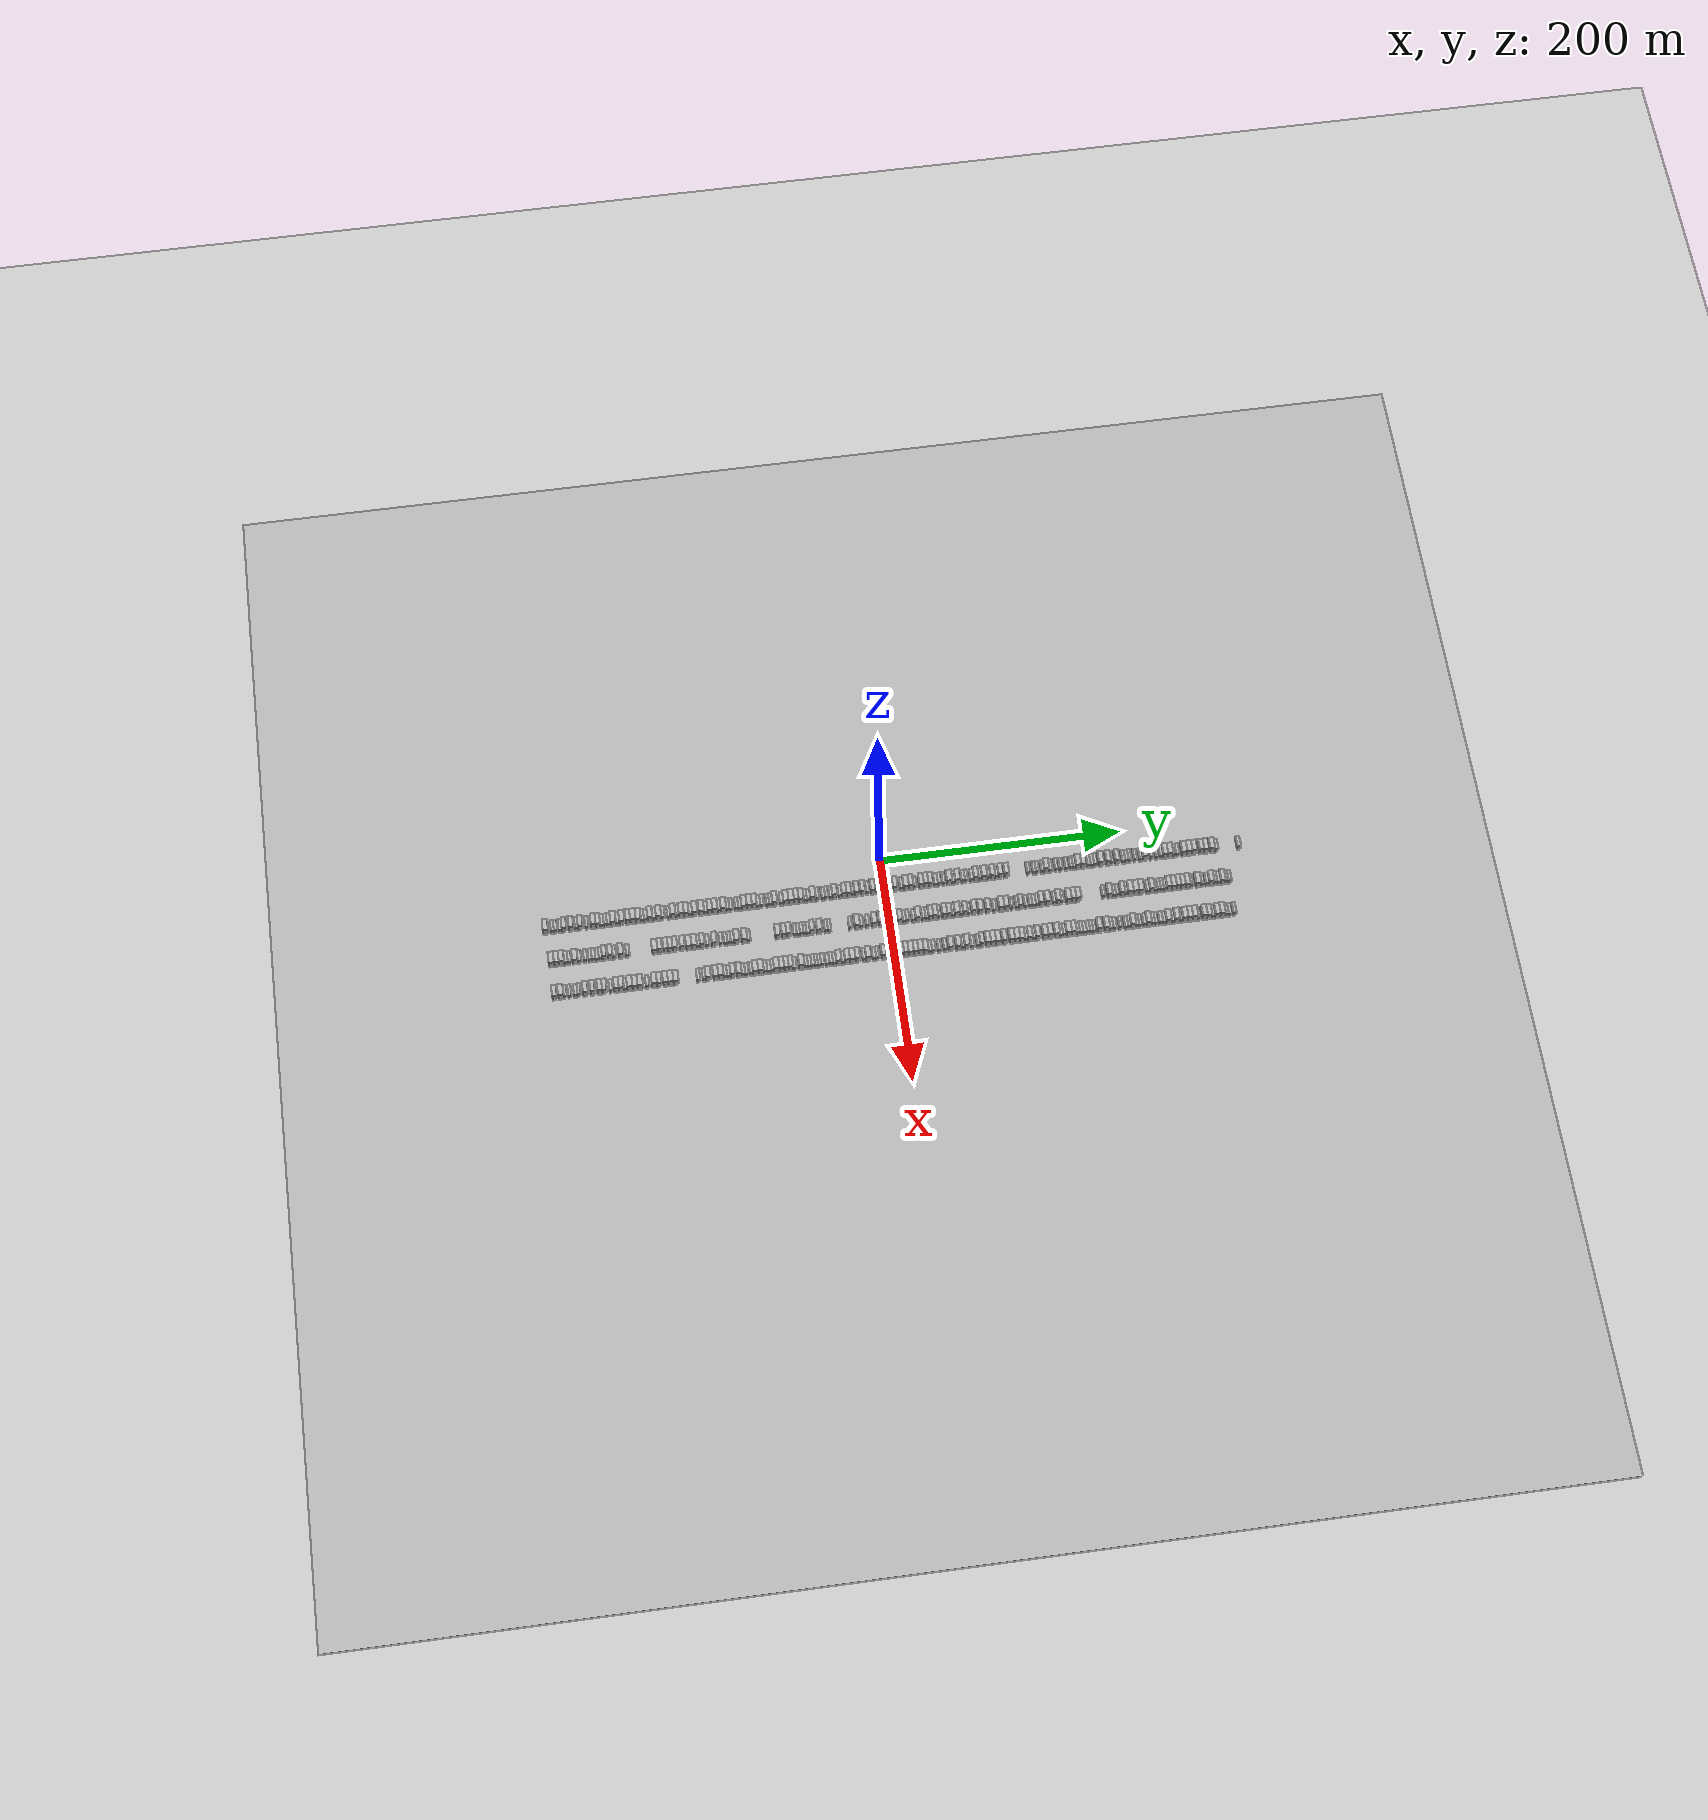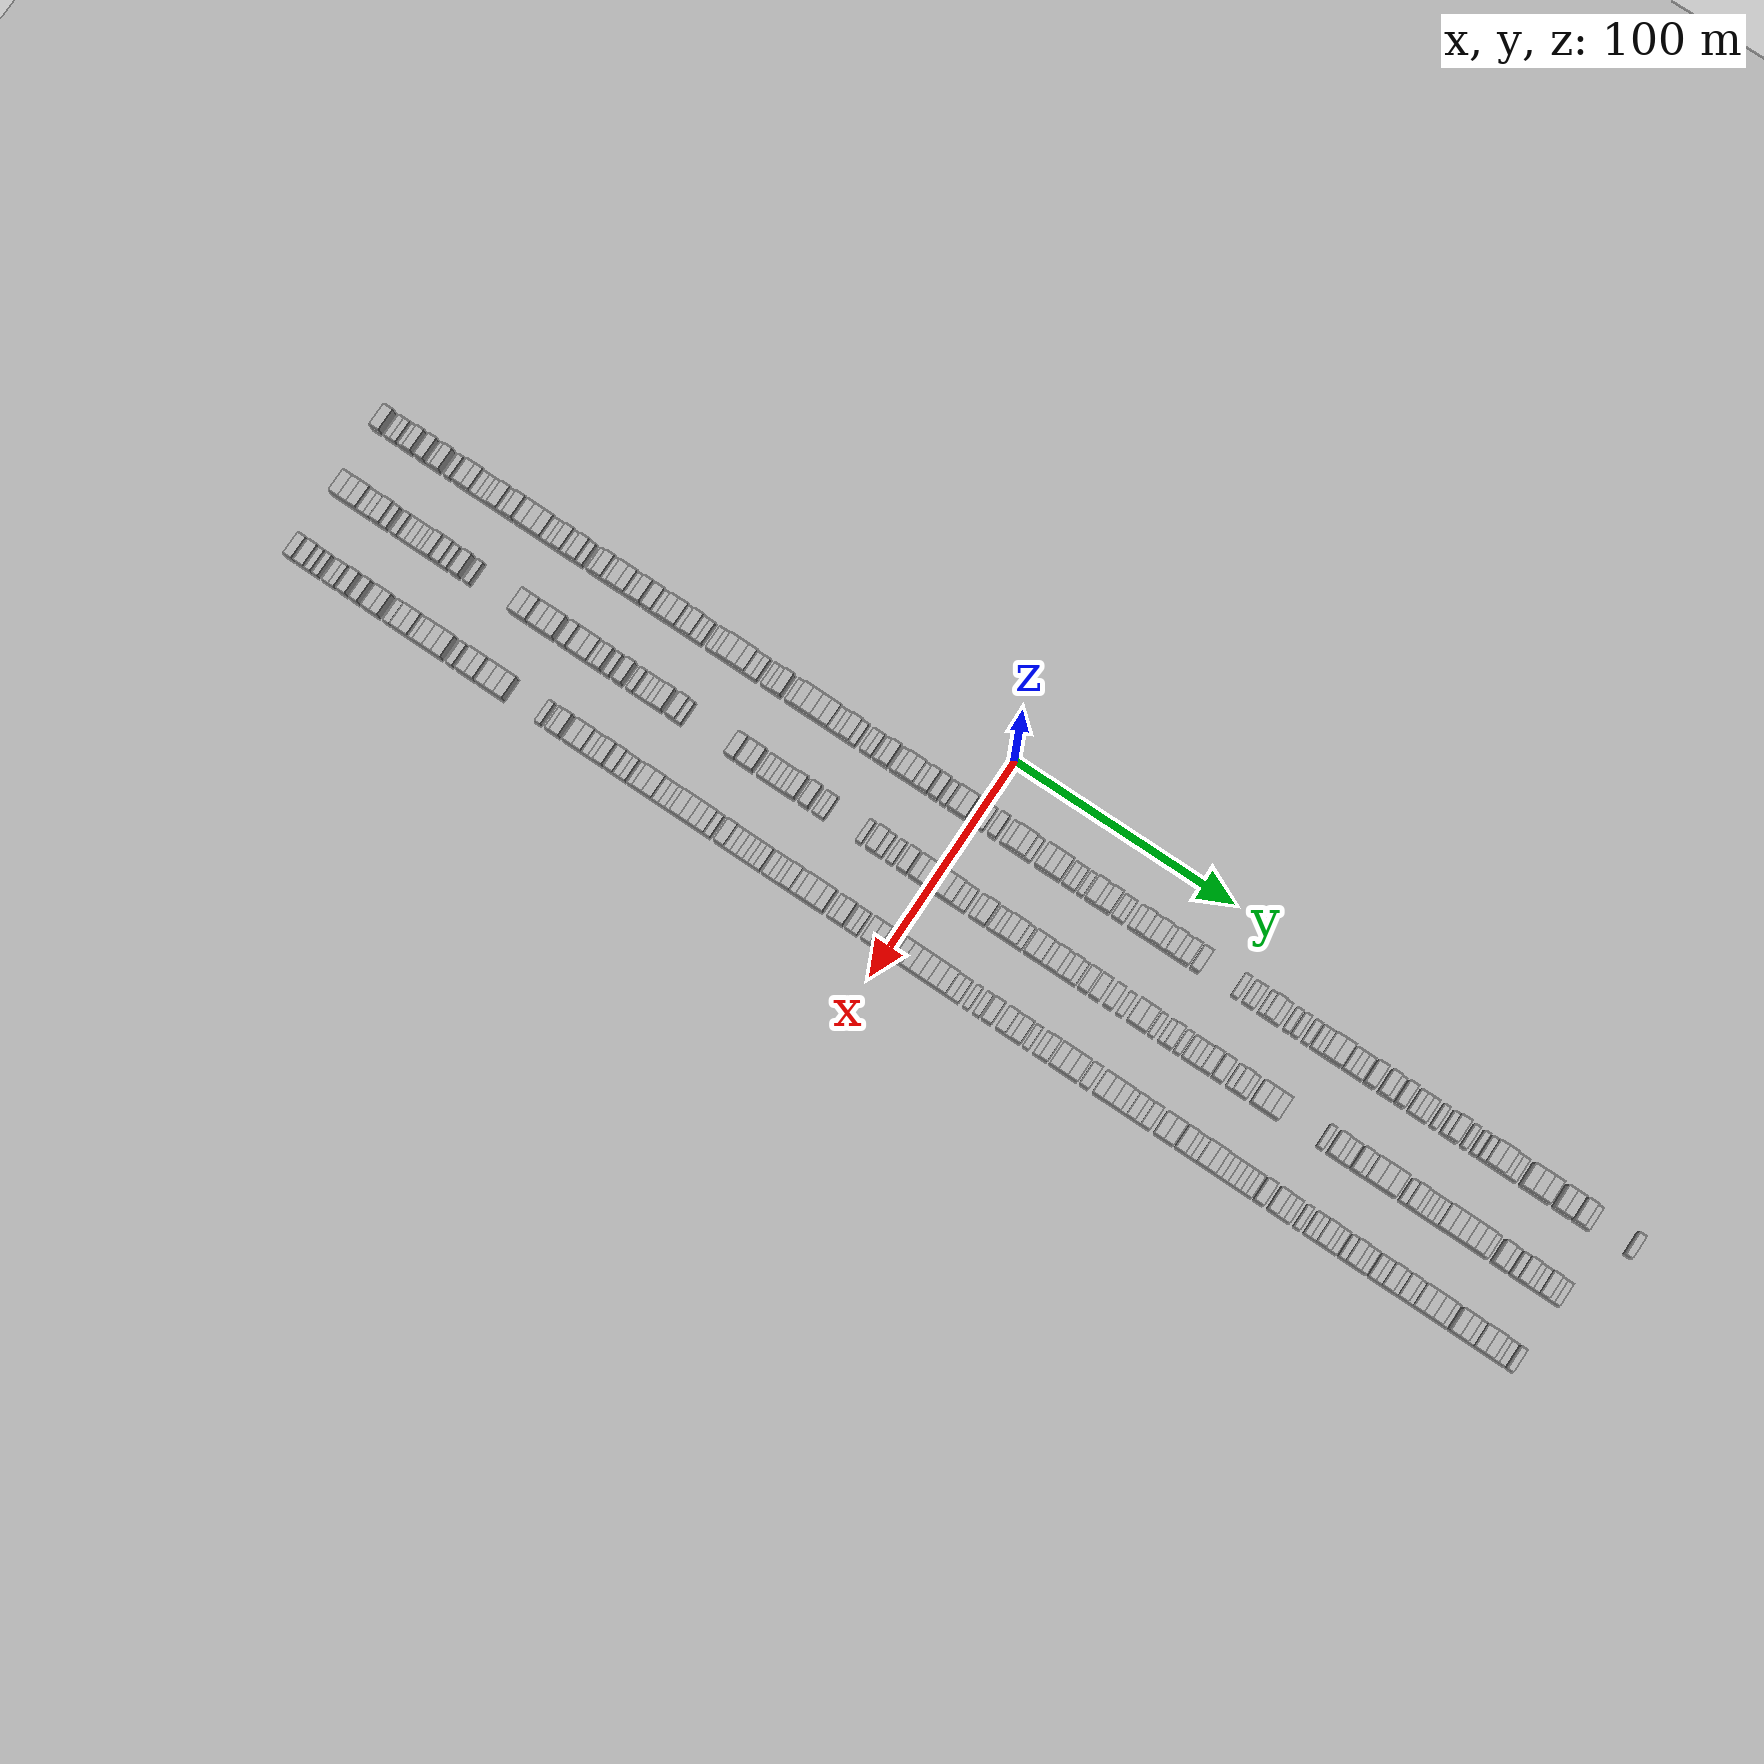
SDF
<?xml version="1.0" encoding="utf-8"?>

<sdf version="1.6">

   <world name="default">

      <gui fullscreen="0">

         <camera name="user_camera">

            <pose>-15 0 4.57585 0 0 0</pose>

            <view_controller>orbit</view_controller>

         </camera>

      </gui>

      <scene>

         <sky>

           <clouds>

             <speed>12</speed>

           </clouds>

         </sky>

         <ambient>0.4 0.4 0.4 1</ambient>

         <background>0.7 0.7 0.7 1</background>

         <shadows>1</shadows>

      </scene>

      <gravity>0 0 -9.8066</gravity>

      <magnetic_field>6e-06 2.3e-05 -4.2e-05</magnetic_field>

      <physics default="0" name="default_physics" type="ode">

         <ode>

            <solver>

               <type>quick</type>

               <iters>10</iters>

               <sor>1.0</sor>

               <use_dynamic_moi_rescaling>0</use_dynamic_moi_rescaling>

            </solver>

            <constraints>

               <cfm>0</cfm>

               <erp>0.2</erp>

               <contact_max_correcting_vel>100</contact_max_correcting_vel>

               <contact_surface_layer>0.001</contact_surface_layer>

            </constraints>

         </ode>

         <max_step_size>0.004</max_step_size>

         <real_time_factor>1</real_time_factor>

         <real_time_update_rate>250</real_time_update_rate>

      </physics>

      <light name="sun" type="directional">

         <cast_shadows>1</cast_shadows>

         <pose>0 0 10 0 0 0</pose>

         <diffuse>0.8 0.8 0.8 1</diffuse>

         <specular>0.2 0.2 0.2 1</specular>

         <attenuation>

            <range>1000</range>

            <constant>0.9</constant>

            <linear>0.01</linear>

            <quadratic>0.001</quadratic>

         </attenuation>

         <direction>-0.5 0.1 -0.9</direction>

      </light>

      <include>

         <name>ground_plane_1</name>

         <uri>model://HANNAS_ground_plane</uri>

         <pose>0 0 0  0 0 0</pose>

      </include>

      <include>

         <name>ground_plane_2</name>

         <uri>model://HANNAS_ground_plane</uri>

         <pose>100 0 0  0 0 0</pose>

      </include>

      <model name="building_1">

         <static>1</static>

         <pose frame="">25.0000 -277.8149 0 0.000000 0.000000 0.000000</pose>

         <link name="link">

            <pose frame="">0 0 4.50 0 0 0</pose>

            <collision name="collision">

               <geometry>

                  <box>

                     <size>10.0000 4.3701 9.0000</size>

                  </box>

               </geometry>

               <max_contacts>10</max_contacts>

               <surface>

                  <contact>

                     <ode/>

                  </contact>

                  <bounce/>

                  <friction>

                     <torsional>

                        <ode/>

                     </torsional>

                     <ode/>

                  </friction>

               </surface>

            </collision>

            <visual name="visual">

               <cast_shadows>0</cast_shadows>

               <geometry>

                  <box>

                     <size>10.0000 4.3701 9.0000</size>

                  </box>

               </geometry>

               <material>

                  <script>

                     <uri>model://HANNAS_wall/materials/scripts</uri>

                     <uri>model://HANNAS_wall/materials/textures</uri>

                     <name>vrc/HANNAS_wall</name>

                  </script>

               </material>

            </visual>

            <self_collide>0</self_collide>

            <enable_wind>0</enable_wind>

            <kinematic>0</kinematic>

         </link>

      </model>

      <model name="building_2">

         <static>1</static>

         <pose frame="">25.0000 -272.3669 0 0.000000 0.000000 0.000000</pose>

         <link name="link">

            <pose frame="">0 0 3.00 0 0 0</pose>

            <collision name="collision">

               <geometry>

                  <box>

                     <size>10.0000 2.5261 6.0000</size>

                  </box>

               </geometry>

               <max_contacts>10</max_contacts>

               <surface>

                  <contact>

                     <ode/>

                  </contact>

                  <bounce/>

                  <friction>

                     <torsional>

                        <ode/>

                     </torsional>

                     <ode/>

                  </friction>

               </surface>

            </collision>

            <visual name="visual">

               <cast_shadows>0</cast_shadows>

               <geometry>

                  <box>

                     <size>10.0000 2.5261 6.0000</size>

                  </box>

               </geometry>

               <material>

                  <script>

                     <uri>model://HANNAS_wall/materials/scripts</uri>

                     <uri>model://HANNAS_wall/materials/textures</uri>

                     <name>vrc/HANNAS_wall</name>

                  </script>

               </material>

            </visual>

            <self_collide>0</self_collide>

            <enable_wind>0</enable_wind>

            <kinematic>0</kinematic>

         </link>

      </model>

      <model name="building_3">

         <static>1</static>

         <pose frame="">25.0000 -269.7297 0 0.000000 0.000000 0.000000</pose>

         <link name="link">

            <pose frame="">0 0 3.00 0 0 0</pose>

            <collision name="collision">

               <geometry>

                  <box>

                     <size>10.0000 2.7483 6.0000</size>

                  </box>

               </geometry>

               <max_contacts>10</max_contacts>

               <surface>

                  <contact>

                     <ode/>

                  </contact>

                  <bounce/>

                  <friction>

                     <torsional>

                        <ode/>

                     </torsional>

                     <ode/>

                  </friction>

               </surface>

            </collision>

            <visual name="visual">

               <cast_shadows>0</cast_shadows>

               <geometry>

                  <box>

                     <size>10.0000 2.7483 6.0000</size>

                  </box>

               </geometry>

               <material>

                  <script>

                     <uri>model://HANNAS_wall/materials/scripts</uri>

                     <uri>model://HANNAS_wall/materials/textures</uri>

                     <name>vrc/HANNAS_wall</name>

                  </script>

               </material>

            </visual>

            <self_collide>0</self_collide>

            <enable_wind>0</enable_wind>

            <kinematic>0</kinematic>

         </link>

      </model>

      <model name="building_4">

         <static>1</static>

         <pose frame="">25.0000 -265.9560 0 0.000000 0.000000 0.000000</pose>

         <link name="link">

            <pose frame="">0 0 3.00 0 0 0</pose>

            <collision name="collision">

               <geometry>

                  <box>

                     <size>10.0000 2.7989 6.0000</size>

                  </box>

               </geometry>

               <max_contacts>10</max_contacts>

               <surface>

                  <contact>

                     <ode/>

                  </contact>

                  <bounce/>

                  <friction>

                     <torsional>

                        <ode/>

                     </torsional>

                     <ode/>

                  </friction>

               </surface>

            </collision>

            <visual name="visual">

               <cast_shadows>0</cast_shadows>

               <geometry>

                  <box>

                     <size>10.0000 2.7989 6.0000</size>

                  </box>

               </geometry>

               <material>

                  <script>

                     <uri>model://HANNAS_wall/materials/scripts</uri>

                     <uri>model://HANNAS_wall/materials/textures</uri>

                     <name>vrc/HANNAS_wall</name>

                  </script>

               </material>

            </visual>

            <self_collide>0</self_collide>

            <enable_wind>0</enable_wind>

            <kinematic>0</kinematic>

         </link>

      </model>

      <model name="building_5">

         <static>1</static>

         <pose frame="">25.0000 -262.7199 0 0.000000 0.000000 0.000000</pose>

         <link name="link">

            <pose frame="">0 0 4.50 0 0 0</pose>

            <collision name="collision">

               <geometry>

                  <box>

                     <size>10.0000 3.6734 9.0000</size>

                  </box>

               </geometry>

               <max_contacts>10</max_contacts>

               <surface>

                  <contact>

                     <ode/>

                  </contact>

                  <bounce/>

                  <friction>

                     <torsional>

                        <ode/>

                     </torsional>

                     <ode/>

                  </friction>

               </surface>

            </collision>

            <visual name="visual">

               <cast_shadows>0</cast_shadows>

               <geometry>

                  <box>

                     <size>10.0000 3.6734 9.0000</size>

                  </box>

               </geometry>

               <material>

                  <script>

                     <uri>model://HANNAS_wall/materials/scripts</uri>

                     <uri>model://HANNAS_wall/materials/textures</uri>

                     <name>vrc/HANNAS_wall</name>

                  </script>

               </material>

            </visual>

            <self_collide>0</self_collide>

            <enable_wind>0</enable_wind>

            <kinematic>0</kinematic>

         </link>

      </model>

      <model name="building_6">

         <static>1</static>

         <pose frame="">25.0000 -256.9233 0 0.000000 0.000000 0.000000</pose>

         <link name="link">

            <pose frame="">0 0 4.50 0 0 0</pose>

            <collision name="collision">

               <geometry>

                  <box>

                     <size>10.0000 3.9198 9.0000</size>

                  </box>

               </geometry>

               <max_contacts>10</max_contacts>

               <surface>

                  <contact>

                     <ode/>

                  </contact>

                  <bounce/>

                  <friction>

                     <torsional>

                        <ode/>

                     </torsional>

                     <ode/>

                  </friction>

               </surface>

            </collision>

            <visual name="visual">

               <cast_shadows>0</cast_shadows>

               <geometry>

                  <box>

                     <size>10.0000 3.9198 9.0000</size>

                  </box>

               </geometry>

               <material>

                  <script>

                     <uri>model://HANNAS_wall/materials/scripts</uri>

                     <uri>model://HANNAS_wall/materials/textures</uri>

                     <name>vrc/HANNAS_wall</name>

                  </script>

               </material>

            </visual>

            <self_collide>0</self_collide>

            <enable_wind>0</enable_wind>

            <kinematic>0</kinematic>

         </link>

      </model>

      <model name="building_7">

         <static>1</static>

         <pose frame="">25.0000 -252.6992 0 0.000000 0.000000 0.000000</pose>

         <link name="link">

            <pose frame="">0 0 3.00 0 0 0</pose>

            <collision name="collision">

               <geometry>

                  <box>

                     <size>10.0000 2.5285 6.0000</size>

                  </box>

               </geometry>

               <max_contacts>10</max_contacts>

               <surface>

                  <contact>

                     <ode/>

                  </contact>

                  <bounce/>

                  <friction>

                     <torsional>

                        <ode/>

                     </torsional>

                     <ode/>

                  </friction>

               </surface>

            </collision>

            <visual name="visual">

               <cast_shadows>0</cast_shadows>

               <geometry>

                  <box>

                     <size>10.0000 2.5285 6.0000</size>

                  </box>

               </geometry>

               <material>

                  <script>

                     <uri>model://HANNAS_wall/materials/scripts</uri>

                     <uri>model://HANNAS_wall/materials/textures</uri>

                     <name>vrc/HANNAS_wall</name>

                  </script>

               </material>

            </visual>

            <self_collide>0</self_collide>

            <enable_wind>0</enable_wind>

            <kinematic>0</kinematic>

         </link>

      </model>

      <model name="building_8">

         <static>1</static>

         <pose frame="">25.0000 -249.5046 0 0.000000 0.000000 0.000000</pose>

         <link name="link">

            <pose frame="">0 0 4.50 0 0 0</pose>

            <collision name="collision">

               <geometry>

                  <box>

                     <size>10.0000 3.8606 9.0000</size>

                  </box>

               </geometry>

               <max_contacts>10</max_contacts>

               <surface>

                  <contact>

                     <ode/>

                  </contact>

                  <bounce/>

                  <friction>

                     <torsional>

                        <ode/>

                     </torsional>

                     <ode/>

                  </friction>

               </surface>

            </collision>

            <visual name="visual">

               <cast_shadows>0</cast_shadows>

               <geometry>

                  <box>

                     <size>10.0000 3.8606 9.0000</size>

                  </box>

               </geometry>

               <material>

                  <script>

                     <uri>model://HANNAS_wall/materials/scripts</uri>

                     <uri>model://HANNAS_wall/materials/textures</uri>

                     <name>vrc/HANNAS_wall</name>

                  </script>

               </material>

            </visual>

            <self_collide>0</self_collide>

            <enable_wind>0</enable_wind>

            <kinematic>0</kinematic>

         </link>

      </model>

      <model name="building_9">

         <static>1</static>

         <pose frame="">25.0000 -244.2319 0 0.000000 0.000000 0.000000</pose>

         <link name="link">

            <pose frame="">0 0 3.00 0 0 0</pose>

            <collision name="collision">

               <geometry>

                  <box>

                     <size>10.0000 2.6850 6.0000</size>

                  </box>

               </geometry>

               <max_contacts>10</max_contacts>

               <surface>

                  <contact>

                     <ode/>

                  </contact>

                  <bounce/>

                  <friction>

                     <torsional>

                        <ode/>

                     </torsional>

                     <ode/>

                  </friction>

               </surface>

            </collision>

            <visual name="visual">

               <cast_shadows>0</cast_shadows>

               <geometry>

                  <box>

                     <size>10.0000 2.6850 6.0000</size>

                  </box>

               </geometry>

               <material>

                  <script>

                     <uri>model://HANNAS_wall/materials/scripts</uri>

                     <uri>model://HANNAS_wall/materials/textures</uri>

                     <name>vrc/HANNAS_wall</name>

                  </script>

               </material>

            </visual>

            <self_collide>0</self_collide>

            <enable_wind>0</enable_wind>

            <kinematic>0</kinematic>

         </link>

      </model>

      <model name="building_10">

         <static>1</static>

         <pose frame="">25.0000 -238.9068 0 0.000000 0.000000 0.000000</pose>

         <link name="link">

            <pose frame="">0 0 4.50 0 0 0</pose>

            <collision name="collision">

               <geometry>

                  <box>

                     <size>10.0000 3.9651 9.0000</size>

                  </box>

               </geometry>

               <max_contacts>10</max_contacts>

               <surface>

                  <contact>

                     <ode/>

                  </contact>

                  <bounce/>

                  <friction>

                     <torsional>

                        <ode/>

                     </torsional>

                     <ode/>

                  </friction>

               </surface>

            </collision>

            <visual name="visual">

               <cast_shadows>0</cast_shadows>

               <geometry>

                  <box>

                     <size>10.0000 3.9651 9.0000</size>

                  </box>

               </geometry>

               <material>

                  <script>

                     <uri>model://HANNAS_wall/materials/scripts</uri>

                     <uri>model://HANNAS_wall/materials/textures</uri>

                     <name>vrc/HANNAS_wall</name>

                  </script>

               </material>

            </visual>

            <self_collide>0</self_collide>

            <enable_wind>0</enable_wind>

            <kinematic>0</kinematic>

         </link>

      </model>

      <model name="building_11">

         <static>1</static>

         <pose frame="">25.0000 -235.1069 0 0.000000 0.000000 0.000000</pose>

         <link name="link">

            <pose frame="">0 0 4.50 0 0 0</pose>

            <collision name="collision">

               <geometry>

                  <box>

                     <size>10.0000 3.6346 9.0000</size>

                  </box>

               </geometry>

               <max_contacts>10</max_contacts>

               <surface>

                  <contact>

                     <ode/>

                  </contact>

                  <bounce/>

                  <friction>

                     <torsional>

                        <ode/>

                     </torsional>

                     <ode/>

                  </friction>

               </surface>

            </collision>

            <visual name="visual">

               <cast_shadows>0</cast_shadows>

               <geometry>

                  <box>

                     <size>10.0000 3.6346 9.0000</size>

                  </box>

               </geometry>

               <material>

                  <script>

                     <uri>model://HANNAS_wall/materials/scripts</uri>

                     <uri>model://HANNAS_wall/materials/textures</uri>

                     <name>vrc/HANNAS_wall</name>

                  </script>

               </material>

            </visual>

            <self_collide>0</self_collide>

            <enable_wind>0</enable_wind>

            <kinematic>0</kinematic>

         </link>

      </model>

      <model name="building_12">

         <static>1</static>

         <pose frame="">25.0000 -231.8906 0 0.000000 0.000000 0.000000</pose>

         <link name="link">

            <pose frame="">0 0 3.00 0 0 0</pose>

            <collision name="collision">

               <geometry>

                  <box>

                     <size>10.0000 2.7980 6.0000</size>

                  </box>

               </geometry>

               <max_contacts>10</max_contacts>

               <surface>

                  <contact>

                     <ode/>

                  </contact>

                  <bounce/>

                  <friction>

                     <torsional>

                        <ode/>

                     </torsional>

                     <ode/>

                  </friction>

               </surface>

            </collision>

            <visual name="visual">

               <cast_shadows>0</cast_shadows>

               <geometry>

                  <box>

                     <size>10.0000 2.7980 6.0000</size>

                  </box>

               </geometry>

               <material>

                  <script>

                     <uri>model://HANNAS_wall/materials/scripts</uri>

                     <uri>model://HANNAS_wall/materials/textures</uri>

                     <name>vrc/HANNAS_wall</name>

                  </script>

               </material>

            </visual>

            <self_collide>0</self_collide>

            <enable_wind>0</enable_wind>

            <kinematic>0</kinematic>

         </link>

      </model>

      <model name="building_13">

         <static>1</static>

         <pose frame="">25.0000 -229.1642 0 0.000000 0.000000 0.000000</pose>

         <link name="link">

            <pose frame="">0 0 3.00 0 0 0</pose>

            <collision name="collision">

               <geometry>

                  <box>

                     <size>10.0000 2.6547 6.0000</size>

                  </box>

               </geometry>

               <max_contacts>10</max_contacts>

               <surface>

                  <contact>

                     <ode/>

                  </contact>

                  <bounce/>

                  <friction>

                     <torsional>

                        <ode/>

                     </torsional>

                     <ode/>

                  </friction>

               </surface>

            </collision>

            <visual name="visual">

               <cast_shadows>0</cast_shadows>

               <geometry>

                  <box>

                     <size>10.0000 2.6547 6.0000</size>

                  </box>

               </geometry>

               <material>

                  <script>

                     <uri>model://HANNAS_wall/materials/scripts</uri>

                     <uri>model://HANNAS_wall/materials/textures</uri>

                     <name>vrc/HANNAS_wall</name>

                  </script>

               </material>

            </visual>

            <self_collide>0</self_collide>

            <enable_wind>0</enable_wind>

            <kinematic>0</kinematic>

         </link>

      </model>

      <model name="building_14">

         <static>1</static>

         <pose frame="">25.0000 -226.3627 0 0.000000 0.000000 0.000000</pose>

         <link name="link">

            <pose frame="">0 0 3.00 0 0 0</pose>

            <collision name="collision">

               <geometry>

                  <box>

                     <size>10.0000 2.9484 6.0000</size>

                  </box>

               </geometry>

               <max_contacts>10</max_contacts>

               <surface>

                  <contact>

                     <ode/>

                  </contact>

                  <bounce/>

                  <friction>

                     <torsional>

                        <ode/>

                     </torsional>

                     <ode/>

                  </friction>

               </surface>

            </collision>

            <visual name="visual">

               <cast_shadows>0</cast_shadows>

               <geometry>

                  <box>

                     <size>10.0000 2.9484 6.0000</size>

                  </box>

               </geometry>

               <material>

                  <script>

                     <uri>model://HANNAS_wall/materials/scripts</uri>

                     <uri>model://HANNAS_wall/materials/textures</uri>

                     <name>vrc/HANNAS_wall</name>

                  </script>

               </material>

            </visual>

            <self_collide>0</self_collide>

            <enable_wind>0</enable_wind>

            <kinematic>0</kinematic>

         </link>

      </model>

      <model name="building_15">

         <static>1</static>

         <pose frame="">25.0000 -222.7146 0 0.000000 0.000000 0.000000</pose>

         <link name="link">

            <pose frame="">0 0 4.50 0 0 0</pose>

            <collision name="collision">

               <geometry>

                  <box>

                     <size>10.0000 4.3479 9.0000</size>

                  </box>

               </geometry>

               <max_contacts>10</max_contacts>

               <surface>

                  <contact>

                     <ode/>

                  </contact>

                  <bounce/>

                  <friction>

                     <torsional>

                        <ode/>

                     </torsional>

                     <ode/>

                  </friction>

               </surface>

            </collision>

            <visual name="visual">

               <cast_shadows>0</cast_shadows>

               <geometry>

                  <box>

                     <size>10.0000 4.3479 9.0000</size>

                  </box>

               </geometry>

               <material>

                  <script>

                     <uri>model://HANNAS_wall/materials/scripts</uri>

                     <uri>model://HANNAS_wall/materials/textures</uri>

                     <name>vrc/HANNAS_wall</name>

                  </script>

               </material>

            </visual>

            <self_collide>0</self_collide>

            <enable_wind>0</enable_wind>

            <kinematic>0</kinematic>

         </link>

      </model>

      <model name="building_16">

         <static>1</static>

         <pose frame="">25.0000 -219.1137 0 0.000000 0.000000 0.000000</pose>

         <link name="link">

            <pose frame="">0 0 3.00 0 0 0</pose>

            <collision name="collision">

               <geometry>

                  <box>

                     <size>10.0000 2.8539 6.0000</size>

                  </box>

               </geometry>

               <max_contacts>10</max_contacts>

               <surface>

                  <contact>

                     <ode/>

                  </contact>

                  <bounce/>

                  <friction>

                     <torsional>

                        <ode/>

                     </torsional>

                     <ode/>

                  </friction>

               </surface>

            </collision>

            <visual name="visual">

               <cast_shadows>0</cast_shadows>

               <geometry>

                  <box>

                     <size>10.0000 2.8539 6.0000</size>

                  </box>

               </geometry>

               <material>

                  <script>

                     <uri>model://HANNAS_wall/materials/scripts</uri>

                     <uri>model://HANNAS_wall/materials/textures</uri>

                     <name>vrc/HANNAS_wall</name>

                  </script>

               </material>

            </visual>

            <self_collide>0</self_collide>

            <enable_wind>0</enable_wind>

            <kinematic>0</kinematic>

         </link>

      </model>

      <model name="building_17">

         <static>1</static>

         <pose frame="">25.0000 -215.5499 0 0.000000 0.000000 0.000000</pose>

         <link name="link">

            <pose frame="">0 0 4.50 0 0 0</pose>

            <collision name="collision">

               <geometry>

                  <box>

                     <size>10.0000 4.2735 9.0000</size>

                  </box>

               </geometry>

               <max_contacts>10</max_contacts>

               <surface>

                  <contact>

                     <ode/>

                  </contact>

                  <bounce/>

                  <friction>

                     <torsional>

                        <ode/>

                     </torsional>

                     <ode/>

                  </friction>

               </surface>

            </collision>

            <visual name="visual">

               <cast_shadows>0</cast_shadows>

               <geometry>

                  <box>

                     <size>10.0000 4.2735 9.0000</size>

                  </box>

               </geometry>

               <material>

                  <script>

                     <uri>model://HANNAS_wall/materials/scripts</uri>

                     <uri>model://HANNAS_wall/materials/textures</uri>

                     <name>vrc/HANNAS_wall</name>

                  </script>

               </material>

            </visual>

            <self_collide>0</self_collide>

            <enable_wind>0</enable_wind>

            <kinematic>0</kinematic>

         </link>

      </model>

      <model name="building_18">

         <static>1</static>

         <pose frame="">25.0000 -210.5825 0 0.000000 0.000000 0.000000</pose>

         <link name="link">

            <pose frame="">0 0 4.50 0 0 0</pose>

            <collision name="collision">

               <geometry>

                  <box>

                     <size>10.0000 3.6612 9.0000</size>

                  </box>

               </geometry>

               <max_contacts>10</max_contacts>

               <surface>

                  <contact>

                     <ode/>

                  </contact>

                  <bounce/>

                  <friction>

                     <torsional>

                        <ode/>

                     </torsional>

                     <ode/>

                  </friction>

               </surface>

            </collision>

            <visual name="visual">

               <cast_shadows>0</cast_shadows>

               <geometry>

                  <box>

                     <size>10.0000 3.6612 9.0000</size>

                  </box>

               </geometry>

               <material>

                  <script>

                     <uri>model://HANNAS_wall/materials/scripts</uri>

                     <uri>model://HANNAS_wall/materials/textures</uri>

                     <name>vrc/HANNAS_wall</name>

                  </script>

               </material>

            </visual>

            <self_collide>0</self_collide>

            <enable_wind>0</enable_wind>

            <kinematic>0</kinematic>

         </link>

      </model>

      <model name="building_19">

         <static>1</static>

         <pose frame="">25.0000 -206.5141 0 0.000000 0.000000 0.000000</pose>

         <link name="link">

            <pose frame="">0 0 4.50 0 0 0</pose>

            <collision name="collision">

               <geometry>

                  <box>

                     <size>10.0000 4.4757 9.0000</size>

                  </box>

               </geometry>

               <max_contacts>10</max_contacts>

               <surface>

                  <contact>

                     <ode/>

                  </contact>

                  <bounce/>

                  <friction>

                     <torsional>

                        <ode/>

                     </torsional>

                     <ode/>

                  </friction>

               </surface>

            </collision>

            <visual name="visual">

               <cast_shadows>0</cast_shadows>

               <geometry>

                  <box>

                     <size>10.0000 4.4757 9.0000</size>

                  </box>

               </geometry>

               <material>

                  <script>

                     <uri>model://HANNAS_wall/materials/scripts</uri>

                     <uri>model://HANNAS_wall/materials/textures</uri>

                     <name>vrc/HANNAS_wall</name>

                  </script>

               </material>

            </visual>

            <self_collide>0</self_collide>

            <enable_wind>0</enable_wind>

            <kinematic>0</kinematic>

         </link>

      </model>

      <model name="building_20">

         <static>1</static>

         <pose frame="">25.0000 -202.2055 0 0.000000 0.000000 0.000000</pose>

         <link name="link">

            <pose frame="">0 0 4.50 0 0 0</pose>

            <collision name="collision">

               <geometry>

                  <box>

                     <size>10.0000 4.1415 9.0000</size>

                  </box>

               </geometry>

               <max_contacts>10</max_contacts>

               <surface>

                  <contact>

                     <ode/>

                  </contact>

                  <bounce/>

                  <friction>

                     <torsional>

                        <ode/>

                     </torsional>

                     <ode/>

                  </friction>

               </surface>

            </collision>

            <visual name="visual">

               <cast_shadows>0</cast_shadows>

               <geometry>

                  <box>

                     <size>10.0000 4.1415 9.0000</size>

                  </box>

               </geometry>

               <material>

                  <script>

                     <uri>model://HANNAS_wall/materials/scripts</uri>

                     <uri>model://HANNAS_wall/materials/textures</uri>

                     <name>vrc/HANNAS_wall</name>

                  </script>

               </material>

            </visual>

            <self_collide>0</self_collide>

            <enable_wind>0</enable_wind>

            <kinematic>0</kinematic>

         </link>

      </model>

      <model name="building_21">

         <static>1</static>

         <pose frame="">25.0000 -198.8744 0 0.000000 0.000000 0.000000</pose>

         <link name="link">

            <pose frame="">0 0 3.00 0 0 0</pose>

            <collision name="collision">

               <geometry>

                  <box>

                     <size>10.0000 2.5206 6.0000</size>

                  </box>

               </geometry>

               <max_contacts>10</max_contacts>

               <surface>

                  <contact>

                     <ode/>

                  </contact>

                  <bounce/>

                  <friction>

                     <torsional>

                        <ode/>

                     </torsional>

                     <ode/>

                  </friction>

               </surface>

            </collision>

            <visual name="visual">

               <cast_shadows>0</cast_shadows>

               <geometry>

                  <box>

                     <size>10.0000 2.5206 6.0000</size>

                  </box>

               </geometry>

               <material>

                  <script>

                     <uri>model://HANNAS_wall/materials/scripts</uri>

                     <uri>model://HANNAS_wall/materials/textures</uri>

                     <name>vrc/HANNAS_wall</name>

                  </script>

               </material>

            </visual>

            <self_collide>0</self_collide>

            <enable_wind>0</enable_wind>

            <kinematic>0</kinematic>

         </link>

      </model>

      <model name="building_22">

         <static>1</static>

         <pose frame="">25.0000 -196.1217 0 0.000000 0.000000 0.000000</pose>

         <link name="link">

            <pose frame="">0 0 3.00 0 0 0</pose>

            <collision name="collision">

               <geometry>

                  <box>

                     <size>10.0000 2.9849 6.0000</size>

                  </box>

               </geometry>

               <max_contacts>10</max_contacts>

               <surface>

                  <contact>

                     <ode/>

                  </contact>

                  <bounce/>

                  <friction>

                     <torsional>

                        <ode/>

                     </torsional>

                     <ode/>

                  </friction>

               </surface>

            </collision>

            <visual name="visual">

               <cast_shadows>0</cast_shadows>

               <geometry>

                  <box>

                     <size>10.0000 2.9849 6.0000</size>

                  </box>

               </geometry>

               <material>

                  <script>

                     <uri>model://HANNAS_wall/materials/scripts</uri>

                     <uri>model://HANNAS_wall/materials/textures</uri>

                     <name>vrc/HANNAS_wall</name>

                  </script>

               </material>

            </visual>

            <self_collide>0</self_collide>

            <enable_wind>0</enable_wind>

            <kinematic>0</kinematic>

         </link>

      </model>

      <model name="building_23">

         <static>1</static>

         <pose frame="">25.0000 -192.6472 0 0.000000 0.000000 0.000000</pose>

         <link name="link">

            <pose frame="">0 0 4.50 0 0 0</pose>

            <collision name="collision">

               <geometry>

                  <box>

                     <size>10.0000 3.9641 9.0000</size>

                  </box>

               </geometry>

               <max_contacts>10</max_contacts>

               <surface>

                  <contact>

                     <ode/>

                  </contact>

                  <bounce/>

                  <friction>

                     <torsional>

                        <ode/>

                     </torsional>

                     <ode/>

                  </friction>

               </surface>

            </collision>

            <visual name="visual">

               <cast_shadows>0</cast_shadows>

               <geometry>

                  <box>

                     <size>10.0000 3.9641 9.0000</size>

                  </box>

               </geometry>

               <material>

                  <script>

                     <uri>model://HANNAS_wall/materials/scripts</uri>

                     <uri>model://HANNAS_wall/materials/textures</uri>

                     <name>vrc/HANNAS_wall</name>

                  </script>

               </material>

            </visual>

            <self_collide>0</self_collide>

            <enable_wind>0</enable_wind>

            <kinematic>0</kinematic>

         </link>

      </model>

      <model name="building_24">

         <static>1</static>

         <pose frame="">25.0000 -189.2160 0 0.000000 0.000000 0.000000</pose>

         <link name="link">

            <pose frame="">0 0 3.00 0 0 0</pose>

            <collision name="collision">

               <geometry>

                  <box>

                     <size>10.0000 2.8983 6.0000</size>

                  </box>

               </geometry>

               <max_contacts>10</max_contacts>

               <surface>

                  <contact>

                     <ode/>

                  </contact>

                  <bounce/>

                  <friction>

                     <torsional>

                        <ode/>

                     </torsional>

                     <ode/>

                  </friction>

               </surface>

            </collision>

            <visual name="visual">

               <cast_shadows>0</cast_shadows>

               <geometry>

                  <box>

                     <size>10.0000 2.8983 6.0000</size>

                  </box>

               </geometry>

               <material>

                  <script>

                     <uri>model://HANNAS_wall/materials/scripts</uri>

                     <uri>model://HANNAS_wall/materials/textures</uri>

                     <name>vrc/HANNAS_wall</name>

                  </script>

               </material>

            </visual>

            <self_collide>0</self_collide>

            <enable_wind>0</enable_wind>

            <kinematic>0</kinematic>

         </link>

      </model>

      <model name="building_25">

         <static>1</static>

         <pose frame="">25.0000 -185.5957 0 0.000000 0.000000 0.000000</pose>

         <link name="link">

            <pose frame="">0 0 4.50 0 0 0</pose>

            <collision name="collision">

               <geometry>

                  <box>

                     <size>10.0000 4.3424 9.0000</size>

                  </box>

               </geometry>

               <max_contacts>10</max_contacts>

               <surface>

                  <contact>

                     <ode/>

                  </contact>

                  <bounce/>

                  <friction>

                     <torsional>

                        <ode/>

                     </torsional>

                     <ode/>

                  </friction>

               </surface>

            </collision>

            <visual name="visual">

               <cast_shadows>0</cast_shadows>

               <geometry>

                  <box>

                     <size>10.0000 4.3424 9.0000</size>

                  </box>

               </geometry>

               <material>

                  <script>

                     <uri>model://HANNAS_wall/materials/scripts</uri>

                     <uri>model://HANNAS_wall/materials/textures</uri>

                     <name>vrc/HANNAS_wall</name>

                  </script>

               </material>

            </visual>

            <self_collide>0</self_collide>

            <enable_wind>0</enable_wind>

            <kinematic>0</kinematic>

         </link>

      </model>

      <model name="building_26">

         <static>1</static>

         <pose frame="">25.0000 -181.9877 0 0.000000 0.000000 0.000000</pose>

         <link name="link">

            <pose frame="">0 0 3.00 0 0 0</pose>

            <collision name="collision">

               <geometry>

                  <box>

                     <size>10.0000 2.8734 6.0000</size>

                  </box>

               </geometry>

               <max_contacts>10</max_contacts>

               <surface>

                  <contact>

                     <ode/>

                  </contact>

                  <bounce/>

                  <friction>

                     <torsional>

                        <ode/>

                     </torsional>

                     <ode/>

                  </friction>

               </surface>

            </collision>

            <visual name="visual">

               <cast_shadows>0</cast_shadows>

               <geometry>

                  <box>

                     <size>10.0000 2.8734 6.0000</size>

                  </box>

               </geometry>

               <material>

                  <script>

                     <uri>model://HANNAS_wall/materials/scripts</uri>

                     <uri>model://HANNAS_wall/materials/textures</uri>

                     <name>vrc/HANNAS_wall</name>

                  </script>

               </material>

            </visual>

            <self_collide>0</self_collide>

            <enable_wind>0</enable_wind>

            <kinematic>0</kinematic>

         </link>

      </model>

      <model name="building_27">

         <static>1</static>

         <pose frame="">25.0000 -177.2383 0 0.000000 0.000000 0.000000</pose>

         <link name="link">

            <pose frame="">0 0 3.00 0 0 0</pose>

            <collision name="collision">

               <geometry>

                  <box>

                     <size>10.0000 2.6254 6.0000</size>

                  </box>

               </geometry>

               <max_contacts>10</max_contacts>

               <surface>

                  <contact>

                     <ode/>

                  </contact>

                  <bounce/>

                  <friction>

                     <torsional>

                        <ode/>

                     </torsional>

                     <ode/>

                  </friction>

               </surface>

            </collision>

            <visual name="visual">

               <cast_shadows>0</cast_shadows>

               <geometry>

                  <box>

                     <size>10.0000 2.6254 6.0000</size>

                  </box>

               </geometry>

               <material>

                  <script>

                     <uri>model://HANNAS_wall/materials/scripts</uri>

                     <uri>model://HANNAS_wall/materials/textures</uri>

                     <name>vrc/HANNAS_wall</name>

                  </script>

               </material>

            </visual>

            <self_collide>0</self_collide>

            <enable_wind>0</enable_wind>

            <kinematic>0</kinematic>

         </link>

      </model>

      <model name="building_28">

         <static>1</static>

         <pose frame="">25.0000 -173.7595 0 0.000000 0.000000 0.000000</pose>

         <link name="link">

            <pose frame="">0 0 4.50 0 0 0</pose>

            <collision name="collision">

               <geometry>

                  <box>

                     <size>10.0000 4.3323 9.0000</size>

                  </box>

               </geometry>

               <max_contacts>10</max_contacts>

               <surface>

                  <contact>

                     <ode/>

                  </contact>

                  <bounce/>

                  <friction>

                     <torsional>

                        <ode/>

                     </torsional>

                     <ode/>

                  </friction>

               </surface>

            </collision>

            <visual name="visual">

               <cast_shadows>0</cast_shadows>

               <geometry>

                  <box>

                     <size>10.0000 4.3323 9.0000</size>

                  </box>

               </geometry>

               <material>

                  <script>

                     <uri>model://HANNAS_wall/materials/scripts</uri>

                     <uri>model://HANNAS_wall/materials/textures</uri>

                     <name>vrc/HANNAS_wall</name>

                  </script>

               </material>

            </visual>

            <self_collide>0</self_collide>

            <enable_wind>0</enable_wind>

            <kinematic>0</kinematic>

         </link>

      </model>

      <model name="building_29">

         <static>1</static>

         <pose frame="">25.0000 -170.3641 0 0.000000 0.000000 0.000000</pose>

         <link name="link">

            <pose frame="">0 0 3.00 0 0 0</pose>

            <collision name="collision">

               <geometry>

                  <box>

                     <size>10.0000 2.4583 6.0000</size>

                  </box>

               </geometry>

               <max_contacts>10</max_contacts>

               <surface>

                  <contact>

                     <ode/>

                  </contact>

                  <bounce/>

                  <friction>

                     <torsional>

                        <ode/>

                     </torsional>

                     <ode/>

                  </friction>

               </surface>

            </collision>

            <visual name="visual">

               <cast_shadows>0</cast_shadows>

               <geometry>

                  <box>

                     <size>10.0000 2.4583 6.0000</size>

                  </box>

               </geometry>

               <material>

                  <script>

                     <uri>model://HANNAS_wall/materials/scripts</uri>

                     <uri>model://HANNAS_wall/materials/textures</uri>

                     <name>vrc/HANNAS_wall</name>

                  </script>

               </material>

            </visual>

            <self_collide>0</self_collide>

            <enable_wind>0</enable_wind>

            <kinematic>0</kinematic>

         </link>

      </model>

      <model name="building_30">

         <static>1</static>

         <pose frame="">25.0000 -166.9870 0 0.000000 0.000000 0.000000</pose>

         <link name="link">

            <pose frame="">0 0 4.50 0 0 0</pose>

            <collision name="collision">

               <geometry>

                  <box>

                     <size>10.0000 4.2960 9.0000</size>

                  </box>

               </geometry>

               <max_contacts>10</max_contacts>

               <surface>

                  <contact>

                     <ode/>

                  </contact>

                  <bounce/>

                  <friction>

                     <torsional>

                        <ode/>

                     </torsional>

                     <ode/>

                  </friction>

               </surface>

            </collision>

            <visual name="visual">

               <cast_shadows>0</cast_shadows>

               <geometry>

                  <box>

                     <size>10.0000 4.2960 9.0000</size>

                  </box>

               </geometry>

               <material>

                  <script>

                     <uri>model://HANNAS_wall/materials/scripts</uri>

                     <uri>model://HANNAS_wall/materials/textures</uri>

                     <name>vrc/HANNAS_wall</name>

                  </script>

               </material>

            </visual>

            <self_collide>0</self_collide>

            <enable_wind>0</enable_wind>

            <kinematic>0</kinematic>

         </link>

      </model>

      <model name="building_31">

         <static>1</static>

         <pose frame="">25.0000 -162.9096 0 0.000000 0.000000 0.000000</pose>

         <link name="link">

            <pose frame="">0 0 4.50 0 0 0</pose>

            <collision name="collision">

               <geometry>

                  <box>

                     <size>10.0000 3.8586 9.0000</size>

                  </box>

               </geometry>

               <max_contacts>10</max_contacts>

               <surface>

                  <contact>

                     <ode/>

                  </contact>

                  <bounce/>

                  <friction>

                     <torsional>

                        <ode/>

                     </torsional>

                     <ode/>

                  </friction>

               </surface>

            </collision>

            <visual name="visual">

               <cast_shadows>0</cast_shadows>

               <geometry>

                  <box>

                     <size>10.0000 3.8586 9.0000</size>

                  </box>

               </geometry>

               <material>

                  <script>

                     <uri>model://HANNAS_wall/materials/scripts</uri>

                     <uri>model://HANNAS_wall/materials/textures</uri>

                     <name>vrc/HANNAS_wall</name>

                  </script>

               </material>

            </visual>

            <self_collide>0</self_collide>

            <enable_wind>0</enable_wind>

            <kinematic>0</kinematic>

         </link>

      </model>

      <model name="building_32">

         <static>1</static>

         <pose frame="">25.0000 -159.5487 0 0.000000 0.000000 0.000000</pose>

         <link name="link">

            <pose frame="">0 0 3.00 0 0 0</pose>

            <collision name="collision">

               <geometry>

                  <box>

                     <size>10.0000 2.8632 6.0000</size>

                  </box>

               </geometry>

               <max_contacts>10</max_contacts>

               <surface>

                  <contact>

                     <ode/>

                  </contact>

                  <bounce/>

                  <friction>

                     <torsional>

                        <ode/>

                     </torsional>

                     <ode/>

                  </friction>

               </surface>

            </collision>

            <visual name="visual">

               <cast_shadows>0</cast_shadows>

               <geometry>

                  <box>

                     <size>10.0000 2.8632 6.0000</size>

                  </box>

               </geometry>

               <material>

                  <script>

                     <uri>model://HANNAS_wall/materials/scripts</uri>

                     <uri>model://HANNAS_wall/materials/textures</uri>

                     <name>vrc/HANNAS_wall</name>

                  </script>

               </material>

            </visual>

            <self_collide>0</self_collide>

            <enable_wind>0</enable_wind>

            <kinematic>0</kinematic>

         </link>

      </model>

      <model name="building_33">

         <static>1</static>

         <pose frame="">25.0000 -155.9598 0 0.000000 0.000000 0.000000</pose>

         <link name="link">

            <pose frame="">0 0 4.50 0 0 0</pose>

            <collision name="collision">

               <geometry>

                  <box>

                     <size>10.0000 4.3147 9.0000</size>

                  </box>

               </geometry>

               <max_contacts>10</max_contacts>

               <surface>

                  <contact>

                     <ode/>

                  </contact>

                  <bounce/>

                  <friction>

                     <torsional>

                        <ode/>

                     </torsional>

                     <ode/>

                  </friction>

               </surface>

            </collision>

            <visual name="visual">

               <cast_shadows>0</cast_shadows>

               <geometry>

                  <box>

                     <size>10.0000 4.3147 9.0000</size>

                  </box>

               </geometry>

               <material>

                  <script>

                     <uri>model://HANNAS_wall/materials/scripts</uri>

                     <uri>model://HANNAS_wall/materials/textures</uri>

                     <name>vrc/HANNAS_wall</name>

                  </script>

               </material>

            </visual>

            <self_collide>0</self_collide>

            <enable_wind>0</enable_wind>

            <kinematic>0</kinematic>

         </link>

      </model>

      <model name="building_34">

         <static>1</static>

         <pose frame="">25.0000 -150.5635 0 0.000000 0.000000 0.000000</pose>

         <link name="link">

            <pose frame="">0 0 4.50 0 0 0</pose>

            <collision name="collision">

               <geometry>

                  <box>

                     <size>10.0000 4.4778 9.0000</size>

                  </box>

               </geometry>

               <max_contacts>10</max_contacts>

               <surface>

                  <contact>

                     <ode/>

                  </contact>

                  <bounce/>

                  <friction>

                     <torsional>

                        <ode/>

                     </torsional>

                     <ode/>

                  </friction>

               </surface>

            </collision>

            <visual name="visual">

               <cast_shadows>0</cast_shadows>

               <geometry>

                  <box>

                     <size>10.0000 4.4778 9.0000</size>

                  </box>

               </geometry>

               <material>

                  <script>

                     <uri>model://HANNAS_wall/materials/scripts</uri>

                     <uri>model://HANNAS_wall/materials/textures</uri>

                     <name>vrc/HANNAS_wall</name>

                  </script>

               </material>

            </visual>

            <self_collide>0</self_collide>

            <enable_wind>0</enable_wind>

            <kinematic>0</kinematic>

         </link>

      </model>

      <model name="building_35">

         <static>1</static>

         <pose frame="">25.0000 -146.9342 0 0.000000 0.000000 0.000000</pose>

         <link name="link">

            <pose frame="">0 0 3.00 0 0 0</pose>

            <collision name="collision">

               <geometry>

                  <box>

                     <size>10.0000 2.7808 6.0000</size>

                  </box>

               </geometry>

               <max_contacts>10</max_contacts>

               <surface>

                  <contact>

                     <ode/>

                  </contact>

                  <bounce/>

                  <friction>

                     <torsional>

                        <ode/>

                     </torsional>

                     <ode/>

                  </friction>

               </surface>

            </collision>

            <visual name="visual">

               <cast_shadows>0</cast_shadows>

               <geometry>

                  <box>

                     <size>10.0000 2.7808 6.0000</size>

                  </box>

               </geometry>

               <material>

                  <script>

                     <uri>model://HANNAS_wall/materials/scripts</uri>

                     <uri>model://HANNAS_wall/materials/textures</uri>

                     <name>vrc/HANNAS_wall</name>

                  </script>

               </material>

            </visual>

            <self_collide>0</self_collide>

            <enable_wind>0</enable_wind>

            <kinematic>0</kinematic>

         </link>

      </model>

      <model name="building_36">

         <static>1</static>

         <pose frame="">25.0000 -143.5945 0 0.000000 0.000000 0.000000</pose>

         <link name="link">

            <pose frame="">0 0 4.50 0 0 0</pose>

            <collision name="collision">

               <geometry>

                  <box>

                     <size>10.0000 3.8986 9.0000</size>

                  </box>

               </geometry>

               <max_contacts>10</max_contacts>

               <surface>

                  <contact>

                     <ode/>

                  </contact>

                  <bounce/>

                  <friction>

                     <torsional>

                        <ode/>

                     </torsional>

                     <ode/>

                  </friction>

               </surface>

            </collision>

            <visual name="visual">

               <cast_shadows>0</cast_shadows>

               <geometry>

                  <box>

                     <size>10.0000 3.8986 9.0000</size>

                  </box>

               </geometry>

               <material>

                  <script>

                     <uri>model://HANNAS_wall/materials/scripts</uri>

                     <uri>model://HANNAS_wall/materials/textures</uri>

                     <name>vrc/HANNAS_wall</name>

                  </script>

               </material>

            </visual>

            <self_collide>0</self_collide>

            <enable_wind>0</enable_wind>

            <kinematic>0</kinematic>

         </link>

      </model>

      <model name="building_37">

         <static>1</static>

         <pose frame="">25.0000 -139.4871 0 0.000000 0.000000 0.000000</pose>

         <link name="link">

            <pose frame="">0 0 4.50 0 0 0</pose>

            <collision name="collision">

               <geometry>

                  <box>

                     <size>10.0000 4.3162 9.0000</size>

                  </box>

               </geometry>

               <max_contacts>10</max_contacts>

               <surface>

                  <contact>

                     <ode/>

                  </contact>

                  <bounce/>

                  <friction>

                     <torsional>

                        <ode/>

                     </torsional>

                     <ode/>

                  </friction>

               </surface>

            </collision>

            <visual name="visual">

               <cast_shadows>0</cast_shadows>

               <geometry>

                  <box>

                     <size>10.0000 4.3162 9.0000</size>

                  </box>

               </geometry>

               <material>

                  <script>

                     <uri>model://HANNAS_wall/materials/scripts</uri>

                     <uri>model://HANNAS_wall/materials/textures</uri>

                     <name>vrc/HANNAS_wall</name>

                  </script>

               </material>

            </visual>

            <self_collide>0</self_collide>

            <enable_wind>0</enable_wind>

            <kinematic>0</kinematic>

         </link>

      </model>

      <model name="building_38">

         <static>1</static>

         <pose frame="">25.0000 -136.0011 0 0.000000 0.000000 0.000000</pose>

         <link name="link">

            <pose frame="">0 0 3.00 0 0 0</pose>

            <collision name="collision">

               <geometry>

                  <box>

                     <size>10.0000 2.6557 6.0000</size>

                  </box>

               </geometry>

               <max_contacts>10</max_contacts>

               <surface>

                  <contact>

                     <ode/>

                  </contact>

                  <bounce/>

                  <friction>

                     <torsional>

                        <ode/>

                     </torsional>

                     <ode/>

                  </friction>

               </surface>

            </collision>

            <visual name="visual">

               <cast_shadows>0</cast_shadows>

               <geometry>

                  <box>

                     <size>10.0000 2.6557 6.0000</size>

                  </box>

               </geometry>

               <material>

                  <script>

                     <uri>model://HANNAS_wall/materials/scripts</uri>

                     <uri>model://HANNAS_wall/materials/textures</uri>

                     <name>vrc/HANNAS_wall</name>

                  </script>

               </material>

            </visual>

            <self_collide>0</self_collide>

            <enable_wind>0</enable_wind>

            <kinematic>0</kinematic>

         </link>

      </model>

      <model name="building_39">

         <static>1</static>

         <pose frame="">25.0000 -132.4320 0 0.000000 0.000000 0.000000</pose>

         <link name="link">

            <pose frame="">0 0 4.50 0 0 0</pose>

            <collision name="collision">

               <geometry>

                  <box>

                     <size>10.0000 4.4825 9.0000</size>

                  </box>

               </geometry>

               <max_contacts>10</max_contacts>

               <surface>

                  <contact>

                     <ode/>

                  </contact>

                  <bounce/>

                  <friction>

                     <torsional>

                        <ode/>

                     </torsional>

                     <ode/>

                  </friction>

               </surface>

            </collision>

            <visual name="visual">

               <cast_shadows>0</cast_shadows>

               <geometry>

                  <box>

                     <size>10.0000 4.4825 9.0000</size>

                  </box>

               </geometry>

               <material>

                  <script>

                     <uri>model://HANNAS_wall/materials/scripts</uri>

                     <uri>model://HANNAS_wall/materials/textures</uri>

                     <name>vrc/HANNAS_wall</name>

                  </script>

               </material>

            </visual>

            <self_collide>0</self_collide>

            <enable_wind>0</enable_wind>

            <kinematic>0</kinematic>

         </link>

      </model>

      <model name="building_40">

         <static>1</static>

         <pose frame="">25.0000 -128.9391 0 0.000000 0.000000 0.000000</pose>

         <link name="link">

            <pose frame="">0 0 3.00 0 0 0</pose>

            <collision name="collision">

               <geometry>

                  <box>

                     <size>10.0000 2.5035 6.0000</size>

                  </box>

               </geometry>

               <max_contacts>10</max_contacts>

               <surface>

                  <contact>

                     <ode/>

                  </contact>

                  <bounce/>

                  <friction>

                     <torsional>

                        <ode/>

                     </torsional>

                     <ode/>

                  </friction>

               </surface>

            </collision>

            <visual name="visual">

               <cast_shadows>0</cast_shadows>

               <geometry>

                  <box>

                     <size>10.0000 2.5035 6.0000</size>

                  </box>

               </geometry>

               <material>

                  <script>

                     <uri>model://HANNAS_wall/materials/scripts</uri>

                     <uri>model://HANNAS_wall/materials/textures</uri>

                     <name>vrc/HANNAS_wall</name>

                  </script>

               </material>

            </visual>

            <self_collide>0</self_collide>

            <enable_wind>0</enable_wind>

            <kinematic>0</kinematic>

         </link>

      </model>

      <model name="building_41">

         <static>1</static>

         <pose frame="">25.0000 -126.3406 0 0.000000 0.000000 0.000000</pose>

         <link name="link">

            <pose frame="">0 0 3.00 0 0 0</pose>

            <collision name="collision">

               <geometry>

                  <box>

                     <size>10.0000 2.6935 6.0000</size>

                  </box>

               </geometry>

               <max_contacts>10</max_contacts>

               <surface>

                  <contact>

                     <ode/>

                  </contact>

                  <bounce/>

                  <friction>

                     <torsional>

                        <ode/>

                     </torsional>

                     <ode/>

                  </friction>

               </surface>

            </collision>

            <visual name="visual">

               <cast_shadows>0</cast_shadows>

               <geometry>

                  <box>

                     <size>10.0000 2.6935 6.0000</size>

                  </box>

               </geometry>

               <material>

                  <script>

                     <uri>model://HANNAS_wall/materials/scripts</uri>

                     <uri>model://HANNAS_wall/materials/textures</uri>

                     <name>vrc/HANNAS_wall</name>

                  </script>

               </material>

            </visual>

            <self_collide>0</self_collide>

            <enable_wind>0</enable_wind>

            <kinematic>0</kinematic>

         </link>

      </model>

      <model name="building_42">

         <static>1</static>

         <pose frame="">25.0000 -121.6999 0 0.000000 0.000000 0.000000</pose>

         <link name="link">

            <pose frame="">0 0 3.00 0 0 0</pose>

            <collision name="collision">

               <geometry>

                  <box>

                     <size>10.0000 2.5879 6.0000</size>

                  </box>

               </geometry>

               <max_contacts>10</max_contacts>

               <surface>

                  <contact>

                     <ode/>

                  </contact>

                  <bounce/>

                  <friction>

                     <torsional>

                        <ode/>

                     </torsional>

                     <ode/>

                  </friction>

               </surface>

            </collision>

            <visual name="visual">

               <cast_shadows>0</cast_shadows>

               <geometry>

                  <box>

                     <size>10.0000 2.5879 6.0000</size>

                  </box>

               </geometry>

               <material>

                  <script>

                     <uri>model://HANNAS_wall/materials/scripts</uri>

                     <uri>model://HANNAS_wall/materials/textures</uri>

                     <name>vrc/HANNAS_wall</name>

                  </script>

               </material>

            </visual>

            <self_collide>0</self_collide>

            <enable_wind>0</enable_wind>

            <kinematic>0</kinematic>

         </link>

      </model>

      <model name="building_43">

         <static>1</static>

         <pose frame="">25.0000 -119.0641 0 0.000000 0.000000 0.000000</pose>

         <link name="link">

            <pose frame="">0 0 3.00 0 0 0</pose>

            <collision name="collision">

               <geometry>

                  <box>

                     <size>10.0000 2.6836 6.0000</size>

                  </box>

               </geometry>

               <max_contacts>10</max_contacts>

               <surface>

                  <contact>

                     <ode/>

                  </contact>

                  <bounce/>

                  <friction>

                     <torsional>

                        <ode/>

                     </torsional>

                     <ode/>

                  </friction>

               </surface>

            </collision>

            <visual name="visual">

               <cast_shadows>0</cast_shadows>

               <geometry>

                  <box>

                     <size>10.0000 2.6836 6.0000</size>

                  </box>

               </geometry>

               <material>

                  <script>

                     <uri>model://HANNAS_wall/materials/scripts</uri>

                     <uri>model://HANNAS_wall/materials/textures</uri>

                     <name>vrc/HANNAS_wall</name>

                  </script>

               </material>

            </visual>

            <self_collide>0</self_collide>

            <enable_wind>0</enable_wind>

            <kinematic>0</kinematic>

         </link>

      </model>

      <model name="building_44">

         <static>1</static>

         <pose frame="">25.0000 -115.5744 0 0.000000 0.000000 0.000000</pose>

         <link name="link">

            <pose frame="">0 0 4.50 0 0 0</pose>

            <collision name="collision">

               <geometry>

                  <box>

                     <size>10.0000 4.2958 9.0000</size>

                  </box>

               </geometry>

               <max_contacts>10</max_contacts>

               <surface>

                  <contact>

                     <ode/>

                  </contact>

                  <bounce/>

                  <friction>

                     <torsional>

                        <ode/>

                     </torsional>

                     <ode/>

                  </friction>

               </surface>

            </collision>

            <visual name="visual">

               <cast_shadows>0</cast_shadows>

               <geometry>

                  <box>

                     <size>10.0000 4.2958 9.0000</size>

                  </box>

               </geometry>

               <material>

                  <script>

                     <uri>model://HANNAS_wall/materials/scripts</uri>

                     <uri>model://HANNAS_wall/materials/textures</uri>

                     <name>vrc/HANNAS_wall</name>

                  </script>

               </material>

            </visual>

            <self_collide>0</self_collide>

            <enable_wind>0</enable_wind>

            <kinematic>0</kinematic>

         </link>

      </model>

      <model name="building_45">

         <static>1</static>

         <pose frame="">25.0000 -111.2972 0 0.000000 0.000000 0.000000</pose>

         <link name="link">

            <pose frame="">0 0 4.50 0 0 0</pose>

            <collision name="collision">

               <geometry>

                  <box>

                     <size>10.0000 4.2586 9.0000</size>

                  </box>

               </geometry>

               <max_contacts>10</max_contacts>

               <surface>

                  <contact>

                     <ode/>

                  </contact>

                  <bounce/>

                  <friction>

                     <torsional>

                        <ode/>

                     </torsional>

                     <ode/>

                  </friction>

               </surface>

            </collision>

            <visual name="visual">

               <cast_shadows>0</cast_shadows>

               <geometry>

                  <box>

                     <size>10.0000 4.2586 9.0000</size>

                  </box>

               </geometry>

               <material>

                  <script>

                     <uri>model://HANNAS_wall/materials/scripts</uri>

                     <uri>model://HANNAS_wall/materials/textures</uri>

                     <name>vrc/HANNAS_wall</name>

                  </script>

               </material>

            </visual>

            <self_collide>0</self_collide>

            <enable_wind>0</enable_wind>

            <kinematic>0</kinematic>

         </link>

      </model>

      <model name="building_46">

         <static>1</static>

         <pose frame="">25.0000 -107.1710 0 0.000000 0.000000 0.000000</pose>

         <link name="link">

            <pose frame="">0 0 4.50 0 0 0</pose>

            <collision name="collision">

               <geometry>

                  <box>

                     <size>10.0000 3.9936 9.0000</size>

                  </box>

               </geometry>

               <max_contacts>10</max_contacts>

               <surface>

                  <contact>

                     <ode/>

                  </contact>

                  <bounce/>

                  <friction>

                     <torsional>

                        <ode/>

                     </torsional>

                     <ode/>

                  </friction>

               </surface>

            </collision>

            <visual name="visual">

               <cast_shadows>0</cast_shadows>

               <geometry>

                  <box>

                     <size>10.0000 3.9936 9.0000</size>

                  </box>

               </geometry>

               <material>

                  <script>

                     <uri>model://HANNAS_wall/materials/scripts</uri>

                     <uri>model://HANNAS_wall/materials/textures</uri>

                     <name>vrc/HANNAS_wall</name>

                  </script>

               </material>

            </visual>

            <self_collide>0</self_collide>

            <enable_wind>0</enable_wind>

            <kinematic>0</kinematic>

         </link>

      </model>

      <model name="building_47">

         <static>1</static>

         <pose frame="">25.0000 -103.7107 0 0.000000 0.000000 0.000000</pose>

         <link name="link">

            <pose frame="">0 0 3.00 0 0 0</pose>

            <collision name="collision">

               <geometry>

                  <box>

                     <size>10.0000 2.9270 6.0000</size>

                  </box>

               </geometry>

               <max_contacts>10</max_contacts>

               <surface>

                  <contact>

                     <ode/>

                  </contact>

                  <bounce/>

                  <friction>

                     <torsional>

                        <ode/>

                     </torsional>

                     <ode/>

                  </friction>

               </surface>

            </collision>

            <visual name="visual">

               <cast_shadows>0</cast_shadows>

               <geometry>

                  <box>

                     <size>10.0000 2.9270 6.0000</size>

                  </box>

               </geometry>

               <material>

                  <script>

                     <uri>model://HANNAS_wall/materials/scripts</uri>

                     <uri>model://HANNAS_wall/materials/textures</uri>

                     <name>vrc/HANNAS_wall</name>

                  </script>

               </material>

            </visual>

            <self_collide>0</self_collide>

            <enable_wind>0</enable_wind>

            <kinematic>0</kinematic>

         </link>

      </model>

      <model name="building_48">

         <static>1</static>

         <pose frame="">25.0000 -100.8520 0 0.000000 0.000000 0.000000</pose>

         <link name="link">

            <pose frame="">0 0 3.00 0 0 0</pose>

            <collision name="collision">

               <geometry>

                  <box>

                     <size>10.0000 2.7905 6.0000</size>

                  </box>

               </geometry>

               <max_contacts>10</max_contacts>

               <surface>

                  <contact>

                     <ode/>

                  </contact>

                  <bounce/>

                  <friction>

                     <torsional>

                        <ode/>

                     </torsional>

                     <ode/>

                  </friction>

               </surface>

            </collision>

            <visual name="visual">

               <cast_shadows>0</cast_shadows>

               <geometry>

                  <box>

                     <size>10.0000 2.7905 6.0000</size>

                  </box>

               </geometry>

               <material>

                  <script>

                     <uri>model://HANNAS_wall/materials/scripts</uri>

                     <uri>model://HANNAS_wall/materials/textures</uri>

                     <name>vrc/HANNAS_wall</name>

                  </script>

               </material>

            </visual>

            <self_collide>0</self_collide>

            <enable_wind>0</enable_wind>

            <kinematic>0</kinematic>

         </link>

      </model>

      <model name="building_49">

         <static>1</static>

         <pose frame="">25.0000 -96.2562 0 0.000000 0.000000 0.000000</pose>

         <link name="link">

            <pose frame="">0 0 3.00 0 0 0</pose>

            <collision name="collision">

               <geometry>

                  <box>

                     <size>10.0000 2.4011 6.0000</size>

                  </box>

               </geometry>

               <max_contacts>10</max_contacts>

               <surface>

                  <contact>

                     <ode/>

                  </contact>

                  <bounce/>

                  <friction>

                     <torsional>

                        <ode/>

                     </torsional>

                     <ode/>

                  </friction>

               </surface>

            </collision>

            <visual name="visual">

               <cast_shadows>0</cast_shadows>

               <geometry>

                  <box>

                     <size>10.0000 2.4011 6.0000</size>

                  </box>

               </geometry>

               <material>

                  <script>

                     <uri>model://HANNAS_wall/materials/scripts</uri>

                     <uri>model://HANNAS_wall/materials/textures</uri>

                     <name>vrc/HANNAS_wall</name>

                  </script>

               </material>

            </visual>

            <self_collide>0</self_collide>

            <enable_wind>0</enable_wind>

            <kinematic>0</kinematic>

         </link>

      </model>

      <model name="building_50">

         <static>1</static>

         <pose frame="">25.0000 -93.7037 0 0.000000 0.000000 0.000000</pose>

         <link name="link">

            <pose frame="">0 0 3.00 0 0 0</pose>

            <collision name="collision">

               <geometry>

                  <box>

                     <size>10.0000 2.7040 6.0000</size>

                  </box>

               </geometry>

               <max_contacts>10</max_contacts>

               <surface>

                  <contact>

                     <ode/>

                  </contact>

                  <bounce/>

                  <friction>

                     <torsional>

                        <ode/>

                     </torsional>

                     <ode/>

                  </friction>

               </surface>

            </collision>

            <visual name="visual">

               <cast_shadows>0</cast_shadows>

               <geometry>

                  <box>

                     <size>10.0000 2.7040 6.0000</size>

                  </box>

               </geometry>

               <material>

                  <script>

                     <uri>model://HANNAS_wall/materials/scripts</uri>

                     <uri>model://HANNAS_wall/materials/textures</uri>

                     <name>vrc/HANNAS_wall</name>

                  </script>

               </material>

            </visual>

            <self_collide>0</self_collide>

            <enable_wind>0</enable_wind>

            <kinematic>0</kinematic>

         </link>

      </model>

      <model name="building_51">

         <static>1</static>

         <pose frame="">25.0000 -90.3258 0 0.000000 0.000000 0.000000</pose>

         <link name="link">

            <pose frame="">0 0 4.50 0 0 0</pose>

            <collision name="collision">

               <geometry>

                  <box>

                     <size>10.0000 4.0517 9.0000</size>

                  </box>

               </geometry>

               <max_contacts>10</max_contacts>

               <surface>

                  <contact>

                     <ode/>

                  </contact>

                  <bounce/>

                  <friction>

                     <torsional>

                        <ode/>

                     </torsional>

                     <ode/>

                  </friction>

               </surface>

            </collision>

            <visual name="visual">

               <cast_shadows>0</cast_shadows>

               <geometry>

                  <box>

                     <size>10.0000 4.0517 9.0000</size>

                  </box>

               </geometry>

               <material>

                  <script>

                     <uri>model://HANNAS_wall/materials/scripts</uri>

                     <uri>model://HANNAS_wall/materials/textures</uri>

                     <name>vrc/HANNAS_wall</name>

                  </script>

               </material>

            </visual>

            <self_collide>0</self_collide>

            <enable_wind>0</enable_wind>

            <kinematic>0</kinematic>

         </link>

      </model>

      <model name="building_52">

         <static>1</static>

         <pose frame="">25.0000 -84.8335 0 0.000000 0.000000 0.000000</pose>

         <link name="link">

            <pose frame="">0 0 3.00 0 0 0</pose>

            <collision name="collision">

               <geometry>

                  <box>

                     <size>10.0000 2.9329 6.0000</size>

                  </box>

               </geometry>

               <max_contacts>10</max_contacts>

               <surface>

                  <contact>

                     <ode/>

                  </contact>

                  <bounce/>

                  <friction>

                     <torsional>

                        <ode/>

                     </torsional>

                     <ode/>

                  </friction>

               </surface>

            </collision>

            <visual name="visual">

               <cast_shadows>0</cast_shadows>

               <geometry>

                  <box>

                     <size>10.0000 2.9329 6.0000</size>

                  </box>

               </geometry>

               <material>

                  <script>

                     <uri>model://HANNAS_wall/materials/scripts</uri>

                     <uri>model://HANNAS_wall/materials/textures</uri>

                     <name>vrc/HANNAS_wall</name>

                  </script>

               </material>

            </visual>

            <self_collide>0</self_collide>

            <enable_wind>0</enable_wind>

            <kinematic>0</kinematic>

         </link>

      </model>

      <model name="building_53">

         <static>1</static>

         <pose frame="">25.0000 -81.2557 0 0.000000 0.000000 0.000000</pose>

         <link name="link">

            <pose frame="">0 0 4.50 0 0 0</pose>

            <collision name="collision">

               <geometry>

                  <box>

                     <size>10.0000 4.2227 9.0000</size>

                  </box>

               </geometry>

               <max_contacts>10</max_contacts>

               <surface>

                  <contact>

                     <ode/>

                  </contact>

                  <bounce/>

                  <friction>

                     <torsional>

                        <ode/>

                     </torsional>

                     <ode/>

                  </friction>

               </surface>

            </collision>

            <visual name="visual">

               <cast_shadows>0</cast_shadows>

               <geometry>

                  <box>

                     <size>10.0000 4.2227 9.0000</size>

                  </box>

               </geometry>

               <material>

                  <script>

                     <uri>model://HANNAS_wall/materials/scripts</uri>

                     <uri>model://HANNAS_wall/materials/textures</uri>

                     <name>vrc/HANNAS_wall</name>

                  </script>

               </material>

            </visual>

            <self_collide>0</self_collide>

            <enable_wind>0</enable_wind>

            <kinematic>0</kinematic>

         </link>

      </model>

      <model name="building_54">

         <static>1</static>

         <pose frame="">25.0000 -76.8960 0 0.000000 0.000000 0.000000</pose>

         <link name="link">

            <pose frame="">0 0 4.50 0 0 0</pose>

            <collision name="collision">

               <geometry>

                  <box>

                     <size>10.0000 4.4967 9.0000</size>

                  </box>

               </geometry>

               <max_contacts>10</max_contacts>

               <surface>

                  <contact>

                     <ode/>

                  </contact>

                  <bounce/>

                  <friction>

                     <torsional>

                        <ode/>

                     </torsional>

                     <ode/>

                  </friction>

               </surface>

            </collision>

            <visual name="visual">

               <cast_shadows>0</cast_shadows>

               <geometry>

                  <box>

                     <size>10.0000 4.4967 9.0000</size>

                  </box>

               </geometry>

               <material>

                  <script>

                     <uri>model://HANNAS_wall/materials/scripts</uri>

                     <uri>model://HANNAS_wall/materials/textures</uri>

                     <name>vrc/HANNAS_wall</name>

                  </script>

               </material>

            </visual>

            <self_collide>0</self_collide>

            <enable_wind>0</enable_wind>

            <kinematic>0</kinematic>

         </link>

      </model>

      <model name="building_55">

         <static>1</static>

         <pose frame="">25.0000 -72.7259 0 0.000000 0.000000 0.000000</pose>

         <link name="link">

            <pose frame="">0 0 4.50 0 0 0</pose>

            <collision name="collision">

               <geometry>

                  <box>

                     <size>10.0000 3.8436 9.0000</size>

                  </box>

               </geometry>

               <max_contacts>10</max_contacts>

               <surface>

                  <contact>

                     <ode/>

                  </contact>

                  <bounce/>

                  <friction>

                     <torsional>

                        <ode/>

                     </torsional>

                     <ode/>

                  </friction>

               </surface>

            </collision>

            <visual name="visual">

               <cast_shadows>0</cast_shadows>

               <geometry>

                  <box>

                     <size>10.0000 3.8436 9.0000</size>

                  </box>

               </geometry>

               <material>

                  <script>

                     <uri>model://HANNAS_wall/materials/scripts</uri>

                     <uri>model://HANNAS_wall/materials/textures</uri>

                     <name>vrc/HANNAS_wall</name>

                  </script>

               </material>

            </visual>

            <self_collide>0</self_collide>

            <enable_wind>0</enable_wind>

            <kinematic>0</kinematic>

         </link>

      </model>

      <model name="building_56">

         <static>1</static>

         <pose frame="">25.0000 -68.7014 0 0.000000 0.000000 0.000000</pose>

         <link name="link">

            <pose frame="">0 0 4.50 0 0 0</pose>

            <collision name="collision">

               <geometry>

                  <box>

                     <size>10.0000 4.2053 9.0000</size>

                  </box>

               </geometry>

               <max_contacts>10</max_contacts>

               <surface>

                  <contact>

                     <ode/>

                  </contact>

                  <bounce/>

                  <friction>

                     <torsional>

                        <ode/>

                     </torsional>

                     <ode/>

                  </friction>

               </surface>

            </collision>

            <visual name="visual">

               <cast_shadows>0</cast_shadows>

               <geometry>

                  <box>

                     <size>10.0000 4.2053 9.0000</size>

                  </box>

               </geometry>

               <material>

                  <script>

                     <uri>model://HANNAS_wall/materials/scripts</uri>

                     <uri>model://HANNAS_wall/materials/textures</uri>

                     <name>vrc/HANNAS_wall</name>

                  </script>

               </material>

            </visual>

            <self_collide>0</self_collide>

            <enable_wind>0</enable_wind>

            <kinematic>0</kinematic>

         </link>

      </model>

      <model name="building_57">

         <static>1</static>

         <pose frame="">25.0000 -65.3445 0 0.000000 0.000000 0.000000</pose>

         <link name="link">

            <pose frame="">0 0 3.00 0 0 0</pose>

            <collision name="collision">

               <geometry>

                  <box>

                     <size>10.0000 2.5086 6.0000</size>

                  </box>

               </geometry>

               <max_contacts>10</max_contacts>

               <surface>

                  <contact>

                     <ode/>

                  </contact>

                  <bounce/>

                  <friction>

                     <torsional>

                        <ode/>

                     </torsional>

                     <ode/>

                  </friction>

               </surface>

            </collision>

            <visual name="visual">

               <cast_shadows>0</cast_shadows>

               <geometry>

                  <box>

                     <size>10.0000 2.5086 6.0000</size>

                  </box>

               </geometry>

               <material>

                  <script>

                     <uri>model://HANNAS_wall/materials/scripts</uri>

                     <uri>model://HANNAS_wall/materials/textures</uri>

                     <name>vrc/HANNAS_wall</name>

                  </script>

               </material>

            </visual>

            <self_collide>0</self_collide>

            <enable_wind>0</enable_wind>

            <kinematic>0</kinematic>

         </link>

      </model>

      <model name="building_58">

         <static>1</static>

         <pose frame="">25.0000 -62.6723 0 0.000000 0.000000 0.000000</pose>

         <link name="link">

            <pose frame="">0 0 3.00 0 0 0</pose>

            <collision name="collision">

               <geometry>

                  <box>

                     <size>10.0000 2.8359 6.0000</size>

                  </box>

               </geometry>

               <max_contacts>10</max_contacts>

               <surface>

                  <contact>

                     <ode/>

                  </contact>

                  <bounce/>

                  <friction>

                     <torsional>

                        <ode/>

                     </torsional>

                     <ode/>

                  </friction>

               </surface>

            </collision>

            <visual name="visual">

               <cast_shadows>0</cast_shadows>

               <geometry>

                  <box>

                     <size>10.0000 2.8359 6.0000</size>

                  </box>

               </geometry>

               <material>

                  <script>

                     <uri>model://HANNAS_wall/materials/scripts</uri>

                     <uri>model://HANNAS_wall/materials/textures</uri>

                     <name>vrc/HANNAS_wall</name>

                  </script>

               </material>

            </visual>

            <self_collide>0</self_collide>

            <enable_wind>0</enable_wind>

            <kinematic>0</kinematic>

         </link>

      </model>

      <model name="building_59">

         <static>1</static>

         <pose frame="">25.0000 -59.0384 0 0.000000 0.000000 0.000000</pose>

         <link name="link">

            <pose frame="">0 0 4.50 0 0 0</pose>

            <collision name="collision">

               <geometry>

                  <box>

                     <size>10.0000 4.4319 9.0000</size>

                  </box>

               </geometry>

               <max_contacts>10</max_contacts>

               <surface>

                  <contact>

                     <ode/>

                  </contact>

                  <bounce/>

                  <friction>

                     <torsional>

                        <ode/>

                     </torsional>

                     <ode/>

                  </friction>

               </surface>

            </collision>

            <visual name="visual">

               <cast_shadows>0</cast_shadows>

               <geometry>

                  <box>

                     <size>10.0000 4.4319 9.0000</size>

                  </box>

               </geometry>

               <material>

                  <script>

                     <uri>model://HANNAS_wall/materials/scripts</uri>

                     <uri>model://HANNAS_wall/materials/textures</uri>

                     <name>vrc/HANNAS_wall</name>

                  </script>

               </material>

            </visual>

            <self_collide>0</self_collide>

            <enable_wind>0</enable_wind>

            <kinematic>0</kinematic>

         </link>

      </model>

      <model name="building_60">

         <static>1</static>

         <pose frame="">25.0000 -55.3625 0 0.000000 0.000000 0.000000</pose>

         <link name="link">

            <pose frame="">0 0 3.00 0 0 0</pose>

            <collision name="collision">

               <geometry>

                  <box>

                     <size>10.0000 2.9199 6.0000</size>

                  </box>

               </geometry>

               <max_contacts>10</max_contacts>

               <surface>

                  <contact>

                     <ode/>

                  </contact>

                  <bounce/>

                  <friction>

                     <torsional>

                        <ode/>

                     </torsional>

                     <ode/>

                  </friction>

               </surface>

            </collision>

            <visual name="visual">

               <cast_shadows>0</cast_shadows>

               <geometry>

                  <box>

                     <size>10.0000 2.9199 6.0000</size>

                  </box>

               </geometry>

               <material>

                  <script>

                     <uri>model://HANNAS_wall/materials/scripts</uri>

                     <uri>model://HANNAS_wall/materials/textures</uri>

                     <name>vrc/HANNAS_wall</name>

                  </script>

               </material>

            </visual>

            <self_collide>0</self_collide>

            <enable_wind>0</enable_wind>

            <kinematic>0</kinematic>

         </link>

      </model>

      <model name="building_61">

         <static>1</static>

         <pose frame="">25.0000 -50.5117 0 0.000000 0.000000 0.000000</pose>

         <link name="link">

            <pose frame="">0 0 3.00 0 0 0</pose>

            <collision name="collision">

               <geometry>

                  <box>

                     <size>10.0000 2.7817 6.0000</size>

                  </box>

               </geometry>

               <max_contacts>10</max_contacts>

               <surface>

                  <contact>

                     <ode/>

                  </contact>

                  <bounce/>

                  <friction>

                     <torsional>

                        <ode/>

                     </torsional>

                     <ode/>

                  </friction>

               </surface>

            </collision>

            <visual name="visual">

               <cast_shadows>0</cast_shadows>

               <geometry>

                  <box>

                     <size>10.0000 2.7817 6.0000</size>

                  </box>

               </geometry>

               <material>

                  <script>

                     <uri>model://HANNAS_wall/materials/scripts</uri>

                     <uri>model://HANNAS_wall/materials/textures</uri>

                     <name>vrc/HANNAS_wall</name>

                  </script>

               </material>

            </visual>

            <self_collide>0</self_collide>

            <enable_wind>0</enable_wind>

            <kinematic>0</kinematic>

         </link>

      </model>

      <model name="building_62">

         <static>1</static>

         <pose frame="">25.0000 -47.8500 0 0.000000 0.000000 0.000000</pose>

         <link name="link">

            <pose frame="">0 0 3.00 0 0 0</pose>

            <collision name="collision">

               <geometry>

                  <box>

                     <size>10.0000 2.5417 6.0000</size>

                  </box>

               </geometry>

               <max_contacts>10</max_contacts>

               <surface>

                  <contact>

                     <ode/>

                  </contact>

                  <bounce/>

                  <friction>

                     <torsional>

                        <ode/>

                     </torsional>

                     <ode/>

                  </friction>

               </surface>

            </collision>

            <visual name="visual">

               <cast_shadows>0</cast_shadows>

               <geometry>

                  <box>

                     <size>10.0000 2.5417 6.0000</size>

                  </box>

               </geometry>

               <material>

                  <script>

                     <uri>model://HANNAS_wall/materials/scripts</uri>

                     <uri>model://HANNAS_wall/materials/textures</uri>

                     <name>vrc/HANNAS_wall</name>

                  </script>

               </material>

            </visual>

            <self_collide>0</self_collide>

            <enable_wind>0</enable_wind>

            <kinematic>0</kinematic>

         </link>

      </model>

      <model name="building_63">

         <static>1</static>

         <pose frame="">25.0000 -44.3425 0 0.000000 0.000000 0.000000</pose>

         <link name="link">

            <pose frame="">0 0 3.00 0 0 0</pose>

            <collision name="collision">

               <geometry>

                  <box>

                     <size>10.0000 2.4733 6.0000</size>

                  </box>

               </geometry>

               <max_contacts>10</max_contacts>

               <surface>

                  <contact>

                     <ode/>

                  </contact>

                  <bounce/>

                  <friction>

                     <torsional>

                        <ode/>

                     </torsional>

                     <ode/>

                  </friction>

               </surface>

            </collision>

            <visual name="visual">

               <cast_shadows>0</cast_shadows>

               <geometry>

                  <box>

                     <size>10.0000 2.4733 6.0000</size>

                  </box>

               </geometry>

               <material>

                  <script>

                     <uri>model://HANNAS_wall/materials/scripts</uri>

                     <uri>model://HANNAS_wall/materials/textures</uri>

                     <name>vrc/HANNAS_wall</name>

                  </script>

               </material>

            </visual>

            <self_collide>0</self_collide>

            <enable_wind>0</enable_wind>

            <kinematic>0</kinematic>

         </link>

      </model>

      <model name="building_64">

         <static>1</static>

         <pose frame="">25.0000 -41.0864 0 0.000000 0.000000 0.000000</pose>

         <link name="link">

            <pose frame="">0 0 4.50 0 0 0</pose>

            <collision name="collision">

               <geometry>

                  <box>

                     <size>10.0000 4.0390 9.0000</size>

                  </box>

               </geometry>

               <max_contacts>10</max_contacts>

               <surface>

                  <contact>

                     <ode/>

                  </contact>

                  <bounce/>

                  <friction>

                     <torsional>

                        <ode/>

                     </torsional>

                     <ode/>

                  </friction>

               </surface>

            </collision>

            <visual name="visual">

               <cast_shadows>0</cast_shadows>

               <geometry>

                  <box>

                     <size>10.0000 4.0390 9.0000</size>

                  </box>

               </geometry>

               <material>

                  <script>

                     <uri>model://HANNAS_wall/materials/scripts</uri>

                     <uri>model://HANNAS_wall/materials/textures</uri>

                     <name>vrc/HANNAS_wall</name>

                  </script>

               </material>

            </visual>

            <self_collide>0</self_collide>

            <enable_wind>0</enable_wind>

            <kinematic>0</kinematic>

         </link>

      </model>

      <model name="building_65">

         <static>1</static>

         <pose frame="">25.0000 -36.6369 0 0.000000 0.000000 0.000000</pose>

         <link name="link">

            <pose frame="">0 0 3.00 0 0 0</pose>

            <collision name="collision">

               <geometry>

                  <box>

                     <size>10.0000 2.8600 6.0000</size>

                  </box>

               </geometry>

               <max_contacts>10</max_contacts>

               <surface>

                  <contact>

                     <ode/>

                  </contact>

                  <bounce/>

                  <friction>

                     <torsional>

                        <ode/>

                     </torsional>

                     <ode/>

                  </friction>

               </surface>

            </collision>

            <visual name="visual">

               <cast_shadows>0</cast_shadows>

               <geometry>

                  <box>

                     <size>10.0000 2.8600 6.0000</size>

                  </box>

               </geometry>

               <material>

                  <script>

                     <uri>model://HANNAS_wall/materials/scripts</uri>

                     <uri>model://HANNAS_wall/materials/textures</uri>

                     <name>vrc/HANNAS_wall</name>

                  </script>

               </material>

            </visual>

            <self_collide>0</self_collide>

            <enable_wind>0</enable_wind>

            <kinematic>0</kinematic>

         </link>

      </model>

      <model name="building_66">

         <static>1</static>

         <pose frame="">25.0000 -33.3483 0 0.000000 0.000000 0.000000</pose>

         <link name="link">

            <pose frame="">0 0 4.50 0 0 0</pose>

            <collision name="collision">

               <geometry>

                  <box>

                     <size>10.0000 3.7173 9.0000</size>

                  </box>

               </geometry>

               <max_contacts>10</max_contacts>

               <surface>

                  <contact>

                     <ode/>

                  </contact>

                  <bounce/>

                  <friction>

                     <torsional>

                        <ode/>

                     </torsional>

                     <ode/>

                  </friction>

               </surface>

            </collision>

            <visual name="visual">

               <cast_shadows>0</cast_shadows>

               <geometry>

                  <box>

                     <size>10.0000 3.7173 9.0000</size>

                  </box>

               </geometry>

               <material>

                  <script>

                     <uri>model://HANNAS_wall/materials/scripts</uri>

                     <uri>model://HANNAS_wall/materials/textures</uri>

                     <name>vrc/HANNAS_wall</name>

                  </script>

               </material>

            </visual>

            <self_collide>0</self_collide>

            <enable_wind>0</enable_wind>

            <kinematic>0</kinematic>

         </link>

      </model>

      <model name="building_67">

         <static>1</static>

         <pose frame="">25.0000 -29.4785 0 0.000000 0.000000 0.000000</pose>

         <link name="link">

            <pose frame="">0 0 4.50 0 0 0</pose>

            <collision name="collision">

               <geometry>

                  <box>

                     <size>10.0000 4.0222 9.0000</size>

                  </box>

               </geometry>

               <max_contacts>10</max_contacts>

               <surface>

                  <contact>

                     <ode/>

                  </contact>

                  <bounce/>

                  <friction>

                     <torsional>

                        <ode/>

                     </torsional>

                     <ode/>

                  </friction>

               </surface>

            </collision>

            <visual name="visual">

               <cast_shadows>0</cast_shadows>

               <geometry>

                  <box>

                     <size>10.0000 4.0222 9.0000</size>

                  </box>

               </geometry>

               <material>

                  <script>

                     <uri>model://HANNAS_wall/materials/scripts</uri>

                     <uri>model://HANNAS_wall/materials/textures</uri>

                     <name>vrc/HANNAS_wall</name>

                  </script>

               </material>

            </visual>

            <self_collide>0</self_collide>

            <enable_wind>0</enable_wind>

            <kinematic>0</kinematic>

         </link>

      </model>

      <model name="building_68">

         <static>1</static>

         <pose frame="">25.0000 -26.1829 0 0.000000 0.000000 0.000000</pose>

         <link name="link">

            <pose frame="">0 0 3.00 0 0 0</pose>

            <collision name="collision">

               <geometry>

                  <box>

                     <size>10.0000 2.5690 6.0000</size>

                  </box>

               </geometry>

               <max_contacts>10</max_contacts>

               <surface>

                  <contact>

                     <ode/>

                  </contact>

                  <bounce/>

                  <friction>

                     <torsional>

                        <ode/>

                     </torsional>

                     <ode/>

                  </friction>

               </surface>

            </collision>

            <visual name="visual">

               <cast_shadows>0</cast_shadows>

               <geometry>

                  <box>

                     <size>10.0000 2.5690 6.0000</size>

                  </box>

               </geometry>

               <material>

                  <script>

                     <uri>model://HANNAS_wall/materials/scripts</uri>

                     <uri>model://HANNAS_wall/materials/textures</uri>

                     <name>vrc/HANNAS_wall</name>

                  </script>

               </material>

            </visual>

            <self_collide>0</self_collide>

            <enable_wind>0</enable_wind>

            <kinematic>0</kinematic>

         </link>

      </model>

      <model name="building_69">

         <static>1</static>

         <pose frame="">25.0000 -22.9085 0 0.000000 0.000000 0.000000</pose>

         <link name="link">

            <pose frame="">0 0 4.50 0 0 0</pose>

            <collision name="collision">

               <geometry>

                  <box>

                     <size>10.0000 3.9799 9.0000</size>

                  </box>

               </geometry>

               <max_contacts>10</max_contacts>

               <surface>

                  <contact>

                     <ode/>

                  </contact>

                  <bounce/>

                  <friction>

                     <torsional>

                        <ode/>

                     </torsional>

                     <ode/>

                  </friction>

               </surface>

            </collision>

            <visual name="visual">

               <cast_shadows>0</cast_shadows>

               <geometry>

                  <box>

                     <size>10.0000 3.9799 9.0000</size>

                  </box>

               </geometry>

               <material>

                  <script>

                     <uri>model://HANNAS_wall/materials/scripts</uri>

                     <uri>model://HANNAS_wall/materials/textures</uri>

                     <name>vrc/HANNAS_wall</name>

                  </script>

               </material>

            </visual>

            <self_collide>0</self_collide>

            <enable_wind>0</enable_wind>

            <kinematic>0</kinematic>

         </link>

      </model>

      <model name="building_70">

         <static>1</static>

         <pose frame="">25.0000 -18.0386 0 0.000000 0.000000 0.000000</pose>

         <link name="link">

            <pose frame="">0 0 4.50 0 0 0</pose>

            <collision name="collision">

               <geometry>

                  <box>

                     <size>10.0000 3.7599 9.0000</size>

                  </box>

               </geometry>

               <max_contacts>10</max_contacts>

               <surface>

                  <contact>

                     <ode/>

                  </contact>

                  <bounce/>

                  <friction>

                     <torsional>

                        <ode/>

                     </torsional>

                     <ode/>

                  </friction>

               </surface>

            </collision>

            <visual name="visual">

               <cast_shadows>0</cast_shadows>

               <geometry>

                  <box>

                     <size>10.0000 3.7599 9.0000</size>

                  </box>

               </geometry>

               <material>

                  <script>

                     <uri>model://HANNAS_wall/materials/scripts</uri>

                     <uri>model://HANNAS_wall/materials/textures</uri>

                     <name>vrc/HANNAS_wall</name>

                  </script>

               </material>

            </visual>

            <self_collide>0</self_collide>

            <enable_wind>0</enable_wind>

            <kinematic>0</kinematic>

         </link>

      </model>

      <model name="building_71">

         <static>1</static>

         <pose frame="">25.0000 -13.7757 0 0.000000 0.000000 0.000000</pose>

         <link name="link">

            <pose frame="">0 0 3.00 0 0 0</pose>

            <collision name="collision">

               <geometry>

                  <box>

                     <size>10.0000 2.7660 6.0000</size>

                  </box>

               </geometry>

               <max_contacts>10</max_contacts>

               <surface>

                  <contact>

                     <ode/>

                  </contact>

                  <bounce/>

                  <friction>

                     <torsional>

                        <ode/>

                     </torsional>

                     <ode/>

                  </friction>

               </surface>

            </collision>

            <visual name="visual">

               <cast_shadows>0</cast_shadows>

               <geometry>

                  <box>

                     <size>10.0000 2.7660 6.0000</size>

                  </box>

               </geometry>

               <material>

                  <script>

                     <uri>model://HANNAS_wall/materials/scripts</uri>

                     <uri>model://HANNAS_wall/materials/textures</uri>

                     <name>vrc/HANNAS_wall</name>

                  </script>

               </material>

            </visual>

            <self_collide>0</self_collide>

            <enable_wind>0</enable_wind>

            <kinematic>0</kinematic>

         </link>

      </model>

      <model name="building_72">

         <static>1</static>

         <pose frame="">25.0000 -9.5074 0 0.000000 0.000000 0.000000</pose>

         <link name="link">

            <pose frame="">0 0 4.50 0 0 0</pose>

            <collision name="collision">

               <geometry>

                  <box>

                     <size>10.0000 3.7707 9.0000</size>

                  </box>

               </geometry>

               <max_contacts>10</max_contacts>

               <surface>

                  <contact>

                     <ode/>

                  </contact>

                  <bounce/>

                  <friction>

                     <torsional>

                        <ode/>

                     </torsional>

                     <ode/>

                  </friction>

               </surface>

            </collision>

            <visual name="visual">

               <cast_shadows>0</cast_shadows>

               <geometry>

                  <box>

                     <size>10.0000 3.7707 9.0000</size>

                  </box>

               </geometry>

               <material>

                  <script>

                     <uri>model://HANNAS_wall/materials/scripts</uri>

                     <uri>model://HANNAS_wall/materials/textures</uri>

                     <name>vrc/HANNAS_wall</name>

                  </script>

               </material>

            </visual>

            <self_collide>0</self_collide>

            <enable_wind>0</enable_wind>

            <kinematic>0</kinematic>

         </link>

      </model>

      <model name="building_73">

         <static>1</static>

         <pose frame="">25.0000 -5.4106 0 0.000000 0.000000 0.000000</pose>

         <link name="link">

            <pose frame="">0 0 4.50 0 0 0</pose>

            <collision name="collision">

               <geometry>

                  <box>

                     <size>10.0000 4.4227 9.0000</size>

                  </box>

               </geometry>

               <max_contacts>10</max_contacts>

               <surface>

                  <contact>

                     <ode/>

                  </contact>

                  <bounce/>

                  <friction>

                     <torsional>

                        <ode/>

                     </torsional>

                     <ode/>

                  </friction>

               </surface>

            </collision>

            <visual name="visual">

               <cast_shadows>0</cast_shadows>

               <geometry>

                  <box>

                     <size>10.0000 4.4227 9.0000</size>

                  </box>

               </geometry>

               <material>

                  <script>

                     <uri>model://HANNAS_wall/materials/scripts</uri>

                     <uri>model://HANNAS_wall/materials/textures</uri>

                     <name>vrc/HANNAS_wall</name>

                  </script>

               </material>

            </visual>

            <self_collide>0</self_collide>

            <enable_wind>0</enable_wind>

            <kinematic>0</kinematic>

         </link>

      </model>

      <model name="building_74">

         <static>1</static>

         <pose frame="">25.0000 0.6202 0 0.000000 0.000000 0.000000</pose>

         <link name="link">

            <pose frame="">0 0 4.50 0 0 0</pose>

            <collision name="collision">

               <geometry>

                  <box>

                     <size>10.0000 3.6390 9.0000</size>

                  </box>

               </geometry>

               <max_contacts>10</max_contacts>

               <surface>

                  <contact>

                     <ode/>

                  </contact>

                  <bounce/>

                  <friction>

                     <torsional>

                        <ode/>

                     </torsional>

                     <ode/>

                  </friction>

               </surface>

            </collision>

            <visual name="visual">

               <cast_shadows>0</cast_shadows>

               <geometry>

                  <box>

                     <size>10.0000 3.6390 9.0000</size>

                  </box>

               </geometry>

               <material>

                  <script>

                     <uri>model://HANNAS_wall/materials/scripts</uri>

                     <uri>model://HANNAS_wall/materials/textures</uri>

                     <name>vrc/HANNAS_wall</name>

                  </script>

               </material>

            </visual>

            <self_collide>0</self_collide>

            <enable_wind>0</enable_wind>

            <kinematic>0</kinematic>

         </link>

      </model>

      <model name="building_75">

         <static>1</static>

         <pose frame="">25.0000 3.6408 0 0.000000 0.000000 0.000000</pose>

         <link name="link">

            <pose frame="">0 0 3.00 0 0 0</pose>

            <collision name="collision">

               <geometry>

                  <box>

                     <size>10.0000 2.4022 6.0000</size>

                  </box>

               </geometry>

               <max_contacts>10</max_contacts>

               <surface>

                  <contact>

                     <ode/>

                  </contact>

                  <bounce/>

                  <friction>

                     <torsional>

                        <ode/>

                     </torsional>

                     <ode/>

                  </friction>

               </surface>

            </collision>

            <visual name="visual">

               <cast_shadows>0</cast_shadows>

               <geometry>

                  <box>

                     <size>10.0000 2.4022 6.0000</size>

                  </box>

               </geometry>

               <material>

                  <script>

                     <uri>model://HANNAS_wall/materials/scripts</uri>

                     <uri>model://HANNAS_wall/materials/textures</uri>

                     <name>vrc/HANNAS_wall</name>

                  </script>

               </material>

            </visual>

            <self_collide>0</self_collide>

            <enable_wind>0</enable_wind>

            <kinematic>0</kinematic>

         </link>

      </model>

      <model name="building_76">

         <static>1</static>

         <pose frame="">25.0000 8.7275 0 0.000000 0.000000 0.000000</pose>

         <link name="link">

            <pose frame="">0 0 4.50 0 0 0</pose>

            <collision name="collision">

               <geometry>

                  <box>

                     <size>10.0000 3.7712 9.0000</size>

                  </box>

               </geometry>

               <max_contacts>10</max_contacts>

               <surface>

                  <contact>

                     <ode/>

                  </contact>

                  <bounce/>

                  <friction>

                     <torsional>

                        <ode/>

                     </torsional>

                     <ode/>

                  </friction>

               </surface>

            </collision>

            <visual name="visual">

               <cast_shadows>0</cast_shadows>

               <geometry>

                  <box>

                     <size>10.0000 3.7712 9.0000</size>

                  </box>

               </geometry>

               <material>

                  <script>

                     <uri>model://HANNAS_wall/materials/scripts</uri>

                     <uri>model://HANNAS_wall/materials/textures</uri>

                     <name>vrc/HANNAS_wall</name>

                  </script>

               </material>

            </visual>

            <self_collide>0</self_collide>

            <enable_wind>0</enable_wind>

            <kinematic>0</kinematic>

         </link>

      </model>

      <model name="building_77">

         <static>1</static>

         <pose frame="">25.0000 14.0366 0 0.000000 0.000000 0.000000</pose>

         <link name="link">

            <pose frame="">0 0 3.00 0 0 0</pose>

            <collision name="collision">

               <geometry>

                  <box>

                     <size>10.0000 2.8470 6.0000</size>

                  </box>

               </geometry>

               <max_contacts>10</max_contacts>

               <surface>

                  <contact>

                     <ode/>

                  </contact>

                  <bounce/>

                  <friction>

                     <torsional>

                        <ode/>

                     </torsional>

                     <ode/>

                  </friction>

               </surface>

            </collision>

            <visual name="visual">

               <cast_shadows>0</cast_shadows>

               <geometry>

                  <box>

                     <size>10.0000 2.8470 6.0000</size>

                  </box>

               </geometry>

               <material>

                  <script>

                     <uri>model://HANNAS_wall/materials/scripts</uri>

                     <uri>model://HANNAS_wall/materials/textures</uri>

                     <name>vrc/HANNAS_wall</name>

                  </script>

               </material>

            </visual>

            <self_collide>0</self_collide>

            <enable_wind>0</enable_wind>

            <kinematic>0</kinematic>

         </link>

      </model>

      <model name="building_78">

         <static>1</static>

         <pose frame="">25.0000 17.6631 0 0.000000 0.000000 0.000000</pose>

         <link name="link">

            <pose frame="">0 0 4.50 0 0 0</pose>

            <collision name="collision">

               <geometry>

                  <box>

                     <size>10.0000 4.4059 9.0000</size>

                  </box>

               </geometry>

               <max_contacts>10</max_contacts>

               <surface>

                  <contact>

                     <ode/>

                  </contact>

                  <bounce/>

                  <friction>

                     <torsional>

                        <ode/>

                     </torsional>

                     <ode/>

                  </friction>

               </surface>

            </collision>

            <visual name="visual">

               <cast_shadows>0</cast_shadows>

               <geometry>

                  <box>

                     <size>10.0000 4.4059 9.0000</size>

                  </box>

               </geometry>

               <material>

                  <script>

                     <uri>model://HANNAS_wall/materials/scripts</uri>

                     <uri>model://HANNAS_wall/materials/textures</uri>

                     <name>vrc/HANNAS_wall</name>

                  </script>

               </material>

            </visual>

            <self_collide>0</self_collide>

            <enable_wind>0</enable_wind>

            <kinematic>0</kinematic>

         </link>

      </model>

      <model name="building_79">

         <static>1</static>

         <pose frame="">25.0000 21.7551 0 0.000000 0.000000 0.000000</pose>

         <link name="link">

            <pose frame="">0 0 4.50 0 0 0</pose>

            <collision name="collision">

               <geometry>

                  <box>

                     <size>10.0000 3.7781 9.0000</size>

                  </box>

               </geometry>

               <max_contacts>10</max_contacts>

               <surface>

                  <contact>

                     <ode/>

                  </contact>

                  <bounce/>

                  <friction>

                     <torsional>

                        <ode/>

                     </torsional>

                     <ode/>

                  </friction>

               </surface>

            </collision>

            <visual name="visual">

               <cast_shadows>0</cast_shadows>

               <geometry>

                  <box>

                     <size>10.0000 3.7781 9.0000</size>

                  </box>

               </geometry>

               <material>

                  <script>

                     <uri>model://HANNAS_wall/materials/scripts</uri>

                     <uri>model://HANNAS_wall/materials/textures</uri>

                     <name>vrc/HANNAS_wall</name>

                  </script>

               </material>

            </visual>

            <self_collide>0</self_collide>

            <enable_wind>0</enable_wind>

            <kinematic>0</kinematic>

         </link>

      </model>

      <model name="building_80">

         <static>1</static>

         <pose frame="">25.0000 25.0247 0 0.000000 0.000000 0.000000</pose>

         <link name="link">

            <pose frame="">0 0 3.00 0 0 0</pose>

            <collision name="collision">

               <geometry>

                  <box>

                     <size>10.0000 2.7611 6.0000</size>

                  </box>

               </geometry>

               <max_contacts>10</max_contacts>

               <surface>

                  <contact>

                     <ode/>

                  </contact>

                  <bounce/>

                  <friction>

                     <torsional>

                        <ode/>

                     </torsional>

                     <ode/>

                  </friction>

               </surface>

            </collision>

            <visual name="visual">

               <cast_shadows>0</cast_shadows>

               <geometry>

                  <box>

                     <size>10.0000 2.7611 6.0000</size>

                  </box>

               </geometry>

               <material>

                  <script>

                     <uri>model://HANNAS_wall/materials/scripts</uri>

                     <uri>model://HANNAS_wall/materials/textures</uri>

                     <name>vrc/HANNAS_wall</name>

                  </script>

               </material>

            </visual>

            <self_collide>0</self_collide>

            <enable_wind>0</enable_wind>

            <kinematic>0</kinematic>

         </link>

      </model>

      <model name="building_81">

         <static>1</static>

         <pose frame="">25.0000 30.2982 0 0.000000 0.000000 0.000000</pose>

         <link name="link">

            <pose frame="">0 0 4.50 0 0 0</pose>

            <collision name="collision">

               <geometry>

                  <box>

                     <size>10.0000 3.7858 9.0000</size>

                  </box>

               </geometry>

               <max_contacts>10</max_contacts>

               <surface>

                  <contact>

                     <ode/>

                  </contact>

                  <bounce/>

                  <friction>

                     <torsional>

                        <ode/>

                     </torsional>

                     <ode/>

                  </friction>

               </surface>

            </collision>

            <visual name="visual">

               <cast_shadows>0</cast_shadows>

               <geometry>

                  <box>

                     <size>10.0000 3.7858 9.0000</size>

                  </box>

               </geometry>

               <material>

                  <script>

                     <uri>model://HANNAS_wall/materials/scripts</uri>

                     <uri>model://HANNAS_wall/materials/textures</uri>

                     <name>vrc/HANNAS_wall</name>

                  </script>

               </material>

            </visual>

            <self_collide>0</self_collide>

            <enable_wind>0</enable_wind>

            <kinematic>0</kinematic>

         </link>

      </model>

      <model name="building_82">

         <static>1</static>

         <pose frame="">25.0000 34.1143 0 0.000000 0.000000 0.000000</pose>

         <link name="link">

            <pose frame="">0 0 4.50 0 0 0</pose>

            <collision name="collision">

               <geometry>

                  <box>

                     <size>10.0000 3.8465 9.0000</size>

                  </box>

               </geometry>

               <max_contacts>10</max_contacts>

               <surface>

                  <contact>

                     <ode/>

                  </contact>

                  <bounce/>

                  <friction>

                     <torsional>

                        <ode/>

                     </torsional>

                     <ode/>

                  </friction>

               </surface>

            </collision>

            <visual name="visual">

               <cast_shadows>0</cast_shadows>

               <geometry>

                  <box>

                     <size>10.0000 3.8465 9.0000</size>

                  </box>

               </geometry>

               <material>

                  <script>

                     <uri>model://HANNAS_wall/materials/scripts</uri>

                     <uri>model://HANNAS_wall/materials/textures</uri>

                     <name>vrc/HANNAS_wall</name>

                  </script>

               </material>

            </visual>

            <self_collide>0</self_collide>

            <enable_wind>0</enable_wind>

            <kinematic>0</kinematic>

         </link>

      </model>

      <model name="building_83">

         <static>1</static>

         <pose frame="">25.0000 37.9271 0 0.000000 0.000000 0.000000</pose>

         <link name="link">

            <pose frame="">0 0 4.50 0 0 0</pose>

            <collision name="collision">

               <geometry>

                  <box>

                     <size>10.0000 3.7790 9.0000</size>

                  </box>

               </geometry>

               <max_contacts>10</max_contacts>

               <surface>

                  <contact>

                     <ode/>

                  </contact>

                  <bounce/>

                  <friction>

                     <torsional>

                        <ode/>

                     </torsional>

                     <ode/>

                  </friction>

               </surface>

            </collision>

            <visual name="visual">

               <cast_shadows>0</cast_shadows>

               <geometry>

                  <box>

                     <size>10.0000 3.7790 9.0000</size>

                  </box>

               </geometry>

               <material>

                  <script>

                     <uri>model://HANNAS_wall/materials/scripts</uri>

                     <uri>model://HANNAS_wall/materials/textures</uri>

                     <name>vrc/HANNAS_wall</name>

                  </script>

               </material>

            </visual>

            <self_collide>0</self_collide>

            <enable_wind>0</enable_wind>

            <kinematic>0</kinematic>

         </link>

      </model>

      <model name="building_84">

         <static>1</static>

         <pose frame="">25.0000 42.3151 0 0.000000 0.000000 0.000000</pose>

         <link name="link">

            <pose frame="">0 0 3.00 0 0 0</pose>

            <collision name="collision">

               <geometry>

                  <box>

                     <size>10.0000 2.9970 6.0000</size>

                  </box>

               </geometry>

               <max_contacts>10</max_contacts>

               <surface>

                  <contact>

                     <ode/>

                  </contact>

                  <bounce/>

                  <friction>

                     <torsional>

                        <ode/>

                     </torsional>

                     <ode/>

                  </friction>

               </surface>

            </collision>

            <visual name="visual">

               <cast_shadows>0</cast_shadows>

               <geometry>

                  <box>

                     <size>10.0000 2.9970 6.0000</size>

                  </box>

               </geometry>

               <material>

                  <script>

                     <uri>model://HANNAS_wall/materials/scripts</uri>

                     <uri>model://HANNAS_wall/materials/textures</uri>

                     <name>vrc/HANNAS_wall</name>

                  </script>

               </material>

            </visual>

            <self_collide>0</self_collide>

            <enable_wind>0</enable_wind>

            <kinematic>0</kinematic>

         </link>

      </model>

      <model name="building_85">

         <static>1</static>

         <pose frame="">25.0000 45.2334 0 0.000000 0.000000 0.000000</pose>

         <link name="link">

            <pose frame="">0 0 3.00 0 0 0</pose>

            <collision name="collision">

               <geometry>

                  <box>

                     <size>10.0000 2.8396 6.0000</size>

                  </box>

               </geometry>

               <max_contacts>10</max_contacts>

               <surface>

                  <contact>

                     <ode/>

                  </contact>

                  <bounce/>

                  <friction>

                     <torsional>

                        <ode/>

                     </torsional>

                     <ode/>

                  </friction>

               </surface>

            </collision>

            <visual name="visual">

               <cast_shadows>0</cast_shadows>

               <geometry>

                  <box>

                     <size>10.0000 2.8396 6.0000</size>

                  </box>

               </geometry>

               <material>

                  <script>

                     <uri>model://HANNAS_wall/materials/scripts</uri>

                     <uri>model://HANNAS_wall/materials/textures</uri>

                     <name>vrc/HANNAS_wall</name>

                  </script>

               </material>

            </visual>

            <self_collide>0</self_collide>

            <enable_wind>0</enable_wind>

            <kinematic>0</kinematic>

         </link>

      </model>

      <model name="building_86">

         <static>1</static>

         <pose frame="">25.0000 48.9514 0 0.000000 0.000000 0.000000</pose>

         <link name="link">

            <pose frame="">0 0 3.00 0 0 0</pose>

            <collision name="collision">

               <geometry>

                  <box>

                     <size>10.0000 2.5964 6.0000</size>

                  </box>

               </geometry>

               <max_contacts>10</max_contacts>

               <surface>

                  <contact>

                     <ode/>

                  </contact>

                  <bounce/>

                  <friction>

                     <torsional>

                        <ode/>

                     </torsional>

                     <ode/>

                  </friction>

               </surface>

            </collision>

            <visual name="visual">

               <cast_shadows>0</cast_shadows>

               <geometry>

                  <box>

                     <size>10.0000 2.5964 6.0000</size>

                  </box>

               </geometry>

               <material>

                  <script>

                     <uri>model://HANNAS_wall/materials/scripts</uri>

                     <uri>model://HANNAS_wall/materials/textures</uri>

                     <name>vrc/HANNAS_wall</name>

                  </script>

               </material>

            </visual>

            <self_collide>0</self_collide>

            <enable_wind>0</enable_wind>

            <kinematic>0</kinematic>

         </link>

      </model>

      <model name="building_87">

         <static>1</static>

         <pose frame="">25.0000 53.4645 0 0.000000 0.000000 0.000000</pose>

         <link name="link">

            <pose frame="">0 0 4.50 0 0 0</pose>

            <collision name="collision">

               <geometry>

                  <box>

                     <size>10.0000 4.4298 9.0000</size>

                  </box>

               </geometry>

               <max_contacts>10</max_contacts>

               <surface>

                  <contact>

                     <ode/>

                  </contact>

                  <bounce/>

                  <friction>

                     <torsional>

                        <ode/>

                     </torsional>

                     <ode/>

                  </friction>

               </surface>

            </collision>

            <visual name="visual">

               <cast_shadows>0</cast_shadows>

               <geometry>

                  <box>

                     <size>10.0000 4.4298 9.0000</size>

                  </box>

               </geometry>

               <material>

                  <script>

                     <uri>model://HANNAS_wall/materials/scripts</uri>

                     <uri>model://HANNAS_wall/materials/textures</uri>

                     <name>vrc/HANNAS_wall</name>

                  </script>

               </material>

            </visual>

            <self_collide>0</self_collide>

            <enable_wind>0</enable_wind>

            <kinematic>0</kinematic>

         </link>

      </model>

      <model name="building_88">

         <static>1</static>

         <pose frame="">25.0000 56.8836 0 0.000000 0.000000 0.000000</pose>

         <link name="link">

            <pose frame="">0 0 3.00 0 0 0</pose>

            <collision name="collision">

               <geometry>

                  <box>

                     <size>10.0000 2.4084 6.0000</size>

                  </box>

               </geometry>

               <max_contacts>10</max_contacts>

               <surface>

                  <contact>

                     <ode/>

                  </contact>

                  <bounce/>

                  <friction>

                     <torsional>

                        <ode/>

                     </torsional>

                     <ode/>

                  </friction>

               </surface>

            </collision>

            <visual name="visual">

               <cast_shadows>0</cast_shadows>

               <geometry>

                  <box>

                     <size>10.0000 2.4084 6.0000</size>

                  </box>

               </geometry>

               <material>

                  <script>

                     <uri>model://HANNAS_wall/materials/scripts</uri>

                     <uri>model://HANNAS_wall/materials/textures</uri>

                     <name>vrc/HANNAS_wall</name>

                  </script>

               </material>

            </visual>

            <self_collide>0</self_collide>

            <enable_wind>0</enable_wind>

            <kinematic>0</kinematic>

         </link>

      </model>

      <model name="building_89">

         <static>1</static>

         <pose frame="">25.0000 60.2076 0 0.000000 0.000000 0.000000</pose>

         <link name="link">

            <pose frame="">0 0 4.50 0 0 0</pose>

            <collision name="collision">

               <geometry>

                  <box>

                     <size>10.0000 4.2395 9.0000</size>

                  </box>

               </geometry>

               <max_contacts>10</max_contacts>

               <surface>

                  <contact>

                     <ode/>

                  </contact>

                  <bounce/>

                  <friction>

                     <torsional>

                        <ode/>

                     </torsional>

                     <ode/>

                  </friction>

               </surface>

            </collision>

            <visual name="visual">

               <cast_shadows>0</cast_shadows>

               <geometry>

                  <box>

                     <size>10.0000 4.2395 9.0000</size>

                  </box>

               </geometry>

               <material>

                  <script>

                     <uri>model://HANNAS_wall/materials/scripts</uri>

                     <uri>model://HANNAS_wall/materials/textures</uri>

                     <name>vrc/HANNAS_wall</name>

                  </script>

               </material>

            </visual>

            <self_collide>0</self_collide>

            <enable_wind>0</enable_wind>

            <kinematic>0</kinematic>

         </link>

      </model>

      <model name="building_90">

         <static>1</static>

         <pose frame="">25.0000 64.7666 0 0.000000 0.000000 0.000000</pose>

         <link name="link">

            <pose frame="">0 0 3.00 0 0 0</pose>

            <collision name="collision">

               <geometry>

                  <box>

                     <size>10.0000 2.8786 6.0000</size>

                  </box>

               </geometry>

               <max_contacts>10</max_contacts>

               <surface>

                  <contact>

                     <ode/>

                  </contact>

                  <bounce/>

                  <friction>

                     <torsional>

                        <ode/>

                     </torsional>

                     <ode/>

                  </friction>

               </surface>

            </collision>

            <visual name="visual">

               <cast_shadows>0</cast_shadows>

               <geometry>

                  <box>

                     <size>10.0000 2.8786 6.0000</size>

                  </box>

               </geometry>

               <material>

                  <script>

                     <uri>model://HANNAS_wall/materials/scripts</uri>

                     <uri>model://HANNAS_wall/materials/textures</uri>

                     <name>vrc/HANNAS_wall</name>

                  </script>

               </material>

            </visual>

            <self_collide>0</self_collide>

            <enable_wind>0</enable_wind>

            <kinematic>0</kinematic>

         </link>

      </model>

      <model name="building_91">

         <static>1</static>

         <pose frame="">25.0000 67.4434 0 0.000000 0.000000 0.000000</pose>

         <link name="link">

            <pose frame="">0 0 3.00 0 0 0</pose>

            <collision name="collision">

               <geometry>

                  <box>

                     <size>10.0000 2.4750 6.0000</size>

                  </box>

               </geometry>

               <max_contacts>10</max_contacts>

               <surface>

                  <contact>

                     <ode/>

                  </contact>

                  <bounce/>

                  <friction>

                     <torsional>

                        <ode/>

                     </torsional>

                     <ode/>

                  </friction>

               </surface>

            </collision>

            <visual name="visual">

               <cast_shadows>0</cast_shadows>

               <geometry>

                  <box>

                     <size>10.0000 2.4750 6.0000</size>

                  </box>

               </geometry>

               <material>

                  <script>

                     <uri>model://HANNAS_wall/materials/scripts</uri>

                     <uri>model://HANNAS_wall/materials/textures</uri>

                     <name>vrc/HANNAS_wall</name>

                  </script>

               </material>

            </visual>

            <self_collide>0</self_collide>

            <enable_wind>0</enable_wind>

            <kinematic>0</kinematic>

         </link>

      </model>

      <model name="building_92">

         <static>1</static>

         <pose frame="">25.0000 72.1668 0 0.000000 0.000000 0.000000</pose>

         <link name="link">

            <pose frame="">0 0 3.00 0 0 0</pose>

            <collision name="collision">

               <geometry>

                  <box>

                     <size>10.0000 2.9719 6.0000</size>

                  </box>

               </geometry>

               <max_contacts>10</max_contacts>

               <surface>

                  <contact>

                     <ode/>

                  </contact>

                  <bounce/>

                  <friction>

                     <torsional>

                        <ode/>

                     </torsional>

                     <ode/>

                  </friction>

               </surface>

            </collision>

            <visual name="visual">

               <cast_shadows>0</cast_shadows>

               <geometry>

                  <box>

                     <size>10.0000 2.9719 6.0000</size>

                  </box>

               </geometry>

               <material>

                  <script>

                     <uri>model://HANNAS_wall/materials/scripts</uri>

                     <uri>model://HANNAS_wall/materials/textures</uri>

                     <name>vrc/HANNAS_wall</name>

                  </script>

               </material>

            </visual>

            <self_collide>0</self_collide>

            <enable_wind>0</enable_wind>

            <kinematic>0</kinematic>

         </link>

      </model>

      <model name="building_93">

         <static>1</static>

         <pose frame="">25.0000 75.5226 0 0.000000 0.000000 0.000000</pose>

         <link name="link">

            <pose frame="">0 0 4.50 0 0 0</pose>

            <collision name="collision">

               <geometry>

                  <box>

                     <size>10.0000 3.7398 9.0000</size>

                  </box>

               </geometry>

               <max_contacts>10</max_contacts>

               <surface>

                  <contact>

                     <ode/>

                  </contact>

                  <bounce/>

                  <friction>

                     <torsional>

                        <ode/>

                     </torsional>

                     <ode/>

                  </friction>

               </surface>

            </collision>

            <visual name="visual">

               <cast_shadows>0</cast_shadows>

               <geometry>

                  <box>

                     <size>10.0000 3.7398 9.0000</size>

                  </box>

               </geometry>

               <material>

                  <script>

                     <uri>model://HANNAS_wall/materials/scripts</uri>

                     <uri>model://HANNAS_wall/materials/textures</uri>

                     <name>vrc/HANNAS_wall</name>

                  </script>

               </material>

            </visual>

            <self_collide>0</self_collide>

            <enable_wind>0</enable_wind>

            <kinematic>0</kinematic>

         </link>

      </model>

      <model name="building_94">

         <static>1</static>

         <pose frame="">25.0000 78.8157 0 0.000000 0.000000 0.000000</pose>

         <link name="link">

            <pose frame="">0 0 3.00 0 0 0</pose>

            <collision name="collision">

               <geometry>

                  <box>

                     <size>10.0000 2.8463 6.0000</size>

                  </box>

               </geometry>

               <max_contacts>10</max_contacts>

               <surface>

                  <contact>

                     <ode/>

                  </contact>

                  <bounce/>

                  <friction>

                     <torsional>

                        <ode/>

                     </torsional>

                     <ode/>

                  </friction>

               </surface>

            </collision>

            <visual name="visual">

               <cast_shadows>0</cast_shadows>

               <geometry>

                  <box>

                     <size>10.0000 2.8463 6.0000</size>

                  </box>

               </geometry>

               <material>

                  <script>

                     <uri>model://HANNAS_wall/materials/scripts</uri>

                     <uri>model://HANNAS_wall/materials/textures</uri>

                     <name>vrc/HANNAS_wall</name>

                  </script>

               </material>

            </visual>

            <self_collide>0</self_collide>

            <enable_wind>0</enable_wind>

            <kinematic>0</kinematic>

         </link>

      </model>

      <model name="building_95">

         <static>1</static>

         <pose frame="">25.0000 82.4844 0 0.000000 0.000000 0.000000</pose>

         <link name="link">

            <pose frame="">0 0 4.50 0 0 0</pose>

            <collision name="collision">

               <geometry>

                  <box>

                     <size>10.0000 4.4910 9.0000</size>

                  </box>

               </geometry>

               <max_contacts>10</max_contacts>

               <surface>

                  <contact>

                     <ode/>

                  </contact>

                  <bounce/>

                  <friction>

                     <torsional>

                        <ode/>

                     </torsional>

                     <ode/>

                  </friction>

               </surface>

            </collision>

            <visual name="visual">

               <cast_shadows>0</cast_shadows>

               <geometry>

                  <box>

                     <size>10.0000 4.4910 9.0000</size>

                  </box>

               </geometry>

               <material>

                  <script>

                     <uri>model://HANNAS_wall/materials/scripts</uri>

                     <uri>model://HANNAS_wall/materials/textures</uri>

                     <name>vrc/HANNAS_wall</name>

                  </script>

               </material>

            </visual>

            <self_collide>0</self_collide>

            <enable_wind>0</enable_wind>

            <kinematic>0</kinematic>

         </link>

      </model>

      <model name="building_96">

         <static>1</static>

         <pose frame="">25.0000 86.0111 0 0.000000 0.000000 0.000000</pose>

         <link name="link">

            <pose frame="">0 0 3.00 0 0 0</pose>

            <collision name="collision">

               <geometry>

                  <box>

                     <size>10.0000 2.5625 6.0000</size>

                  </box>

               </geometry>

               <max_contacts>10</max_contacts>

               <surface>

                  <contact>

                     <ode/>

                  </contact>

                  <bounce/>

                  <friction>

                     <torsional>

                        <ode/>

                     </torsional>

                     <ode/>

                  </friction>

               </surface>

            </collision>

            <visual name="visual">

               <cast_shadows>0</cast_shadows>

               <geometry>

                  <box>

                     <size>10.0000 2.5625 6.0000</size>

                  </box>

               </geometry>

               <material>

                  <script>

                     <uri>model://HANNAS_wall/materials/scripts</uri>

                     <uri>model://HANNAS_wall/materials/textures</uri>

                     <name>vrc/HANNAS_wall</name>

                  </script>

               </material>

            </visual>

            <self_collide>0</self_collide>

            <enable_wind>0</enable_wind>

            <kinematic>0</kinematic>

         </link>

      </model>

      <model name="building_97">

         <static>1</static>

         <pose frame="">25.0000 89.2472 0 0.000000 0.000000 0.000000</pose>

         <link name="link">

            <pose frame="">0 0 4.50 0 0 0</pose>

            <collision name="collision">

               <geometry>

                  <box>

                     <size>10.0000 3.9097 9.0000</size>

                  </box>

               </geometry>

               <max_contacts>10</max_contacts>

               <surface>

                  <contact>

                     <ode/>

                  </contact>

                  <bounce/>

                  <friction>

                     <torsional>

                        <ode/>

                     </torsional>

                     <ode/>

                  </friction>

               </surface>

            </collision>

            <visual name="visual">

               <cast_shadows>0</cast_shadows>

               <geometry>

                  <box>

                     <size>10.0000 3.9097 9.0000</size>

                  </box>

               </geometry>

               <material>

                  <script>

                     <uri>model://HANNAS_wall/materials/scripts</uri>

                     <uri>model://HANNAS_wall/materials/textures</uri>

                     <name>vrc/HANNAS_wall</name>

                  </script>

               </material>

            </visual>

            <self_collide>0</self_collide>

            <enable_wind>0</enable_wind>

            <kinematic>0</kinematic>

         </link>

      </model>

      <model name="building_98">

         <static>1</static>

         <pose frame="">25.0000 92.5589 0 0.000000 0.000000 0.000000</pose>

         <link name="link">

            <pose frame="">0 0 3.00 0 0 0</pose>

            <collision name="collision">

               <geometry>

                  <box>

                     <size>10.0000 2.7136 6.0000</size>

                  </box>

               </geometry>

               <max_contacts>10</max_contacts>

               <surface>

                  <contact>

                     <ode/>

                  </contact>

                  <bounce/>

                  <friction>

                     <torsional>

                        <ode/>

                     </torsional>

                     <ode/>

                  </friction>

               </surface>

            </collision>

            <visual name="visual">

               <cast_shadows>0</cast_shadows>

               <geometry>

                  <box>

                     <size>10.0000 2.7136 6.0000</size>

                  </box>

               </geometry>

               <material>

                  <script>

                     <uri>model://HANNAS_wall/materials/scripts</uri>

                     <uri>model://HANNAS_wall/materials/textures</uri>

                     <name>vrc/HANNAS_wall</name>

                  </script>

               </material>

            </visual>

            <self_collide>0</self_collide>

            <enable_wind>0</enable_wind>

            <kinematic>0</kinematic>

         </link>

      </model>

      <model name="building_99">

         <static>1</static>

         <pose frame="">25.0000 95.8865 0 0.000000 0.000000 0.000000</pose>

         <link name="link">

            <pose frame="">0 0 4.50 0 0 0</pose>

            <collision name="collision">

               <geometry>

                  <box>

                     <size>10.0000 3.9416 9.0000</size>

                  </box>

               </geometry>

               <max_contacts>10</max_contacts>

               <surface>

                  <contact>

                     <ode/>

                  </contact>

                  <bounce/>

                  <friction>

                     <torsional>

                        <ode/>

                     </torsional>

                     <ode/>

                  </friction>

               </surface>

            </collision>

            <visual name="visual">

               <cast_shadows>0</cast_shadows>

               <geometry>

                  <box>

                     <size>10.0000 3.9416 9.0000</size>

                  </box>

               </geometry>

               <material>

                  <script>

                     <uri>model://HANNAS_wall/materials/scripts</uri>

                     <uri>model://HANNAS_wall/materials/textures</uri>

                     <name>vrc/HANNAS_wall</name>

                  </script>

               </material>

            </visual>

            <self_collide>0</self_collide>

            <enable_wind>0</enable_wind>

            <kinematic>0</kinematic>

         </link>

      </model>

      <model name="building_100">

         <static>1</static>

         <pose frame="">25.0000 100.7992 0 0.000000 0.000000 0.000000</pose>

         <link name="link">

            <pose frame="">0 0 4.50 0 0 0</pose>

            <collision name="collision">

               <geometry>

                  <box>

                     <size>10.0000 3.8838 9.0000</size>

                  </box>

               </geometry>

               <max_contacts>10</max_contacts>

               <surface>

                  <contact>

                     <ode/>

                  </contact>

                  <bounce/>

                  <friction>

                     <torsional>

                        <ode/>

                     </torsional>

                     <ode/>

                  </friction>

               </surface>

            </collision>

            <visual name="visual">

               <cast_shadows>0</cast_shadows>

               <geometry>

                  <box>

                     <size>10.0000 3.8838 9.0000</size>

                  </box>

               </geometry>

               <material>

                  <script>

                     <uri>model://HANNAS_wall/materials/scripts</uri>

                     <uri>model://HANNAS_wall/materials/textures</uri>

                     <name>vrc/HANNAS_wall</name>

                  </script>

               </material>

            </visual>

            <self_collide>0</self_collide>

            <enable_wind>0</enable_wind>

            <kinematic>0</kinematic>

         </link>

      </model>

      <model name="building_101">

         <static>1</static>

         <pose frame="">25.0000 118.9453 0 0.000000 0.000000 0.000000</pose>

         <link name="link">

            <pose frame="">0 0 3.00 0 0 0</pose>

            <collision name="collision">

               <geometry>

                  <box>

                     <size>10.0000 2.8028 6.0000</size>

                  </box>

               </geometry>

               <max_contacts>10</max_contacts>

               <surface>

                  <contact>

                     <ode/>

                  </contact>

                  <bounce/>

                  <friction>

                     <torsional>

                        <ode/>

                     </torsional>

                     <ode/>

                  </friction>

               </surface>

            </collision>

            <visual name="visual">

               <cast_shadows>0</cast_shadows>

               <geometry>

                  <box>

                     <size>10.0000 2.8028 6.0000</size>

                  </box>

               </geometry>

               <material>

                  <script>

                     <uri>model://HANNAS_wall/materials/scripts</uri>

                     <uri>model://HANNAS_wall/materials/textures</uri>

                     <name>vrc/HANNAS_wall</name>

                  </script>

               </material>

            </visual>

            <self_collide>0</self_collide>

            <enable_wind>0</enable_wind>

            <kinematic>0</kinematic>

         </link>

      </model>

      <model name="building_102">

         <static>1</static>

         <pose frame="">25.0000 123.6450 0 0.000000 0.000000 0.000000</pose>

         <link name="link">

            <pose frame="">0 0 3.00 0 0 0</pose>

            <collision name="collision">

               <geometry>

                  <box>

                     <size>10.0000 2.5965 6.0000</size>

                  </box>

               </geometry>

               <max_contacts>10</max_contacts>

               <surface>

                  <contact>

                     <ode/>

                  </contact>

                  <bounce/>

                  <friction>

                     <torsional>

                        <ode/>

                     </torsional>

                     <ode/>

                  </friction>

               </surface>

            </collision>

            <visual name="visual">

               <cast_shadows>0</cast_shadows>

               <geometry>

                  <box>

                     <size>10.0000 2.5965 6.0000</size>

                  </box>

               </geometry>

               <material>

                  <script>

                     <uri>model://HANNAS_wall/materials/scripts</uri>

                     <uri>model://HANNAS_wall/materials/textures</uri>

                     <name>vrc/HANNAS_wall</name>

                  </script>

               </material>

            </visual>

            <self_collide>0</self_collide>

            <enable_wind>0</enable_wind>

            <kinematic>0</kinematic>

         </link>

      </model>

      <model name="building_103">

         <static>1</static>

         <pose frame="">25.0000 126.1950 0 0.000000 0.000000 0.000000</pose>

         <link name="link">

            <pose frame="">0 0 3.00 0 0 0</pose>

            <collision name="collision">

               <geometry>

                  <box>

                     <size>10.0000 2.5036 6.0000</size>

                  </box>

               </geometry>

               <max_contacts>10</max_contacts>

               <surface>

                  <contact>

                     <ode/>

                  </contact>

                  <bounce/>

                  <friction>

                     <torsional>

                        <ode/>

                     </torsional>

                     <ode/>

                  </friction>

               </surface>

            </collision>

            <visual name="visual">

               <cast_shadows>0</cast_shadows>

               <geometry>

                  <box>

                     <size>10.0000 2.5036 6.0000</size>

                  </box>

               </geometry>

               <material>

                  <script>

                     <uri>model://HANNAS_wall/materials/scripts</uri>

                     <uri>model://HANNAS_wall/materials/textures</uri>

                     <name>vrc/HANNAS_wall</name>

                  </script>

               </material>

            </visual>

            <self_collide>0</self_collide>

            <enable_wind>0</enable_wind>

            <kinematic>0</kinematic>

         </link>

      </model>

      <model name="building_104">

         <static>1</static>

         <pose frame="">25.0000 130.6637 0 0.000000 0.000000 0.000000</pose>

         <link name="link">

            <pose frame="">0 0 3.00 0 0 0</pose>

            <collision name="collision">

               <geometry>

                  <box>

                     <size>10.0000 2.4337 6.0000</size>

                  </box>

               </geometry>

               <max_contacts>10</max_contacts>

               <surface>

                  <contact>

                     <ode/>

                  </contact>

                  <bounce/>

                  <friction>

                     <torsional>

                        <ode/>

                     </torsional>

                     <ode/>

                  </friction>

               </surface>

            </collision>

            <visual name="visual">

               <cast_shadows>0</cast_shadows>

               <geometry>

                  <box>

                     <size>10.0000 2.4337 6.0000</size>

                  </box>

               </geometry>

               <material>

                  <script>

                     <uri>model://HANNAS_wall/materials/scripts</uri>

                     <uri>model://HANNAS_wall/materials/textures</uri>

                     <name>vrc/HANNAS_wall</name>

                  </script>

               </material>

            </visual>

            <self_collide>0</self_collide>

            <enable_wind>0</enable_wind>

            <kinematic>0</kinematic>

         </link>

      </model>

      <model name="building_105">

         <static>1</static>

         <pose frame="">25.0000 133.8377 0 0.000000 0.000000 0.000000</pose>

         <link name="link">

            <pose frame="">0 0 4.50 0 0 0</pose>

            <collision name="collision">

               <geometry>

                  <box>

                     <size>10.0000 3.9144 9.0000</size>

                  </box>

               </geometry>

               <max_contacts>10</max_contacts>

               <surface>

                  <contact>

                     <ode/>

                  </contact>

                  <bounce/>

                  <friction>

                     <torsional>

                        <ode/>

                     </torsional>

                     <ode/>

                  </friction>

               </surface>

            </collision>

            <visual name="visual">

               <cast_shadows>0</cast_shadows>

               <geometry>

                  <box>

                     <size>10.0000 3.9144 9.0000</size>

                  </box>

               </geometry>

               <material>

                  <script>

                     <uri>model://HANNAS_wall/materials/scripts</uri>

                     <uri>model://HANNAS_wall/materials/textures</uri>

                     <name>vrc/HANNAS_wall</name>

                  </script>

               </material>

            </visual>

            <self_collide>0</self_collide>

            <enable_wind>0</enable_wind>

            <kinematic>0</kinematic>

         </link>

      </model>

      <model name="building_106">

         <static>1</static>

         <pose frame="">25.0000 137.2740 0 0.000000 0.000000 0.000000</pose>

         <link name="link">

            <pose frame="">0 0 3.00 0 0 0</pose>

            <collision name="collision">

               <geometry>

                  <box>

                     <size>10.0000 2.9583 6.0000</size>

                  </box>

               </geometry>

               <max_contacts>10</max_contacts>

               <surface>

                  <contact>

                     <ode/>

                  </contact>

                  <bounce/>

                  <friction>

                     <torsional>

                        <ode/>

                     </torsional>

                     <ode/>

                  </friction>

               </surface>

            </collision>

            <visual name="visual">

               <cast_shadows>0</cast_shadows>

               <geometry>

                  <box>

                     <size>10.0000 2.9583 6.0000</size>

                  </box>

               </geometry>

               <material>

                  <script>

                     <uri>model://HANNAS_wall/materials/scripts</uri>

                     <uri>model://HANNAS_wall/materials/textures</uri>

                     <name>vrc/HANNAS_wall</name>

                  </script>

               </material>

            </visual>

            <self_collide>0</self_collide>

            <enable_wind>0</enable_wind>

            <kinematic>0</kinematic>

         </link>

      </model>

      <model name="building_107">

         <static>1</static>

         <pose frame="">25.0000 142.1215 0 0.000000 0.000000 0.000000</pose>

         <link name="link">

            <pose frame="">0 0 3.00 0 0 0</pose>

            <collision name="collision">

               <geometry>

                  <box>

                     <size>10.0000 2.7368 6.0000</size>

                  </box>

               </geometry>

               <max_contacts>10</max_contacts>

               <surface>

                  <contact>

                     <ode/>

                  </contact>

                  <bounce/>

                  <friction>

                     <torsional>

                        <ode/>

                     </torsional>

                     <ode/>

                  </friction>

               </surface>

            </collision>

            <visual name="visual">

               <cast_shadows>0</cast_shadows>

               <geometry>

                  <box>

                     <size>10.0000 2.7368 6.0000</size>

                  </box>

               </geometry>

               <material>

                  <script>

                     <uri>model://HANNAS_wall/materials/scripts</uri>

                     <uri>model://HANNAS_wall/materials/textures</uri>

                     <name>vrc/HANNAS_wall</name>

                  </script>

               </material>

            </visual>

            <self_collide>0</self_collide>

            <enable_wind>0</enable_wind>

            <kinematic>0</kinematic>

         </link>

      </model>

      <model name="building_108">

         <static>1</static>

         <pose frame="">25.0000 145.8568 0 0.000000 0.000000 0.000000</pose>

         <link name="link">

            <pose frame="">0 0 3.00 0 0 0</pose>

            <collision name="collision">

               <geometry>

                  <box>

                     <size>10.0000 2.7338 6.0000</size>

                  </box>

               </geometry>

               <max_contacts>10</max_contacts>

               <surface>

                  <contact>

                     <ode/>

                  </contact>

                  <bounce/>

                  <friction>

                     <torsional>

                        <ode/>

                     </torsional>

                     <ode/>

                  </friction>

               </surface>

            </collision>

            <visual name="visual">

               <cast_shadows>0</cast_shadows>

               <geometry>

                  <box>

                     <size>10.0000 2.7338 6.0000</size>

                  </box>

               </geometry>

               <material>

                  <script>

                     <uri>model://HANNAS_wall/materials/scripts</uri>

                     <uri>model://HANNAS_wall/materials/textures</uri>

                     <name>vrc/HANNAS_wall</name>

                  </script>

               </material>

            </visual>

            <self_collide>0</self_collide>

            <enable_wind>0</enable_wind>

            <kinematic>0</kinematic>

         </link>

      </model>

      <model name="building_109">

         <static>1</static>

         <pose frame="">25.0000 150.6333 0 0.000000 0.000000 0.000000</pose>

         <link name="link">

            <pose frame="">0 0 3.00 0 0 0</pose>

            <collision name="collision">

               <geometry>

                  <box>

                     <size>10.0000 2.8192 6.0000</size>

                  </box>

               </geometry>

               <max_contacts>10</max_contacts>

               <surface>

                  <contact>

                     <ode/>

                  </contact>

                  <bounce/>

                  <friction>

                     <torsional>

                        <ode/>

                     </torsional>

                     <ode/>

                  </friction>

               </surface>

            </collision>

            <visual name="visual">

               <cast_shadows>0</cast_shadows>

               <geometry>

                  <box>

                     <size>10.0000 2.8192 6.0000</size>

                  </box>

               </geometry>

               <material>

                  <script>

                     <uri>model://HANNAS_wall/materials/scripts</uri>

                     <uri>model://HANNAS_wall/materials/textures</uri>

                     <name>vrc/HANNAS_wall</name>

                  </script>

               </material>

            </visual>

            <self_collide>0</self_collide>

            <enable_wind>0</enable_wind>

            <kinematic>0</kinematic>

         </link>

      </model>

      <model name="building_110">

         <static>1</static>

         <pose frame="">25.0000 154.3250 0 0.000000 0.000000 0.000000</pose>

         <link name="link">

            <pose frame="">0 0 3.00 0 0 0</pose>

            <collision name="collision">

               <geometry>

                  <box>

                     <size>10.0000 2.5641 6.0000</size>

                  </box>

               </geometry>

               <max_contacts>10</max_contacts>

               <surface>

                  <contact>

                     <ode/>

                  </contact>

                  <bounce/>

                  <friction>

                     <torsional>

                        <ode/>

                     </torsional>

                     <ode/>

                  </friction>

               </surface>

            </collision>

            <visual name="visual">

               <cast_shadows>0</cast_shadows>

               <geometry>

                  <box>

                     <size>10.0000 2.5641 6.0000</size>

                  </box>

               </geometry>

               <material>

                  <script>

                     <uri>model://HANNAS_wall/materials/scripts</uri>

                     <uri>model://HANNAS_wall/materials/textures</uri>

                     <name>vrc/HANNAS_wall</name>

                  </script>

               </material>

            </visual>

            <self_collide>0</self_collide>

            <enable_wind>0</enable_wind>

            <kinematic>0</kinematic>

         </link>

      </model>

      <model name="building_111">

         <static>1</static>

         <pose frame="">25.0000 156.8518 0 0.000000 0.000000 0.000000</pose>

         <link name="link">

            <pose frame="">0 0 3.00 0 0 0</pose>

            <collision name="collision">

               <geometry>

                  <box>

                     <size>10.0000 2.4895 6.0000</size>

                  </box>

               </geometry>

               <max_contacts>10</max_contacts>

               <surface>

                  <contact>

                     <ode/>

                  </contact>

                  <bounce/>

                  <friction>

                     <torsional>

                        <ode/>

                     </torsional>

                     <ode/>

                  </friction>

               </surface>

            </collision>

            <visual name="visual">

               <cast_shadows>0</cast_shadows>

               <geometry>

                  <box>

                     <size>10.0000 2.4895 6.0000</size>

                  </box>

               </geometry>

               <material>

                  <script>

                     <uri>model://HANNAS_wall/materials/scripts</uri>

                     <uri>model://HANNAS_wall/materials/textures</uri>

                     <name>vrc/HANNAS_wall</name>

                  </script>

               </material>

            </visual>

            <self_collide>0</self_collide>

            <enable_wind>0</enable_wind>

            <kinematic>0</kinematic>

         </link>

      </model>

      <model name="building_112">

         <static>1</static>

         <pose frame="">25.0000 160.3032 0 0.000000 0.000000 0.000000</pose>

         <link name="link">

            <pose frame="">0 0 4.50 0 0 0</pose>

            <collision name="collision">

               <geometry>

                  <box>

                     <size>10.0000 4.4132 9.0000</size>

                  </box>

               </geometry>

               <max_contacts>10</max_contacts>

               <surface>

                  <contact>

                     <ode/>

                  </contact>

                  <bounce/>

                  <friction>

                     <torsional>

                        <ode/>

                     </torsional>

                     <ode/>

                  </friction>

               </surface>

            </collision>

            <visual name="visual">

               <cast_shadows>0</cast_shadows>

               <geometry>

                  <box>

                     <size>10.0000 4.4132 9.0000</size>

                  </box>

               </geometry>

               <material>

                  <script>

                     <uri>model://HANNAS_wall/materials/scripts</uri>

                     <uri>model://HANNAS_wall/materials/textures</uri>

                     <name>vrc/HANNAS_wall</name>

                  </script>

               </material>

            </visual>

            <self_collide>0</self_collide>

            <enable_wind>0</enable_wind>

            <kinematic>0</kinematic>

         </link>

      </model>

      <model name="building_113">

         <static>1</static>

         <pose frame="">25.0000 164.5713 0 0.000000 0.000000 0.000000</pose>

         <link name="link">

            <pose frame="">0 0 4.50 0 0 0</pose>

            <collision name="collision">

               <geometry>

                  <box>

                     <size>10.0000 4.1232 9.0000</size>

                  </box>

               </geometry>

               <max_contacts>10</max_contacts>

               <surface>

                  <contact>

                     <ode/>

                  </contact>

                  <bounce/>

                  <friction>

                     <torsional>

                        <ode/>

                     </torsional>

                     <ode/>

                  </friction>

               </surface>

            </collision>

            <visual name="visual">

               <cast_shadows>0</cast_shadows>

               <geometry>

                  <box>

                     <size>10.0000 4.1232 9.0000</size>

                  </box>

               </geometry>

               <material>

                  <script>

                     <uri>model://HANNAS_wall/materials/scripts</uri>

                     <uri>model://HANNAS_wall/materials/textures</uri>

                     <name>vrc/HANNAS_wall</name>

                  </script>

               </material>

            </visual>

            <self_collide>0</self_collide>

            <enable_wind>0</enable_wind>

            <kinematic>0</kinematic>

         </link>

      </model>

      <model name="building_114">

         <static>1</static>

         <pose frame="">25.0000 168.9948 0 0.000000 0.000000 0.000000</pose>

         <link name="link">

            <pose frame="">0 0 3.00 0 0 0</pose>

            <collision name="collision">

               <geometry>

                  <box>

                     <size>10.0000 2.7237 6.0000</size>

                  </box>

               </geometry>

               <max_contacts>10</max_contacts>

               <surface>

                  <contact>

                     <ode/>

                  </contact>

                  <bounce/>

                  <friction>

                     <torsional>

                        <ode/>

                     </torsional>

                     <ode/>

                  </friction>

               </surface>

            </collision>

            <visual name="visual">

               <cast_shadows>0</cast_shadows>

               <geometry>

                  <box>

                     <size>10.0000 2.7237 6.0000</size>

                  </box>

               </geometry>

               <material>

                  <script>

                     <uri>model://HANNAS_wall/materials/scripts</uri>

                     <uri>model://HANNAS_wall/materials/textures</uri>

                     <name>vrc/HANNAS_wall</name>

                  </script>

               </material>

            </visual>

            <self_collide>0</self_collide>

            <enable_wind>0</enable_wind>

            <kinematic>0</kinematic>

         </link>

      </model>

      <model name="building_115">

         <static>1</static>

         <pose frame="">25.0000 171.7751 0 0.000000 0.000000 0.000000</pose>

         <link name="link">

            <pose frame="">0 0 3.00 0 0 0</pose>

            <collision name="collision">

               <geometry>

                  <box>

                     <size>10.0000 2.8369 6.0000</size>

                  </box>

               </geometry>

               <max_contacts>10</max_contacts>

               <surface>

                  <contact>

                     <ode/>

                  </contact>

                  <bounce/>

                  <friction>

                     <torsional>

                        <ode/>

                     </torsional>

                     <ode/>

                  </friction>

               </surface>

            </collision>

            <visual name="visual">

               <cast_shadows>0</cast_shadows>

               <geometry>

                  <box>

                     <size>10.0000 2.8369 6.0000</size>

                  </box>

               </geometry>

               <material>

                  <script>

                     <uri>model://HANNAS_wall/materials/scripts</uri>

                     <uri>model://HANNAS_wall/materials/textures</uri>

                     <name>vrc/HANNAS_wall</name>

                  </script>

               </material>

            </visual>

            <self_collide>0</self_collide>

            <enable_wind>0</enable_wind>

            <kinematic>0</kinematic>

         </link>

      </model>

      <model name="building_116">

         <static>1</static>

         <pose frame="">25.0000 174.5804 0 0.000000 0.000000 0.000000</pose>

         <link name="link">

            <pose frame="">0 0 3.00 0 0 0</pose>

            <collision name="collision">

               <geometry>

                  <box>

                     <size>10.0000 2.7737 6.0000</size>

                  </box>

               </geometry>

               <max_contacts>10</max_contacts>

               <surface>

                  <contact>

                     <ode/>

                  </contact>

                  <bounce/>

                  <friction>

                     <torsional>

                        <ode/>

                     </torsional>

                     <ode/>

                  </friction>

               </surface>

            </collision>

            <visual name="visual">

               <cast_shadows>0</cast_shadows>

               <geometry>

                  <box>

                     <size>10.0000 2.7737 6.0000</size>

                  </box>

               </geometry>

               <material>

                  <script>

                     <uri>model://HANNAS_wall/materials/scripts</uri>

                     <uri>model://HANNAS_wall/materials/textures</uri>

                     <name>vrc/HANNAS_wall</name>

                  </script>

               </material>

            </visual>

            <self_collide>0</self_collide>

            <enable_wind>0</enable_wind>

            <kinematic>0</kinematic>

         </link>

      </model>

      <model name="building_117">

         <static>1</static>

         <pose frame="">25.0000 179.1370 0 0.000000 0.000000 0.000000</pose>

         <link name="link">

            <pose frame="">0 0 4.50 0 0 0</pose>

            <collision name="collision">

               <geometry>

                  <box>

                     <size>10.0000 4.3395 9.0000</size>

                  </box>

               </geometry>

               <max_contacts>10</max_contacts>

               <surface>

                  <contact>

                     <ode/>

                  </contact>

                  <bounce/>

                  <friction>

                     <torsional>

                        <ode/>

                     </torsional>

                     <ode/>

                  </friction>

               </surface>

            </collision>

            <visual name="visual">

               <cast_shadows>0</cast_shadows>

               <geometry>

                  <box>

                     <size>10.0000 4.3395 9.0000</size>

                  </box>

               </geometry>

               <material>

                  <script>

                     <uri>model://HANNAS_wall/materials/scripts</uri>

                     <uri>model://HANNAS_wall/materials/textures</uri>

                     <name>vrc/HANNAS_wall</name>

                  </script>

               </material>

            </visual>

            <self_collide>0</self_collide>

            <enable_wind>0</enable_wind>

            <kinematic>0</kinematic>

         </link>

      </model>

      <model name="building_118">

         <static>1</static>

         <pose frame="">25.0000 185.2125 0 0.000000 0.000000 0.000000</pose>

         <link name="link">

            <pose frame="">0 0 4.50 0 0 0</pose>

            <collision name="collision">

               <geometry>

                  <box>

                     <size>10.0000 3.8114 9.0000</size>

                  </box>

               </geometry>

               <max_contacts>10</max_contacts>

               <surface>

                  <contact>

                     <ode/>

                  </contact>

                  <bounce/>

                  <friction>

                     <torsional>

                        <ode/>

                     </torsional>

                     <ode/>

                  </friction>

               </surface>

            </collision>

            <visual name="visual">

               <cast_shadows>0</cast_shadows>

               <geometry>

                  <box>

                     <size>10.0000 3.8114 9.0000</size>

                  </box>

               </geometry>

               <material>

                  <script>

                     <uri>model://HANNAS_wall/materials/scripts</uri>

                     <uri>model://HANNAS_wall/materials/textures</uri>

                     <name>vrc/HANNAS_wall</name>

                  </script>

               </material>

            </visual>

            <self_collide>0</self_collide>

            <enable_wind>0</enable_wind>

            <kinematic>0</kinematic>

         </link>

      </model>

      <model name="building_119">

         <static>1</static>

         <pose frame="">25.0000 188.3955 0 0.000000 0.000000 0.000000</pose>

         <link name="link">

            <pose frame="">0 0 3.00 0 0 0</pose>

            <collision name="collision">

               <geometry>

                  <box>

                     <size>10.0000 2.5547 6.0000</size>

                  </box>

               </geometry>

               <max_contacts>10</max_contacts>

               <surface>

                  <contact>

                     <ode/>

                  </contact>

                  <bounce/>

                  <friction>

                     <torsional>

                        <ode/>

                     </torsional>

                     <ode/>

                  </friction>

               </surface>

            </collision>

            <visual name="visual">

               <cast_shadows>0</cast_shadows>

               <geometry>

                  <box>

                     <size>10.0000 2.5547 6.0000</size>

                  </box>

               </geometry>

               <material>

                  <script>

                     <uri>model://HANNAS_wall/materials/scripts</uri>

                     <uri>model://HANNAS_wall/materials/textures</uri>

                     <name>vrc/HANNAS_wall</name>

                  </script>

               </material>

            </visual>

            <self_collide>0</self_collide>

            <enable_wind>0</enable_wind>

            <kinematic>0</kinematic>

         </link>

      </model>

      <model name="building_120">

         <static>1</static>

         <pose frame="">25.0000 192.5341 0 0.000000 0.000000 0.000000</pose>

         <link name="link">

            <pose frame="">0 0 4.50 0 0 0</pose>

            <collision name="collision">

               <geometry>

                  <box>

                     <size>10.0000 3.7225 9.0000</size>

                  </box>

               </geometry>

               <max_contacts>10</max_contacts>

               <surface>

                  <contact>

                     <ode/>

                  </contact>

                  <bounce/>

                  <friction>

                     <torsional>

                        <ode/>

                     </torsional>

                     <ode/>

                  </friction>

               </surface>

            </collision>

            <visual name="visual">

               <cast_shadows>0</cast_shadows>

               <geometry>

                  <box>

                     <size>10.0000 3.7225 9.0000</size>

                  </box>

               </geometry>

               <material>

                  <script>

                     <uri>model://HANNAS_wall/materials/scripts</uri>

                     <uri>model://HANNAS_wall/materials/textures</uri>

                     <name>vrc/HANNAS_wall</name>

                  </script>

               </material>

            </visual>

            <self_collide>0</self_collide>

            <enable_wind>0</enable_wind>

            <kinematic>0</kinematic>

         </link>

      </model>

      <model name="building_121">

         <static>1</static>

         <pose frame="">25.0000 197.7172 0 0.000000 0.000000 0.000000</pose>

         <link name="link">

            <pose frame="">0 0 3.00 0 0 0</pose>

            <collision name="collision">

               <geometry>

                  <box>

                     <size>10.0000 2.6436 6.0000</size>

                  </box>

               </geometry>

               <max_contacts>10</max_contacts>

               <surface>

                  <contact>

                     <ode/>

                  </contact>

                  <bounce/>

                  <friction>

                     <torsional>

                        <ode/>

                     </torsional>

                     <ode/>

                  </friction>

               </surface>

            </collision>

            <visual name="visual">

               <cast_shadows>0</cast_shadows>

               <geometry>

                  <box>

                     <size>10.0000 2.6436 6.0000</size>

                  </box>

               </geometry>

               <material>

                  <script>

                     <uri>model://HANNAS_wall/materials/scripts</uri>

                     <uri>model://HANNAS_wall/materials/textures</uri>

                     <name>vrc/HANNAS_wall</name>

                  </script>

               </material>

            </visual>

            <self_collide>0</self_collide>

            <enable_wind>0</enable_wind>

            <kinematic>0</kinematic>

         </link>

      </model>

      <model name="building_122">

         <static>1</static>

         <pose frame="">25.0000 200.4142 0 0.000000 0.000000 0.000000</pose>

         <link name="link">

            <pose frame="">0 0 3.00 0 0 0</pose>

            <collision name="collision">

               <geometry>

                  <box>

                     <size>10.0000 2.7504 6.0000</size>

                  </box>

               </geometry>

               <max_contacts>10</max_contacts>

               <surface>

                  <contact>

                     <ode/>

                  </contact>

                  <bounce/>

                  <friction>

                     <torsional>

                        <ode/>

                     </torsional>

                     <ode/>

                  </friction>

               </surface>

            </collision>

            <visual name="visual">

               <cast_shadows>0</cast_shadows>

               <geometry>

                  <box>

                     <size>10.0000 2.7504 6.0000</size>

                  </box>

               </geometry>

               <material>

                  <script>

                     <uri>model://HANNAS_wall/materials/scripts</uri>

                     <uri>model://HANNAS_wall/materials/textures</uri>

                     <name>vrc/HANNAS_wall</name>

                  </script>

               </material>

            </visual>

            <self_collide>0</self_collide>

            <enable_wind>0</enable_wind>

            <kinematic>0</kinematic>

         </link>

      </model>

      <model name="building_123">

         <static>1</static>

         <pose frame="">25.0000 203.1160 0 0.000000 0.000000 0.000000</pose>

         <link name="link">

            <pose frame="">0 0 3.00 0 0 0</pose>

            <collision name="collision">

               <geometry>

                  <box>

                     <size>10.0000 2.6532 6.0000</size>

                  </box>

               </geometry>

               <max_contacts>10</max_contacts>

               <surface>

                  <contact>

                     <ode/>

                  </contact>

                  <bounce/>

                  <friction>

                     <torsional>

                        <ode/>

                     </torsional>

                     <ode/>

                  </friction>

               </surface>

            </collision>

            <visual name="visual">

               <cast_shadows>0</cast_shadows>

               <geometry>

                  <box>

                     <size>10.0000 2.6532 6.0000</size>

                  </box>

               </geometry>

               <material>

                  <script>

                     <uri>model://HANNAS_wall/materials/scripts</uri>

                     <uri>model://HANNAS_wall/materials/textures</uri>

                     <name>vrc/HANNAS_wall</name>

                  </script>

               </material>

            </visual>

            <self_collide>0</self_collide>

            <enable_wind>0</enable_wind>

            <kinematic>0</kinematic>

         </link>

      </model>

      <model name="building_124">

         <static>1</static>

         <pose frame="">25.0000 207.6968 0 0.000000 0.000000 0.000000</pose>

         <link name="link">

            <pose frame="">0 0 3.00 0 0 0</pose>

            <collision name="collision">

               <geometry>

                  <box>

                     <size>10.0000 2.5084 6.0000</size>

                  </box>

               </geometry>

               <max_contacts>10</max_contacts>

               <surface>

                  <contact>

                     <ode/>

                  </contact>

                  <bounce/>

                  <friction>

                     <torsional>

                        <ode/>

                     </torsional>

                     <ode/>

                  </friction>

               </surface>

            </collision>

            <visual name="visual">

               <cast_shadows>0</cast_shadows>

               <geometry>

                  <box>

                     <size>10.0000 2.5084 6.0000</size>

                  </box>

               </geometry>

               <material>

                  <script>

                     <uri>model://HANNAS_wall/materials/scripts</uri>

                     <uri>model://HANNAS_wall/materials/textures</uri>

                     <name>vrc/HANNAS_wall</name>

                  </script>

               </material>

            </visual>

            <self_collide>0</self_collide>

            <enable_wind>0</enable_wind>

            <kinematic>0</kinematic>

         </link>

      </model>

      <model name="building_125">

         <static>1</static>

         <pose frame="">25.0000 212.2681 0 0.000000 0.000000 0.000000</pose>

         <link name="link">

            <pose frame="">0 0 3.00 0 0 0</pose>

            <collision name="collision">

               <geometry>

                  <box>

                     <size>10.0000 2.6341 6.0000</size>

                  </box>

               </geometry>

               <max_contacts>10</max_contacts>

               <surface>

                  <contact>

                     <ode/>

                  </contact>

                  <bounce/>

                  <friction>

                     <torsional>

                        <ode/>

                     </torsional>

                     <ode/>

                  </friction>

               </surface>

            </collision>

            <visual name="visual">

               <cast_shadows>0</cast_shadows>

               <geometry>

                  <box>

                     <size>10.0000 2.6341 6.0000</size>

                  </box>

               </geometry>

               <material>

                  <script>

                     <uri>model://HANNAS_wall/materials/scripts</uri>

                     <uri>model://HANNAS_wall/materials/textures</uri>

                     <name>vrc/HANNAS_wall</name>

                  </script>

               </material>

            </visual>

            <self_collide>0</self_collide>

            <enable_wind>0</enable_wind>

            <kinematic>0</kinematic>

         </link>

      </model>

      <model name="building_126">

         <static>1</static>

         <pose frame="">25.0000 215.7819 0 0.000000 0.000000 0.000000</pose>

         <link name="link">

            <pose frame="">0 0 4.50 0 0 0</pose>

            <collision name="collision">

               <geometry>

                  <box>

                     <size>10.0000 4.3936 9.0000</size>

                  </box>

               </geometry>

               <max_contacts>10</max_contacts>

               <surface>

                  <contact>

                     <ode/>

                  </contact>

                  <bounce/>

                  <friction>

                     <torsional>

                        <ode/>

                     </torsional>

                     <ode/>

                  </friction>

               </surface>

            </collision>

            <visual name="visual">

               <cast_shadows>0</cast_shadows>

               <geometry>

                  <box>

                     <size>10.0000 4.3936 9.0000</size>

                  </box>

               </geometry>

               <material>

                  <script>

                     <uri>model://HANNAS_wall/materials/scripts</uri>

                     <uri>model://HANNAS_wall/materials/textures</uri>

                     <name>vrc/HANNAS_wall</name>

                  </script>

               </material>

            </visual>

            <self_collide>0</self_collide>

            <enable_wind>0</enable_wind>

            <kinematic>0</kinematic>

         </link>

      </model>

      <model name="building_127">

         <static>1</static>

         <pose frame="">25.0000 221.1826 0 0.000000 0.000000 0.000000</pose>

         <link name="link">

            <pose frame="">0 0 3.00 0 0 0</pose>

            <collision name="collision">

               <geometry>

                  <box>

                     <size>10.0000 2.4077 6.0000</size>

                  </box>

               </geometry>

               <max_contacts>10</max_contacts>

               <surface>

                  <contact>

                     <ode/>

                  </contact>

                  <bounce/>

                  <friction>

                     <torsional>

                        <ode/>

                     </torsional>

                     <ode/>

                  </friction>

               </surface>

            </collision>

            <visual name="visual">

               <cast_shadows>0</cast_shadows>

               <geometry>

                  <box>

                     <size>10.0000 2.4077 6.0000</size>

                  </box>

               </geometry>

               <material>

                  <script>

                     <uri>model://HANNAS_wall/materials/scripts</uri>

                     <uri>model://HANNAS_wall/materials/textures</uri>

                     <name>vrc/HANNAS_wall</name>

                  </script>

               </material>

            </visual>

            <self_collide>0</self_collide>

            <enable_wind>0</enable_wind>

            <kinematic>0</kinematic>

         </link>

      </model>

      <model name="building_128">

         <static>1</static>

         <pose frame="">25.0000 225.6379 0 0.000000 0.000000 0.000000</pose>

         <link name="link">

            <pose frame="">0 0 3.00 0 0 0</pose>

            <collision name="collision">

               <geometry>

                  <box>

                     <size>10.0000 2.5028 6.0000</size>

                  </box>

               </geometry>

               <max_contacts>10</max_contacts>

               <surface>

                  <contact>

                     <ode/>

                  </contact>

                  <bounce/>

                  <friction>

                     <torsional>

                        <ode/>

                     </torsional>

                     <ode/>

                  </friction>

               </surface>

            </collision>

            <visual name="visual">

               <cast_shadows>0</cast_shadows>

               <geometry>

                  <box>

                     <size>10.0000 2.5028 6.0000</size>

                  </box>

               </geometry>

               <material>

                  <script>

                     <uri>model://HANNAS_wall/materials/scripts</uri>

                     <uri>model://HANNAS_wall/materials/textures</uri>

                     <name>vrc/HANNAS_wall</name>

                  </script>

               </material>

            </visual>

            <self_collide>0</self_collide>

            <enable_wind>0</enable_wind>

            <kinematic>0</kinematic>

         </link>

      </model>

      <model name="building_129">

         <static>1</static>

         <pose frame="">25.0000 229.2656 0 0.000000 0.000000 0.000000</pose>

         <link name="link">

            <pose frame="">0 0 3.00 0 0 0</pose>

            <collision name="collision">

               <geometry>

                  <box>

                     <size>10.0000 2.7528 6.0000</size>

                  </box>

               </geometry>

               <max_contacts>10</max_contacts>

               <surface>

                  <contact>

                     <ode/>

                  </contact>

                  <bounce/>

                  <friction>

                     <torsional>

                        <ode/>

                     </torsional>

                     <ode/>

                  </friction>

               </surface>

            </collision>

            <visual name="visual">

               <cast_shadows>0</cast_shadows>

               <geometry>

                  <box>

                     <size>10.0000 2.7528 6.0000</size>

                  </box>

               </geometry>

               <material>

                  <script>

                     <uri>model://HANNAS_wall/materials/scripts</uri>

                     <uri>model://HANNAS_wall/materials/textures</uri>

                     <name>vrc/HANNAS_wall</name>

                  </script>

               </material>

            </visual>

            <self_collide>0</self_collide>

            <enable_wind>0</enable_wind>

            <kinematic>0</kinematic>

         </link>

      </model>

      <model name="building_130">

         <static>1</static>

         <pose frame="">25.0000 232.5916 0 0.000000 0.000000 0.000000</pose>

         <link name="link">

            <pose frame="">0 0 4.50 0 0 0</pose>

            <collision name="collision">

               <geometry>

                  <box>

                     <size>10.0000 3.8992 9.0000</size>

                  </box>

               </geometry>

               <max_contacts>10</max_contacts>

               <surface>

                  <contact>

                     <ode/>

                  </contact>

                  <bounce/>

                  <friction>

                     <torsional>

                        <ode/>

                     </torsional>

                     <ode/>

                  </friction>

               </surface>

            </collision>

            <visual name="visual">

               <cast_shadows>0</cast_shadows>

               <geometry>

                  <box>

                     <size>10.0000 3.8992 9.0000</size>

                  </box>

               </geometry>

               <material>

                  <script>

                     <uri>model://HANNAS_wall/materials/scripts</uri>

                     <uri>model://HANNAS_wall/materials/textures</uri>

                     <name>vrc/HANNAS_wall</name>

                  </script>

               </material>

            </visual>

            <self_collide>0</self_collide>

            <enable_wind>0</enable_wind>

            <kinematic>0</kinematic>

         </link>

      </model>

      <model name="building_131">

         <static>1</static>

         <pose frame="">25.0000 236.6760 0 0.000000 0.000000 0.000000</pose>

         <link name="link">

            <pose frame="">0 0 4.50 0 0 0</pose>

            <collision name="collision">

               <geometry>

                  <box>

                     <size>10.0000 4.2695 9.0000</size>

                  </box>

               </geometry>

               <max_contacts>10</max_contacts>

               <surface>

                  <contact>

                     <ode/>

                  </contact>

                  <bounce/>

                  <friction>

                     <torsional>

                        <ode/>

                     </torsional>

                     <ode/>

                  </friction>

               </surface>

            </collision>

            <visual name="visual">

               <cast_shadows>0</cast_shadows>

               <geometry>

                  <box>

                     <size>10.0000 4.2695 9.0000</size>

                  </box>

               </geometry>

               <material>

                  <script>

                     <uri>model://HANNAS_wall/materials/scripts</uri>

                     <uri>model://HANNAS_wall/materials/textures</uri>

                     <name>vrc/HANNAS_wall</name>

                  </script>

               </material>

            </visual>

            <self_collide>0</self_collide>

            <enable_wind>0</enable_wind>

            <kinematic>0</kinematic>

         </link>

      </model>

      <model name="building_132">

         <static>1</static>

         <pose frame="">25.0000 240.0927 0 0.000000 0.000000 0.000000</pose>

         <link name="link">

            <pose frame="">0 0 3.00 0 0 0</pose>

            <collision name="collision">

               <geometry>

                  <box>

                     <size>10.0000 2.5639 6.0000</size>

                  </box>

               </geometry>

               <max_contacts>10</max_contacts>

               <surface>

                  <contact>

                     <ode/>

                  </contact>

                  <bounce/>

                  <friction>

                     <torsional>

                        <ode/>

                     </torsional>

                     <ode/>

                  </friction>

               </surface>

            </collision>

            <visual name="visual">

               <cast_shadows>0</cast_shadows>

               <geometry>

                  <box>

                     <size>10.0000 2.5639 6.0000</size>

                  </box>

               </geometry>

               <material>

                  <script>

                     <uri>model://HANNAS_wall/materials/scripts</uri>

                     <uri>model://HANNAS_wall/materials/textures</uri>

                     <name>vrc/HANNAS_wall</name>

                  </script>

               </material>

            </visual>

            <self_collide>0</self_collide>

            <enable_wind>0</enable_wind>

            <kinematic>0</kinematic>

         </link>

      </model>

      <model name="building_133">

         <static>1</static>

         <pose frame="">25.0000 242.7854 0 0.000000 0.000000 0.000000</pose>

         <link name="link">

            <pose frame="">0 0 3.00 0 0 0</pose>

            <collision name="collision">

               <geometry>

                  <box>

                     <size>10.0000 2.8213 6.0000</size>

                  </box>

               </geometry>

               <max_contacts>10</max_contacts>

               <surface>

                  <contact>

                     <ode/>

                  </contact>

                  <bounce/>

                  <friction>

                     <torsional>

                        <ode/>

                     </torsional>

                     <ode/>

                  </friction>

               </surface>

            </collision>

            <visual name="visual">

               <cast_shadows>0</cast_shadows>

               <geometry>

                  <box>

                     <size>10.0000 2.8213 6.0000</size>

                  </box>

               </geometry>

               <material>

                  <script>

                     <uri>model://HANNAS_wall/materials/scripts</uri>

                     <uri>model://HANNAS_wall/materials/textures</uri>

                     <name>vrc/HANNAS_wall</name>

                  </script>

               </material>

            </visual>

            <self_collide>0</self_collide>

            <enable_wind>0</enable_wind>

            <kinematic>0</kinematic>

         </link>

      </model>

      <model name="building_134">

         <static>1</static>

         <pose frame="">25.0000 248.3501 0 0.000000 0.000000 0.000000</pose>

         <link name="link">

            <pose frame="">0 0 4.50 0 0 0</pose>

            <collision name="collision">

               <geometry>

                  <box>

                     <size>10.0000 4.3082 9.0000</size>

                  </box>

               </geometry>

               <max_contacts>10</max_contacts>

               <surface>

                  <contact>

                     <ode/>

                  </contact>

                  <bounce/>

                  <friction>

                     <torsional>

                        <ode/>

                     </torsional>

                     <ode/>

                  </friction>

               </surface>

            </collision>

            <visual name="visual">

               <cast_shadows>0</cast_shadows>

               <geometry>

                  <box>

                     <size>10.0000 4.3082 9.0000</size>

                  </box>

               </geometry>

               <material>

                  <script>

                     <uri>model://HANNAS_wall/materials/scripts</uri>

                     <uri>model://HANNAS_wall/materials/textures</uri>

                     <name>vrc/HANNAS_wall</name>

                  </script>

               </material>

            </visual>

            <self_collide>0</self_collide>

            <enable_wind>0</enable_wind>

            <kinematic>0</kinematic>

         </link>

      </model>

      <model name="building_135">

         <static>1</static>

         <pose frame="">25.0000 252.6054 0 0.000000 0.000000 0.000000</pose>

         <link name="link">

            <pose frame="">0 0 4.50 0 0 0</pose>

            <collision name="collision">

               <geometry>

                  <box>

                     <size>10.0000 4.2023 9.0000</size>

                  </box>

               </geometry>

               <max_contacts>10</max_contacts>

               <surface>

                  <contact>

                     <ode/>

                  </contact>

                  <bounce/>

                  <friction>

                     <torsional>

                        <ode/>

                     </torsional>

                     <ode/>

                  </friction>

               </surface>

            </collision>

            <visual name="visual">

               <cast_shadows>0</cast_shadows>

               <geometry>

                  <box>

                     <size>10.0000 4.2023 9.0000</size>

                  </box>

               </geometry>

               <material>

                  <script>

                     <uri>model://HANNAS_wall/materials/scripts</uri>

                     <uri>model://HANNAS_wall/materials/textures</uri>

                     <name>vrc/HANNAS_wall</name>

                  </script>

               </material>

            </visual>

            <self_collide>0</self_collide>

            <enable_wind>0</enable_wind>

            <kinematic>0</kinematic>

         </link>

      </model>

      <model name="building_136">

         <static>1</static>

         <pose frame="">25.0000 256.7842 0 0.000000 0.000000 0.000000</pose>

         <link name="link">

            <pose frame="">0 0 4.50 0 0 0</pose>

            <collision name="collision">

               <geometry>

                  <box>

                     <size>10.0000 4.1553 9.0000</size>

                  </box>

               </geometry>

               <max_contacts>10</max_contacts>

               <surface>

                  <contact>

                     <ode/>

                  </contact>

                  <bounce/>

                  <friction>

                     <torsional>

                        <ode/>

                     </torsional>

                     <ode/>

                  </friction>

               </surface>

            </collision>

            <visual name="visual">

               <cast_shadows>0</cast_shadows>

               <geometry>

                  <box>

                     <size>10.0000 4.1553 9.0000</size>

                  </box>

               </geometry>

               <material>

                  <script>

                     <uri>model://HANNAS_wall/materials/scripts</uri>

                     <uri>model://HANNAS_wall/materials/textures</uri>

                     <name>vrc/HANNAS_wall</name>

                  </script>

               </material>

            </visual>

            <self_collide>0</self_collide>

            <enable_wind>0</enable_wind>

            <kinematic>0</kinematic>

         </link>

      </model>

      <model name="building_137">

         <static>1</static>

         <pose frame="">25.0000 262.7335 0 0.000000 0.000000 0.000000</pose>

         <link name="link">

            <pose frame="">0 0 4.50 0 0 0</pose>

            <collision name="collision">

               <geometry>

                  <box>

                     <size>10.0000 3.7433 9.0000</size>

                  </box>

               </geometry>

               <max_contacts>10</max_contacts>

               <surface>

                  <contact>

                     <ode/>

                  </contact>

                  <bounce/>

                  <friction>

                     <torsional>

                        <ode/>

                     </torsional>

                     <ode/>

                  </friction>

               </surface>

            </collision>

            <visual name="visual">

               <cast_shadows>0</cast_shadows>

               <geometry>

                  <box>

                     <size>10.0000 3.7433 9.0000</size>

                  </box>

               </geometry>

               <material>

                  <script>

                     <uri>model://HANNAS_wall/materials/scripts</uri>

                     <uri>model://HANNAS_wall/materials/textures</uri>

                     <name>vrc/HANNAS_wall</name>

                  </script>

               </material>

            </visual>

            <self_collide>0</self_collide>

            <enable_wind>0</enable_wind>

            <kinematic>0</kinematic>

         </link>

      </model>

      <model name="building_138">

         <static>1</static>

         <pose frame="">25.0000 266.6186 0 0.000000 0.000000 0.000000</pose>

         <link name="link">

            <pose frame="">0 0 4.50 0 0 0</pose>

            <collision name="collision">

               <geometry>

                  <box>

                     <size>10.0000 4.0269 9.0000</size>

                  </box>

               </geometry>

               <max_contacts>10</max_contacts>

               <surface>

                  <contact>

                     <ode/>

                  </contact>

                  <bounce/>

                  <friction>

                     <torsional>

                        <ode/>

                     </torsional>

                     <ode/>

                  </friction>

               </surface>

            </collision>

            <visual name="visual">

               <cast_shadows>0</cast_shadows>

               <geometry>

                  <box>

                     <size>10.0000 4.0269 9.0000</size>

                  </box>

               </geometry>

               <material>

                  <script>

                     <uri>model://HANNAS_wall/materials/scripts</uri>

                     <uri>model://HANNAS_wall/materials/textures</uri>

                     <name>vrc/HANNAS_wall</name>

                  </script>

               </material>

            </visual>

            <self_collide>0</self_collide>

            <enable_wind>0</enable_wind>

            <kinematic>0</kinematic>

         </link>

      </model>

      <model name="building_139">

         <static>1</static>

         <pose frame="">25.0000 271.6617 0 0.000000 0.000000 0.000000</pose>

         <link name="link">

            <pose frame="">0 0 4.50 0 0 0</pose>

            <collision name="collision">

               <geometry>

                  <box>

                     <size>10.0000 4.0594 9.0000</size>

                  </box>

               </geometry>

               <max_contacts>10</max_contacts>

               <surface>

                  <contact>

                     <ode/>

                  </contact>

                  <bounce/>

                  <friction>

                     <torsional>

                        <ode/>

                     </torsional>

                     <ode/>

                  </friction>

               </surface>

            </collision>

            <visual name="visual">

               <cast_shadows>0</cast_shadows>

               <geometry>

                  <box>

                     <size>10.0000 4.0594 9.0000</size>

                  </box>

               </geometry>

               <material>

                  <script>

                     <uri>model://HANNAS_wall/materials/scripts</uri>

                     <uri>model://HANNAS_wall/materials/textures</uri>

                     <name>vrc/HANNAS_wall</name>

                  </script>

               </material>

            </visual>

            <self_collide>0</self_collide>

            <enable_wind>0</enable_wind>

            <kinematic>0</kinematic>

         </link>

      </model>

      <model name="building_140">

         <static>1</static>

         <pose frame="">25.0000 275.1114 0 0.000000 0.000000 0.000000</pose>

         <link name="link">

            <pose frame="">0 0 3.00 0 0 0</pose>

            <collision name="collision">

               <geometry>

                  <box>

                     <size>10.0000 2.8400 6.0000</size>

                  </box>

               </geometry>

               <max_contacts>10</max_contacts>

               <surface>

                  <contact>

                     <ode/>

                  </contact>

                  <bounce/>

                  <friction>

                     <torsional>

                        <ode/>

                     </torsional>

                     <ode/>

                  </friction>

               </surface>

            </collision>

            <visual name="visual">

               <cast_shadows>0</cast_shadows>

               <geometry>

                  <box>

                     <size>10.0000 2.8400 6.0000</size>

                  </box>

               </geometry>

               <material>

                  <script>

                     <uri>model://HANNAS_wall/materials/scripts</uri>

                     <uri>model://HANNAS_wall/materials/textures</uri>

                     <name>vrc/HANNAS_wall</name>

                  </script>

               </material>

            </visual>

            <self_collide>0</self_collide>

            <enable_wind>0</enable_wind>

            <kinematic>0</kinematic>

         </link>

      </model>

      <model name="building_141">

         <static>1</static>

         <pose frame="">25.0000 293.9502 0 0.000000 0.000000 0.000000</pose>

         <link name="link">

            <pose frame="">0 0 3.00 0 0 0</pose>

            <collision name="collision">

               <geometry>

                  <box>

                     <size>10.0000 2.9459 6.0000</size>

                  </box>

               </geometry>

               <max_contacts>10</max_contacts>

               <surface>

                  <contact>

                     <ode/>

                  </contact>

                  <bounce/>

                  <friction>

                     <torsional>

                        <ode/>

                     </torsional>

                     <ode/>

                  </friction>

               </surface>

            </collision>

            <visual name="visual">

               <cast_shadows>0</cast_shadows>

               <geometry>

                  <box>

                     <size>10.0000 2.9459 6.0000</size>

                  </box>

               </geometry>

               <material>

                  <script>

                     <uri>model://HANNAS_wall/materials/scripts</uri>

                     <uri>model://HANNAS_wall/materials/textures</uri>

                     <name>vrc/HANNAS_wall</name>

                  </script>

               </material>

            </visual>

            <self_collide>0</self_collide>

            <enable_wind>0</enable_wind>

            <kinematic>0</kinematic>

         </link>

      </model>

      <model name="building_142">

         <static>1</static>

         <pose frame="">55.0000 -275.8555 0 0.000000 0.000000 0.000000</pose>

         <link name="link">

            <pose frame="">0 0 4.50 0 0 0</pose>

            <collision name="collision">

               <geometry>

                  <box>

                     <size>10.0000 4.2890 9.0000</size>

                  </box>

               </geometry>

               <max_contacts>10</max_contacts>

               <surface>

                  <contact>

                     <ode/>

                  </contact>

                  <bounce/>

                  <friction>

                     <torsional>

                        <ode/>

                     </torsional>

                     <ode/>

                  </friction>

               </surface>

            </collision>

            <visual name="visual">

               <cast_shadows>0</cast_shadows>

               <geometry>

                  <box>

                     <size>10.0000 4.2890 9.0000</size>

                  </box>

               </geometry>

               <material>

                  <script>

                     <uri>model://HANNAS_wall/materials/scripts</uri>

                     <uri>model://HANNAS_wall/materials/textures</uri>

                     <name>vrc/HANNAS_wall</name>

                  </script>

               </material>

            </visual>

            <self_collide>0</self_collide>

            <enable_wind>0</enable_wind>

            <kinematic>0</kinematic>

         </link>

      </model>

      <model name="building_143">

         <static>1</static>

         <pose frame="">55.0000 -271.7507 0 0.000000 0.000000 0.000000</pose>

         <link name="link">

            <pose frame="">0 0 4.50 0 0 0</pose>

            <collision name="collision">

               <geometry>

                  <box>

                     <size>10.0000 3.9205 9.0000</size>

                  </box>

               </geometry>

               <max_contacts>10</max_contacts>

               <surface>

                  <contact>

                     <ode/>

                  </contact>

                  <bounce/>

                  <friction>

                     <torsional>

                        <ode/>

                     </torsional>

                     <ode/>

                  </friction>

               </surface>

            </collision>

            <visual name="visual">

               <cast_shadows>0</cast_shadows>

               <geometry>

                  <box>

                     <size>10.0000 3.9205 9.0000</size>

                  </box>

               </geometry>

               <material>

                  <script>

                     <uri>model://HANNAS_wall/materials/scripts</uri>

                     <uri>model://HANNAS_wall/materials/textures</uri>

                     <name>vrc/HANNAS_wall</name>

                  </script>

               </material>

            </visual>

            <self_collide>0</self_collide>

            <enable_wind>0</enable_wind>

            <kinematic>0</kinematic>

         </link>

      </model>

      <model name="building_144">

         <static>1</static>

         <pose frame="">55.0000 -267.6643 0 0.000000 0.000000 0.000000</pose>

         <link name="link">

            <pose frame="">0 0 4.50 0 0 0</pose>

            <collision name="collision">

               <geometry>

                  <box>

                     <size>10.0000 4.2523 9.0000</size>

                  </box>

               </geometry>

               <max_contacts>10</max_contacts>

               <surface>

                  <contact>

                     <ode/>

                  </contact>

                  <bounce/>

                  <friction>

                     <torsional>

                        <ode/>

                     </torsional>

                     <ode/>

                  </friction>

               </surface>

            </collision>

            <visual name="visual">

               <cast_shadows>0</cast_shadows>

               <geometry>

                  <box>

                     <size>10.0000 4.2523 9.0000</size>

                  </box>

               </geometry>

               <material>

                  <script>

                     <uri>model://HANNAS_wall/materials/scripts</uri>

                     <uri>model://HANNAS_wall/materials/textures</uri>

                     <name>vrc/HANNAS_wall</name>

                  </script>

               </material>

            </visual>

            <self_collide>0</self_collide>

            <enable_wind>0</enable_wind>

            <kinematic>0</kinematic>

         </link>

      </model>

      <model name="building_145">

         <static>1</static>

         <pose frame="">55.0000 -264.0943 0 0.000000 0.000000 0.000000</pose>

         <link name="link">

            <pose frame="">0 0 3.00 0 0 0</pose>

            <collision name="collision">

               <geometry>

                  <box>

                     <size>10.0000 2.8878 6.0000</size>

                  </box>

               </geometry>

               <max_contacts>10</max_contacts>

               <surface>

                  <contact>

                     <ode/>

                  </contact>

                  <bounce/>

                  <friction>

                     <torsional>

                        <ode/>

                     </torsional>

                     <ode/>

                  </friction>

               </surface>

            </collision>

            <visual name="visual">

               <cast_shadows>0</cast_shadows>

               <geometry>

                  <box>

                     <size>10.0000 2.8878 6.0000</size>

                  </box>

               </geometry>

               <material>

                  <script>

                     <uri>model://HANNAS_wall/materials/scripts</uri>

                     <uri>model://HANNAS_wall/materials/textures</uri>

                     <name>vrc/HANNAS_wall</name>

                  </script>

               </material>

            </visual>

            <self_collide>0</self_collide>

            <enable_wind>0</enable_wind>

            <kinematic>0</kinematic>

         </link>

      </model>

      <model name="building_146">

         <static>1</static>

         <pose frame="">55.0000 -261.2733 0 0.000000 0.000000 0.000000</pose>

         <link name="link">

            <pose frame="">0 0 3.00 0 0 0</pose>

            <collision name="collision">

               <geometry>

                  <box>

                     <size>10.0000 2.7542 6.0000</size>

                  </box>

               </geometry>

               <max_contacts>10</max_contacts>

               <surface>

                  <contact>

                     <ode/>

                  </contact>

                  <bounce/>

                  <friction>

                     <torsional>

                        <ode/>

                     </torsional>

                     <ode/>

                  </friction>

               </surface>

            </collision>

            <visual name="visual">

               <cast_shadows>0</cast_shadows>

               <geometry>

                  <box>

                     <size>10.0000 2.7542 6.0000</size>

                  </box>

               </geometry>

               <material>

                  <script>

                     <uri>model://HANNAS_wall/materials/scripts</uri>

                     <uri>model://HANNAS_wall/materials/textures</uri>

                     <name>vrc/HANNAS_wall</name>

                  </script>

               </material>

            </visual>

            <self_collide>0</self_collide>

            <enable_wind>0</enable_wind>

            <kinematic>0</kinematic>

         </link>

      </model>

      <model name="building_147">

         <static>1</static>

         <pose frame="">55.0000 -256.7158 0 0.000000 0.000000 0.000000</pose>

         <link name="link">

            <pose frame="">0 0 4.50 0 0 0</pose>

            <collision name="collision">

               <geometry>

                  <box>

                     <size>10.0000 4.3606 9.0000</size>

                  </box>

               </geometry>

               <max_contacts>10</max_contacts>

               <surface>

                  <contact>

                     <ode/>

                  </contact>

                  <bounce/>

                  <friction>

                     <torsional>

                        <ode/>

                     </torsional>

                     <ode/>

                  </friction>

               </surface>

            </collision>

            <visual name="visual">

               <cast_shadows>0</cast_shadows>

               <geometry>

                  <box>

                     <size>10.0000 4.3606 9.0000</size>

                  </box>

               </geometry>

               <material>

                  <script>

                     <uri>model://HANNAS_wall/materials/scripts</uri>

                     <uri>model://HANNAS_wall/materials/textures</uri>

                     <name>vrc/HANNAS_wall</name>

                  </script>

               </material>

            </visual>

            <self_collide>0</self_collide>

            <enable_wind>0</enable_wind>

            <kinematic>0</kinematic>

         </link>

      </model>

      <model name="building_148">

         <static>1</static>

         <pose frame="">55.0000 -253.1161 0 0.000000 0.000000 0.000000</pose>

         <link name="link">

            <pose frame="">0 0 3.00 0 0 0</pose>

            <collision name="collision">

               <geometry>

                  <box>

                     <size>10.0000 2.8389 6.0000</size>

                  </box>

               </geometry>

               <max_contacts>10</max_contacts>

               <surface>

                  <contact>

                     <ode/>

                  </contact>

                  <bounce/>

                  <friction>

                     <torsional>

                        <ode/>

                     </torsional>

                     <ode/>

                  </friction>

               </surface>

            </collision>

            <visual name="visual">

               <cast_shadows>0</cast_shadows>

               <geometry>

                  <box>

                     <size>10.0000 2.8389 6.0000</size>

                  </box>

               </geometry>

               <material>

                  <script>

                     <uri>model://HANNAS_wall/materials/scripts</uri>

                     <uri>model://HANNAS_wall/materials/textures</uri>

                     <name>vrc/HANNAS_wall</name>

                  </script>

               </material>

            </visual>

            <self_collide>0</self_collide>

            <enable_wind>0</enable_wind>

            <kinematic>0</kinematic>

         </link>

      </model>

      <model name="building_149">

         <static>1</static>

         <pose frame="">55.0000 -248.2692 0 0.000000 0.000000 0.000000</pose>

         <link name="link">

            <pose frame="">0 0 3.00 0 0 0</pose>

            <collision name="collision">

               <geometry>

                  <box>

                     <size>10.0000 2.8548 6.0000</size>

                  </box>

               </geometry>

               <max_contacts>10</max_contacts>

               <surface>

                  <contact>

                     <ode/>

                  </contact>

                  <bounce/>

                  <friction>

                     <torsional>

                        <ode/>

                     </torsional>

                     <ode/>

                  </friction>

               </surface>

            </collision>

            <visual name="visual">

               <cast_shadows>0</cast_shadows>

               <geometry>

                  <box>

                     <size>10.0000 2.8548 6.0000</size>

                  </box>

               </geometry>

               <material>

                  <script>

                     <uri>model://HANNAS_wall/materials/scripts</uri>

                     <uri>model://HANNAS_wall/materials/textures</uri>

                     <name>vrc/HANNAS_wall</name>

                  </script>

               </material>

            </visual>

            <self_collide>0</self_collide>

            <enable_wind>0</enable_wind>

            <kinematic>0</kinematic>

         </link>

      </model>

      <model name="building_150">

         <static>1</static>

         <pose frame="">55.0000 -244.5018 0 0.000000 0.000000 0.000000</pose>

         <link name="link">

            <pose frame="">0 0 3.00 0 0 0</pose>

            <collision name="collision">

               <geometry>

                  <box>

                     <size>10.0000 2.6801 6.0000</size>

                  </box>

               </geometry>

               <max_contacts>10</max_contacts>

               <surface>

                  <contact>

                     <ode/>

                  </contact>

                  <bounce/>

                  <friction>

                     <torsional>

                        <ode/>

                     </torsional>

                     <ode/>

                  </friction>

               </surface>

            </collision>

            <visual name="visual">

               <cast_shadows>0</cast_shadows>

               <geometry>

                  <box>

                     <size>10.0000 2.6801 6.0000</size>

                  </box>

               </geometry>

               <material>

                  <script>

                     <uri>model://HANNAS_wall/materials/scripts</uri>

                     <uri>model://HANNAS_wall/materials/textures</uri>

                     <name>vrc/HANNAS_wall</name>

                  </script>

               </material>

            </visual>

            <self_collide>0</self_collide>

            <enable_wind>0</enable_wind>

            <kinematic>0</kinematic>

         </link>

      </model>

      <model name="building_151">

         <static>1</static>

         <pose frame="">55.0000 -241.6820 0 0.000000 0.000000 0.000000</pose>

         <link name="link">

            <pose frame="">0 0 3.00 0 0 0</pose>

            <collision name="collision">

               <geometry>

                  <box>

                     <size>10.0000 2.9594 6.0000</size>

                  </box>

               </geometry>

               <max_contacts>10</max_contacts>

               <surface>

                  <contact>

                     <ode/>

                  </contact>

                  <bounce/>

                  <friction>

                     <torsional>

                        <ode/>

                     </torsional>

                     <ode/>

                  </friction>

               </surface>

            </collision>

            <visual name="visual">

               <cast_shadows>0</cast_shadows>

               <geometry>

                  <box>

                     <size>10.0000 2.9594 6.0000</size>

                  </box>

               </geometry>

               <material>

                  <script>

                     <uri>model://HANNAS_wall/materials/scripts</uri>

                     <uri>model://HANNAS_wall/materials/textures</uri>

                     <name>vrc/HANNAS_wall</name>

                  </script>

               </material>

            </visual>

            <self_collide>0</self_collide>

            <enable_wind>0</enable_wind>

            <kinematic>0</kinematic>

         </link>

      </model>

      <model name="building_152">

         <static>1</static>

         <pose frame="">55.0000 -238.8451 0 0.000000 0.000000 0.000000</pose>

         <link name="link">

            <pose frame="">0 0 3.00 0 0 0</pose>

            <collision name="collision">

               <geometry>

                  <box>

                     <size>10.0000 2.7145 6.0000</size>

                  </box>

               </geometry>

               <max_contacts>10</max_contacts>

               <surface>

                  <contact>

                     <ode/>

                  </contact>

                  <bounce/>

                  <friction>

                     <torsional>

                        <ode/>

                     </torsional>

                     <ode/>

                  </friction>

               </surface>

            </collision>

            <visual name="visual">

               <cast_shadows>0</cast_shadows>

               <geometry>

                  <box>

                     <size>10.0000 2.7145 6.0000</size>

                  </box>

               </geometry>

               <material>

                  <script>

                     <uri>model://HANNAS_wall/materials/scripts</uri>

                     <uri>model://HANNAS_wall/materials/textures</uri>

                     <name>vrc/HANNAS_wall</name>

                  </script>

               </material>

            </visual>

            <self_collide>0</self_collide>

            <enable_wind>0</enable_wind>

            <kinematic>0</kinematic>

         </link>

      </model>

      <model name="building_153">

         <static>1</static>

         <pose frame="">55.0000 -236.1168 0 0.000000 0.000000 0.000000</pose>

         <link name="link">

            <pose frame="">0 0 3.00 0 0 0</pose>

            <collision name="collision">

               <geometry>

                  <box>

                     <size>10.0000 2.7419 6.0000</size>

                  </box>

               </geometry>

               <max_contacts>10</max_contacts>

               <surface>

                  <contact>

                     <ode/>

                  </contact>

                  <bounce/>

                  <friction>

                     <torsional>

                        <ode/>

                     </torsional>

                     <ode/>

                  </friction>

               </surface>

            </collision>

            <visual name="visual">

               <cast_shadows>0</cast_shadows>

               <geometry>

                  <box>

                     <size>10.0000 2.7419 6.0000</size>

                  </box>

               </geometry>

               <material>

                  <script>

                     <uri>model://HANNAS_wall/materials/scripts</uri>

                     <uri>model://HANNAS_wall/materials/textures</uri>

                     <name>vrc/HANNAS_wall</name>

                  </script>

               </material>

            </visual>

            <self_collide>0</self_collide>

            <enable_wind>0</enable_wind>

            <kinematic>0</kinematic>

         </link>

      </model>

      <model name="building_154">

         <static>1</static>

         <pose frame="">55.0000 -232.9035 0 0.000000 0.000000 0.000000</pose>

         <link name="link">

            <pose frame="">0 0 4.50 0 0 0</pose>

            <collision name="collision">

               <geometry>

                  <box>

                     <size>10.0000 3.6847 9.0000</size>

                  </box>

               </geometry>

               <max_contacts>10</max_contacts>

               <surface>

                  <contact>

                     <ode/>

                  </contact>

                  <bounce/>

                  <friction>

                     <torsional>

                        <ode/>

                     </torsional>

                     <ode/>

                  </friction>

               </surface>

            </collision>

            <visual name="visual">

               <cast_shadows>0</cast_shadows>

               <geometry>

                  <box>

                     <size>10.0000 3.6847 9.0000</size>

                  </box>

               </geometry>

               <material>

                  <script>

                     <uri>model://HANNAS_wall/materials/scripts</uri>

                     <uri>model://HANNAS_wall/materials/textures</uri>

                     <name>vrc/HANNAS_wall</name>

                  </script>

               </material>

            </visual>

            <self_collide>0</self_collide>

            <enable_wind>0</enable_wind>

            <kinematic>0</kinematic>

         </link>

      </model>

      <model name="building_155">

         <static>1</static>

         <pose frame="">55.0000 -228.1320 0 0.000000 0.000000 0.000000</pose>

         <link name="link">

            <pose frame="">0 0 4.50 0 0 0</pose>

            <collision name="collision">

               <geometry>

                  <box>

                     <size>10.0000 3.8582 9.0000</size>

                  </box>

               </geometry>

               <max_contacts>10</max_contacts>

               <surface>

                  <contact>

                     <ode/>

                  </contact>

                  <bounce/>

                  <friction>

                     <torsional>

                        <ode/>

                     </torsional>

                     <ode/>

                  </friction>

               </surface>

            </collision>

            <visual name="visual">

               <cast_shadows>0</cast_shadows>

               <geometry>

                  <box>

                     <size>10.0000 3.8582 9.0000</size>

                  </box>

               </geometry>

               <material>

                  <script>

                     <uri>model://HANNAS_wall/materials/scripts</uri>

                     <uri>model://HANNAS_wall/materials/textures</uri>

                     <name>vrc/HANNAS_wall</name>

                  </script>

               </material>

            </visual>

            <self_collide>0</self_collide>

            <enable_wind>0</enable_wind>

            <kinematic>0</kinematic>

         </link>

      </model>

      <model name="building_156">

         <static>1</static>

         <pose frame="">55.0000 -224.8236 0 0.000000 0.000000 0.000000</pose>

         <link name="link">

            <pose frame="">0 0 3.00 0 0 0</pose>

            <collision name="collision">

               <geometry>

                  <box>

                     <size>10.0000 2.7588 6.0000</size>

                  </box>

               </geometry>

               <max_contacts>10</max_contacts>

               <surface>

                  <contact>

                     <ode/>

                  </contact>

                  <bounce/>

                  <friction>

                     <torsional>

                        <ode/>

                     </torsional>

                     <ode/>

                  </friction>

               </surface>

            </collision>

            <visual name="visual">

               <cast_shadows>0</cast_shadows>

               <geometry>

                  <box>

                     <size>10.0000 2.7588 6.0000</size>

                  </box>

               </geometry>

               <material>

                  <script>

                     <uri>model://HANNAS_wall/materials/scripts</uri>

                     <uri>model://HANNAS_wall/materials/textures</uri>

                     <name>vrc/HANNAS_wall</name>

                  </script>

               </material>

            </visual>

            <self_collide>0</self_collide>

            <enable_wind>0</enable_wind>

            <kinematic>0</kinematic>

         </link>

      </model>

      <model name="building_157">

         <static>1</static>

         <pose frame="">55.0000 -219.4064 0 0.000000 0.000000 0.000000</pose>

         <link name="link">

            <pose frame="">0 0 4.50 0 0 0</pose>

            <collision name="collision">

               <geometry>

                  <box>

                     <size>10.0000 4.0755 9.0000</size>

                  </box>

               </geometry>

               <max_contacts>10</max_contacts>

               <surface>

                  <contact>

                     <ode/>

                  </contact>

                  <bounce/>

                  <friction>

                     <torsional>

                        <ode/>

                     </torsional>

                     <ode/>

                  </friction>

               </surface>

            </collision>

            <visual name="visual">

               <cast_shadows>0</cast_shadows>

               <geometry>

                  <box>

                     <size>10.0000 4.0755 9.0000</size>

                  </box>

               </geometry>

               <material>

                  <script>

                     <uri>model://HANNAS_wall/materials/scripts</uri>

                     <uri>model://HANNAS_wall/materials/textures</uri>

                     <name>vrc/HANNAS_wall</name>

                  </script>

               </material>

            </visual>

            <self_collide>0</self_collide>

            <enable_wind>0</enable_wind>

            <kinematic>0</kinematic>

         </link>

      </model>

      <model name="building_158">

         <static>1</static>

         <pose frame="">55.0000 -213.9542 0 0.000000 0.000000 0.000000</pose>

         <link name="link">

            <pose frame="">0 0 3.00 0 0 0</pose>

            <collision name="collision">

               <geometry>

                  <box>

                     <size>10.0000 2.8288 6.0000</size>

                  </box>

               </geometry>

               <max_contacts>10</max_contacts>

               <surface>

                  <contact>

                     <ode/>

                  </contact>

                  <bounce/>

                  <friction>

                     <torsional>

                        <ode/>

                     </torsional>

                     <ode/>

                  </friction>

               </surface>

            </collision>

            <visual name="visual">

               <cast_shadows>0</cast_shadows>

               <geometry>

                  <box>

                     <size>10.0000 2.8288 6.0000</size>

                  </box>

               </geometry>

               <material>

                  <script>

                     <uri>model://HANNAS_wall/materials/scripts</uri>

                     <uri>model://HANNAS_wall/materials/textures</uri>

                     <name>vrc/HANNAS_wall</name>

                  </script>

               </material>

            </visual>

            <self_collide>0</self_collide>

            <enable_wind>0</enable_wind>

            <kinematic>0</kinematic>

         </link>

      </model>

      <model name="building_159">

         <static>1</static>

         <pose frame="">55.0000 -191.8793 0 0.000000 0.000000 0.000000</pose>

         <link name="link">

            <pose frame="">0 0 4.50 0 0 0</pose>

            <collision name="collision">

               <geometry>

                  <box>

                     <size>10.0000 4.4403 9.0000</size>

                  </box>

               </geometry>

               <max_contacts>10</max_contacts>

               <surface>

                  <contact>

                     <ode/>

                  </contact>

                  <bounce/>

                  <friction>

                     <torsional>

                        <ode/>

                     </torsional>

                     <ode/>

                  </friction>

               </surface>

            </collision>

            <visual name="visual">

               <cast_shadows>0</cast_shadows>

               <geometry>

                  <box>

                     <size>10.0000 4.4403 9.0000</size>

                  </box>

               </geometry>

               <material>

                  <script>

                     <uri>model://HANNAS_wall/materials/scripts</uri>

                     <uri>model://HANNAS_wall/materials/textures</uri>

                     <name>vrc/HANNAS_wall</name>

                  </script>

               </material>

            </visual>

            <self_collide>0</self_collide>

            <enable_wind>0</enable_wind>

            <kinematic>0</kinematic>

         </link>

      </model>

      <model name="building_160">

         <static>1</static>

         <pose frame="">55.0000 -187.8102 0 0.000000 0.000000 0.000000</pose>

         <link name="link">

            <pose frame="">0 0 4.50 0 0 0</pose>

            <collision name="collision">

               <geometry>

                  <box>

                     <size>10.0000 3.6980 9.0000</size>

                  </box>

               </geometry>

               <max_contacts>10</max_contacts>

               <surface>

                  <contact>

                     <ode/>

                  </contact>

                  <bounce/>

                  <friction>

                     <torsional>

                        <ode/>

                     </torsional>

                     <ode/>

                  </friction>

               </surface>

            </collision>

            <visual name="visual">

               <cast_shadows>0</cast_shadows>

               <geometry>

                  <box>

                     <size>10.0000 3.6980 9.0000</size>

                  </box>

               </geometry>

               <material>

                  <script>

                     <uri>model://HANNAS_wall/materials/scripts</uri>

                     <uri>model://HANNAS_wall/materials/textures</uri>

                     <name>vrc/HANNAS_wall</name>

                  </script>

               </material>

            </visual>

            <self_collide>0</self_collide>

            <enable_wind>0</enable_wind>

            <kinematic>0</kinematic>

         </link>

      </model>

      <model name="building_161">

         <static>1</static>

         <pose frame="">55.0000 -183.0287 0 0.000000 0.000000 0.000000</pose>

         <link name="link">

            <pose frame="">0 0 4.50 0 0 0</pose>

            <collision name="collision">

               <geometry>

                  <box>

                     <size>10.0000 3.8650 9.0000</size>

                  </box>

               </geometry>

               <max_contacts>10</max_contacts>

               <surface>

                  <contact>

                     <ode/>

                  </contact>

                  <bounce/>

                  <friction>

                     <torsional>

                        <ode/>

                     </torsional>

                     <ode/>

                  </friction>

               </surface>

            </collision>

            <visual name="visual">

               <cast_shadows>0</cast_shadows>

               <geometry>

                  <box>

                     <size>10.0000 3.8650 9.0000</size>

                  </box>

               </geometry>

               <material>

                  <script>

                     <uri>model://HANNAS_wall/materials/scripts</uri>

                     <uri>model://HANNAS_wall/materials/textures</uri>

                     <name>vrc/HANNAS_wall</name>

                  </script>

               </material>

            </visual>

            <self_collide>0</self_collide>

            <enable_wind>0</enable_wind>

            <kinematic>0</kinematic>

         </link>

      </model>

      <model name="building_162">

         <static>1</static>

         <pose frame="">55.0000 -179.2265 0 0.000000 0.000000 0.000000</pose>

         <link name="link">

            <pose frame="">0 0 4.50 0 0 0</pose>

            <collision name="collision">

               <geometry>

                  <box>

                     <size>10.0000 3.7395 9.0000</size>

                  </box>

               </geometry>

               <max_contacts>10</max_contacts>

               <surface>

                  <contact>

                     <ode/>

                  </contact>

                  <bounce/>

                  <friction>

                     <torsional>

                        <ode/>

                     </torsional>

                     <ode/>

                  </friction>

               </surface>

            </collision>

            <visual name="visual">

               <cast_shadows>0</cast_shadows>

               <geometry>

                  <box>

                     <size>10.0000 3.7395 9.0000</size>

                  </box>

               </geometry>

               <material>

                  <script>

                     <uri>model://HANNAS_wall/materials/scripts</uri>

                     <uri>model://HANNAS_wall/materials/textures</uri>

                     <name>vrc/HANNAS_wall</name>

                  </script>

               </material>

            </visual>

            <self_collide>0</self_collide>

            <enable_wind>0</enable_wind>

            <kinematic>0</kinematic>

         </link>

      </model>

      <model name="building_163">

         <static>1</static>

         <pose frame="">55.0000 -175.4091 0 0.000000 0.000000 0.000000</pose>

         <link name="link">

            <pose frame="">0 0 4.50 0 0 0</pose>

            <collision name="collision">

               <geometry>

                  <box>

                     <size>10.0000 3.8953 9.0000</size>

                  </box>

               </geometry>

               <max_contacts>10</max_contacts>

               <surface>

                  <contact>

                     <ode/>

                  </contact>

                  <bounce/>

                  <friction>

                     <torsional>

                        <ode/>

                     </torsional>

                     <ode/>

                  </friction>

               </surface>

            </collision>

            <visual name="visual">

               <cast_shadows>0</cast_shadows>

               <geometry>

                  <box>

                     <size>10.0000 3.8953 9.0000</size>

                  </box>

               </geometry>

               <material>

                  <script>

                     <uri>model://HANNAS_wall/materials/scripts</uri>

                     <uri>model://HANNAS_wall/materials/textures</uri>

                     <name>vrc/HANNAS_wall</name>

                  </script>

               </material>

            </visual>

            <self_collide>0</self_collide>

            <enable_wind>0</enable_wind>

            <kinematic>0</kinematic>

         </link>

      </model>

      <model name="building_164">

         <static>1</static>

         <pose frame="">55.0000 -169.4445 0 0.000000 0.000000 0.000000</pose>

         <link name="link">

            <pose frame="">0 0 4.50 0 0 0</pose>

            <collision name="collision">

               <geometry>

                  <box>

                     <size>10.0000 4.0338 9.0000</size>

                  </box>

               </geometry>

               <max_contacts>10</max_contacts>

               <surface>

                  <contact>

                     <ode/>

                  </contact>

                  <bounce/>

                  <friction>

                     <torsional>

                        <ode/>

                     </torsional>

                     <ode/>

                  </friction>

               </surface>

            </collision>

            <visual name="visual">

               <cast_shadows>0</cast_shadows>

               <geometry>

                  <box>

                     <size>10.0000 4.0338 9.0000</size>

                  </box>

               </geometry>

               <material>

                  <script>

                     <uri>model://HANNAS_wall/materials/scripts</uri>

                     <uri>model://HANNAS_wall/materials/textures</uri>

                     <name>vrc/HANNAS_wall</name>

                  </script>

               </material>

            </visual>

            <self_collide>0</self_collide>

            <enable_wind>0</enable_wind>

            <kinematic>0</kinematic>

         </link>

      </model>

      <model name="building_165">

         <static>1</static>

         <pose frame="">55.0000 -164.1778 0 0.000000 0.000000 0.000000</pose>

         <link name="link">

            <pose frame="">0 0 4.50 0 0 0</pose>

            <collision name="collision">

               <geometry>

                  <box>

                     <size>10.0000 4.4997 9.0000</size>

                  </box>

               </geometry>

               <max_contacts>10</max_contacts>

               <surface>

                  <contact>

                     <ode/>

                  </contact>

                  <bounce/>

                  <friction>

                     <torsional>

                        <ode/>

                     </torsional>

                     <ode/>

                  </friction>

               </surface>

            </collision>

            <visual name="visual">

               <cast_shadows>0</cast_shadows>

               <geometry>

                  <box>

                     <size>10.0000 4.4997 9.0000</size>

                  </box>

               </geometry>

               <material>

                  <script>

                     <uri>model://HANNAS_wall/materials/scripts</uri>

                     <uri>model://HANNAS_wall/materials/textures</uri>

                     <name>vrc/HANNAS_wall</name>

                  </script>

               </material>

            </visual>

            <self_collide>0</self_collide>

            <enable_wind>0</enable_wind>

            <kinematic>0</kinematic>

         </link>

      </model>

      <model name="building_166">

         <static>1</static>

         <pose frame="">55.0000 -159.7492 0 0.000000 0.000000 0.000000</pose>

         <link name="link">

            <pose frame="">0 0 4.50 0 0 0</pose>

            <collision name="collision">

               <geometry>

                  <box>

                     <size>10.0000 4.3576 9.0000</size>

                  </box>

               </geometry>

               <max_contacts>10</max_contacts>

               <surface>

                  <contact>

                     <ode/>

                  </contact>

                  <bounce/>

                  <friction>

                     <torsional>

                        <ode/>

                     </torsional>

                     <ode/>

                  </friction>

               </surface>

            </collision>

            <visual name="visual">

               <cast_shadows>0</cast_shadows>

               <geometry>

                  <box>

                     <size>10.0000 4.3576 9.0000</size>

                  </box>

               </geometry>

               <material>

                  <script>

                     <uri>model://HANNAS_wall/materials/scripts</uri>

                     <uri>model://HANNAS_wall/materials/textures</uri>

                     <name>vrc/HANNAS_wall</name>

                  </script>

               </material>

            </visual>

            <self_collide>0</self_collide>

            <enable_wind>0</enable_wind>

            <kinematic>0</kinematic>

         </link>

      </model>

      <model name="building_167">

         <static>1</static>

         <pose frame="">55.0000 -156.2999 0 0.000000 0.000000 0.000000</pose>

         <link name="link">

            <pose frame="">0 0 3.00 0 0 0</pose>

            <collision name="collision">

               <geometry>

                  <box>

                     <size>10.0000 2.5411 6.0000</size>

                  </box>

               </geometry>

               <max_contacts>10</max_contacts>

               <surface>

                  <contact>

                     <ode/>

                  </contact>

                  <bounce/>

                  <friction>

                     <torsional>

                        <ode/>

                     </torsional>

                     <ode/>

                  </friction>

               </surface>

            </collision>

            <visual name="visual">

               <cast_shadows>0</cast_shadows>

               <geometry>

                  <box>

                     <size>10.0000 2.5411 6.0000</size>

                  </box>

               </geometry>

               <material>

                  <script>

                     <uri>model://HANNAS_wall/materials/scripts</uri>

                     <uri>model://HANNAS_wall/materials/textures</uri>

                     <name>vrc/HANNAS_wall</name>

                  </script>

               </material>

            </visual>

            <self_collide>0</self_collide>

            <enable_wind>0</enable_wind>

            <kinematic>0</kinematic>

         </link>

      </model>

      <model name="building_168">

         <static>1</static>

         <pose frame="">55.0000 -153.1738 0 0.000000 0.000000 0.000000</pose>

         <link name="link">

            <pose frame="">0 0 4.50 0 0 0</pose>

            <collision name="collision">

               <geometry>

                  <box>

                     <size>10.0000 3.7110 9.0000</size>

                  </box>

               </geometry>

               <max_contacts>10</max_contacts>

               <surface>

                  <contact>

                     <ode/>

                  </contact>

                  <bounce/>

                  <friction>

                     <torsional>

                        <ode/>

                     </torsional>

                     <ode/>

                  </friction>

               </surface>

            </collision>

            <visual name="visual">

               <cast_shadows>0</cast_shadows>

               <geometry>

                  <box>

                     <size>10.0000 3.7110 9.0000</size>

                  </box>

               </geometry>

               <material>

                  <script>

                     <uri>model://HANNAS_wall/materials/scripts</uri>

                     <uri>model://HANNAS_wall/materials/textures</uri>

                     <name>vrc/HANNAS_wall</name>

                  </script>

               </material>

            </visual>

            <self_collide>0</self_collide>

            <enable_wind>0</enable_wind>

            <kinematic>0</kinematic>

         </link>

      </model>

      <model name="building_169">

         <static>1</static>

         <pose frame="">55.0000 -148.8820 0 0.000000 0.000000 0.000000</pose>

         <link name="link">

            <pose frame="">0 0 3.00 0 0 0</pose>

            <collision name="collision">

               <geometry>

                  <box>

                     <size>10.0000 2.8727 6.0000</size>

                  </box>

               </geometry>

               <max_contacts>10</max_contacts>

               <surface>

                  <contact>

                     <ode/>

                  </contact>

                  <bounce/>

                  <friction>

                     <torsional>

                        <ode/>

                     </torsional>

                     <ode/>

                  </friction>

               </surface>

            </collision>

            <visual name="visual">

               <cast_shadows>0</cast_shadows>

               <geometry>

                  <box>

                     <size>10.0000 2.8727 6.0000</size>

                  </box>

               </geometry>

               <material>

                  <script>

                     <uri>model://HANNAS_wall/materials/scripts</uri>

                     <uri>model://HANNAS_wall/materials/textures</uri>

                     <name>vrc/HANNAS_wall</name>

                  </script>

               </material>

            </visual>

            <self_collide>0</self_collide>

            <enable_wind>0</enable_wind>

            <kinematic>0</kinematic>

         </link>

      </model>

      <model name="building_170">

         <static>1</static>

         <pose frame="">55.0000 -143.4073 0 0.000000 0.000000 0.000000</pose>

         <link name="link">

            <pose frame="">0 0 4.50 0 0 0</pose>

            <collision name="collision">

               <geometry>

                  <box>

                     <size>10.0000 4.0767 9.0000</size>

                  </box>

               </geometry>

               <max_contacts>10</max_contacts>

               <surface>

                  <contact>

                     <ode/>

                  </contact>

                  <bounce/>

                  <friction>

                     <torsional>

                        <ode/>

                     </torsional>

                     <ode/>

                  </friction>

               </surface>

            </collision>

            <visual name="visual">

               <cast_shadows>0</cast_shadows>

               <geometry>

                  <box>

                     <size>10.0000 4.0767 9.0000</size>

                  </box>

               </geometry>

               <material>

                  <script>

                     <uri>model://HANNAS_wall/materials/scripts</uri>

                     <uri>model://HANNAS_wall/materials/textures</uri>

                     <name>vrc/HANNAS_wall</name>

                  </script>

               </material>

            </visual>

            <self_collide>0</self_collide>

            <enable_wind>0</enable_wind>

            <kinematic>0</kinematic>

         </link>

      </model>

      <model name="building_171">

         <static>1</static>

         <pose frame="">55.0000 -137.9137 0 0.000000 0.000000 0.000000</pose>

         <link name="link">

            <pose frame="">0 0 3.00 0 0 0</pose>

            <collision name="collision">

               <geometry>

                  <box>

                     <size>10.0000 2.9103 6.0000</size>

                  </box>

               </geometry>

               <max_contacts>10</max_contacts>

               <surface>

                  <contact>

                     <ode/>

                  </contact>

                  <bounce/>

                  <friction>

                     <torsional>

                        <ode/>

                     </torsional>

                     <ode/>

                  </friction>

               </surface>

            </collision>

            <visual name="visual">

               <cast_shadows>0</cast_shadows>

               <geometry>

                  <box>

                     <size>10.0000 2.9103 6.0000</size>

                  </box>

               </geometry>

               <material>

                  <script>

                     <uri>model://HANNAS_wall/materials/scripts</uri>

                     <uri>model://HANNAS_wall/materials/textures</uri>

                     <name>vrc/HANNAS_wall</name>

                  </script>

               </material>

            </visual>

            <self_collide>0</self_collide>

            <enable_wind>0</enable_wind>

            <kinematic>0</kinematic>

         </link>

      </model>

      <model name="building_172">

         <static>1</static>

         <pose frame="">55.0000 -134.0903 0 0.000000 0.000000 0.000000</pose>

         <link name="link">

            <pose frame="">0 0 3.00 0 0 0</pose>

            <collision name="collision">

               <geometry>

                  <box>

                     <size>10.0000 2.7366 6.0000</size>

                  </box>

               </geometry>

               <max_contacts>10</max_contacts>

               <surface>

                  <contact>

                     <ode/>

                  </contact>

                  <bounce/>

                  <friction>

                     <torsional>

                        <ode/>

                     </torsional>

                     <ode/>

                  </friction>

               </surface>

            </collision>

            <visual name="visual">

               <cast_shadows>0</cast_shadows>

               <geometry>

                  <box>

                     <size>10.0000 2.7366 6.0000</size>

                  </box>

               </geometry>

               <material>

                  <script>

                     <uri>model://HANNAS_wall/materials/scripts</uri>

                     <uri>model://HANNAS_wall/materials/textures</uri>

                     <name>vrc/HANNAS_wall</name>

                  </script>

               </material>

            </visual>

            <self_collide>0</self_collide>

            <enable_wind>0</enable_wind>

            <kinematic>0</kinematic>

         </link>

      </model>

      <model name="building_173">

         <static>1</static>

         <pose frame="">55.0000 -131.3996 0 0.000000 0.000000 0.000000</pose>

         <link name="link">

            <pose frame="">0 0 3.00 0 0 0</pose>

            <collision name="collision">

               <geometry>

                  <box>

                     <size>10.0000 2.6448 6.0000</size>

                  </box>

               </geometry>

               <max_contacts>10</max_contacts>

               <surface>

                  <contact>

                     <ode/>

                  </contact>

                  <bounce/>

                  <friction>

                     <torsional>

                        <ode/>

                     </torsional>

                     <ode/>

                  </friction>

               </surface>

            </collision>

            <visual name="visual">

               <cast_shadows>0</cast_shadows>

               <geometry>

                  <box>

                     <size>10.0000 2.6448 6.0000</size>

                  </box>

               </geometry>

               <material>

                  <script>

                     <uri>model://HANNAS_wall/materials/scripts</uri>

                     <uri>model://HANNAS_wall/materials/textures</uri>

                     <name>vrc/HANNAS_wall</name>

                  </script>

               </material>

            </visual>

            <self_collide>0</self_collide>

            <enable_wind>0</enable_wind>

            <kinematic>0</kinematic>

         </link>

      </model>

      <model name="building_174">

         <static>1</static>

         <pose frame="">55.0000 -128.6348 0 0.000000 0.000000 0.000000</pose>

         <link name="link">

            <pose frame="">0 0 3.00 0 0 0</pose>

            <collision name="collision">

               <geometry>

                  <box>

                     <size>10.0000 2.8849 6.0000</size>

                  </box>

               </geometry>

               <max_contacts>10</max_contacts>

               <surface>

                  <contact>

                     <ode/>

                  </contact>

                  <bounce/>

                  <friction>

                     <torsional>

                        <ode/>

                     </torsional>

                     <ode/>

                  </friction>

               </surface>

            </collision>

            <visual name="visual">

               <cast_shadows>0</cast_shadows>

               <geometry>

                  <box>

                     <size>10.0000 2.8849 6.0000</size>

                  </box>

               </geometry>

               <material>

                  <script>

                     <uri>model://HANNAS_wall/materials/scripts</uri>

                     <uri>model://HANNAS_wall/materials/textures</uri>

                     <name>vrc/HANNAS_wall</name>

                  </script>

               </material>

            </visual>

            <self_collide>0</self_collide>

            <enable_wind>0</enable_wind>

            <kinematic>0</kinematic>

         </link>

      </model>

      <model name="building_175">

         <static>1</static>

         <pose frame="">55.0000 -125.0281 0 0.000000 0.000000 0.000000</pose>

         <link name="link">

            <pose frame="">0 0 4.50 0 0 0</pose>

            <collision name="collision">

               <geometry>

                  <box>

                     <size>10.0000 4.3284 9.0000</size>

                  </box>

               </geometry>

               <max_contacts>10</max_contacts>

               <surface>

                  <contact>

                     <ode/>

                  </contact>

                  <bounce/>

                  <friction>

                     <torsional>

                        <ode/>

                     </torsional>

                     <ode/>

                  </friction>

               </surface>

            </collision>

            <visual name="visual">

               <cast_shadows>0</cast_shadows>

               <geometry>

                  <box>

                     <size>10.0000 4.3284 9.0000</size>

                  </box>

               </geometry>

               <material>

                  <script>

                     <uri>model://HANNAS_wall/materials/scripts</uri>

                     <uri>model://HANNAS_wall/materials/textures</uri>

                     <name>vrc/HANNAS_wall</name>

                  </script>

               </material>

            </visual>

            <self_collide>0</self_collide>

            <enable_wind>0</enable_wind>

            <kinematic>0</kinematic>

         </link>

      </model>

      <model name="building_176">

         <static>1</static>

         <pose frame="">55.0000 -118.7055 0 0.000000 0.000000 0.000000</pose>

         <link name="link">

            <pose frame="">0 0 4.50 0 0 0</pose>

            <collision name="collision">

               <geometry>

                  <box>

                     <size>10.0000 4.3169 9.0000</size>

                  </box>

               </geometry>

               <max_contacts>10</max_contacts>

               <surface>

                  <contact>

                     <ode/>

                  </contact>

                  <bounce/>

                  <friction>

                     <torsional>

                        <ode/>

                     </torsional>

                     <ode/>

                  </friction>

               </surface>

            </collision>

            <visual name="visual">

               <cast_shadows>0</cast_shadows>

               <geometry>

                  <box>

                     <size>10.0000 4.3169 9.0000</size>

                  </box>

               </geometry>

               <material>

                  <script>

                     <uri>model://HANNAS_wall/materials/scripts</uri>

                     <uri>model://HANNAS_wall/materials/textures</uri>

                     <name>vrc/HANNAS_wall</name>

                  </script>

               </material>

            </visual>

            <self_collide>0</self_collide>

            <enable_wind>0</enable_wind>

            <kinematic>0</kinematic>

         </link>

      </model>

      <model name="building_177">

         <static>1</static>

         <pose frame="">55.0000 -115.2351 0 0.000000 0.000000 0.000000</pose>

         <link name="link">

            <pose frame="">0 0 3.00 0 0 0</pose>

            <collision name="collision">

               <geometry>

                  <box>

                     <size>10.0000 2.6239 6.0000</size>

                  </box>

               </geometry>

               <max_contacts>10</max_contacts>

               <surface>

                  <contact>

                     <ode/>

                  </contact>

                  <bounce/>

                  <friction>

                     <torsional>

                        <ode/>

                     </torsional>

                     <ode/>

                  </friction>

               </surface>

            </collision>

            <visual name="visual">

               <cast_shadows>0</cast_shadows>

               <geometry>

                  <box>

                     <size>10.0000 2.6239 6.0000</size>

                  </box>

               </geometry>

               <material>

                  <script>

                     <uri>model://HANNAS_wall/materials/scripts</uri>

                     <uri>model://HANNAS_wall/materials/textures</uri>

                     <name>vrc/HANNAS_wall</name>

                  </script>

               </material>

            </visual>

            <self_collide>0</self_collide>

            <enable_wind>0</enable_wind>

            <kinematic>0</kinematic>

         </link>

      </model>

      <model name="building_178">

         <static>1</static>

         <pose frame="">55.0000 -91.4495 0 0.000000 0.000000 0.000000</pose>

         <link name="link">

            <pose frame="">0 0 4.50 0 0 0</pose>

            <collision name="collision">

               <geometry>

                  <box>

                     <size>10.0000 4.3157 9.0000</size>

                  </box>

               </geometry>

               <max_contacts>10</max_contacts>

               <surface>

                  <contact>

                     <ode/>

                  </contact>

                  <bounce/>

                  <friction>

                     <torsional>

                        <ode/>

                     </torsional>

                     <ode/>

                  </friction>

               </surface>

            </collision>

            <visual name="visual">

               <cast_shadows>0</cast_shadows>

               <geometry>

                  <box>

                     <size>10.0000 4.3157 9.0000</size>

                  </box>

               </geometry>

               <material>

                  <script>

                     <uri>model://HANNAS_wall/materials/scripts</uri>

                     <uri>model://HANNAS_wall/materials/textures</uri>

                     <name>vrc/HANNAS_wall</name>

                  </script>

               </material>

            </visual>

            <self_collide>0</self_collide>

            <enable_wind>0</enable_wind>

            <kinematic>0</kinematic>

         </link>

      </model>

      <model name="building_179">

         <static>1</static>

         <pose frame="">55.0000 -86.3975 0 0.000000 0.000000 0.000000</pose>

         <link name="link">

            <pose frame="">0 0 4.50 0 0 0</pose>

            <collision name="collision">

               <geometry>

                  <box>

                     <size>10.0000 3.7885 9.0000</size>

                  </box>

               </geometry>

               <max_contacts>10</max_contacts>

               <surface>

                  <contact>

                     <ode/>

                  </contact>

                  <bounce/>

                  <friction>

                     <torsional>

                        <ode/>

                     </torsional>

                     <ode/>

                  </friction>

               </surface>

            </collision>

            <visual name="visual">

               <cast_shadows>0</cast_shadows>

               <geometry>

                  <box>

                     <size>10.0000 3.7885 9.0000</size>

                  </box>

               </geometry>

               <material>

                  <script>

                     <uri>model://HANNAS_wall/materials/scripts</uri>

                     <uri>model://HANNAS_wall/materials/textures</uri>

                     <name>vrc/HANNAS_wall</name>

                  </script>

               </material>

            </visual>

            <self_collide>0</self_collide>

            <enable_wind>0</enable_wind>

            <kinematic>0</kinematic>

         </link>

      </model>

      <model name="building_180">

         <static>1</static>

         <pose frame="">55.0000 -82.6812 0 0.000000 0.000000 0.000000</pose>

         <link name="link">

            <pose frame="">0 0 4.50 0 0 0</pose>

            <collision name="collision">

               <geometry>

                  <box>

                     <size>10.0000 3.6441 9.0000</size>

                  </box>

               </geometry>

               <max_contacts>10</max_contacts>

               <surface>

                  <contact>

                     <ode/>

                  </contact>

                  <bounce/>

                  <friction>

                     <torsional>

                        <ode/>

                     </torsional>

                     <ode/>

                  </friction>

               </surface>

            </collision>

            <visual name="visual">

               <cast_shadows>0</cast_shadows>

               <geometry>

                  <box>

                     <size>10.0000 3.6441 9.0000</size>

                  </box>

               </geometry>

               <material>

                  <script>

                     <uri>model://HANNAS_wall/materials/scripts</uri>

                     <uri>model://HANNAS_wall/materials/textures</uri>

                     <name>vrc/HANNAS_wall</name>

                  </script>

               </material>

            </visual>

            <self_collide>0</self_collide>

            <enable_wind>0</enable_wind>

            <kinematic>0</kinematic>

         </link>

      </model>

      <model name="building_181">

         <static>1</static>

         <pose frame="">55.0000 -77.5222 0 0.000000 0.000000 0.000000</pose>

         <link name="link">

            <pose frame="">0 0 3.00 0 0 0</pose>

            <collision name="collision">

               <geometry>

                  <box>

                     <size>10.0000 2.6740 6.0000</size>

                  </box>

               </geometry>

               <max_contacts>10</max_contacts>

               <surface>

                  <contact>

                     <ode/>

                  </contact>

                  <bounce/>

                  <friction>

                     <torsional>

                        <ode/>

                     </torsional>

                     <ode/>

                  </friction>

               </surface>

            </collision>

            <visual name="visual">

               <cast_shadows>0</cast_shadows>

               <geometry>

                  <box>

                     <size>10.0000 2.6740 6.0000</size>

                  </box>

               </geometry>

               <material>

                  <script>

                     <uri>model://HANNAS_wall/materials/scripts</uri>

                     <uri>model://HANNAS_wall/materials/textures</uri>

                     <name>vrc/HANNAS_wall</name>

                  </script>

               </material>

            </visual>

            <self_collide>0</self_collide>

            <enable_wind>0</enable_wind>

            <kinematic>0</kinematic>

         </link>

      </model>

      <model name="building_182">

         <static>1</static>

         <pose frame="">55.0000 -74.8243 0 0.000000 0.000000 0.000000</pose>

         <link name="link">

            <pose frame="">0 0 3.00 0 0 0</pose>

            <collision name="collision">

               <geometry>

                  <box>

                     <size>10.0000 2.7218 6.0000</size>

                  </box>

               </geometry>

               <max_contacts>10</max_contacts>

               <surface>

                  <contact>

                     <ode/>

                  </contact>

                  <bounce/>

                  <friction>

                     <torsional>

                        <ode/>

                     </torsional>

                     <ode/>

                  </friction>

               </surface>

            </collision>

            <visual name="visual">

               <cast_shadows>0</cast_shadows>

               <geometry>

                  <box>

                     <size>10.0000 2.7218 6.0000</size>

                  </box>

               </geometry>

               <material>

                  <script>

                     <uri>model://HANNAS_wall/materials/scripts</uri>

                     <uri>model://HANNAS_wall/materials/textures</uri>

                     <name>vrc/HANNAS_wall</name>

                  </script>

               </material>

            </visual>

            <self_collide>0</self_collide>

            <enable_wind>0</enable_wind>

            <kinematic>0</kinematic>

         </link>

      </model>

      <model name="building_183">

         <static>1</static>

         <pose frame="">55.0000 -72.0432 0 0.000000 0.000000 0.000000</pose>

         <link name="link">

            <pose frame="">0 0 3.00 0 0 0</pose>

            <collision name="collision">

               <geometry>

                  <box>

                     <size>10.0000 2.8404 6.0000</size>

                  </box>

               </geometry>

               <max_contacts>10</max_contacts>

               <surface>

                  <contact>

                     <ode/>

                  </contact>

                  <bounce/>

                  <friction>

                     <torsional>

                        <ode/>

                     </torsional>

                     <ode/>

                  </friction>

               </surface>

            </collision>

            <visual name="visual">

               <cast_shadows>0</cast_shadows>

               <geometry>

                  <box>

                     <size>10.0000 2.8404 6.0000</size>

                  </box>

               </geometry>

               <material>

                  <script>

                     <uri>model://HANNAS_wall/materials/scripts</uri>

                     <uri>model://HANNAS_wall/materials/textures</uri>

                     <name>vrc/HANNAS_wall</name>

                  </script>

               </material>

            </visual>

            <self_collide>0</self_collide>

            <enable_wind>0</enable_wind>

            <kinematic>0</kinematic>

         </link>

      </model>

      <model name="building_184">

         <static>1</static>

         <pose frame="">55.0000 -69.4146 0 0.000000 0.000000 0.000000</pose>

         <link name="link">

            <pose frame="">0 0 3.00 0 0 0</pose>

            <collision name="collision">

               <geometry>

                  <box>

                     <size>10.0000 2.4168 6.0000</size>

                  </box>

               </geometry>

               <max_contacts>10</max_contacts>

               <surface>

                  <contact>

                     <ode/>

                  </contact>

                  <bounce/>

                  <friction>

                     <torsional>

                        <ode/>

                     </torsional>

                     <ode/>

                  </friction>

               </surface>

            </collision>

            <visual name="visual">

               <cast_shadows>0</cast_shadows>

               <geometry>

                  <box>

                     <size>10.0000 2.4168 6.0000</size>

                  </box>

               </geometry>

               <material>

                  <script>

                     <uri>model://HANNAS_wall/materials/scripts</uri>

                     <uri>model://HANNAS_wall/materials/textures</uri>

                     <name>vrc/HANNAS_wall</name>

                  </script>

               </material>

            </visual>

            <self_collide>0</self_collide>

            <enable_wind>0</enable_wind>

            <kinematic>0</kinematic>

         </link>

      </model>

      <model name="building_185">

         <static>1</static>

         <pose frame="">55.0000 -66.7874 0 0.000000 0.000000 0.000000</pose>

         <link name="link">

            <pose frame="">0 0 3.00 0 0 0</pose>

            <collision name="collision">

               <geometry>

                  <box>

                     <size>10.0000 2.8376 6.0000</size>

                  </box>

               </geometry>

               <max_contacts>10</max_contacts>

               <surface>

                  <contact>

                     <ode/>

                  </contact>

                  <bounce/>

                  <friction>

                     <torsional>

                        <ode/>

                     </torsional>

                     <ode/>

                  </friction>

               </surface>

            </collision>

            <visual name="visual">

               <cast_shadows>0</cast_shadows>

               <geometry>

                  <box>

                     <size>10.0000 2.8376 6.0000</size>

                  </box>

               </geometry>

               <material>

                  <script>

                     <uri>model://HANNAS_wall/materials/scripts</uri>

                     <uri>model://HANNAS_wall/materials/textures</uri>

                     <name>vrc/HANNAS_wall</name>

                  </script>

               </material>

            </visual>

            <self_collide>0</self_collide>

            <enable_wind>0</enable_wind>

            <kinematic>0</kinematic>

         </link>

      </model>

      <model name="building_186">

         <static>1</static>

         <pose frame="">55.0000 -63.4715 0 0.000000 0.000000 0.000000</pose>

         <link name="link">

            <pose frame="">0 0 4.50 0 0 0</pose>

            <collision name="collision">

               <geometry>

                  <box>

                     <size>10.0000 3.7941 9.0000</size>

                  </box>

               </geometry>

               <max_contacts>10</max_contacts>

               <surface>

                  <contact>

                     <ode/>

                  </contact>

                  <bounce/>

                  <friction>

                     <torsional>

                        <ode/>

                     </torsional>

                     <ode/>

                  </friction>

               </surface>

            </collision>

            <visual name="visual">

               <cast_shadows>0</cast_shadows>

               <geometry>

                  <box>

                     <size>10.0000 3.7941 9.0000</size>

                  </box>

               </geometry>

               <material>

                  <script>

                     <uri>model://HANNAS_wall/materials/scripts</uri>

                     <uri>model://HANNAS_wall/materials/textures</uri>

                     <name>vrc/HANNAS_wall</name>

                  </script>

               </material>

            </visual>

            <self_collide>0</self_collide>

            <enable_wind>0</enable_wind>

            <kinematic>0</kinematic>

         </link>

      </model>

      <model name="building_187">

         <static>1</static>

         <pose frame="">55.0000 -57.4114 0 0.000000 0.000000 0.000000</pose>

         <link name="link">

            <pose frame="">0 0 4.50 0 0 0</pose>

            <collision name="collision">

               <geometry>

                  <box>

                     <size>10.0000 4.3260 9.0000</size>

                  </box>

               </geometry>

               <max_contacts>10</max_contacts>

               <surface>

                  <contact>

                     <ode/>

                  </contact>

                  <bounce/>

                  <friction>

                     <torsional>

                        <ode/>

                     </torsional>

                     <ode/>

                  </friction>

               </surface>

            </collision>

            <visual name="visual">

               <cast_shadows>0</cast_shadows>

               <geometry>

                  <box>

                     <size>10.0000 4.3260 9.0000</size>

                  </box>

               </geometry>

               <material>

                  <script>

                     <uri>model://HANNAS_wall/materials/scripts</uri>

                     <uri>model://HANNAS_wall/materials/textures</uri>

                     <name>vrc/HANNAS_wall</name>

                  </script>

               </material>

            </visual>

            <self_collide>0</self_collide>

            <enable_wind>0</enable_wind>

            <kinematic>0</kinematic>

         </link>

      </model>

      <model name="building_188">

         <static>1</static>

         <pose frame="">55.0000 -51.9326 0 0.000000 0.000000 0.000000</pose>

         <link name="link">

            <pose frame="">0 0 3.00 0 0 0</pose>

            <collision name="collision">

               <geometry>

                  <box>

                     <size>10.0000 2.6316 6.0000</size>

                  </box>

               </geometry>

               <max_contacts>10</max_contacts>

               <surface>

                  <contact>

                     <ode/>

                  </contact>

                  <bounce/>

                  <friction>

                     <torsional>

                        <ode/>

                     </torsional>

                     <ode/>

                  </friction>

               </surface>

            </collision>

            <visual name="visual">

               <cast_shadows>0</cast_shadows>

               <geometry>

                  <box>

                     <size>10.0000 2.6316 6.0000</size>

                  </box>

               </geometry>

               <material>

                  <script>

                     <uri>model://HANNAS_wall/materials/scripts</uri>

                     <uri>model://HANNAS_wall/materials/textures</uri>

                     <name>vrc/HANNAS_wall</name>

                  </script>

               </material>

            </visual>

            <self_collide>0</self_collide>

            <enable_wind>0</enable_wind>

            <kinematic>0</kinematic>

         </link>

      </model>

      <model name="building_189">

         <static>1</static>

         <pose frame="">55.0000 -49.2821 0 0.000000 0.000000 0.000000</pose>

         <link name="link">

            <pose frame="">0 0 3.00 0 0 0</pose>

            <collision name="collision">

               <geometry>

                  <box>

                     <size>10.0000 2.6694 6.0000</size>

                  </box>

               </geometry>

               <max_contacts>10</max_contacts>

               <surface>

                  <contact>

                     <ode/>

                  </contact>

                  <bounce/>

                  <friction>

                     <torsional>

                        <ode/>

                     </torsional>

                     <ode/>

                  </friction>

               </surface>

            </collision>

            <visual name="visual">

               <cast_shadows>0</cast_shadows>

               <geometry>

                  <box>

                     <size>10.0000 2.6694 6.0000</size>

                  </box>

               </geometry>

               <material>

                  <script>

                     <uri>model://HANNAS_wall/materials/scripts</uri>

                     <uri>model://HANNAS_wall/materials/textures</uri>

                     <name>vrc/HANNAS_wall</name>

                  </script>

               </material>

            </visual>

            <self_collide>0</self_collide>

            <enable_wind>0</enable_wind>

            <kinematic>0</kinematic>

         </link>

      </model>

      <model name="building_190">

         <static>1</static>

         <pose frame="">55.0000 -32.0474 0 0.000000 0.000000 0.000000</pose>

         <link name="link">

            <pose frame="">0 0 3.00 0 0 0</pose>

            <collision name="collision">

               <geometry>

                  <box>

                     <size>10.0000 2.6000 6.0000</size>

                  </box>

               </geometry>

               <max_contacts>10</max_contacts>

               <surface>

                  <contact>

                     <ode/>

                  </contact>

                  <bounce/>

                  <friction>

                     <torsional>

                        <ode/>

                     </torsional>

                     <ode/>

                  </friction>

               </surface>

            </collision>

            <visual name="visual">

               <cast_shadows>0</cast_shadows>

               <geometry>

                  <box>

                     <size>10.0000 2.6000 6.0000</size>

                  </box>

               </geometry>

               <material>

                  <script>

                     <uri>model://HANNAS_wall/materials/scripts</uri>

                     <uri>model://HANNAS_wall/materials/textures</uri>

                     <name>vrc/HANNAS_wall</name>

                  </script>

               </material>

            </visual>

            <self_collide>0</self_collide>

            <enable_wind>0</enable_wind>

            <kinematic>0</kinematic>

         </link>

      </model>

      <model name="building_191">

         <static>1</static>

         <pose frame="">55.0000 -26.5317 0 0.000000 0.000000 0.000000</pose>

         <link name="link">

            <pose frame="">0 0 4.50 0 0 0</pose>

            <collision name="collision">

               <geometry>

                  <box>

                     <size>10.0000 4.4314 9.0000</size>

                  </box>

               </geometry>

               <max_contacts>10</max_contacts>

               <surface>

                  <contact>

                     <ode/>

                  </contact>

                  <bounce/>

                  <friction>

                     <torsional>

                        <ode/>

                     </torsional>

                     <ode/>

                  </friction>

               </surface>

            </collision>

            <visual name="visual">

               <cast_shadows>0</cast_shadows>

               <geometry>

                  <box>

                     <size>10.0000 4.4314 9.0000</size>

                  </box>

               </geometry>

               <material>

                  <script>

                     <uri>model://HANNAS_wall/materials/scripts</uri>

                     <uri>model://HANNAS_wall/materials/textures</uri>

                     <name>vrc/HANNAS_wall</name>

                  </script>

               </material>

            </visual>

            <self_collide>0</self_collide>

            <enable_wind>0</enable_wind>

            <kinematic>0</kinematic>

         </link>

      </model>

      <model name="building_192">

         <static>1</static>

         <pose frame="">55.0000 -22.8571 0 0.000000 0.000000 0.000000</pose>

         <link name="link">

            <pose frame="">0 0 3.00 0 0 0</pose>

            <collision name="collision">

               <geometry>

                  <box>

                     <size>10.0000 2.9178 6.0000</size>

                  </box>

               </geometry>

               <max_contacts>10</max_contacts>

               <surface>

                  <contact>

                     <ode/>

                  </contact>

                  <bounce/>

                  <friction>

                     <torsional>

                        <ode/>

                     </torsional>

                     <ode/>

                  </friction>

               </surface>

            </collision>

            <visual name="visual">

               <cast_shadows>0</cast_shadows>

               <geometry>

                  <box>

                     <size>10.0000 2.9178 6.0000</size>

                  </box>

               </geometry>

               <material>

                  <script>

                     <uri>model://HANNAS_wall/materials/scripts</uri>

                     <uri>model://HANNAS_wall/materials/textures</uri>

                     <name>vrc/HANNAS_wall</name>

                  </script>

               </material>

            </visual>

            <self_collide>0</self_collide>

            <enable_wind>0</enable_wind>

            <kinematic>0</kinematic>

         </link>

      </model>

      <model name="building_193">

         <static>1</static>

         <pose frame="">55.0000 -17.9248 0 0.000000 0.000000 0.000000</pose>

         <link name="link">

            <pose frame="">0 0 3.00 0 0 0</pose>

            <collision name="collision">

               <geometry>

                  <box>

                     <size>10.0000 2.9469 6.0000</size>

                  </box>

               </geometry>

               <max_contacts>10</max_contacts>

               <surface>

                  <contact>

                     <ode/>

                  </contact>

                  <bounce/>

                  <friction>

                     <torsional>

                        <ode/>

                     </torsional>

                     <ode/>

                  </friction>

               </surface>

            </collision>

            <visual name="visual">

               <cast_shadows>0</cast_shadows>

               <geometry>

                  <box>

                     <size>10.0000 2.9469 6.0000</size>

                  </box>

               </geometry>

               <material>

                  <script>

                     <uri>model://HANNAS_wall/materials/scripts</uri>

                     <uri>model://HANNAS_wall/materials/textures</uri>

                     <name>vrc/HANNAS_wall</name>

                  </script>

               </material>

            </visual>

            <self_collide>0</self_collide>

            <enable_wind>0</enable_wind>

            <kinematic>0</kinematic>

         </link>

      </model>

      <model name="building_194">

         <static>1</static>

         <pose frame="">55.0000 -12.2633 0 0.000000 0.000000 0.000000</pose>

         <link name="link">

            <pose frame="">0 0 4.50 0 0 0</pose>

            <collision name="collision">

               <geometry>

                  <box>

                     <size>10.0000 4.3760 9.0000</size>

                  </box>

               </geometry>

               <max_contacts>10</max_contacts>

               <surface>

                  <contact>

                     <ode/>

                  </contact>

                  <bounce/>

                  <friction>

                     <torsional>

                        <ode/>

                     </torsional>

                     <ode/>

                  </friction>

               </surface>

            </collision>

            <visual name="visual">

               <cast_shadows>0</cast_shadows>

               <geometry>

                  <box>

                     <size>10.0000 4.3760 9.0000</size>

                  </box>

               </geometry>

               <material>

                  <script>

                     <uri>model://HANNAS_wall/materials/scripts</uri>

                     <uri>model://HANNAS_wall/materials/textures</uri>

                     <name>vrc/HANNAS_wall</name>

                  </script>

               </material>

            </visual>

            <self_collide>0</self_collide>

            <enable_wind>0</enable_wind>

            <kinematic>0</kinematic>

         </link>

      </model>

      <model name="building_195">

         <static>1</static>

         <pose frame="">55.0000 -7.2340 0 0.000000 0.000000 0.000000</pose>

         <link name="link">

            <pose frame="">0 0 4.50 0 0 0</pose>

            <collision name="collision">

               <geometry>

                  <box>

                     <size>10.0000 3.6827 9.0000</size>

                  </box>

               </geometry>

               <max_contacts>10</max_contacts>

               <surface>

                  <contact>

                     <ode/>

                  </contact>

                  <bounce/>

                  <friction>

                     <torsional>

                        <ode/>

                     </torsional>

                     <ode/>

                  </friction>

               </surface>

            </collision>

            <visual name="visual">

               <cast_shadows>0</cast_shadows>

               <geometry>

                  <box>

                     <size>10.0000 3.6827 9.0000</size>

                  </box>

               </geometry>

               <material>

                  <script>

                     <uri>model://HANNAS_wall/materials/scripts</uri>

                     <uri>model://HANNAS_wall/materials/textures</uri>

                     <name>vrc/HANNAS_wall</name>

                  </script>

               </material>

            </visual>

            <self_collide>0</self_collide>

            <enable_wind>0</enable_wind>

            <kinematic>0</kinematic>

         </link>

      </model>

      <model name="building_196">

         <static>1</static>

         <pose frame="">55.0000 -3.2785 0 0.000000 0.000000 0.000000</pose>

         <link name="link">

            <pose frame="">0 0 4.50 0 0 0</pose>

            <collision name="collision">

               <geometry>

                  <box>

                     <size>10.0000 4.2282 9.0000</size>

                  </box>

               </geometry>

               <max_contacts>10</max_contacts>

               <surface>

                  <contact>

                     <ode/>

                  </contact>

                  <bounce/>

                  <friction>

                     <torsional>

                        <ode/>

                     </torsional>

                     <ode/>

                  </friction>

               </surface>

            </collision>

            <visual name="visual">

               <cast_shadows>0</cast_shadows>

               <geometry>

                  <box>

                     <size>10.0000 4.2282 9.0000</size>

                  </box>

               </geometry>

               <material>

                  <script>

                     <uri>model://HANNAS_wall/materials/scripts</uri>

                     <uri>model://HANNAS_wall/materials/textures</uri>

                     <name>vrc/HANNAS_wall</name>

                  </script>

               </material>

            </visual>

            <self_collide>0</self_collide>

            <enable_wind>0</enable_wind>

            <kinematic>0</kinematic>

         </link>

      </model>

      <model name="building_197">

         <static>1</static>

         <pose frame="">55.0000 0.7634 0 0.000000 0.000000 0.000000</pose>

         <link name="link">

            <pose frame="">0 0 4.50 0 0 0</pose>

            <collision name="collision">

               <geometry>

                  <box>

                     <size>10.0000 3.8557 9.0000</size>

                  </box>

               </geometry>

               <max_contacts>10</max_contacts>

               <surface>

                  <contact>

                     <ode/>

                  </contact>

                  <bounce/>

                  <friction>

                     <torsional>

                        <ode/>

                     </torsional>

                     <ode/>

                  </friction>

               </surface>

            </collision>

            <visual name="visual">

               <cast_shadows>0</cast_shadows>

               <geometry>

                  <box>

                     <size>10.0000 3.8557 9.0000</size>

                  </box>

               </geometry>

               <material>

                  <script>

                     <uri>model://HANNAS_wall/materials/scripts</uri>

                     <uri>model://HANNAS_wall/materials/textures</uri>

                     <name>vrc/HANNAS_wall</name>

                  </script>

               </material>

            </visual>

            <self_collide>0</self_collide>

            <enable_wind>0</enable_wind>

            <kinematic>0</kinematic>

         </link>

      </model>

      <model name="building_198">

         <static>1</static>

         <pose frame="">55.0000 4.6766 0 0.000000 0.000000 0.000000</pose>

         <link name="link">

            <pose frame="">0 0 4.50 0 0 0</pose>

            <collision name="collision">

               <geometry>

                  <box>

                     <size>10.0000 3.9706 9.0000</size>

                  </box>

               </geometry>

               <max_contacts>10</max_contacts>

               <surface>

                  <contact>

                     <ode/>

                  </contact>

                  <bounce/>

                  <friction>

                     <torsional>

                        <ode/>

                     </torsional>

                     <ode/>

                  </friction>

               </surface>

            </collision>

            <visual name="visual">

               <cast_shadows>0</cast_shadows>

               <geometry>

                  <box>

                     <size>10.0000 3.9706 9.0000</size>

                  </box>

               </geometry>

               <material>

                  <script>

                     <uri>model://HANNAS_wall/materials/scripts</uri>

                     <uri>model://HANNAS_wall/materials/textures</uri>

                     <name>vrc/HANNAS_wall</name>

                  </script>

               </material>

            </visual>

            <self_collide>0</self_collide>

            <enable_wind>0</enable_wind>

            <kinematic>0</kinematic>

         </link>

      </model>

      <model name="building_199">

         <static>1</static>

         <pose frame="">55.0000 8.5972 0 0.000000 0.000000 0.000000</pose>

         <link name="link">

            <pose frame="">0 0 4.50 0 0 0</pose>

            <collision name="collision">

               <geometry>

                  <box>

                     <size>10.0000 3.8707 9.0000</size>

                  </box>

               </geometry>

               <max_contacts>10</max_contacts>

               <surface>

                  <contact>

                     <ode/>

                  </contact>

                  <bounce/>

                  <friction>

                     <torsional>

                        <ode/>

                     </torsional>

                     <ode/>

                  </friction>

               </surface>

            </collision>

            <visual name="visual">

               <cast_shadows>0</cast_shadows>

               <geometry>

                  <box>

                     <size>10.0000 3.8707 9.0000</size>

                  </box>

               </geometry>

               <material>

                  <script>

                     <uri>model://HANNAS_wall/materials/scripts</uri>

                     <uri>model://HANNAS_wall/materials/textures</uri>

                     <name>vrc/HANNAS_wall</name>

                  </script>

               </material>

            </visual>

            <self_collide>0</self_collide>

            <enable_wind>0</enable_wind>

            <kinematic>0</kinematic>

         </link>

      </model>

      <model name="building_200">

         <static>1</static>

         <pose frame="">55.0000 12.0039 0 0.000000 0.000000 0.000000</pose>

         <link name="link">

            <pose frame="">0 0 3.00 0 0 0</pose>

            <collision name="collision">

               <geometry>

                  <box>

                     <size>10.0000 2.9426 6.0000</size>

                  </box>

               </geometry>

               <max_contacts>10</max_contacts>

               <surface>

                  <contact>

                     <ode/>

                  </contact>

                  <bounce/>

                  <friction>

                     <torsional>

                        <ode/>

                     </torsional>

                     <ode/>

                  </friction>

               </surface>

            </collision>

            <visual name="visual">

               <cast_shadows>0</cast_shadows>

               <geometry>

                  <box>

                     <size>10.0000 2.9426 6.0000</size>

                  </box>

               </geometry>

               <material>

                  <script>

                     <uri>model://HANNAS_wall/materials/scripts</uri>

                     <uri>model://HANNAS_wall/materials/textures</uri>

                     <name>vrc/HANNAS_wall</name>

                  </script>

               </material>

            </visual>

            <self_collide>0</self_collide>

            <enable_wind>0</enable_wind>

            <kinematic>0</kinematic>

         </link>

      </model>

      <model name="building_201">

         <static>1</static>

         <pose frame="">55.0000 14.8924 0 0.000000 0.000000 0.000000</pose>

         <link name="link">

            <pose frame="">0 0 3.00 0 0 0</pose>

            <collision name="collision">

               <geometry>

                  <box>

                     <size>10.0000 2.8344 6.0000</size>

                  </box>

               </geometry>

               <max_contacts>10</max_contacts>

               <surface>

                  <contact>

                     <ode/>

                  </contact>

                  <bounce/>

                  <friction>

                     <torsional>

                        <ode/>

                     </torsional>

                     <ode/>

                  </friction>

               </surface>

            </collision>

            <visual name="visual">

               <cast_shadows>0</cast_shadows>

               <geometry>

                  <box>

                     <size>10.0000 2.8344 6.0000</size>

                  </box>

               </geometry>

               <material>

                  <script>

                     <uri>model://HANNAS_wall/materials/scripts</uri>

                     <uri>model://HANNAS_wall/materials/textures</uri>

                     <name>vrc/HANNAS_wall</name>

                  </script>

               </material>

            </visual>

            <self_collide>0</self_collide>

            <enable_wind>0</enable_wind>

            <kinematic>0</kinematic>

         </link>

      </model>

      <model name="building_202">

         <static>1</static>

         <pose frame="">55.0000 19.7790 0 0.000000 0.000000 0.000000</pose>

         <link name="link">

            <pose frame="">0 0 3.00 0 0 0</pose>

            <collision name="collision">

               <geometry>

                  <box>

                     <size>10.0000 2.9390 6.0000</size>

                  </box>

               </geometry>

               <max_contacts>10</max_contacts>

               <surface>

                  <contact>

                     <ode/>

                  </contact>

                  <bounce/>

                  <friction>

                     <torsional>

                        <ode/>

                     </torsional>

                     <ode/>

                  </friction>

               </surface>

            </collision>

            <visual name="visual">

               <cast_shadows>0</cast_shadows>

               <geometry>

                  <box>

                     <size>10.0000 2.9390 6.0000</size>

                  </box>

               </geometry>

               <material>

                  <script>

                     <uri>model://HANNAS_wall/materials/scripts</uri>

                     <uri>model://HANNAS_wall/materials/textures</uri>

                     <name>vrc/HANNAS_wall</name>

                  </script>

               </material>

            </visual>

            <self_collide>0</self_collide>

            <enable_wind>0</enable_wind>

            <kinematic>0</kinematic>

         </link>

      </model>

      <model name="building_203">

         <static>1</static>

         <pose frame="">55.0000 23.4497 0 0.000000 0.000000 0.000000</pose>

         <link name="link">

            <pose frame="">0 0 4.50 0 0 0</pose>

            <collision name="collision">

               <geometry>

                  <box>

                     <size>10.0000 4.4023 9.0000</size>

                  </box>

               </geometry>

               <max_contacts>10</max_contacts>

               <surface>

                  <contact>

                     <ode/>

                  </contact>

                  <bounce/>

                  <friction>

                     <torsional>

                        <ode/>

                     </torsional>

                     <ode/>

                  </friction>

               </surface>

            </collision>

            <visual name="visual">

               <cast_shadows>0</cast_shadows>

               <geometry>

                  <box>

                     <size>10.0000 4.4023 9.0000</size>

                  </box>

               </geometry>

               <material>

                  <script>

                     <uri>model://HANNAS_wall/materials/scripts</uri>

                     <uri>model://HANNAS_wall/materials/textures</uri>

                     <name>vrc/HANNAS_wall</name>

                  </script>

               </material>

            </visual>

            <self_collide>0</self_collide>

            <enable_wind>0</enable_wind>

            <kinematic>0</kinematic>

         </link>

      </model>

      <model name="building_204">

         <static>1</static>

         <pose frame="">55.0000 28.0637 0 0.000000 0.000000 0.000000</pose>

         <link name="link">

            <pose frame="">0 0 3.00 0 0 0</pose>

            <collision name="collision">

               <geometry>

                  <box>

                     <size>10.0000 2.8258 6.0000</size>

                  </box>

               </geometry>

               <max_contacts>10</max_contacts>

               <surface>

                  <contact>

                     <ode/>

                  </contact>

                  <bounce/>

                  <friction>

                     <torsional>

                        <ode/>

                     </torsional>

                     <ode/>

                  </friction>

               </surface>

            </collision>

            <visual name="visual">

               <cast_shadows>0</cast_shadows>

               <geometry>

                  <box>

                     <size>10.0000 2.8258 6.0000</size>

                  </box>

               </geometry>

               <material>

                  <script>

                     <uri>model://HANNAS_wall/materials/scripts</uri>

                     <uri>model://HANNAS_wall/materials/textures</uri>

                     <name>vrc/HANNAS_wall</name>

                  </script>

               </material>

            </visual>

            <self_collide>0</self_collide>

            <enable_wind>0</enable_wind>

            <kinematic>0</kinematic>

         </link>

      </model>

      <model name="building_205">

         <static>1</static>

         <pose frame="">55.0000 30.7198 0 0.000000 0.000000 0.000000</pose>

         <link name="link">

            <pose frame="">0 0 3.00 0 0 0</pose>

            <collision name="collision">

               <geometry>

                  <box>

                     <size>10.0000 2.4864 6.0000</size>

                  </box>

               </geometry>

               <max_contacts>10</max_contacts>

               <surface>

                  <contact>

                     <ode/>

                  </contact>

                  <bounce/>

                  <friction>

                     <torsional>

                        <ode/>

                     </torsional>

                     <ode/>

                  </friction>

               </surface>

            </collision>

            <visual name="visual">

               <cast_shadows>0</cast_shadows>

               <geometry>

                  <box>

                     <size>10.0000 2.4864 6.0000</size>

                  </box>

               </geometry>

               <material>

                  <script>

                     <uri>model://HANNAS_wall/materials/scripts</uri>

                     <uri>model://HANNAS_wall/materials/textures</uri>

                     <name>vrc/HANNAS_wall</name>

                  </script>

               </material>

            </visual>

            <self_collide>0</self_collide>

            <enable_wind>0</enable_wind>

            <kinematic>0</kinematic>

         </link>

      </model>

      <model name="building_206">

         <static>1</static>

         <pose frame="">55.0000 33.8357 0 0.000000 0.000000 0.000000</pose>

         <link name="link">

            <pose frame="">0 0 4.50 0 0 0</pose>

            <collision name="collision">

               <geometry>

                  <box>

                     <size>10.0000 3.7456 9.0000</size>

                  </box>

               </geometry>

               <max_contacts>10</max_contacts>

               <surface>

                  <contact>

                     <ode/>

                  </contact>

                  <bounce/>

                  <friction>

                     <torsional>

                        <ode/>

                     </torsional>

                     <ode/>

                  </friction>

               </surface>

            </collision>

            <visual name="visual">

               <cast_shadows>0</cast_shadows>

               <geometry>

                  <box>

                     <size>10.0000 3.7456 9.0000</size>

                  </box>

               </geometry>

               <material>

                  <script>

                     <uri>model://HANNAS_wall/materials/scripts</uri>

                     <uri>model://HANNAS_wall/materials/textures</uri>

                     <name>vrc/HANNAS_wall</name>

                  </script>

               </material>

            </visual>

            <self_collide>0</self_collide>

            <enable_wind>0</enable_wind>

            <kinematic>0</kinematic>

         </link>

      </model>

      <model name="building_207">

         <static>1</static>

         <pose frame="">55.0000 37.7009 0 0.000000 0.000000 0.000000</pose>

         <link name="link">

            <pose frame="">0 0 4.50 0 0 0</pose>

            <collision name="collision">

               <geometry>

                  <box>

                     <size>10.0000 3.9847 9.0000</size>

                  </box>

               </geometry>

               <max_contacts>10</max_contacts>

               <surface>

                  <contact>

                     <ode/>

                  </contact>

                  <bounce/>

                  <friction>

                     <torsional>

                        <ode/>

                     </torsional>

                     <ode/>

                  </friction>

               </surface>

            </collision>

            <visual name="visual">

               <cast_shadows>0</cast_shadows>

               <geometry>

                  <box>

                     <size>10.0000 3.9847 9.0000</size>

                  </box>

               </geometry>

               <material>

                  <script>

                     <uri>model://HANNAS_wall/materials/scripts</uri>

                     <uri>model://HANNAS_wall/materials/textures</uri>

                     <name>vrc/HANNAS_wall</name>

                  </script>

               </material>

            </visual>

            <self_collide>0</self_collide>

            <enable_wind>0</enable_wind>

            <kinematic>0</kinematic>

         </link>

      </model>

      <model name="building_208">

         <static>1</static>

         <pose frame="">55.0000 40.9640 0 0.000000 0.000000 0.000000</pose>

         <link name="link">

            <pose frame="">0 0 3.00 0 0 0</pose>

            <collision name="collision">

               <geometry>

                  <box>

                     <size>10.0000 2.5416 6.0000</size>

                  </box>

               </geometry>

               <max_contacts>10</max_contacts>

               <surface>

                  <contact>

                     <ode/>

                  </contact>

                  <bounce/>

                  <friction>

                     <torsional>

                        <ode/>

                     </torsional>

                     <ode/>

                  </friction>

               </surface>

            </collision>

            <visual name="visual">

               <cast_shadows>0</cast_shadows>

               <geometry>

                  <box>

                     <size>10.0000 2.5416 6.0000</size>

                  </box>

               </geometry>

               <material>

                  <script>

                     <uri>model://HANNAS_wall/materials/scripts</uri>

                     <uri>model://HANNAS_wall/materials/textures</uri>

                     <name>vrc/HANNAS_wall</name>

                  </script>

               </material>

            </visual>

            <self_collide>0</self_collide>

            <enable_wind>0</enable_wind>

            <kinematic>0</kinematic>

         </link>

      </model>

      <model name="building_209">

         <static>1</static>

         <pose frame="">55.0000 45.2637 0 0.000000 0.000000 0.000000</pose>

         <link name="link">

            <pose frame="">0 0 4.50 0 0 0</pose>

            <collision name="collision">

               <geometry>

                  <box>

                     <size>10.0000 4.0578 9.0000</size>

                  </box>

               </geometry>

               <max_contacts>10</max_contacts>

               <surface>

                  <contact>

                     <ode/>

                  </contact>

                  <bounce/>

                  <friction>

                     <torsional>

                        <ode/>

                     </torsional>

                     <ode/>

                  </friction>

               </surface>

            </collision>

            <visual name="visual">

               <cast_shadows>0</cast_shadows>

               <geometry>

                  <box>

                     <size>10.0000 4.0578 9.0000</size>

                  </box>

               </geometry>

               <material>

                  <script>

                     <uri>model://HANNAS_wall/materials/scripts</uri>

                     <uri>model://HANNAS_wall/materials/textures</uri>

                     <name>vrc/HANNAS_wall</name>

                  </script>

               </material>

            </visual>

            <self_collide>0</self_collide>

            <enable_wind>0</enable_wind>

            <kinematic>0</kinematic>

         </link>

      </model>

      <model name="building_210">

         <static>1</static>

         <pose frame="">55.0000 49.1366 0 0.000000 0.000000 0.000000</pose>

         <link name="link">

            <pose frame="">0 0 4.50 0 0 0</pose>

            <collision name="collision">

               <geometry>

                  <box>

                     <size>10.0000 3.6881 9.0000</size>

                  </box>

               </geometry>

               <max_contacts>10</max_contacts>

               <surface>

                  <contact>

                     <ode/>

                  </contact>

                  <bounce/>

                  <friction>

                     <torsional>

                        <ode/>

                     </torsional>

                     <ode/>

                  </friction>

               </surface>

            </collision>

            <visual name="visual">

               <cast_shadows>0</cast_shadows>

               <geometry>

                  <box>

                     <size>10.0000 3.6881 9.0000</size>

                  </box>

               </geometry>

               <material>

                  <script>

                     <uri>model://HANNAS_wall/materials/scripts</uri>

                     <uri>model://HANNAS_wall/materials/textures</uri>

                     <name>vrc/HANNAS_wall</name>

                  </script>

               </material>

            </visual>

            <self_collide>0</self_collide>

            <enable_wind>0</enable_wind>

            <kinematic>0</kinematic>

         </link>

      </model>

      <model name="building_211">

         <static>1</static>

         <pose frame="">55.0000 52.2561 0 0.000000 0.000000 0.000000</pose>

         <link name="link">

            <pose frame="">0 0 3.00 0 0 0</pose>

            <collision name="collision">

               <geometry>

                  <box>

                     <size>10.0000 2.5509 6.0000</size>

                  </box>

               </geometry>

               <max_contacts>10</max_contacts>

               <surface>

                  <contact>

                     <ode/>

                  </contact>

                  <bounce/>

                  <friction>

                     <torsional>

                        <ode/>

                     </torsional>

                     <ode/>

                  </friction>

               </surface>

            </collision>

            <visual name="visual">

               <cast_shadows>0</cast_shadows>

               <geometry>

                  <box>

                     <size>10.0000 2.5509 6.0000</size>

                  </box>

               </geometry>

               <material>

                  <script>

                     <uri>model://HANNAS_wall/materials/scripts</uri>

                     <uri>model://HANNAS_wall/materials/textures</uri>

                     <name>vrc/HANNAS_wall</name>

                  </script>

               </material>

            </visual>

            <self_collide>0</self_collide>

            <enable_wind>0</enable_wind>

            <kinematic>0</kinematic>

         </link>

      </model>

      <model name="building_212">

         <static>1</static>

         <pose frame="">55.0000 55.7470 0 0.000000 0.000000 0.000000</pose>

         <link name="link">

            <pose frame="">0 0 4.50 0 0 0</pose>

            <collision name="collision">

               <geometry>

                  <box>

                     <size>10.0000 4.4308 9.0000</size>

                  </box>

               </geometry>

               <max_contacts>10</max_contacts>

               <surface>

                  <contact>

                     <ode/>

                  </contact>

                  <bounce/>

                  <friction>

                     <torsional>

                        <ode/>

                     </torsional>

                     <ode/>

                  </friction>

               </surface>

            </collision>

            <visual name="visual">

               <cast_shadows>0</cast_shadows>

               <geometry>

                  <box>

                     <size>10.0000 4.4308 9.0000</size>

                  </box>

               </geometry>

               <material>

                  <script>

                     <uri>model://HANNAS_wall/materials/scripts</uri>

                     <uri>model://HANNAS_wall/materials/textures</uri>

                     <name>vrc/HANNAS_wall</name>

                  </script>

               </material>

            </visual>

            <self_collide>0</self_collide>

            <enable_wind>0</enable_wind>

            <kinematic>0</kinematic>

         </link>

      </model>

      <model name="building_213">

         <static>1</static>

         <pose frame="">55.0000 59.2008 0 0.000000 0.000000 0.000000</pose>

         <link name="link">

            <pose frame="">0 0 3.00 0 0 0</pose>

            <collision name="collision">

               <geometry>

                  <box>

                     <size>10.0000 2.4770 6.0000</size>

                  </box>

               </geometry>

               <max_contacts>10</max_contacts>

               <surface>

                  <contact>

                     <ode/>

                  </contact>

                  <bounce/>

                  <friction>

                     <torsional>

                        <ode/>

                     </torsional>

                     <ode/>

                  </friction>

               </surface>

            </collision>

            <visual name="visual">

               <cast_shadows>0</cast_shadows>

               <geometry>

                  <box>

                     <size>10.0000 2.4770 6.0000</size>

                  </box>

               </geometry>

               <material>

                  <script>

                     <uri>model://HANNAS_wall/materials/scripts</uri>

                     <uri>model://HANNAS_wall/materials/textures</uri>

                     <name>vrc/HANNAS_wall</name>

                  </script>

               </material>

            </visual>

            <self_collide>0</self_collide>

            <enable_wind>0</enable_wind>

            <kinematic>0</kinematic>

         </link>

      </model>

      <model name="building_214">

         <static>1</static>

         <pose frame="">55.0000 62.2679 0 0.000000 0.000000 0.000000</pose>

         <link name="link">

            <pose frame="">0 0 4.50 0 0 0</pose>

            <collision name="collision">

               <geometry>

                  <box>

                     <size>10.0000 3.6572 9.0000</size>

                  </box>

               </geometry>

               <max_contacts>10</max_contacts>

               <surface>

                  <contact>

                     <ode/>

                  </contact>

                  <bounce/>

                  <friction>

                     <torsional>

                        <ode/>

                     </torsional>

                     <ode/>

                  </friction>

               </surface>

            </collision>

            <visual name="visual">

               <cast_shadows>0</cast_shadows>

               <geometry>

                  <box>

                     <size>10.0000 3.6572 9.0000</size>

                  </box>

               </geometry>

               <material>

                  <script>

                     <uri>model://HANNAS_wall/materials/scripts</uri>

                     <uri>model://HANNAS_wall/materials/textures</uri>

                     <name>vrc/HANNAS_wall</name>

                  </script>

               </material>

            </visual>

            <self_collide>0</self_collide>

            <enable_wind>0</enable_wind>

            <kinematic>0</kinematic>

         </link>

      </model>

      <model name="building_215">

         <static>1</static>

         <pose frame="">55.0000 65.3644 0 0.000000 0.000000 0.000000</pose>

         <link name="link">

            <pose frame="">0 0 3.00 0 0 0</pose>

            <collision name="collision">

               <geometry>

                  <box>

                     <size>10.0000 2.5357 6.0000</size>

                  </box>

               </geometry>

               <max_contacts>10</max_contacts>

               <surface>

                  <contact>

                     <ode/>

                  </contact>

                  <bounce/>

                  <friction>

                     <torsional>

                        <ode/>

                     </torsional>

                     <ode/>

                  </friction>

               </surface>

            </collision>

            <visual name="visual">

               <cast_shadows>0</cast_shadows>

               <geometry>

                  <box>

                     <size>10.0000 2.5357 6.0000</size>

                  </box>

               </geometry>

               <material>

                  <script>

                     <uri>model://HANNAS_wall/materials/scripts</uri>

                     <uri>model://HANNAS_wall/materials/textures</uri>

                     <name>vrc/HANNAS_wall</name>

                  </script>

               </material>

            </visual>

            <self_collide>0</self_collide>

            <enable_wind>0</enable_wind>

            <kinematic>0</kinematic>

         </link>

      </model>

      <model name="building_216">

         <static>1</static>

         <pose frame="">55.0000 69.7214 0 0.000000 0.000000 0.000000</pose>

         <link name="link">

            <pose frame="">0 0 4.50 0 0 0</pose>

            <collision name="collision">

               <geometry>

                  <box>

                     <size>10.0000 4.1784 9.0000</size>

                  </box>

               </geometry>

               <max_contacts>10</max_contacts>

               <surface>

                  <contact>

                     <ode/>

                  </contact>

                  <bounce/>

                  <friction>

                     <torsional>

                        <ode/>

                     </torsional>

                     <ode/>

                  </friction>

               </surface>

            </collision>

            <visual name="visual">

               <cast_shadows>0</cast_shadows>

               <geometry>

                  <box>

                     <size>10.0000 4.1784 9.0000</size>

                  </box>

               </geometry>

               <material>

                  <script>

                     <uri>model://HANNAS_wall/materials/scripts</uri>

                     <uri>model://HANNAS_wall/materials/textures</uri>

                     <name>vrc/HANNAS_wall</name>

                  </script>

               </material>

            </visual>

            <self_collide>0</self_collide>

            <enable_wind>0</enable_wind>

            <kinematic>0</kinematic>

         </link>

      </model>

      <model name="building_217">

         <static>1</static>

         <pose frame="">55.0000 75.0051 0 0.000000 0.000000 0.000000</pose>

         <link name="link">

            <pose frame="">0 0 4.50 0 0 0</pose>

            <collision name="collision">

               <geometry>

                  <box>

                     <size>10.0000 4.3889 9.0000</size>

                  </box>

               </geometry>

               <max_contacts>10</max_contacts>

               <surface>

                  <contact>

                     <ode/>

                  </contact>

                  <bounce/>

                  <friction>

                     <torsional>

                        <ode/>

                     </torsional>

                     <ode/>

                  </friction>

               </surface>

            </collision>

            <visual name="visual">

               <cast_shadows>0</cast_shadows>

               <geometry>

                  <box>

                     <size>10.0000 4.3889 9.0000</size>

                  </box>

               </geometry>

               <material>

                  <script>

                     <uri>model://HANNAS_wall/materials/scripts</uri>

                     <uri>model://HANNAS_wall/materials/textures</uri>

                     <name>vrc/HANNAS_wall</name>

                  </script>

               </material>

            </visual>

            <self_collide>0</self_collide>

            <enable_wind>0</enable_wind>

            <kinematic>0</kinematic>

         </link>

      </model>

      <model name="building_218">

         <static>1</static>

         <pose frame="">55.0000 81.1174 0 0.000000 0.000000 0.000000</pose>

         <link name="link">

            <pose frame="">0 0 4.50 0 0 0</pose>

            <collision name="collision">

               <geometry>

                  <box>

                     <size>10.0000 3.8358 9.0000</size>

                  </box>

               </geometry>

               <max_contacts>10</max_contacts>

               <surface>

                  <contact>

                     <ode/>

                  </contact>

                  <bounce/>

                  <friction>

                     <torsional>

                        <ode/>

                     </torsional>

                     <ode/>

                  </friction>

               </surface>

            </collision>

            <visual name="visual">

               <cast_shadows>0</cast_shadows>

               <geometry>

                  <box>

                     <size>10.0000 3.8358 9.0000</size>

                  </box>

               </geometry>

               <material>

                  <script>

                     <uri>model://HANNAS_wall/materials/scripts</uri>

                     <uri>model://HANNAS_wall/materials/textures</uri>

                     <name>vrc/HANNAS_wall</name>

                  </script>

               </material>

            </visual>

            <self_collide>0</self_collide>

            <enable_wind>0</enable_wind>

            <kinematic>0</kinematic>

         </link>

      </model>

      <model name="building_219">

         <static>1</static>

         <pose frame="">55.0000 86.4607 0 0.000000 0.000000 0.000000</pose>

         <link name="link">

            <pose frame="">0 0 3.00 0 0 0</pose>

            <collision name="collision">

               <geometry>

                  <box>

                     <size>10.0000 2.8509 6.0000</size>

                  </box>

               </geometry>

               <max_contacts>10</max_contacts>

               <surface>

                  <contact>

                     <ode/>

                  </contact>

                  <bounce/>

                  <friction>

                     <torsional>

                        <ode/>

                     </torsional>

                     <ode/>

                  </friction>

               </surface>

            </collision>

            <visual name="visual">

               <cast_shadows>0</cast_shadows>

               <geometry>

                  <box>

                     <size>10.0000 2.8509 6.0000</size>

                  </box>

               </geometry>

               <material>

                  <script>

                     <uri>model://HANNAS_wall/materials/scripts</uri>

                     <uri>model://HANNAS_wall/materials/textures</uri>

                     <name>vrc/HANNAS_wall</name>

                  </script>

               </material>

            </visual>

            <self_collide>0</self_collide>

            <enable_wind>0</enable_wind>

            <kinematic>0</kinematic>

         </link>

      </model>

      <model name="building_220">

         <static>1</static>

         <pose frame="">55.0000 92.1130 0 0.000000 0.000000 0.000000</pose>

         <link name="link">

            <pose frame="">0 0 4.50 0 0 0</pose>

            <collision name="collision">

               <geometry>

                  <box>

                     <size>10.0000 4.4537 9.0000</size>

                  </box>

               </geometry>

               <max_contacts>10</max_contacts>

               <surface>

                  <contact>

                     <ode/>

                  </contact>

                  <bounce/>

                  <friction>

                     <torsional>

                        <ode/>

                     </torsional>

                     <ode/>

                  </friction>

               </surface>

            </collision>

            <visual name="visual">

               <cast_shadows>0</cast_shadows>

               <geometry>

                  <box>

                     <size>10.0000 4.4537 9.0000</size>

                  </box>

               </geometry>

               <material>

                  <script>

                     <uri>model://HANNAS_wall/materials/scripts</uri>

                     <uri>model://HANNAS_wall/materials/textures</uri>

                     <name>vrc/HANNAS_wall</name>

                  </script>

               </material>

            </visual>

            <self_collide>0</self_collide>

            <enable_wind>0</enable_wind>

            <kinematic>0</kinematic>

         </link>

      </model>

      <model name="building_221">

         <static>1</static>

         <pose frame="">55.0000 96.3836 0 0.000000 0.000000 0.000000</pose>

         <link name="link">

            <pose frame="">0 0 4.50 0 0 0</pose>

            <collision name="collision">

               <geometry>

                  <box>

                     <size>10.0000 4.0874 9.0000</size>

                  </box>

               </geometry>

               <max_contacts>10</max_contacts>

               <surface>

                  <contact>

                     <ode/>

                  </contact>

                  <bounce/>

                  <friction>

                     <torsional>

                        <ode/>

                     </torsional>

                     <ode/>

                  </friction>

               </surface>

            </collision>

            <visual name="visual">

               <cast_shadows>0</cast_shadows>

               <geometry>

                  <box>

                     <size>10.0000 4.0874 9.0000</size>

                  </box>

               </geometry>

               <material>

                  <script>

                     <uri>model://HANNAS_wall/materials/scripts</uri>

                     <uri>model://HANNAS_wall/materials/textures</uri>

                     <name>vrc/HANNAS_wall</name>

                  </script>

               </material>

            </visual>

            <self_collide>0</self_collide>

            <enable_wind>0</enable_wind>

            <kinematic>0</kinematic>

         </link>

      </model>

      <model name="building_222">

         <static>1</static>

         <pose frame="">55.0000 100.6702 0 0.000000 0.000000 0.000000</pose>

         <link name="link">

            <pose frame="">0 0 3.00 0 0 0</pose>

            <collision name="collision">

               <geometry>

                  <box>

                     <size>10.0000 2.4858 6.0000</size>

                  </box>

               </geometry>

               <max_contacts>10</max_contacts>

               <surface>

                  <contact>

                     <ode/>

                  </contact>

                  <bounce/>

                  <friction>

                     <torsional>

                        <ode/>

                     </torsional>

                     <ode/>

                  </friction>

               </surface>

            </collision>

            <visual name="visual">

               <cast_shadows>0</cast_shadows>

               <geometry>

                  <box>

                     <size>10.0000 2.4858 6.0000</size>

                  </box>

               </geometry>

               <material>

                  <script>

                     <uri>model://HANNAS_wall/materials/scripts</uri>

                     <uri>model://HANNAS_wall/materials/textures</uri>

                     <name>vrc/HANNAS_wall</name>

                  </script>

               </material>

            </visual>

            <self_collide>0</self_collide>

            <enable_wind>0</enable_wind>

            <kinematic>0</kinematic>

         </link>

      </model>

      <model name="building_223">

         <static>1</static>

         <pose frame="">55.0000 105.1347 0 0.000000 0.000000 0.000000</pose>

         <link name="link">

            <pose frame="">0 0 3.00 0 0 0</pose>

            <collision name="collision">

               <geometry>

                  <box>

                     <size>10.0000 2.4431 6.0000</size>

                  </box>

               </geometry>

               <max_contacts>10</max_contacts>

               <surface>

                  <contact>

                     <ode/>

                  </contact>

                  <bounce/>

                  <friction>

                     <torsional>

                        <ode/>

                     </torsional>

                     <ode/>

                  </friction>

               </surface>

            </collision>

            <visual name="visual">

               <cast_shadows>0</cast_shadows>

               <geometry>

                  <box>

                     <size>10.0000 2.4431 6.0000</size>

                  </box>

               </geometry>

               <material>

                  <script>

                     <uri>model://HANNAS_wall/materials/scripts</uri>

                     <uri>model://HANNAS_wall/materials/textures</uri>

                     <name>vrc/HANNAS_wall</name>

                  </script>

               </material>

            </visual>

            <self_collide>0</self_collide>

            <enable_wind>0</enable_wind>

            <kinematic>0</kinematic>

         </link>

      </model>

      <model name="building_224">

         <static>1</static>

         <pose frame="">55.0000 108.1707 0 0.000000 0.000000 0.000000</pose>

         <link name="link">

            <pose frame="">0 0 4.50 0 0 0</pose>

            <collision name="collision">

               <geometry>

                  <box>

                     <size>10.0000 3.6289 9.0000</size>

                  </box>

               </geometry>

               <max_contacts>10</max_contacts>

               <surface>

                  <contact>

                     <ode/>

                  </contact>

                  <bounce/>

                  <friction>

                     <torsional>

                        <ode/>

                     </torsional>

                     <ode/>

                  </friction>

               </surface>

            </collision>

            <visual name="visual">

               <cast_shadows>0</cast_shadows>

               <geometry>

                  <box>

                     <size>10.0000 3.6289 9.0000</size>

                  </box>

               </geometry>

               <material>

                  <script>

                     <uri>model://HANNAS_wall/materials/scripts</uri>

                     <uri>model://HANNAS_wall/materials/textures</uri>

                     <name>vrc/HANNAS_wall</name>

                  </script>

               </material>

            </visual>

            <self_collide>0</self_collide>

            <enable_wind>0</enable_wind>

            <kinematic>0</kinematic>

         </link>

      </model>

      <model name="building_225">

         <static>1</static>

         <pose frame="">55.0000 112.3781 0 0.000000 0.000000 0.000000</pose>

         <link name="link">

            <pose frame="">0 0 3.00 0 0 0</pose>

            <collision name="collision">

               <geometry>

                  <box>

                     <size>10.0000 2.7859 6.0000</size>

                  </box>

               </geometry>

               <max_contacts>10</max_contacts>

               <surface>

                  <contact>

                     <ode/>

                  </contact>

                  <bounce/>

                  <friction>

                     <torsional>

                        <ode/>

                     </torsional>

                     <ode/>

                  </friction>

               </surface>

            </collision>

            <visual name="visual">

               <cast_shadows>0</cast_shadows>

               <geometry>

                  <box>

                     <size>10.0000 2.7859 6.0000</size>

                  </box>

               </geometry>

               <material>

                  <script>

                     <uri>model://HANNAS_wall/materials/scripts</uri>

                     <uri>model://HANNAS_wall/materials/textures</uri>

                     <name>vrc/HANNAS_wall</name>

                  </script>

               </material>

            </visual>

            <self_collide>0</self_collide>

            <enable_wind>0</enable_wind>

            <kinematic>0</kinematic>

         </link>

      </model>

      <model name="building_226">

         <static>1</static>

         <pose frame="">55.0000 116.0443 0 0.000000 0.000000 0.000000</pose>

         <link name="link">

            <pose frame="">0 0 3.00 0 0 0</pose>

            <collision name="collision">

               <geometry>

                  <box>

                     <size>10.0000 2.5465 6.0000</size>

                  </box>

               </geometry>

               <max_contacts>10</max_contacts>

               <surface>

                  <contact>

                     <ode/>

                  </contact>

                  <bounce/>

                  <friction>

                     <torsional>

                        <ode/>

                     </torsional>

                     <ode/>

                  </friction>

               </surface>

            </collision>

            <visual name="visual">

               <cast_shadows>0</cast_shadows>

               <geometry>

                  <box>

                     <size>10.0000 2.5465 6.0000</size>

                  </box>

               </geometry>

               <material>

                  <script>

                     <uri>model://HANNAS_wall/materials/scripts</uri>

                     <uri>model://HANNAS_wall/materials/textures</uri>

                     <name>vrc/HANNAS_wall</name>

                  </script>

               </material>

            </visual>

            <self_collide>0</self_collide>

            <enable_wind>0</enable_wind>

            <kinematic>0</kinematic>

         </link>

      </model>

      <model name="building_227">

         <static>1</static>

         <pose frame="">55.0000 118.7913 0 0.000000 0.000000 0.000000</pose>

         <link name="link">

            <pose frame="">0 0 3.00 0 0 0</pose>

            <collision name="collision">

               <geometry>

                  <box>

                     <size>10.0000 2.9474 6.0000</size>

                  </box>

               </geometry>

               <max_contacts>10</max_contacts>

               <surface>

                  <contact>

                     <ode/>

                  </contact>

                  <bounce/>

                  <friction>

                     <torsional>

                        <ode/>

                     </torsional>

                     <ode/>

                  </friction>

               </surface>

            </collision>

            <visual name="visual">

               <cast_shadows>0</cast_shadows>

               <geometry>

                  <box>

                     <size>10.0000 2.9474 6.0000</size>

                  </box>

               </geometry>

               <material>

                  <script>

                     <uri>model://HANNAS_wall/materials/scripts</uri>

                     <uri>model://HANNAS_wall/materials/textures</uri>

                     <name>vrc/HANNAS_wall</name>

                  </script>

               </material>

            </visual>

            <self_collide>0</self_collide>

            <enable_wind>0</enable_wind>

            <kinematic>0</kinematic>

         </link>

      </model>

      <model name="building_228">

         <static>1</static>

         <pose frame="">55.0000 121.6627 0 0.000000 0.000000 0.000000</pose>

         <link name="link">

            <pose frame="">0 0 3.00 0 0 0</pose>

            <collision name="collision">

               <geometry>

                  <box>

                     <size>10.0000 2.7953 6.0000</size>

                  </box>

               </geometry>

               <max_contacts>10</max_contacts>

               <surface>

                  <contact>

                     <ode/>

                  </contact>

                  <bounce/>

                  <friction>

                     <torsional>

                        <ode/>

                     </torsional>

                     <ode/>

                  </friction>

               </surface>

            </collision>

            <visual name="visual">

               <cast_shadows>0</cast_shadows>

               <geometry>

                  <box>

                     <size>10.0000 2.7953 6.0000</size>

                  </box>

               </geometry>

               <material>

                  <script>

                     <uri>model://HANNAS_wall/materials/scripts</uri>

                     <uri>model://HANNAS_wall/materials/textures</uri>

                     <name>vrc/HANNAS_wall</name>

                  </script>

               </material>

            </visual>

            <self_collide>0</self_collide>

            <enable_wind>0</enable_wind>

            <kinematic>0</kinematic>

         </link>

      </model>

      <model name="building_229">

         <static>1</static>

         <pose frame="">55.0000 125.1063 0 0.000000 0.000000 0.000000</pose>

         <link name="link">

            <pose frame="">0 0 4.50 0 0 0</pose>

            <collision name="collision">

               <geometry>

                  <box>

                     <size>10.0000 4.0919 9.0000</size>

                  </box>

               </geometry>

               <max_contacts>10</max_contacts>

               <surface>

                  <contact>

                     <ode/>

                  </contact>

                  <bounce/>

                  <friction>

                     <torsional>

                        <ode/>

                     </torsional>

                     <ode/>

                  </friction>

               </surface>

            </collision>

            <visual name="visual">

               <cast_shadows>0</cast_shadows>

               <geometry>

                  <box>

                     <size>10.0000 4.0919 9.0000</size>

                  </box>

               </geometry>

               <material>

                  <script>

                     <uri>model://HANNAS_wall/materials/scripts</uri>

                     <uri>model://HANNAS_wall/materials/textures</uri>

                     <name>vrc/HANNAS_wall</name>

                  </script>

               </material>

            </visual>

            <self_collide>0</self_collide>

            <enable_wind>0</enable_wind>

            <kinematic>0</kinematic>

         </link>

      </model>

      <model name="building_230">

         <static>1</static>

         <pose frame="">55.0000 130.3041 0 0.000000 0.000000 0.000000</pose>

         <link name="link">

            <pose frame="">0 0 4.50 0 0 0</pose>

            <collision name="collision">

               <geometry>

                  <box>

                     <size>10.0000 4.3039 9.0000</size>

                  </box>

               </geometry>

               <max_contacts>10</max_contacts>

               <surface>

                  <contact>

                     <ode/>

                  </contact>

                  <bounce/>

                  <friction>

                     <torsional>

                        <ode/>

                     </torsional>

                     <ode/>

                  </friction>

               </surface>

            </collision>

            <visual name="visual">

               <cast_shadows>0</cast_shadows>

               <geometry>

                  <box>

                     <size>10.0000 4.3039 9.0000</size>

                  </box>

               </geometry>

               <material>

                  <script>

                     <uri>model://HANNAS_wall/materials/scripts</uri>

                     <uri>model://HANNAS_wall/materials/textures</uri>

                     <name>vrc/HANNAS_wall</name>

                  </script>

               </material>

            </visual>

            <self_collide>0</self_collide>

            <enable_wind>0</enable_wind>

            <kinematic>0</kinematic>

         </link>

      </model>

      <model name="building_231">

         <static>1</static>

         <pose frame="">55.0000 135.8224 0 0.000000 0.000000 0.000000</pose>

         <link name="link">

            <pose frame="">0 0 3.00 0 0 0</pose>

            <collision name="collision">

               <geometry>

                  <box>

                     <size>10.0000 2.7327 6.0000</size>

                  </box>

               </geometry>

               <max_contacts>10</max_contacts>

               <surface>

                  <contact>

                     <ode/>

                  </contact>

                  <bounce/>

                  <friction>

                     <torsional>

                        <ode/>

                     </torsional>

                     <ode/>

                  </friction>

               </surface>

            </collision>

            <visual name="visual">

               <cast_shadows>0</cast_shadows>

               <geometry>

                  <box>

                     <size>10.0000 2.7327 6.0000</size>

                  </box>

               </geometry>

               <material>

                  <script>

                     <uri>model://HANNAS_wall/materials/scripts</uri>

                     <uri>model://HANNAS_wall/materials/textures</uri>

                     <name>vrc/HANNAS_wall</name>

                  </script>

               </material>

            </visual>

            <self_collide>0</self_collide>

            <enable_wind>0</enable_wind>

            <kinematic>0</kinematic>

         </link>

      </model>

      <model name="building_232">

         <static>1</static>

         <pose frame="">55.0000 139.0398 0 0.000000 0.000000 0.000000</pose>

         <link name="link">

            <pose frame="">0 0 4.50 0 0 0</pose>

            <collision name="collision">

               <geometry>

                  <box>

                     <size>10.0000 3.7021 9.0000</size>

                  </box>

               </geometry>

               <max_contacts>10</max_contacts>

               <surface>

                  <contact>

                     <ode/>

                  </contact>

                  <bounce/>

                  <friction>

                     <torsional>

                        <ode/>

                     </torsional>

                     <ode/>

                  </friction>

               </surface>

            </collision>

            <visual name="visual">

               <cast_shadows>0</cast_shadows>

               <geometry>

                  <box>

                     <size>10.0000 3.7021 9.0000</size>

                  </box>

               </geometry>

               <material>

                  <script>

                     <uri>model://HANNAS_wall/materials/scripts</uri>

                     <uri>model://HANNAS_wall/materials/textures</uri>

                     <name>vrc/HANNAS_wall</name>

                  </script>

               </material>

            </visual>

            <self_collide>0</self_collide>

            <enable_wind>0</enable_wind>

            <kinematic>0</kinematic>

         </link>

      </model>

      <model name="building_233">

         <static>1</static>

         <pose frame="">55.0000 142.1880 0 0.000000 0.000000 0.000000</pose>

         <link name="link">

            <pose frame="">0 0 3.00 0 0 0</pose>

            <collision name="collision">

               <geometry>

                  <box>

                     <size>10.0000 2.5942 6.0000</size>

                  </box>

               </geometry>

               <max_contacts>10</max_contacts>

               <surface>

                  <contact>

                     <ode/>

                  </contact>

                  <bounce/>

                  <friction>

                     <torsional>

                        <ode/>

                     </torsional>

                     <ode/>

                  </friction>

               </surface>

            </collision>

            <visual name="visual">

               <cast_shadows>0</cast_shadows>

               <geometry>

                  <box>

                     <size>10.0000 2.5942 6.0000</size>

                  </box>

               </geometry>

               <material>

                  <script>

                     <uri>model://HANNAS_wall/materials/scripts</uri>

                     <uri>model://HANNAS_wall/materials/textures</uri>

                     <name>vrc/HANNAS_wall</name>

                  </script>

               </material>

            </visual>

            <self_collide>0</self_collide>

            <enable_wind>0</enable_wind>

            <kinematic>0</kinematic>

         </link>

      </model>

      <model name="building_234">

         <static>1</static>

         <pose frame="">55.0000 147.5506 0 0.000000 0.000000 0.000000</pose>

         <link name="link">

            <pose frame="">0 0 4.50 0 0 0</pose>

            <collision name="collision">

               <geometry>

                  <box>

                     <size>10.0000 4.1310 9.0000</size>

                  </box>

               </geometry>

               <max_contacts>10</max_contacts>

               <surface>

                  <contact>

                     <ode/>

                  </contact>

                  <bounce/>

                  <friction>

                     <torsional>

                        <ode/>

                     </torsional>

                     <ode/>

                  </friction>

               </surface>

            </collision>

            <visual name="visual">

               <cast_shadows>0</cast_shadows>

               <geometry>

                  <box>

                     <size>10.0000 4.1310 9.0000</size>

                  </box>

               </geometry>

               <material>

                  <script>

                     <uri>model://HANNAS_wall/materials/scripts</uri>

                     <uri>model://HANNAS_wall/materials/textures</uri>

                     <name>vrc/HANNAS_wall</name>

                  </script>

               </material>

            </visual>

            <self_collide>0</self_collide>

            <enable_wind>0</enable_wind>

            <kinematic>0</kinematic>

         </link>

      </model>

      <model name="building_235">

         <static>1</static>

         <pose frame="">55.0000 151.6211 0 0.000000 0.000000 0.000000</pose>

         <link name="link">

            <pose frame="">0 0 4.50 0 0 0</pose>

            <collision name="collision">

               <geometry>

                  <box>

                     <size>10.0000 4.0101 9.0000</size>

                  </box>

               </geometry>

               <max_contacts>10</max_contacts>

               <surface>

                  <contact>

                     <ode/>

                  </contact>

                  <bounce/>

                  <friction>

                     <torsional>

                        <ode/>

                     </torsional>

                     <ode/>

                  </friction>

               </surface>

            </collision>

            <visual name="visual">

               <cast_shadows>0</cast_shadows>

               <geometry>

                  <box>

                     <size>10.0000 4.0101 9.0000</size>

                  </box>

               </geometry>

               <material>

                  <script>

                     <uri>model://HANNAS_wall/materials/scripts</uri>

                     <uri>model://HANNAS_wall/materials/textures</uri>

                     <name>vrc/HANNAS_wall</name>

                  </script>

               </material>

            </visual>

            <self_collide>0</self_collide>

            <enable_wind>0</enable_wind>

            <kinematic>0</kinematic>

         </link>

      </model>

      <model name="building_236">

         <static>1</static>

         <pose frame="">55.0000 155.6269 0 0.000000 0.000000 0.000000</pose>

         <link name="link">

            <pose frame="">0 0 4.50 0 0 0</pose>

            <collision name="collision">

               <geometry>

                  <box>

                     <size>10.0000 4.0014 9.0000</size>

                  </box>

               </geometry>

               <max_contacts>10</max_contacts>

               <surface>

                  <contact>

                     <ode/>

                  </contact>

                  <bounce/>

                  <friction>

                     <torsional>

                        <ode/>

                     </torsional>

                     <ode/>

                  </friction>

               </surface>

            </collision>

            <visual name="visual">

               <cast_shadows>0</cast_shadows>

               <geometry>

                  <box>

                     <size>10.0000 4.0014 9.0000</size>

                  </box>

               </geometry>

               <material>

                  <script>

                     <uri>model://HANNAS_wall/materials/scripts</uri>

                     <uri>model://HANNAS_wall/materials/textures</uri>

                     <name>vrc/HANNAS_wall</name>

                  </script>

               </material>

            </visual>

            <self_collide>0</self_collide>

            <enable_wind>0</enable_wind>

            <kinematic>0</kinematic>

         </link>

      </model>

      <model name="building_237">

         <static>1</static>

         <pose frame="">55.0000 176.4180 0 0.000000 0.000000 0.000000</pose>

         <link name="link">

            <pose frame="">0 0 3.00 0 0 0</pose>

            <collision name="collision">

               <geometry>

                  <box>

                     <size>10.0000 2.5270 6.0000</size>

                  </box>

               </geometry>

               <max_contacts>10</max_contacts>

               <surface>

                  <contact>

                     <ode/>

                  </contact>

                  <bounce/>

                  <friction>

                     <torsional>

                        <ode/>

                     </torsional>

                     <ode/>

                  </friction>

               </surface>

            </collision>

            <visual name="visual">

               <cast_shadows>0</cast_shadows>

               <geometry>

                  <box>

                     <size>10.0000 2.5270 6.0000</size>

                  </box>

               </geometry>

               <material>

                  <script>

                     <uri>model://HANNAS_wall/materials/scripts</uri>

                     <uri>model://HANNAS_wall/materials/textures</uri>

                     <name>vrc/HANNAS_wall</name>

                  </script>

               </material>

            </visual>

            <self_collide>0</self_collide>

            <enable_wind>0</enable_wind>

            <kinematic>0</kinematic>

         </link>

      </model>

      <model name="building_238">

         <static>1</static>

         <pose frame="">55.0000 181.6133 0 0.000000 0.000000 0.000000</pose>

         <link name="link">

            <pose frame="">0 0 4.50 0 0 0</pose>

            <collision name="collision">

               <geometry>

                  <box>

                     <size>10.0000 3.8635 9.0000</size>

                  </box>

               </geometry>

               <max_contacts>10</max_contacts>

               <surface>

                  <contact>

                     <ode/>

                  </contact>

                  <bounce/>

                  <friction>

                     <torsional>

                        <ode/>

                     </torsional>

                     <ode/>

                  </friction>

               </surface>

            </collision>

            <visual name="visual">

               <cast_shadows>0</cast_shadows>

               <geometry>

                  <box>

                     <size>10.0000 3.8635 9.0000</size>

                  </box>

               </geometry>

               <material>

                  <script>

                     <uri>model://HANNAS_wall/materials/scripts</uri>

                     <uri>model://HANNAS_wall/materials/textures</uri>

                     <name>vrc/HANNAS_wall</name>

                  </script>

               </material>

            </visual>

            <self_collide>0</self_collide>

            <enable_wind>0</enable_wind>

            <kinematic>0</kinematic>

         </link>

      </model>

      <model name="building_239">

         <static>1</static>

         <pose frame="">55.0000 184.9808 0 0.000000 0.000000 0.000000</pose>

         <link name="link">

            <pose frame="">0 0 3.00 0 0 0</pose>

            <collision name="collision">

               <geometry>

                  <box>

                     <size>10.0000 2.8714 6.0000</size>

                  </box>

               </geometry>

               <max_contacts>10</max_contacts>

               <surface>

                  <contact>

                     <ode/>

                  </contact>

                  <bounce/>

                  <friction>

                     <torsional>

                        <ode/>

                     </torsional>

                     <ode/>

                  </friction>

               </surface>

            </collision>

            <visual name="visual">

               <cast_shadows>0</cast_shadows>

               <geometry>

                  <box>

                     <size>10.0000 2.8714 6.0000</size>

                  </box>

               </geometry>

               <material>

                  <script>

                     <uri>model://HANNAS_wall/materials/scripts</uri>

                     <uri>model://HANNAS_wall/materials/textures</uri>

                     <name>vrc/HANNAS_wall</name>

                  </script>

               </material>

            </visual>

            <self_collide>0</self_collide>

            <enable_wind>0</enable_wind>

            <kinematic>0</kinematic>

         </link>

      </model>

      <model name="building_240">

         <static>1</static>

         <pose frame="">55.0000 187.8262 0 0.000000 0.000000 0.000000</pose>

         <link name="link">

            <pose frame="">0 0 3.00 0 0 0</pose>

            <collision name="collision">

               <geometry>

                  <box>

                     <size>10.0000 2.8194 6.0000</size>

                  </box>

               </geometry>

               <max_contacts>10</max_contacts>

               <surface>

                  <contact>

                     <ode/>

                  </contact>

                  <bounce/>

                  <friction>

                     <torsional>

                        <ode/>

                     </torsional>

                     <ode/>

                  </friction>

               </surface>

            </collision>

            <visual name="visual">

               <cast_shadows>0</cast_shadows>

               <geometry>

                  <box>

                     <size>10.0000 2.8194 6.0000</size>

                  </box>

               </geometry>

               <material>

                  <script>

                     <uri>model://HANNAS_wall/materials/scripts</uri>

                     <uri>model://HANNAS_wall/materials/textures</uri>

                     <name>vrc/HANNAS_wall</name>

                  </script>

               </material>

            </visual>

            <self_collide>0</self_collide>

            <enable_wind>0</enable_wind>

            <kinematic>0</kinematic>

         </link>

      </model>

      <model name="building_241">

         <static>1</static>

         <pose frame="">55.0000 192.0515 0 0.000000 0.000000 0.000000</pose>

         <link name="link">

            <pose frame="">0 0 4.50 0 0 0</pose>

            <collision name="collision">

               <geometry>

                  <box>

                     <size>10.0000 3.6312 9.0000</size>

                  </box>

               </geometry>

               <max_contacts>10</max_contacts>

               <surface>

                  <contact>

                     <ode/>

                  </contact>

                  <bounce/>

                  <friction>

                     <torsional>

                        <ode/>

                     </torsional>

                     <ode/>

                  </friction>

               </surface>

            </collision>

            <visual name="visual">

               <cast_shadows>0</cast_shadows>

               <geometry>

                  <box>

                     <size>10.0000 3.6312 9.0000</size>

                  </box>

               </geometry>

               <material>

                  <script>

                     <uri>model://HANNAS_wall/materials/scripts</uri>

                     <uri>model://HANNAS_wall/materials/textures</uri>

                     <name>vrc/HANNAS_wall</name>

                  </script>

               </material>

            </visual>

            <self_collide>0</self_collide>

            <enable_wind>0</enable_wind>

            <kinematic>0</kinematic>

         </link>

      </model>

      <model name="building_242">

         <static>1</static>

         <pose frame="">55.0000 195.2023 0 0.000000 0.000000 0.000000</pose>

         <link name="link">

            <pose frame="">0 0 3.00 0 0 0</pose>

            <collision name="collision">

               <geometry>

                  <box>

                     <size>10.0000 2.6704 6.0000</size>

                  </box>

               </geometry>

               <max_contacts>10</max_contacts>

               <surface>

                  <contact>

                     <ode/>

                  </contact>

                  <bounce/>

                  <friction>

                     <torsional>

                        <ode/>

                     </torsional>

                     <ode/>

                  </friction>

               </surface>

            </collision>

            <visual name="visual">

               <cast_shadows>0</cast_shadows>

               <geometry>

                  <box>

                     <size>10.0000 2.6704 6.0000</size>

                  </box>

               </geometry>

               <material>

                  <script>

                     <uri>model://HANNAS_wall/materials/scripts</uri>

                     <uri>model://HANNAS_wall/materials/textures</uri>

                     <name>vrc/HANNAS_wall</name>

                  </script>

               </material>

            </visual>

            <self_collide>0</self_collide>

            <enable_wind>0</enable_wind>

            <kinematic>0</kinematic>

         </link>

      </model>

      <model name="building_243">

         <static>1</static>

         <pose frame="">55.0000 198.7515 0 0.000000 0.000000 0.000000</pose>

         <link name="link">

            <pose frame="">0 0 4.50 0 0 0</pose>

            <collision name="collision">

               <geometry>

                  <box>

                     <size>10.0000 4.4280 9.0000</size>

                  </box>

               </geometry>

               <max_contacts>10</max_contacts>

               <surface>

                  <contact>

                     <ode/>

                  </contact>

                  <bounce/>

                  <friction>

                     <torsional>

                        <ode/>

                     </torsional>

                     <ode/>

                  </friction>

               </surface>

            </collision>

            <visual name="visual">

               <cast_shadows>0</cast_shadows>

               <geometry>

                  <box>

                     <size>10.0000 4.4280 9.0000</size>

                  </box>

               </geometry>

               <material>

                  <script>

                     <uri>model://HANNAS_wall/materials/scripts</uri>

                     <uri>model://HANNAS_wall/materials/textures</uri>

                     <name>vrc/HANNAS_wall</name>

                  </script>

               </material>

            </visual>

            <self_collide>0</self_collide>

            <enable_wind>0</enable_wind>

            <kinematic>0</kinematic>

         </link>

      </model>

      <model name="building_244">

         <static>1</static>

         <pose frame="">55.0000 203.2038 0 0.000000 0.000000 0.000000</pose>

         <link name="link">

            <pose frame="">0 0 4.50 0 0 0</pose>

            <collision name="collision">

               <geometry>

                  <box>

                     <size>10.0000 4.4765 9.0000</size>

                  </box>

               </geometry>

               <max_contacts>10</max_contacts>

               <surface>

                  <contact>

                     <ode/>

                  </contact>

                  <bounce/>

                  <friction>

                     <torsional>

                        <ode/>

                     </torsional>

                     <ode/>

                  </friction>

               </surface>

            </collision>

            <visual name="visual">

               <cast_shadows>0</cast_shadows>

               <geometry>

                  <box>

                     <size>10.0000 4.4765 9.0000</size>

                  </box>

               </geometry>

               <material>

                  <script>

                     <uri>model://HANNAS_wall/materials/scripts</uri>

                     <uri>model://HANNAS_wall/materials/textures</uri>

                     <name>vrc/HANNAS_wall</name>

                  </script>

               </material>

            </visual>

            <self_collide>0</self_collide>

            <enable_wind>0</enable_wind>

            <kinematic>0</kinematic>

         </link>

      </model>

      <model name="building_245">

         <static>1</static>

         <pose frame="">55.0000 207.5341 0 0.000000 0.000000 0.000000</pose>

         <link name="link">

            <pose frame="">0 0 4.50 0 0 0</pose>

            <collision name="collision">

               <geometry>

                  <box>

                     <size>10.0000 4.1841 9.0000</size>

                  </box>

               </geometry>

               <max_contacts>10</max_contacts>

               <surface>

                  <contact>

                     <ode/>

                  </contact>

                  <bounce/>

                  <friction>

                     <torsional>

                        <ode/>

                     </torsional>

                     <ode/>

                  </friction>

               </surface>

            </collision>

            <visual name="visual">

               <cast_shadows>0</cast_shadows>

               <geometry>

                  <box>

                     <size>10.0000 4.1841 9.0000</size>

                  </box>

               </geometry>

               <material>

                  <script>

                     <uri>model://HANNAS_wall/materials/scripts</uri>

                     <uri>model://HANNAS_wall/materials/textures</uri>

                     <name>vrc/HANNAS_wall</name>

                  </script>

               </material>

            </visual>

            <self_collide>0</self_collide>

            <enable_wind>0</enable_wind>

            <kinematic>0</kinematic>

         </link>

      </model>

      <model name="building_246">

         <static>1</static>

         <pose frame="">55.0000 213.0889 0 0.000000 0.000000 0.000000</pose>

         <link name="link">

            <pose frame="">0 0 3.00 0 0 0</pose>

            <collision name="collision">

               <geometry>

                  <box>

                     <size>10.0000 2.9253 6.0000</size>

                  </box>

               </geometry>

               <max_contacts>10</max_contacts>

               <surface>

                  <contact>

                     <ode/>

                  </contact>

                  <bounce/>

                  <friction>

                     <torsional>

                        <ode/>

                     </torsional>

                     <ode/>

                  </friction>

               </surface>

            </collision>

            <visual name="visual">

               <cast_shadows>0</cast_shadows>

               <geometry>

                  <box>

                     <size>10.0000 2.9253 6.0000</size>

                  </box>

               </geometry>

               <material>

                  <script>

                     <uri>model://HANNAS_wall/materials/scripts</uri>

                     <uri>model://HANNAS_wall/materials/textures</uri>

                     <name>vrc/HANNAS_wall</name>

                  </script>

               </material>

            </visual>

            <self_collide>0</self_collide>

            <enable_wind>0</enable_wind>

            <kinematic>0</kinematic>

         </link>

      </model>

      <model name="building_247">

         <static>1</static>

         <pose frame="">55.0000 216.4675 0 0.000000 0.000000 0.000000</pose>

         <link name="link">

            <pose frame="">0 0 4.50 0 0 0</pose>

            <collision name="collision">

               <geometry>

                  <box>

                     <size>10.0000 3.8318 9.0000</size>

                  </box>

               </geometry>

               <max_contacts>10</max_contacts>

               <surface>

                  <contact>

                     <ode/>

                  </contact>

                  <bounce/>

                  <friction>

                     <torsional>

                        <ode/>

                     </torsional>

                     <ode/>

                  </friction>

               </surface>

            </collision>

            <visual name="visual">

               <cast_shadows>0</cast_shadows>

               <geometry>

                  <box>

                     <size>10.0000 3.8318 9.0000</size>

                  </box>

               </geometry>

               <material>

                  <script>

                     <uri>model://HANNAS_wall/materials/scripts</uri>

                     <uri>model://HANNAS_wall/materials/textures</uri>

                     <name>vrc/HANNAS_wall</name>

                  </script>

               </material>

            </visual>

            <self_collide>0</self_collide>

            <enable_wind>0</enable_wind>

            <kinematic>0</kinematic>

         </link>

      </model>

      <model name="building_248">

         <static>1</static>

         <pose frame="">55.0000 219.6196 0 0.000000 0.000000 0.000000</pose>

         <link name="link">

            <pose frame="">0 0 3.00 0 0 0</pose>

            <collision name="collision">

               <geometry>

                  <box>

                     <size>10.0000 2.4725 6.0000</size>

                  </box>

               </geometry>

               <max_contacts>10</max_contacts>

               <surface>

                  <contact>

                     <ode/>

                  </contact>

                  <bounce/>

                  <friction>

                     <torsional>

                        <ode/>

                     </torsional>

                     <ode/>

                  </friction>

               </surface>

            </collision>

            <visual name="visual">

               <cast_shadows>0</cast_shadows>

               <geometry>

                  <box>

                     <size>10.0000 2.4725 6.0000</size>

                  </box>

               </geometry>

               <material>

                  <script>

                     <uri>model://HANNAS_wall/materials/scripts</uri>

                     <uri>model://HANNAS_wall/materials/textures</uri>

                     <name>vrc/HANNAS_wall</name>

                  </script>

               </material>

            </visual>

            <self_collide>0</self_collide>

            <enable_wind>0</enable_wind>

            <kinematic>0</kinematic>

         </link>

      </model>

      <model name="building_249">

         <static>1</static>

         <pose frame="">55.0000 222.1556 0 0.000000 0.000000 0.000000</pose>

         <link name="link">

            <pose frame="">0 0 3.00 0 0 0</pose>

            <collision name="collision">

               <geometry>

                  <box>

                     <size>10.0000 2.5994 6.0000</size>

                  </box>

               </geometry>

               <max_contacts>10</max_contacts>

               <surface>

                  <contact>

                     <ode/>

                  </contact>

                  <bounce/>

                  <friction>

                     <torsional>

                        <ode/>

                     </torsional>

                     <ode/>

                  </friction>

               </surface>

            </collision>

            <visual name="visual">

               <cast_shadows>0</cast_shadows>

               <geometry>

                  <box>

                     <size>10.0000 2.5994 6.0000</size>

                  </box>

               </geometry>

               <material>

                  <script>

                     <uri>model://HANNAS_wall/materials/scripts</uri>

                     <uri>model://HANNAS_wall/materials/textures</uri>

                     <name>vrc/HANNAS_wall</name>

                  </script>

               </material>

            </visual>

            <self_collide>0</self_collide>

            <enable_wind>0</enable_wind>

            <kinematic>0</kinematic>

         </link>

      </model>

      <model name="building_250">

         <static>1</static>

         <pose frame="">55.0000 224.7178 0 0.000000 0.000000 0.000000</pose>

         <link name="link">

            <pose frame="">0 0 3.00 0 0 0</pose>

            <collision name="collision">

               <geometry>

                  <box>

                     <size>10.0000 2.5250 6.0000</size>

                  </box>

               </geometry>

               <max_contacts>10</max_contacts>

               <surface>

                  <contact>

                     <ode/>

                  </contact>

                  <bounce/>

                  <friction>

                     <torsional>

                        <ode/>

                     </torsional>

                     <ode/>

                  </friction>

               </surface>

            </collision>

            <visual name="visual">

               <cast_shadows>0</cast_shadows>

               <geometry>

                  <box>

                     <size>10.0000 2.5250 6.0000</size>

                  </box>

               </geometry>

               <material>

                  <script>

                     <uri>model://HANNAS_wall/materials/scripts</uri>

                     <uri>model://HANNAS_wall/materials/textures</uri>

                     <name>vrc/HANNAS_wall</name>

                  </script>

               </material>

            </visual>

            <self_collide>0</self_collide>

            <enable_wind>0</enable_wind>

            <kinematic>0</kinematic>

         </link>

      </model>

      <model name="building_251">

         <static>1</static>

         <pose frame="">55.0000 227.2440 0 0.000000 0.000000 0.000000</pose>

         <link name="link">

            <pose frame="">0 0 3.00 0 0 0</pose>

            <collision name="collision">

               <geometry>

                  <box>

                     <size>10.0000 2.5272 6.0000</size>

                  </box>

               </geometry>

               <max_contacts>10</max_contacts>

               <surface>

                  <contact>

                     <ode/>

                  </contact>

                  <bounce/>

                  <friction>

                     <torsional>

                        <ode/>

                     </torsional>

                     <ode/>

                  </friction>

               </surface>

            </collision>

            <visual name="visual">

               <cast_shadows>0</cast_shadows>

               <geometry>

                  <box>

                     <size>10.0000 2.5272 6.0000</size>

                  </box>

               </geometry>

               <material>

                  <script>

                     <uri>model://HANNAS_wall/materials/scripts</uri>

                     <uri>model://HANNAS_wall/materials/textures</uri>

                     <name>vrc/HANNAS_wall</name>

                  </script>

               </material>

            </visual>

            <self_collide>0</self_collide>

            <enable_wind>0</enable_wind>

            <kinematic>0</kinematic>

         </link>

      </model>

      <model name="building_252">

         <static>1</static>

         <pose frame="">55.0000 230.5145 0 0.000000 0.000000 0.000000</pose>

         <link name="link">

            <pose frame="">0 0 4.50 0 0 0</pose>

            <collision name="collision">

               <geometry>

                  <box>

                     <size>10.0000 4.0139 9.0000</size>

                  </box>

               </geometry>

               <max_contacts>10</max_contacts>

               <surface>

                  <contact>

                     <ode/>

                  </contact>

                  <bounce/>

                  <friction>

                     <torsional>

                        <ode/>

                     </torsional>

                     <ode/>

                  </friction>

               </surface>

            </collision>

            <visual name="visual">

               <cast_shadows>0</cast_shadows>

               <geometry>

                  <box>

                     <size>10.0000 4.0139 9.0000</size>

                  </box>

               </geometry>

               <material>

                  <script>

                     <uri>model://HANNAS_wall/materials/scripts</uri>

                     <uri>model://HANNAS_wall/materials/textures</uri>

                     <name>vrc/HANNAS_wall</name>

                  </script>

               </material>

            </visual>

            <self_collide>0</self_collide>

            <enable_wind>0</enable_wind>

            <kinematic>0</kinematic>

         </link>

      </model>

      <model name="building_253">

         <static>1</static>

         <pose frame="">55.0000 234.5009 0 0.000000 0.000000 0.000000</pose>

         <link name="link">

            <pose frame="">0 0 4.50 0 0 0</pose>

            <collision name="collision">

               <geometry>

                  <box>

                     <size>10.0000 3.9589 9.0000</size>

                  </box>

               </geometry>

               <max_contacts>10</max_contacts>

               <surface>

                  <contact>

                     <ode/>

                  </contact>

                  <bounce/>

                  <friction>

                     <torsional>

                        <ode/>

                     </torsional>

                     <ode/>

                  </friction>

               </surface>

            </collision>

            <visual name="visual">

               <cast_shadows>0</cast_shadows>

               <geometry>

                  <box>

                     <size>10.0000 3.9589 9.0000</size>

                  </box>

               </geometry>

               <material>

                  <script>

                     <uri>model://HANNAS_wall/materials/scripts</uri>

                     <uri>model://HANNAS_wall/materials/textures</uri>

                     <name>vrc/HANNAS_wall</name>

                  </script>

               </material>

            </visual>

            <self_collide>0</self_collide>

            <enable_wind>0</enable_wind>

            <kinematic>0</kinematic>

         </link>

      </model>

      <model name="building_254">

         <static>1</static>

         <pose frame="">55.0000 238.3626 0 0.000000 0.000000 0.000000</pose>

         <link name="link">

            <pose frame="">0 0 4.50 0 0 0</pose>

            <collision name="collision">

               <geometry>

                  <box>

                     <size>10.0000 3.7644 9.0000</size>

                  </box>

               </geometry>

               <max_contacts>10</max_contacts>

               <surface>

                  <contact>

                     <ode/>

                  </contact>

                  <bounce/>

                  <friction>

                     <torsional>

                        <ode/>

                     </torsional>

                     <ode/>

                  </friction>

               </surface>

            </collision>

            <visual name="visual">

               <cast_shadows>0</cast_shadows>

               <geometry>

                  <box>

                     <size>10.0000 3.7644 9.0000</size>

                  </box>

               </geometry>

               <material>

                  <script>

                     <uri>model://HANNAS_wall/materials/scripts</uri>

                     <uri>model://HANNAS_wall/materials/textures</uri>

                     <name>vrc/HANNAS_wall</name>

                  </script>

               </material>

            </visual>

            <self_collide>0</self_collide>

            <enable_wind>0</enable_wind>

            <kinematic>0</kinematic>

         </link>

      </model>

      <model name="building_255">

         <static>1</static>

         <pose frame="">55.0000 242.1296 0 0.000000 0.000000 0.000000</pose>

         <link name="link">

            <pose frame="">0 0 4.50 0 0 0</pose>

            <collision name="collision">

               <geometry>

                  <box>

                     <size>10.0000 3.7696 9.0000</size>

                  </box>

               </geometry>

               <max_contacts>10</max_contacts>

               <surface>

                  <contact>

                     <ode/>

                  </contact>

                  <bounce/>

                  <friction>

                     <torsional>

                        <ode/>

                     </torsional>

                     <ode/>

                  </friction>

               </surface>

            </collision>

            <visual name="visual">

               <cast_shadows>0</cast_shadows>

               <geometry>

                  <box>

                     <size>10.0000 3.7696 9.0000</size>

                  </box>

               </geometry>

               <material>

                  <script>

                     <uri>model://HANNAS_wall/materials/scripts</uri>

                     <uri>model://HANNAS_wall/materials/textures</uri>

                     <name>vrc/HANNAS_wall</name>

                  </script>

               </material>

            </visual>

            <self_collide>0</self_collide>

            <enable_wind>0</enable_wind>

            <kinematic>0</kinematic>

         </link>

      </model>

      <model name="building_256">

         <static>1</static>

         <pose frame="">55.0000 246.0163 0 0.000000 0.000000 0.000000</pose>

         <link name="link">

            <pose frame="">0 0 4.50 0 0 0</pose>

            <collision name="collision">

               <geometry>

                  <box>

                     <size>10.0000 4.0038 9.0000</size>

                  </box>

               </geometry>

               <max_contacts>10</max_contacts>

               <surface>

                  <contact>

                     <ode/>

                  </contact>

                  <bounce/>

                  <friction>

                     <torsional>

                        <ode/>

                     </torsional>

                     <ode/>

                  </friction>

               </surface>

            </collision>

            <visual name="visual">

               <cast_shadows>0</cast_shadows>

               <geometry>

                  <box>

                     <size>10.0000 4.0038 9.0000</size>

                  </box>

               </geometry>

               <material>

                  <script>

                     <uri>model://HANNAS_wall/materials/scripts</uri>

                     <uri>model://HANNAS_wall/materials/textures</uri>

                     <name>vrc/HANNAS_wall</name>

                  </script>

               </material>

            </visual>

            <self_collide>0</self_collide>

            <enable_wind>0</enable_wind>

            <kinematic>0</kinematic>

         </link>

      </model>

      <model name="building_257">

         <static>1</static>

         <pose frame="">55.0000 249.3091 0 0.000000 0.000000 0.000000</pose>

         <link name="link">

            <pose frame="">0 0 3.00 0 0 0</pose>

            <collision name="collision">

               <geometry>

                  <box>

                     <size>10.0000 2.5819 6.0000</size>

                  </box>

               </geometry>

               <max_contacts>10</max_contacts>

               <surface>

                  <contact>

                     <ode/>

                  </contact>

                  <bounce/>

                  <friction>

                     <torsional>

                        <ode/>

                     </torsional>

                     <ode/>

                  </friction>

               </surface>

            </collision>

            <visual name="visual">

               <cast_shadows>0</cast_shadows>

               <geometry>

                  <box>

                     <size>10.0000 2.5819 6.0000</size>

                  </box>

               </geometry>

               <material>

                  <script>

                     <uri>model://HANNAS_wall/materials/scripts</uri>

                     <uri>model://HANNAS_wall/materials/textures</uri>

                     <name>vrc/HANNAS_wall</name>

                  </script>

               </material>

            </visual>

            <self_collide>0</self_collide>

            <enable_wind>0</enable_wind>

            <kinematic>0</kinematic>

         </link>

      </model>

      <model name="building_258">

         <static>1</static>

         <pose frame="">55.0000 254.7187 0 0.000000 0.000000 0.000000</pose>

         <link name="link">

            <pose frame="">0 0 4.50 0 0 0</pose>

            <collision name="collision">

               <geometry>

                  <box>

                     <size>10.0000 4.2373 9.0000</size>

                  </box>

               </geometry>

               <max_contacts>10</max_contacts>

               <surface>

                  <contact>

                     <ode/>

                  </contact>

                  <bounce/>

                  <friction>

                     <torsional>

                        <ode/>

                     </torsional>

                     <ode/>

                  </friction>

               </surface>

            </collision>

            <visual name="visual">

               <cast_shadows>0</cast_shadows>

               <geometry>

                  <box>

                     <size>10.0000 4.2373 9.0000</size>

                  </box>

               </geometry>

               <material>

                  <script>

                     <uri>model://HANNAS_wall/materials/scripts</uri>

                     <uri>model://HANNAS_wall/materials/textures</uri>

                     <name>vrc/HANNAS_wall</name>

                  </script>

               </material>

            </visual>

            <self_collide>0</self_collide>

            <enable_wind>0</enable_wind>

            <kinematic>0</kinematic>

         </link>

      </model>

      <model name="building_259">

         <static>1</static>

         <pose frame="">55.0000 258.3028 0 0.000000 0.000000 0.000000</pose>

         <link name="link">

            <pose frame="">0 0 3.00 0 0 0</pose>

            <collision name="collision">

               <geometry>

                  <box>

                     <size>10.0000 2.9310 6.0000</size>

                  </box>

               </geometry>

               <max_contacts>10</max_contacts>

               <surface>

                  <contact>

                     <ode/>

                  </contact>

                  <bounce/>

                  <friction>

                     <torsional>

                        <ode/>

                     </torsional>

                     <ode/>

                  </friction>

               </surface>

            </collision>

            <visual name="visual">

               <cast_shadows>0</cast_shadows>

               <geometry>

                  <box>

                     <size>10.0000 2.9310 6.0000</size>

                  </box>

               </geometry>

               <material>

                  <script>

                     <uri>model://HANNAS_wall/materials/scripts</uri>

                     <uri>model://HANNAS_wall/materials/textures</uri>

                     <name>vrc/HANNAS_wall</name>

                  </script>

               </material>

            </visual>

            <self_collide>0</self_collide>

            <enable_wind>0</enable_wind>

            <kinematic>0</kinematic>

         </link>

      </model>

      <model name="building_260">

         <static>1</static>

         <pose frame="">55.0000 262.2140 0 0.000000 0.000000 0.000000</pose>

         <link name="link">

            <pose frame="">0 0 3.00 0 0 0</pose>

            <collision name="collision">

               <geometry>

                  <box>

                     <size>10.0000 2.8914 6.0000</size>

                  </box>

               </geometry>

               <max_contacts>10</max_contacts>

               <surface>

                  <contact>

                     <ode/>

                  </contact>

                  <bounce/>

                  <friction>

                     <torsional>

                        <ode/>

                     </torsional>

                     <ode/>

                  </friction>

               </surface>

            </collision>

            <visual name="visual">

               <cast_shadows>0</cast_shadows>

               <geometry>

                  <box>

                     <size>10.0000 2.8914 6.0000</size>

                  </box>

               </geometry>

               <material>

                  <script>

                     <uri>model://HANNAS_wall/materials/scripts</uri>

                     <uri>model://HANNAS_wall/materials/textures</uri>

                     <name>vrc/HANNAS_wall</name>

                  </script>

               </material>

            </visual>

            <self_collide>0</self_collide>

            <enable_wind>0</enable_wind>

            <kinematic>0</kinematic>

         </link>

      </model>

      <model name="building_261">

         <static>1</static>

         <pose frame="">55.0000 265.6267 0 0.000000 0.000000 0.000000</pose>

         <link name="link">

            <pose frame="">0 0 4.50 0 0 0</pose>

            <collision name="collision">

               <geometry>

                  <box>

                     <size>10.0000 3.9339 9.0000</size>

                  </box>

               </geometry>

               <max_contacts>10</max_contacts>

               <surface>

                  <contact>

                     <ode/>

                  </contact>

                  <bounce/>

                  <friction>

                     <torsional>

                        <ode/>

                     </torsional>

                     <ode/>

                  </friction>

               </surface>

            </collision>

            <visual name="visual">

               <cast_shadows>0</cast_shadows>

               <geometry>

                  <box>

                     <size>10.0000 3.9339 9.0000</size>

                  </box>

               </geometry>

               <material>

                  <script>

                     <uri>model://HANNAS_wall/materials/scripts</uri>

                     <uri>model://HANNAS_wall/materials/textures</uri>

                     <name>vrc/HANNAS_wall</name>

                  </script>

               </material>

            </visual>

            <self_collide>0</self_collide>

            <enable_wind>0</enable_wind>

            <kinematic>0</kinematic>

         </link>

      </model>

      <model name="building_262">

         <static>1</static>

         <pose frame="">55.0000 268.9992 0 0.000000 0.000000 0.000000</pose>

         <link name="link">

            <pose frame="">0 0 3.00 0 0 0</pose>

            <collision name="collision">

               <geometry>

                  <box>

                     <size>10.0000 2.8111 6.0000</size>

                  </box>

               </geometry>

               <max_contacts>10</max_contacts>

               <surface>

                  <contact>

                     <ode/>

                  </contact>

                  <bounce/>

                  <friction>

                     <torsional>

                        <ode/>

                     </torsional>

                     <ode/>

                  </friction>

               </surface>

            </collision>

            <visual name="visual">

               <cast_shadows>0</cast_shadows>

               <geometry>

                  <box>

                     <size>10.0000 2.8111 6.0000</size>

                  </box>

               </geometry>

               <material>

                  <script>

                     <uri>model://HANNAS_wall/materials/scripts</uri>

                     <uri>model://HANNAS_wall/materials/textures</uri>

                     <name>vrc/HANNAS_wall</name>

                  </script>

               </material>

            </visual>

            <self_collide>0</self_collide>

            <enable_wind>0</enable_wind>

            <kinematic>0</kinematic>

         </link>

      </model>

      <model name="building_263">

         <static>1</static>

         <pose frame="">55.0000 271.8158 0 0.000000 0.000000 0.000000</pose>

         <link name="link">

            <pose frame="">0 0 3.00 0 0 0</pose>

            <collision name="collision">

               <geometry>

                  <box>

                     <size>10.0000 2.8222 6.0000</size>

                  </box>

               </geometry>

               <max_contacts>10</max_contacts>

               <surface>

                  <contact>

                     <ode/>

                  </contact>

                  <bounce/>

                  <friction>

                     <torsional>

                        <ode/>

                     </torsional>

                     <ode/>

                  </friction>

               </surface>

            </collision>

            <visual name="visual">

               <cast_shadows>0</cast_shadows>

               <geometry>

                  <box>

                     <size>10.0000 2.8222 6.0000</size>

                  </box>

               </geometry>

               <material>

                  <script>

                     <uri>model://HANNAS_wall/materials/scripts</uri>

                     <uri>model://HANNAS_wall/materials/textures</uri>

                     <name>vrc/HANNAS_wall</name>

                  </script>

               </material>

            </visual>

            <self_collide>0</self_collide>

            <enable_wind>0</enable_wind>

            <kinematic>0</kinematic>

         </link>

      </model>

      <model name="building_264">

         <static>1</static>

         <pose frame="">55.0000 275.0876 0 0.000000 0.000000 0.000000</pose>

         <link name="link">

            <pose frame="">0 0 4.50 0 0 0</pose>

            <collision name="collision">

               <geometry>

                  <box>

                     <size>10.0000 3.7214 9.0000</size>

                  </box>

               </geometry>

               <max_contacts>10</max_contacts>

               <surface>

                  <contact>

                     <ode/>

                  </contact>

                  <bounce/>

                  <friction>

                     <torsional>

                        <ode/>

                     </torsional>

                     <ode/>

                  </friction>

               </surface>

            </collision>

            <visual name="visual">

               <cast_shadows>0</cast_shadows>

               <geometry>

                  <box>

                     <size>10.0000 3.7214 9.0000</size>

                  </box>

               </geometry>

               <material>

                  <script>

                     <uri>model://HANNAS_wall/materials/scripts</uri>

                     <uri>model://HANNAS_wall/materials/textures</uri>

                     <name>vrc/HANNAS_wall</name>

                  </script>

               </material>

            </visual>

            <self_collide>0</self_collide>

            <enable_wind>0</enable_wind>

            <kinematic>0</kinematic>

         </link>

      </model>

      <model name="building_265">

         <static>1</static>

         <pose frame="">55.0000 278.3015 0 0.000000 0.000000 0.000000</pose>

         <link name="link">

            <pose frame="">0 0 3.00 0 0 0</pose>

            <collision name="collision">

               <geometry>

                  <box>

                     <size>10.0000 2.7063 6.0000</size>

                  </box>

               </geometry>

               <max_contacts>10</max_contacts>

               <surface>

                  <contact>

                     <ode/>

                  </contact>

                  <bounce/>

                  <friction>

                     <torsional>

                        <ode/>

                     </torsional>

                     <ode/>

                  </friction>

               </surface>

            </collision>

            <visual name="visual">

               <cast_shadows>0</cast_shadows>

               <geometry>

                  <box>

                     <size>10.0000 2.7063 6.0000</size>

                  </box>

               </geometry>

               <material>

                  <script>

                     <uri>model://HANNAS_wall/materials/scripts</uri>

                     <uri>model://HANNAS_wall/materials/textures</uri>

                     <name>vrc/HANNAS_wall</name>

                  </script>

               </material>

            </visual>

            <self_collide>0</self_collide>

            <enable_wind>0</enable_wind>

            <kinematic>0</kinematic>

         </link>

      </model>

      <model name="building_266">

         <static>1</static>

         <pose frame="">55.0000 280.9047 0 0.000000 0.000000 0.000000</pose>

         <link name="link">

            <pose frame="">0 0 3.00 0 0 0</pose>

            <collision name="collision">

               <geometry>

                  <box>

                     <size>10.0000 2.5002 6.0000</size>

                  </box>

               </geometry>

               <max_contacts>10</max_contacts>

               <surface>

                  <contact>

                     <ode/>

                  </contact>

                  <bounce/>

                  <friction>

                     <torsional>

                        <ode/>

                     </torsional>

                     <ode/>

                  </friction>

               </surface>

            </collision>

            <visual name="visual">

               <cast_shadows>0</cast_shadows>

               <geometry>

                  <box>

                     <size>10.0000 2.5002 6.0000</size>

                  </box>

               </geometry>

               <material>

                  <script>

                     <uri>model://HANNAS_wall/materials/scripts</uri>

                     <uri>model://HANNAS_wall/materials/textures</uri>

                     <name>vrc/HANNAS_wall</name>

                  </script>

               </material>

            </visual>

            <self_collide>0</self_collide>

            <enable_wind>0</enable_wind>

            <kinematic>0</kinematic>

         </link>

      </model>

      <model name="building_267">

         <static>1</static>

         <pose frame="">85.0000 -276.1132 0 0.000000 0.000000 0.000000</pose>

         <link name="link">

            <pose frame="">0 0 4.50 0 0 0</pose>

            <collision name="collision">

               <geometry>

                  <box>

                     <size>10.0000 3.7735 9.0000</size>

                  </box>

               </geometry>

               <max_contacts>10</max_contacts>

               <surface>

                  <contact>

                     <ode/>

                  </contact>

                  <bounce/>

                  <friction>

                     <torsional>

                        <ode/>

                     </torsional>

                     <ode/>

                  </friction>

               </surface>

            </collision>

            <visual name="visual">

               <cast_shadows>0</cast_shadows>

               <geometry>

                  <box>

                     <size>10.0000 3.7735 9.0000</size>

                  </box>

               </geometry>

               <material>

                  <script>

                     <uri>model://HANNAS_wall/materials/scripts</uri>

                     <uri>model://HANNAS_wall/materials/textures</uri>

                     <name>vrc/HANNAS_wall</name>

                  </script>

               </material>

            </visual>

            <self_collide>0</self_collide>

            <enable_wind>0</enable_wind>

            <kinematic>0</kinematic>

         </link>

      </model>

      <model name="building_268">

         <static>1</static>

         <pose frame="">85.0000 -271.0410 0 0.000000 0.000000 0.000000</pose>

         <link name="link">

            <pose frame="">0 0 4.50 0 0 0</pose>

            <collision name="collision">

               <geometry>

                  <box>

                     <size>10.0000 4.3709 9.0000</size>

                  </box>

               </geometry>

               <max_contacts>10</max_contacts>

               <surface>

                  <contact>

                     <ode/>

                  </contact>

                  <bounce/>

                  <friction>

                     <torsional>

                        <ode/>

                     </torsional>

                     <ode/>

                  </friction>

               </surface>

            </collision>

            <visual name="visual">

               <cast_shadows>0</cast_shadows>

               <geometry>

                  <box>

                     <size>10.0000 4.3709 9.0000</size>

                  </box>

               </geometry>

               <material>

                  <script>

                     <uri>model://HANNAS_wall/materials/scripts</uri>

                     <uri>model://HANNAS_wall/materials/textures</uri>

                     <name>vrc/HANNAS_wall</name>

                  </script>

               </material>

            </visual>

            <self_collide>0</self_collide>

            <enable_wind>0</enable_wind>

            <kinematic>0</kinematic>

         </link>

      </model>

      <model name="building_269">

         <static>1</static>

         <pose frame="">85.0000 -267.5695 0 0.000000 0.000000 0.000000</pose>

         <link name="link">

            <pose frame="">0 0 3.00 0 0 0</pose>

            <collision name="collision">

               <geometry>

                  <box>

                     <size>10.0000 2.5722 6.0000</size>

                  </box>

               </geometry>

               <max_contacts>10</max_contacts>

               <surface>

                  <contact>

                     <ode/>

                  </contact>

                  <bounce/>

                  <friction>

                     <torsional>

                        <ode/>

                     </torsional>

                     <ode/>

                  </friction>

               </surface>

            </collision>

            <visual name="visual">

               <cast_shadows>0</cast_shadows>

               <geometry>

                  <box>

                     <size>10.0000 2.5722 6.0000</size>

                  </box>

               </geometry>

               <material>

                  <script>

                     <uri>model://HANNAS_wall/materials/scripts</uri>

                     <uri>model://HANNAS_wall/materials/textures</uri>

                     <name>vrc/HANNAS_wall</name>

                  </script>

               </material>

            </visual>

            <self_collide>0</self_collide>

            <enable_wind>0</enable_wind>

            <kinematic>0</kinematic>

         </link>

      </model>

      <model name="building_270">

         <static>1</static>

         <pose frame="">85.0000 -263.9731 0 0.000000 0.000000 0.000000</pose>

         <link name="link">

            <pose frame="">0 0 3.00 0 0 0</pose>

            <collision name="collision">

               <geometry>

                  <box>

                     <size>10.0000 2.6206 6.0000</size>

                  </box>

               </geometry>

               <max_contacts>10</max_contacts>

               <surface>

                  <contact>

                     <ode/>

                  </contact>

                  <bounce/>

                  <friction>

                     <torsional>

                        <ode/>

                     </torsional>

                     <ode/>

                  </friction>

               </surface>

            </collision>

            <visual name="visual">

               <cast_shadows>0</cast_shadows>

               <geometry>

                  <box>

                     <size>10.0000 2.6206 6.0000</size>

                  </box>

               </geometry>

               <material>

                  <script>

                     <uri>model://HANNAS_wall/materials/scripts</uri>

                     <uri>model://HANNAS_wall/materials/textures</uri>

                     <name>vrc/HANNAS_wall</name>

                  </script>

               </material>

            </visual>

            <self_collide>0</self_collide>

            <enable_wind>0</enable_wind>

            <kinematic>0</kinematic>

         </link>

      </model>

      <model name="building_271">

         <static>1</static>

         <pose frame="">85.0000 -259.1819 0 0.000000 0.000000 0.000000</pose>

         <link name="link">

            <pose frame="">0 0 3.00 0 0 0</pose>

            <collision name="collision">

               <geometry>

                  <box>

                     <size>10.0000 2.9618 6.0000</size>

                  </box>

               </geometry>

               <max_contacts>10</max_contacts>

               <surface>

                  <contact>

                     <ode/>

                  </contact>

                  <bounce/>

                  <friction>

                     <torsional>

                        <ode/>

                     </torsional>

                     <ode/>

                  </friction>

               </surface>

            </collision>

            <visual name="visual">

               <cast_shadows>0</cast_shadows>

               <geometry>

                  <box>

                     <size>10.0000 2.9618 6.0000</size>

                  </box>

               </geometry>

               <material>

                  <script>

                     <uri>model://HANNAS_wall/materials/scripts</uri>

                     <uri>model://HANNAS_wall/materials/textures</uri>

                     <name>vrc/HANNAS_wall</name>

                  </script>

               </material>

            </visual>

            <self_collide>0</self_collide>

            <enable_wind>0</enable_wind>

            <kinematic>0</kinematic>

         </link>

      </model>

      <model name="building_272">

         <static>1</static>

         <pose frame="">85.0000 -256.4388 0 0.000000 0.000000 0.000000</pose>

         <link name="link">

            <pose frame="">0 0 3.00 0 0 0</pose>

            <collision name="collision">

               <geometry>

                  <box>

                     <size>10.0000 2.5243 6.0000</size>

                  </box>

               </geometry>

               <max_contacts>10</max_contacts>

               <surface>

                  <contact>

                     <ode/>

                  </contact>

                  <bounce/>

                  <friction>

                     <torsional>

                        <ode/>

                     </torsional>

                     <ode/>

                  </friction>

               </surface>

            </collision>

            <visual name="visual">

               <cast_shadows>0</cast_shadows>

               <geometry>

                  <box>

                     <size>10.0000 2.5243 6.0000</size>

                  </box>

               </geometry>

               <material>

                  <script>

                     <uri>model://HANNAS_wall/materials/scripts</uri>

                     <uri>model://HANNAS_wall/materials/textures</uri>

                     <name>vrc/HANNAS_wall</name>

                  </script>

               </material>

            </visual>

            <self_collide>0</self_collide>

            <enable_wind>0</enable_wind>

            <kinematic>0</kinematic>

         </link>

      </model>

      <model name="building_273">

         <static>1</static>

         <pose frame="">85.0000 -251.1570 0 0.000000 0.000000 0.000000</pose>

         <link name="link">

            <pose frame="">0 0 4.50 0 0 0</pose>

            <collision name="collision">

               <geometry>

                  <box>

                     <size>10.0000 4.0393 9.0000</size>

                  </box>

               </geometry>

               <max_contacts>10</max_contacts>

               <surface>

                  <contact>

                     <ode/>

                  </contact>

                  <bounce/>

                  <friction>

                     <torsional>

                        <ode/>

                     </torsional>

                     <ode/>

                  </friction>

               </surface>

            </collision>

            <visual name="visual">

               <cast_shadows>0</cast_shadows>

               <geometry>

                  <box>

                     <size>10.0000 4.0393 9.0000</size>

                  </box>

               </geometry>

               <material>

                  <script>

                     <uri>model://HANNAS_wall/materials/scripts</uri>

                     <uri>model://HANNAS_wall/materials/textures</uri>

                     <name>vrc/HANNAS_wall</name>

                  </script>

               </material>

            </visual>

            <self_collide>0</self_collide>

            <enable_wind>0</enable_wind>

            <kinematic>0</kinematic>

         </link>

      </model>

      <model name="building_274">

         <static>1</static>

         <pose frame="">85.0000 -245.3325 0 0.000000 0.000000 0.000000</pose>

         <link name="link">

            <pose frame="">0 0 4.50 0 0 0</pose>

            <collision name="collision">

               <geometry>

                  <box>

                     <size>10.0000 3.6097 9.0000</size>

                  </box>

               </geometry>

               <max_contacts>10</max_contacts>

               <surface>

                  <contact>

                     <ode/>

                  </contact>

                  <bounce/>

                  <friction>

                     <torsional>

                        <ode/>

                     </torsional>

                     <ode/>

                  </friction>

               </surface>

            </collision>

            <visual name="visual">

               <cast_shadows>0</cast_shadows>

               <geometry>

                  <box>

                     <size>10.0000 3.6097 9.0000</size>

                  </box>

               </geometry>

               <material>

                  <script>

                     <uri>model://HANNAS_wall/materials/scripts</uri>

                     <uri>model://HANNAS_wall/materials/textures</uri>

                     <name>vrc/HANNAS_wall</name>

                  </script>

               </material>

            </visual>

            <self_collide>0</self_collide>

            <enable_wind>0</enable_wind>

            <kinematic>0</kinematic>

         </link>

      </model>

      <model name="building_275">

         <static>1</static>

         <pose frame="">85.0000 -239.5726 0 0.000000 0.000000 0.000000</pose>

         <link name="link">

            <pose frame="">0 0 4.50 0 0 0</pose>

            <collision name="collision">

               <geometry>

                  <box>

                     <size>10.0000 3.9102 9.0000</size>

                  </box>

               </geometry>

               <max_contacts>10</max_contacts>

               <surface>

                  <contact>

                     <ode/>

                  </contact>

                  <bounce/>

                  <friction>

                     <torsional>

                        <ode/>

                     </torsional>

                     <ode/>

                  </friction>

               </surface>

            </collision>

            <visual name="visual">

               <cast_shadows>0</cast_shadows>

               <geometry>

                  <box>

                     <size>10.0000 3.9102 9.0000</size>

                  </box>

               </geometry>

               <material>

                  <script>

                     <uri>model://HANNAS_wall/materials/scripts</uri>

                     <uri>model://HANNAS_wall/materials/textures</uri>

                     <name>vrc/HANNAS_wall</name>

                  </script>

               </material>

            </visual>

            <self_collide>0</self_collide>

            <enable_wind>0</enable_wind>

            <kinematic>0</kinematic>

         </link>

      </model>

      <model name="building_276">

         <static>1</static>

         <pose frame="">85.0000 -235.8010 0 0.000000 0.000000 0.000000</pose>

         <link name="link">

            <pose frame="">0 0 4.50 0 0 0</pose>

            <collision name="collision">

               <geometry>

                  <box>

                     <size>10.0000 3.6330 9.0000</size>

                  </box>

               </geometry>

               <max_contacts>10</max_contacts>

               <surface>

                  <contact>

                     <ode/>

                  </contact>

                  <bounce/>

                  <friction>

                     <torsional>

                        <ode/>

                     </torsional>

                     <ode/>

                  </friction>

               </surface>

            </collision>

            <visual name="visual">

               <cast_shadows>0</cast_shadows>

               <geometry>

                  <box>

                     <size>10.0000 3.6330 9.0000</size>

                  </box>

               </geometry>

               <material>

                  <script>

                     <uri>model://HANNAS_wall/materials/scripts</uri>

                     <uri>model://HANNAS_wall/materials/textures</uri>

                     <name>vrc/HANNAS_wall</name>

                  </script>

               </material>

            </visual>

            <self_collide>0</self_collide>

            <enable_wind>0</enable_wind>

            <kinematic>0</kinematic>

         </link>

      </model>

      <model name="building_277">

         <static>1</static>

         <pose frame="">85.0000 -230.5352 0 0.000000 0.000000 0.000000</pose>

         <link name="link">

            <pose frame="">0 0 3.00 0 0 0</pose>

            <collision name="collision">

               <geometry>

                  <box>

                     <size>10.0000 2.8987 6.0000</size>

                  </box>

               </geometry>

               <max_contacts>10</max_contacts>

               <surface>

                  <contact>

                     <ode/>

                  </contact>

                  <bounce/>

                  <friction>

                     <torsional>

                        <ode/>

                     </torsional>

                     <ode/>

                  </friction>

               </surface>

            </collision>

            <visual name="visual">

               <cast_shadows>0</cast_shadows>

               <geometry>

                  <box>

                     <size>10.0000 2.8987 6.0000</size>

                  </box>

               </geometry>

               <material>

                  <script>

                     <uri>model://HANNAS_wall/materials/scripts</uri>

                     <uri>model://HANNAS_wall/materials/textures</uri>

                     <name>vrc/HANNAS_wall</name>

                  </script>

               </material>

            </visual>

            <self_collide>0</self_collide>

            <enable_wind>0</enable_wind>

            <kinematic>0</kinematic>

         </link>

      </model>

      <model name="building_278">

         <static>1</static>

         <pose frame="">85.0000 -226.1339 0 0.000000 0.000000 0.000000</pose>

         <link name="link">

            <pose frame="">0 0 4.50 0 0 0</pose>

            <collision name="collision">

               <geometry>

                  <box>

                     <size>10.0000 3.9038 9.0000</size>

                  </box>

               </geometry>

               <max_contacts>10</max_contacts>

               <surface>

                  <contact>

                     <ode/>

                  </contact>

                  <bounce/>

                  <friction>

                     <torsional>

                        <ode/>

                     </torsional>

                     <ode/>

                  </friction>

               </surface>

            </collision>

            <visual name="visual">

               <cast_shadows>0</cast_shadows>

               <geometry>

                  <box>

                     <size>10.0000 3.9038 9.0000</size>

                  </box>

               </geometry>

               <material>

                  <script>

                     <uri>model://HANNAS_wall/materials/scripts</uri>

                     <uri>model://HANNAS_wall/materials/textures</uri>

                     <name>vrc/HANNAS_wall</name>

                  </script>

               </material>

            </visual>

            <self_collide>0</self_collide>

            <enable_wind>0</enable_wind>

            <kinematic>0</kinematic>

         </link>

      </model>

      <model name="building_279">

         <static>1</static>

         <pose frame="">85.0000 -222.1785 0 0.000000 0.000000 0.000000</pose>

         <link name="link">

            <pose frame="">0 0 4.50 0 0 0</pose>

            <collision name="collision">

               <geometry>

                  <box>

                     <size>10.0000 4.0071 9.0000</size>

                  </box>

               </geometry>

               <max_contacts>10</max_contacts>

               <surface>

                  <contact>

                     <ode/>

                  </contact>

                  <bounce/>

                  <friction>

                     <torsional>

                        <ode/>

                     </torsional>

                     <ode/>

                  </friction>

               </surface>

            </collision>

            <visual name="visual">

               <cast_shadows>0</cast_shadows>

               <geometry>

                  <box>

                     <size>10.0000 4.0071 9.0000</size>

                  </box>

               </geometry>

               <material>

                  <script>

                     <uri>model://HANNAS_wall/materials/scripts</uri>

                     <uri>model://HANNAS_wall/materials/textures</uri>

                     <name>vrc/HANNAS_wall</name>

                  </script>

               </material>

            </visual>

            <self_collide>0</self_collide>

            <enable_wind>0</enable_wind>

            <kinematic>0</kinematic>

         </link>

      </model>

      <model name="building_280">

         <static>1</static>

         <pose frame="">85.0000 -218.8409 0 0.000000 0.000000 0.000000</pose>

         <link name="link">

            <pose frame="">0 0 3.00 0 0 0</pose>

            <collision name="collision">

               <geometry>

                  <box>

                     <size>10.0000 2.6681 6.0000</size>

                  </box>

               </geometry>

               <max_contacts>10</max_contacts>

               <surface>

                  <contact>

                     <ode/>

                  </contact>

                  <bounce/>

                  <friction>

                     <torsional>

                        <ode/>

                     </torsional>

                     <ode/>

                  </friction>

               </surface>

            </collision>

            <visual name="visual">

               <cast_shadows>0</cast_shadows>

               <geometry>

                  <box>

                     <size>10.0000 2.6681 6.0000</size>

                  </box>

               </geometry>

               <material>

                  <script>

                     <uri>model://HANNAS_wall/materials/scripts</uri>

                     <uri>model://HANNAS_wall/materials/textures</uri>

                     <name>vrc/HANNAS_wall</name>

                  </script>

               </material>

            </visual>

            <self_collide>0</self_collide>

            <enable_wind>0</enable_wind>

            <kinematic>0</kinematic>

         </link>

      </model>

      <model name="building_281">

         <static>1</static>

         <pose frame="">85.0000 -215.3329 0 0.000000 0.000000 0.000000</pose>

         <link name="link">

            <pose frame="">0 0 4.50 0 0 0</pose>

            <collision name="collision">

               <geometry>

                  <box>

                     <size>10.0000 4.3479 9.0000</size>

                  </box>

               </geometry>

               <max_contacts>10</max_contacts>

               <surface>

                  <contact>

                     <ode/>

                  </contact>

                  <bounce/>

                  <friction>

                     <torsional>

                        <ode/>

                     </torsional>

                     <ode/>

                  </friction>

               </surface>

            </collision>

            <visual name="visual">

               <cast_shadows>0</cast_shadows>

               <geometry>

                  <box>

                     <size>10.0000 4.3479 9.0000</size>

                  </box>

               </geometry>

               <material>

                  <script>

                     <uri>model://HANNAS_wall/materials/scripts</uri>

                     <uri>model://HANNAS_wall/materials/textures</uri>

                     <name>vrc/HANNAS_wall</name>

                  </script>

               </material>

            </visual>

            <self_collide>0</self_collide>

            <enable_wind>0</enable_wind>

            <kinematic>0</kinematic>

         </link>

      </model>

      <model name="building_282">

         <static>1</static>

         <pose frame="">85.0000 -211.0821 0 0.000000 0.000000 0.000000</pose>

         <link name="link">

            <pose frame="">0 0 4.50 0 0 0</pose>

            <collision name="collision">

               <geometry>

                  <box>

                     <size>10.0000 4.1537 9.0000</size>

                  </box>

               </geometry>

               <max_contacts>10</max_contacts>

               <surface>

                  <contact>

                     <ode/>

                  </contact>

                  <bounce/>

                  <friction>

                     <torsional>

                        <ode/>

                     </torsional>

                     <ode/>

                  </friction>

               </surface>

            </collision>

            <visual name="visual">

               <cast_shadows>0</cast_shadows>

               <geometry>

                  <box>

                     <size>10.0000 4.1537 9.0000</size>

                  </box>

               </geometry>

               <material>

                  <script>

                     <uri>model://HANNAS_wall/materials/scripts</uri>

                     <uri>model://HANNAS_wall/materials/textures</uri>

                     <name>vrc/HANNAS_wall</name>

                  </script>

               </material>

            </visual>

            <self_collide>0</self_collide>

            <enable_wind>0</enable_wind>

            <kinematic>0</kinematic>

         </link>

      </model>

      <model name="building_283">

         <static>1</static>

         <pose frame="">85.0000 -206.7593 0 0.000000 0.000000 0.000000</pose>

         <link name="link">

            <pose frame="">0 0 4.50 0 0 0</pose>

            <collision name="collision">

               <geometry>

                  <box>

                     <size>10.0000 4.4920 9.0000</size>

                  </box>

               </geometry>

               <max_contacts>10</max_contacts>

               <surface>

                  <contact>

                     <ode/>

                  </contact>

                  <bounce/>

                  <friction>

                     <torsional>

                        <ode/>

                     </torsional>

                     <ode/>

                  </friction>

               </surface>

            </collision>

            <visual name="visual">

               <cast_shadows>0</cast_shadows>

               <geometry>

                  <box>

                     <size>10.0000 4.4920 9.0000</size>

                  </box>

               </geometry>

               <material>

                  <script>

                     <uri>model://HANNAS_wall/materials/scripts</uri>

                     <uri>model://HANNAS_wall/materials/textures</uri>

                     <name>vrc/HANNAS_wall</name>

                  </script>

               </material>

            </visual>

            <self_collide>0</self_collide>

            <enable_wind>0</enable_wind>

            <kinematic>0</kinematic>

         </link>

      </model>

      <model name="building_284">

         <static>1</static>

         <pose frame="">85.0000 -201.0274 0 0.000000 0.000000 0.000000</pose>

         <link name="link">

            <pose frame="">0 0 3.00 0 0 0</pose>

            <collision name="collision">

               <geometry>

                  <box>

                     <size>10.0000 2.9717 6.0000</size>

                  </box>

               </geometry>

               <max_contacts>10</max_contacts>

               <surface>

                  <contact>

                     <ode/>

                  </contact>

                  <bounce/>

                  <friction>

                     <torsional>

                        <ode/>

                     </torsional>

                     <ode/>

                  </friction>

               </surface>

            </collision>

            <visual name="visual">

               <cast_shadows>0</cast_shadows>

               <geometry>

                  <box>

                     <size>10.0000 2.9717 6.0000</size>

                  </box>

               </geometry>

               <material>

                  <script>

                     <uri>model://HANNAS_wall/materials/scripts</uri>

                     <uri>model://HANNAS_wall/materials/textures</uri>

                     <name>vrc/HANNAS_wall</name>

                  </script>

               </material>

            </visual>

            <self_collide>0</self_collide>

            <enable_wind>0</enable_wind>

            <kinematic>0</kinematic>

         </link>

      </model>

      <model name="building_285">

         <static>1</static>

         <pose frame="">85.0000 -195.4254 0 0.000000 0.000000 0.000000</pose>

         <link name="link">

            <pose frame="">0 0 4.50 0 0 0</pose>

            <collision name="collision">

               <geometry>

                  <box>

                     <size>10.0000 4.2324 9.0000</size>

                  </box>

               </geometry>

               <max_contacts>10</max_contacts>

               <surface>

                  <contact>

                     <ode/>

                  </contact>

                  <bounce/>

                  <friction>

                     <torsional>

                        <ode/>

                     </torsional>

                     <ode/>

                  </friction>

               </surface>

            </collision>

            <visual name="visual">

               <cast_shadows>0</cast_shadows>

               <geometry>

                  <box>

                     <size>10.0000 4.2324 9.0000</size>

                  </box>

               </geometry>

               <material>

                  <script>

                     <uri>model://HANNAS_wall/materials/scripts</uri>

                     <uri>model://HANNAS_wall/materials/textures</uri>

                     <name>vrc/HANNAS_wall</name>

                  </script>

               </material>

            </visual>

            <self_collide>0</self_collide>

            <enable_wind>0</enable_wind>

            <kinematic>0</kinematic>

         </link>

      </model>

      <model name="building_286">

         <static>1</static>

         <pose frame="">85.0000 -191.3444 0 0.000000 0.000000 0.000000</pose>

         <link name="link">

            <pose frame="">0 0 4.50 0 0 0</pose>

            <collision name="collision">

               <geometry>

                  <box>

                     <size>10.0000 3.9294 9.0000</size>

                  </box>

               </geometry>

               <max_contacts>10</max_contacts>

               <surface>

                  <contact>

                     <ode/>

                  </contact>

                  <bounce/>

                  <friction>

                     <torsional>

                        <ode/>

                     </torsional>

                     <ode/>

                  </friction>

               </surface>

            </collision>

            <visual name="visual">

               <cast_shadows>0</cast_shadows>

               <geometry>

                  <box>

                     <size>10.0000 3.9294 9.0000</size>

                  </box>

               </geometry>

               <material>

                  <script>

                     <uri>model://HANNAS_wall/materials/scripts</uri>

                     <uri>model://HANNAS_wall/materials/textures</uri>

                     <name>vrc/HANNAS_wall</name>

                  </script>

               </material>

            </visual>

            <self_collide>0</self_collide>

            <enable_wind>0</enable_wind>

            <kinematic>0</kinematic>

         </link>

      </model>

      <model name="building_287">

         <static>1</static>

         <pose frame="">85.0000 -186.3735 0 0.000000 0.000000 0.000000</pose>

         <link name="link">

            <pose frame="">0 0 4.50 0 0 0</pose>

            <collision name="collision">

               <geometry>

                  <box>

                     <size>10.0000 4.0124 9.0000</size>

                  </box>

               </geometry>

               <max_contacts>10</max_contacts>

               <surface>

                  <contact>

                     <ode/>

                  </contact>

                  <bounce/>

                  <friction>

                     <torsional>

                        <ode/>

                     </torsional>

                     <ode/>

                  </friction>

               </surface>

            </collision>

            <visual name="visual">

               <cast_shadows>0</cast_shadows>

               <geometry>

                  <box>

                     <size>10.0000 4.0124 9.0000</size>

                  </box>

               </geometry>

               <material>

                  <script>

                     <uri>model://HANNAS_wall/materials/scripts</uri>

                     <uri>model://HANNAS_wall/materials/textures</uri>

                     <name>vrc/HANNAS_wall</name>

                  </script>

               </material>

            </visual>

            <self_collide>0</self_collide>

            <enable_wind>0</enable_wind>

            <kinematic>0</kinematic>

         </link>

      </model>

      <model name="building_288">

         <static>1</static>

         <pose frame="">85.0000 -182.1794 0 0.000000 0.000000 0.000000</pose>

         <link name="link">

            <pose frame="">0 0 4.50 0 0 0</pose>

            <collision name="collision">

               <geometry>

                  <box>

                     <size>10.0000 4.3759 9.0000</size>

                  </box>

               </geometry>

               <max_contacts>10</max_contacts>

               <surface>

                  <contact>

                     <ode/>

                  </contact>

                  <bounce/>

                  <friction>

                     <torsional>

                        <ode/>

                     </torsional>

                     <ode/>

                  </friction>

               </surface>

            </collision>

            <visual name="visual">

               <cast_shadows>0</cast_shadows>

               <geometry>

                  <box>

                     <size>10.0000 4.3759 9.0000</size>

                  </box>

               </geometry>

               <material>

                  <script>

                     <uri>model://HANNAS_wall/materials/scripts</uri>

                     <uri>model://HANNAS_wall/materials/textures</uri>

                     <name>vrc/HANNAS_wall</name>

                  </script>

               </material>

            </visual>

            <self_collide>0</self_collide>

            <enable_wind>0</enable_wind>

            <kinematic>0</kinematic>

         </link>

      </model>

      <model name="building_289">

         <static>1</static>

         <pose frame="">85.0000 -177.8838 0 0.000000 0.000000 0.000000</pose>

         <link name="link">

            <pose frame="">0 0 4.50 0 0 0</pose>

            <collision name="collision">

               <geometry>

                  <box>

                     <size>10.0000 4.2153 9.0000</size>

                  </box>

               </geometry>

               <max_contacts>10</max_contacts>

               <surface>

                  <contact>

                     <ode/>

                  </contact>

                  <bounce/>

                  <friction>

                     <torsional>

                        <ode/>

                     </torsional>

                     <ode/>

                  </friction>

               </surface>

            </collision>

            <visual name="visual">

               <cast_shadows>0</cast_shadows>

               <geometry>

                  <box>

                     <size>10.0000 4.2153 9.0000</size>

                  </box>

               </geometry>

               <material>

                  <script>

                     <uri>model://HANNAS_wall/materials/scripts</uri>

                     <uri>model://HANNAS_wall/materials/textures</uri>

                     <name>vrc/HANNAS_wall</name>

                  </script>

               </material>

            </visual>

            <self_collide>0</self_collide>

            <enable_wind>0</enable_wind>

            <kinematic>0</kinematic>

         </link>

      </model>

      <model name="building_290">

         <static>1</static>

         <pose frame="">85.0000 -159.7288 0 0.000000 0.000000 0.000000</pose>

         <link name="link">

            <pose frame="">0 0 3.00 0 0 0</pose>

            <collision name="collision">

               <geometry>

                  <box>

                     <size>10.0000 2.6982 6.0000</size>

                  </box>

               </geometry>

               <max_contacts>10</max_contacts>

               <surface>

                  <contact>

                     <ode/>

                  </contact>

                  <bounce/>

                  <friction>

                     <torsional>

                        <ode/>

                     </torsional>

                     <ode/>

                  </friction>

               </surface>

            </collision>

            <visual name="visual">

               <cast_shadows>0</cast_shadows>

               <geometry>

                  <box>

                     <size>10.0000 2.6982 6.0000</size>

                  </box>

               </geometry>

               <material>

                  <script>

                     <uri>model://HANNAS_wall/materials/scripts</uri>

                     <uri>model://HANNAS_wall/materials/textures</uri>

                     <name>vrc/HANNAS_wall</name>

                  </script>

               </material>

            </visual>

            <self_collide>0</self_collide>

            <enable_wind>0</enable_wind>

            <kinematic>0</kinematic>

         </link>

      </model>

      <model name="building_291">

         <static>1</static>

         <pose frame="">85.0000 -155.1455 0 0.000000 0.000000 0.000000</pose>

         <link name="link">

            <pose frame="">0 0 3.00 0 0 0</pose>

            <collision name="collision">

               <geometry>

                  <box>

                     <size>10.0000 2.4683 6.0000</size>

                  </box>

               </geometry>

               <max_contacts>10</max_contacts>

               <surface>

                  <contact>

                     <ode/>

                  </contact>

                  <bounce/>

                  <friction>

                     <torsional>

                        <ode/>

                     </torsional>

                     <ode/>

                  </friction>

               </surface>

            </collision>

            <visual name="visual">

               <cast_shadows>0</cast_shadows>

               <geometry>

                  <box>

                     <size>10.0000 2.4683 6.0000</size>

                  </box>

               </geometry>

               <material>

                  <script>

                     <uri>model://HANNAS_wall/materials/scripts</uri>

                     <uri>model://HANNAS_wall/materials/textures</uri>

                     <name>vrc/HANNAS_wall</name>

                  </script>

               </material>

            </visual>

            <self_collide>0</self_collide>

            <enable_wind>0</enable_wind>

            <kinematic>0</kinematic>

         </link>

      </model>

      <model name="building_292">

         <static>1</static>

         <pose frame="">85.0000 -151.7928 0 0.000000 0.000000 0.000000</pose>

         <link name="link">

            <pose frame="">0 0 4.50 0 0 0</pose>

            <collision name="collision">

               <geometry>

                  <box>

                     <size>10.0000 4.2371 9.0000</size>

                  </box>

               </geometry>

               <max_contacts>10</max_contacts>

               <surface>

                  <contact>

                     <ode/>

                  </contact>

                  <bounce/>

                  <friction>

                     <torsional>

                        <ode/>

                     </torsional>

                     <ode/>

                  </friction>

               </surface>

            </collision>

            <visual name="visual">

               <cast_shadows>0</cast_shadows>

               <geometry>

                  <box>

                     <size>10.0000 4.2371 9.0000</size>

                  </box>

               </geometry>

               <material>

                  <script>

                     <uri>model://HANNAS_wall/materials/scripts</uri>

                     <uri>model://HANNAS_wall/materials/textures</uri>

                     <name>vrc/HANNAS_wall</name>

                  </script>

               </material>

            </visual>

            <self_collide>0</self_collide>

            <enable_wind>0</enable_wind>

            <kinematic>0</kinematic>

         </link>

      </model>

      <model name="building_293">

         <static>1</static>

         <pose frame="">85.0000 -145.5840 0 0.000000 0.000000 0.000000</pose>

         <link name="link">

            <pose frame="">0 0 4.50 0 0 0</pose>

            <collision name="collision">

               <geometry>

                  <box>

                     <size>10.0000 4.1805 9.0000</size>

                  </box>

               </geometry>

               <max_contacts>10</max_contacts>

               <surface>

                  <contact>

                     <ode/>

                  </contact>

                  <bounce/>

                  <friction>

                     <torsional>

                        <ode/>

                     </torsional>

                     <ode/>

                  </friction>

               </surface>

            </collision>

            <visual name="visual">

               <cast_shadows>0</cast_shadows>

               <geometry>

                  <box>

                     <size>10.0000 4.1805 9.0000</size>

                  </box>

               </geometry>

               <material>

                  <script>

                     <uri>model://HANNAS_wall/materials/scripts</uri>

                     <uri>model://HANNAS_wall/materials/textures</uri>

                     <name>vrc/HANNAS_wall</name>

                  </script>

               </material>

            </visual>

            <self_collide>0</self_collide>

            <enable_wind>0</enable_wind>

            <kinematic>0</kinematic>

         </link>

      </model>

      <model name="building_294">

         <static>1</static>

         <pose frame="">85.0000 -141.3857 0 0.000000 0.000000 0.000000</pose>

         <link name="link">

            <pose frame="">0 0 4.50 0 0 0</pose>

            <collision name="collision">

               <geometry>

                  <box>

                     <size>10.0000 4.2161 9.0000</size>

                  </box>

               </geometry>

               <max_contacts>10</max_contacts>

               <surface>

                  <contact>

                     <ode/>

                  </contact>

                  <bounce/>

                  <friction>

                     <torsional>

                        <ode/>

                     </torsional>

                     <ode/>

                  </friction>

               </surface>

            </collision>

            <visual name="visual">

               <cast_shadows>0</cast_shadows>

               <geometry>

                  <box>

                     <size>10.0000 4.2161 9.0000</size>

                  </box>

               </geometry>

               <material>

                  <script>

                     <uri>model://HANNAS_wall/materials/scripts</uri>

                     <uri>model://HANNAS_wall/materials/textures</uri>

                     <name>vrc/HANNAS_wall</name>

                  </script>

               </material>

            </visual>

            <self_collide>0</self_collide>

            <enable_wind>0</enable_wind>

            <kinematic>0</kinematic>

         </link>

      </model>

      <model name="building_295">

         <static>1</static>

         <pose frame="">85.0000 -137.8687 0 0.000000 0.000000 0.000000</pose>

         <link name="link">

            <pose frame="">0 0 3.00 0 0 0</pose>

            <collision name="collision">

               <geometry>

                  <box>

                     <size>10.0000 2.8180 6.0000</size>

                  </box>

               </geometry>

               <max_contacts>10</max_contacts>

               <surface>

                  <contact>

                     <ode/>

                  </contact>

                  <bounce/>

                  <friction>

                     <torsional>

                        <ode/>

                     </torsional>

                     <ode/>

                  </friction>

               </surface>

            </collision>

            <visual name="visual">

               <cast_shadows>0</cast_shadows>

               <geometry>

                  <box>

                     <size>10.0000 2.8180 6.0000</size>

                  </box>

               </geometry>

               <material>

                  <script>

                     <uri>model://HANNAS_wall/materials/scripts</uri>

                     <uri>model://HANNAS_wall/materials/textures</uri>

                     <name>vrc/HANNAS_wall</name>

                  </script>

               </material>

            </visual>

            <self_collide>0</self_collide>

            <enable_wind>0</enable_wind>

            <kinematic>0</kinematic>

         </link>

      </model>

      <model name="building_296">

         <static>1</static>

         <pose frame="">85.0000 -135.0764 0 0.000000 0.000000 0.000000</pose>

         <link name="link">

            <pose frame="">0 0 3.00 0 0 0</pose>

            <collision name="collision">

               <geometry>

                  <box>

                     <size>10.0000 2.7666 6.0000</size>

                  </box>

               </geometry>

               <max_contacts>10</max_contacts>

               <surface>

                  <contact>

                     <ode/>

                  </contact>

                  <bounce/>

                  <friction>

                     <torsional>

                        <ode/>

                     </torsional>

                     <ode/>

                  </friction>

               </surface>

            </collision>

            <visual name="visual">

               <cast_shadows>0</cast_shadows>

               <geometry>

                  <box>

                     <size>10.0000 2.7666 6.0000</size>

                  </box>

               </geometry>

               <material>

                  <script>

                     <uri>model://HANNAS_wall/materials/scripts</uri>

                     <uri>model://HANNAS_wall/materials/textures</uri>

                     <name>vrc/HANNAS_wall</name>

                  </script>

               </material>

            </visual>

            <self_collide>0</self_collide>

            <enable_wind>0</enable_wind>

            <kinematic>0</kinematic>

         </link>

      </model>

      <model name="building_297">

         <static>1</static>

         <pose frame="">85.0000 -131.6656 0 0.000000 0.000000 0.000000</pose>

         <link name="link">

            <pose frame="">0 0 4.50 0 0 0</pose>

            <collision name="collision">

               <geometry>

                  <box>

                     <size>10.0000 4.0550 9.0000</size>

                  </box>

               </geometry>

               <max_contacts>10</max_contacts>

               <surface>

                  <contact>

                     <ode/>

                  </contact>

                  <bounce/>

                  <friction>

                     <torsional>

                        <ode/>

                     </torsional>

                     <ode/>

                  </friction>

               </surface>

            </collision>

            <visual name="visual">

               <cast_shadows>0</cast_shadows>

               <geometry>

                  <box>

                     <size>10.0000 4.0550 9.0000</size>

                  </box>

               </geometry>

               <material>

                  <script>

                     <uri>model://HANNAS_wall/materials/scripts</uri>

                     <uri>model://HANNAS_wall/materials/textures</uri>

                     <name>vrc/HANNAS_wall</name>

                  </script>

               </material>

            </visual>

            <self_collide>0</self_collide>

            <enable_wind>0</enable_wind>

            <kinematic>0</kinematic>

         </link>

      </model>

      <model name="building_298">

         <static>1</static>

         <pose frame="">85.0000 -126.6162 0 0.000000 0.000000 0.000000</pose>

         <link name="link">

            <pose frame="">0 0 4.50 0 0 0</pose>

            <collision name="collision">

               <geometry>

                  <box>

                     <size>10.0000 4.0438 9.0000</size>

                  </box>

               </geometry>

               <max_contacts>10</max_contacts>

               <surface>

                  <contact>

                     <ode/>

                  </contact>

                  <bounce/>

                  <friction>

                     <torsional>

                        <ode/>

                     </torsional>

                     <ode/>

                  </friction>

               </surface>

            </collision>

            <visual name="visual">

               <cast_shadows>0</cast_shadows>

               <geometry>

                  <box>

                     <size>10.0000 4.0438 9.0000</size>

                  </box>

               </geometry>

               <material>

                  <script>

                     <uri>model://HANNAS_wall/materials/scripts</uri>

                     <uri>model://HANNAS_wall/materials/textures</uri>

                     <name>vrc/HANNAS_wall</name>

                  </script>

               </material>

            </visual>

            <self_collide>0</self_collide>

            <enable_wind>0</enable_wind>

            <kinematic>0</kinematic>

         </link>

      </model>

      <model name="building_299">

         <static>1</static>

         <pose frame="">85.0000 -123.1902 0 0.000000 0.000000 0.000000</pose>

         <link name="link">

            <pose frame="">0 0 3.00 0 0 0</pose>

            <collision name="collision">

               <geometry>

                  <box>

                     <size>10.0000 2.8081 6.0000</size>

                  </box>

               </geometry>

               <max_contacts>10</max_contacts>

               <surface>

                  <contact>

                     <ode/>

                  </contact>

                  <bounce/>

                  <friction>

                     <torsional>

                        <ode/>

                     </torsional>

                     <ode/>

                  </friction>

               </surface>

            </collision>

            <visual name="visual">

               <cast_shadows>0</cast_shadows>

               <geometry>

                  <box>

                     <size>10.0000 2.8081 6.0000</size>

                  </box>

               </geometry>

               <material>

                  <script>

                     <uri>model://HANNAS_wall/materials/scripts</uri>

                     <uri>model://HANNAS_wall/materials/textures</uri>

                     <name>vrc/HANNAS_wall</name>

                  </script>

               </material>

            </visual>

            <self_collide>0</self_collide>

            <enable_wind>0</enable_wind>

            <kinematic>0</kinematic>

         </link>

      </model>

      <model name="building_300">

         <static>1</static>

         <pose frame="">85.0000 -120.4503 0 0.000000 0.000000 0.000000</pose>

         <link name="link">

            <pose frame="">0 0 3.00 0 0 0</pose>

            <collision name="collision">

               <geometry>

                  <box>

                     <size>10.0000 2.6716 6.0000</size>

                  </box>

               </geometry>

               <max_contacts>10</max_contacts>

               <surface>

                  <contact>

                     <ode/>

                  </contact>

                  <bounce/>

                  <friction>

                     <torsional>

                        <ode/>

                     </torsional>

                     <ode/>

                  </friction>

               </surface>

            </collision>

            <visual name="visual">

               <cast_shadows>0</cast_shadows>

               <geometry>

                  <box>

                     <size>10.0000 2.6716 6.0000</size>

                  </box>

               </geometry>

               <material>

                  <script>

                     <uri>model://HANNAS_wall/materials/scripts</uri>

                     <uri>model://HANNAS_wall/materials/textures</uri>

                     <name>vrc/HANNAS_wall</name>

                  </script>

               </material>

            </visual>

            <self_collide>0</self_collide>

            <enable_wind>0</enable_wind>

            <kinematic>0</kinematic>

         </link>

      </model>

      <model name="building_301">

         <static>1</static>

         <pose frame="">85.0000 -116.8258 0 0.000000 0.000000 0.000000</pose>

         <link name="link">

            <pose frame="">0 0 3.00 0 0 0</pose>

            <collision name="collision">

               <geometry>

                  <box>

                     <size>10.0000 2.5774 6.0000</size>

                  </box>

               </geometry>

               <max_contacts>10</max_contacts>

               <surface>

                  <contact>

                     <ode/>

                  </contact>

                  <bounce/>

                  <friction>

                     <torsional>

                        <ode/>

                     </torsional>

                     <ode/>

                  </friction>

               </surface>

            </collision>

            <visual name="visual">

               <cast_shadows>0</cast_shadows>

               <geometry>

                  <box>

                     <size>10.0000 2.5774 6.0000</size>

                  </box>

               </geometry>

               <material>

                  <script>

                     <uri>model://HANNAS_wall/materials/scripts</uri>

                     <uri>model://HANNAS_wall/materials/textures</uri>

                     <name>vrc/HANNAS_wall</name>

                  </script>

               </material>

            </visual>

            <self_collide>0</self_collide>

            <enable_wind>0</enable_wind>

            <kinematic>0</kinematic>

         </link>

      </model>

      <model name="building_302">

         <static>1</static>

         <pose frame="">85.0000 -113.3368 0 0.000000 0.000000 0.000000</pose>

         <link name="link">

            <pose frame="">0 0 4.50 0 0 0</pose>

            <collision name="collision">

               <geometry>

                  <box>

                     <size>10.0000 4.4007 9.0000</size>

                  </box>

               </geometry>

               <max_contacts>10</max_contacts>

               <surface>

                  <contact>

                     <ode/>

                  </contact>

                  <bounce/>

                  <friction>

                     <torsional>

                        <ode/>

                     </torsional>

                     <ode/>

                  </friction>

               </surface>

            </collision>

            <visual name="visual">

               <cast_shadows>0</cast_shadows>

               <geometry>

                  <box>

                     <size>10.0000 4.4007 9.0000</size>

                  </box>

               </geometry>

               <material>

                  <script>

                     <uri>model://HANNAS_wall/materials/scripts</uri>

                     <uri>model://HANNAS_wall/materials/textures</uri>

                     <name>vrc/HANNAS_wall</name>

                  </script>

               </material>

            </visual>

            <self_collide>0</self_collide>

            <enable_wind>0</enable_wind>

            <kinematic>0</kinematic>

         </link>

      </model>

      <model name="building_303">

         <static>1</static>

         <pose frame="">85.0000 -108.9303 0 0.000000 0.000000 0.000000</pose>

         <link name="link">

            <pose frame="">0 0 4.50 0 0 0</pose>

            <collision name="collision">

               <geometry>

                  <box>

                     <size>10.0000 4.4121 9.0000</size>

                  </box>

               </geometry>

               <max_contacts>10</max_contacts>

               <surface>

                  <contact>

                     <ode/>

                  </contact>

                  <bounce/>

                  <friction>

                     <torsional>

                        <ode/>

                     </torsional>

                     <ode/>

                  </friction>

               </surface>

            </collision>

            <visual name="visual">

               <cast_shadows>0</cast_shadows>

               <geometry>

                  <box>

                     <size>10.0000 4.4121 9.0000</size>

                  </box>

               </geometry>

               <material>

                  <script>

                     <uri>model://HANNAS_wall/materials/scripts</uri>

                     <uri>model://HANNAS_wall/materials/textures</uri>

                     <name>vrc/HANNAS_wall</name>

                  </script>

               </material>

            </visual>

            <self_collide>0</self_collide>

            <enable_wind>0</enable_wind>

            <kinematic>0</kinematic>

         </link>

      </model>

      <model name="building_304">

         <static>1</static>

         <pose frame="">85.0000 -105.2621 0 0.000000 0.000000 0.000000</pose>

         <link name="link">

            <pose frame="">0 0 3.00 0 0 0</pose>

            <collision name="collision">

               <geometry>

                  <box>

                     <size>10.0000 2.9243 6.0000</size>

                  </box>

               </geometry>

               <max_contacts>10</max_contacts>

               <surface>

                  <contact>

                     <ode/>

                  </contact>

                  <bounce/>

                  <friction>

                     <torsional>

                        <ode/>

                     </torsional>

                     <ode/>

                  </friction>

               </surface>

            </collision>

            <visual name="visual">

               <cast_shadows>0</cast_shadows>

               <geometry>

                  <box>

                     <size>10.0000 2.9243 6.0000</size>

                  </box>

               </geometry>

               <material>

                  <script>

                     <uri>model://HANNAS_wall/materials/scripts</uri>

                     <uri>model://HANNAS_wall/materials/textures</uri>

                     <name>vrc/HANNAS_wall</name>

                  </script>

               </material>

            </visual>

            <self_collide>0</self_collide>

            <enable_wind>0</enable_wind>

            <kinematic>0</kinematic>

         </link>

      </model>

      <model name="building_305">

         <static>1</static>

         <pose frame="">85.0000 -102.3004 0 0.000000 0.000000 0.000000</pose>

         <link name="link">

            <pose frame="">0 0 3.00 0 0 0</pose>

            <collision name="collision">

               <geometry>

                  <box>

                     <size>10.0000 2.9991 6.0000</size>

                  </box>

               </geometry>

               <max_contacts>10</max_contacts>

               <surface>

                  <contact>

                     <ode/>

                  </contact>

                  <bounce/>

                  <friction>

                     <torsional>

                        <ode/>

                     </torsional>

                     <ode/>

                  </friction>

               </surface>

            </collision>

            <visual name="visual">

               <cast_shadows>0</cast_shadows>

               <geometry>

                  <box>

                     <size>10.0000 2.9991 6.0000</size>

                  </box>

               </geometry>

               <material>

                  <script>

                     <uri>model://HANNAS_wall/materials/scripts</uri>

                     <uri>model://HANNAS_wall/materials/textures</uri>

                     <name>vrc/HANNAS_wall</name>

                  </script>

               </material>

            </visual>

            <self_collide>0</self_collide>

            <enable_wind>0</enable_wind>

            <kinematic>0</kinematic>

         </link>

      </model>

      <model name="building_306">

         <static>1</static>

         <pose frame="">85.0000 -99.5558 0 0.000000 0.000000 0.000000</pose>

         <link name="link">

            <pose frame="">0 0 3.00 0 0 0</pose>

            <collision name="collision">

               <geometry>

                  <box>

                     <size>10.0000 2.4900 6.0000</size>

                  </box>

               </geometry>

               <max_contacts>10</max_contacts>

               <surface>

                  <contact>

                     <ode/>

                  </contact>

                  <bounce/>

                  <friction>

                     <torsional>

                        <ode/>

                     </torsional>

                     <ode/>

                  </friction>

               </surface>

            </collision>

            <visual name="visual">

               <cast_shadows>0</cast_shadows>

               <geometry>

                  <box>

                     <size>10.0000 2.4900 6.0000</size>

                  </box>

               </geometry>

               <material>

                  <script>

                     <uri>model://HANNAS_wall/materials/scripts</uri>

                     <uri>model://HANNAS_wall/materials/textures</uri>

                     <name>vrc/HANNAS_wall</name>

                  </script>

               </material>

            </visual>

            <self_collide>0</self_collide>

            <enable_wind>0</enable_wind>

            <kinematic>0</kinematic>

         </link>

      </model>

      <model name="building_307">

         <static>1</static>

         <pose frame="">85.0000 -96.1126 0 0.000000 0.000000 0.000000</pose>

         <link name="link">

            <pose frame="">0 0 4.50 0 0 0</pose>

            <collision name="collision">

               <geometry>

                  <box>

                     <size>10.0000 4.3963 9.0000</size>

                  </box>

               </geometry>

               <max_contacts>10</max_contacts>

               <surface>

                  <contact>

                     <ode/>

                  </contact>

                  <bounce/>

                  <friction>

                     <torsional>

                        <ode/>

                     </torsional>

                     <ode/>

                  </friction>

               </surface>

            </collision>

            <visual name="visual">

               <cast_shadows>0</cast_shadows>

               <geometry>

                  <box>

                     <size>10.0000 4.3963 9.0000</size>

                  </box>

               </geometry>

               <material>

                  <script>

                     <uri>model://HANNAS_wall/materials/scripts</uri>

                     <uri>model://HANNAS_wall/materials/textures</uri>

                     <name>vrc/HANNAS_wall</name>

                  </script>

               </material>

            </visual>

            <self_collide>0</self_collide>

            <enable_wind>0</enable_wind>

            <kinematic>0</kinematic>

         </link>

      </model>

      <model name="building_308">

         <static>1</static>

         <pose frame="">85.0000 -91.9661 0 0.000000 0.000000 0.000000</pose>

         <link name="link">

            <pose frame="">0 0 4.50 0 0 0</pose>

            <collision name="collision">

               <geometry>

                  <box>

                     <size>10.0000 3.8967 9.0000</size>

                  </box>

               </geometry>

               <max_contacts>10</max_contacts>

               <surface>

                  <contact>

                     <ode/>

                  </contact>

                  <bounce/>

                  <friction>

                     <torsional>

                        <ode/>

                     </torsional>

                     <ode/>

                  </friction>

               </surface>

            </collision>

            <visual name="visual">

               <cast_shadows>0</cast_shadows>

               <geometry>

                  <box>

                     <size>10.0000 3.8967 9.0000</size>

                  </box>

               </geometry>

               <material>

                  <script>

                     <uri>model://HANNAS_wall/materials/scripts</uri>

                     <uri>model://HANNAS_wall/materials/textures</uri>

                     <name>vrc/HANNAS_wall</name>

                  </script>

               </material>

            </visual>

            <self_collide>0</self_collide>

            <enable_wind>0</enable_wind>

            <kinematic>0</kinematic>

         </link>

      </model>

      <model name="building_309">

         <static>1</static>

         <pose frame="">85.0000 -88.2014 0 0.000000 0.000000 0.000000</pose>

         <link name="link">

            <pose frame="">0 0 4.50 0 0 0</pose>

            <collision name="collision">

               <geometry>

                  <box>

                     <size>10.0000 3.6328 9.0000</size>

                  </box>

               </geometry>

               <max_contacts>10</max_contacts>

               <surface>

                  <contact>

                     <ode/>

                  </contact>

                  <bounce/>

                  <friction>

                     <torsional>

                        <ode/>

                     </torsional>

                     <ode/>

                  </friction>

               </surface>

            </collision>

            <visual name="visual">

               <cast_shadows>0</cast_shadows>

               <geometry>

                  <box>

                     <size>10.0000 3.6328 9.0000</size>

                  </box>

               </geometry>

               <material>

                  <script>

                     <uri>model://HANNAS_wall/materials/scripts</uri>

                     <uri>model://HANNAS_wall/materials/textures</uri>

                     <name>vrc/HANNAS_wall</name>

                  </script>

               </material>

            </visual>

            <self_collide>0</self_collide>

            <enable_wind>0</enable_wind>

            <kinematic>0</kinematic>

         </link>

      </model>

      <model name="building_310">

         <static>1</static>

         <pose frame="">85.0000 -84.5686 0 0.000000 0.000000 0.000000</pose>

         <link name="link">

            <pose frame="">0 0 4.50 0 0 0</pose>

            <collision name="collision">

               <geometry>

                  <box>

                     <size>10.0000 3.6328 9.0000</size>

                  </box>

               </geometry>

               <max_contacts>10</max_contacts>

               <surface>

                  <contact>

                     <ode/>

                  </contact>

                  <bounce/>

                  <friction>

                     <torsional>

                        <ode/>

                     </torsional>

                     <ode/>

                  </friction>

               </surface>

            </collision>

            <visual name="visual">

               <cast_shadows>0</cast_shadows>

               <geometry>

                  <box>

                     <size>10.0000 3.6328 9.0000</size>

                  </box>

               </geometry>

               <material>

                  <script>

                     <uri>model://HANNAS_wall/materials/scripts</uri>

                     <uri>model://HANNAS_wall/materials/textures</uri>

                     <name>vrc/HANNAS_wall</name>

                  </script>

               </material>

            </visual>

            <self_collide>0</self_collide>

            <enable_wind>0</enable_wind>

            <kinematic>0</kinematic>

         </link>

      </model>

      <model name="building_311">

         <static>1</static>

         <pose frame="">85.0000 -81.3463 0 0.000000 0.000000 0.000000</pose>

         <link name="link">

            <pose frame="">0 0 3.00 0 0 0</pose>

            <collision name="collision">

               <geometry>

                  <box>

                     <size>10.0000 2.8118 6.0000</size>

                  </box>

               </geometry>

               <max_contacts>10</max_contacts>

               <surface>

                  <contact>

                     <ode/>

                  </contact>

                  <bounce/>

                  <friction>

                     <torsional>

                        <ode/>

                     </torsional>

                     <ode/>

                  </friction>

               </surface>

            </collision>

            <visual name="visual">

               <cast_shadows>0</cast_shadows>

               <geometry>

                  <box>

                     <size>10.0000 2.8118 6.0000</size>

                  </box>

               </geometry>

               <material>

                  <script>

                     <uri>model://HANNAS_wall/materials/scripts</uri>

                     <uri>model://HANNAS_wall/materials/textures</uri>

                     <name>vrc/HANNAS_wall</name>

                  </script>

               </material>

            </visual>

            <self_collide>0</self_collide>

            <enable_wind>0</enable_wind>

            <kinematic>0</kinematic>

         </link>

      </model>

      <model name="building_312">

         <static>1</static>

         <pose frame="">85.0000 -75.7118 0 0.000000 0.000000 0.000000</pose>

         <link name="link">

            <pose frame="">0 0 4.50 0 0 0</pose>

            <collision name="collision">

               <geometry>

                  <box>

                     <size>10.0000 4.4573 9.0000</size>

                  </box>

               </geometry>

               <max_contacts>10</max_contacts>

               <surface>

                  <contact>

                     <ode/>

                  </contact>

                  <bounce/>

                  <friction>

                     <torsional>

                        <ode/>

                     </torsional>

                     <ode/>

                  </friction>

               </surface>

            </collision>

            <visual name="visual">

               <cast_shadows>0</cast_shadows>

               <geometry>

                  <box>

                     <size>10.0000 4.4573 9.0000</size>

                  </box>

               </geometry>

               <material>

                  <script>

                     <uri>model://HANNAS_wall/materials/scripts</uri>

                     <uri>model://HANNAS_wall/materials/textures</uri>

                     <name>vrc/HANNAS_wall</name>

                  </script>

               </material>

            </visual>

            <self_collide>0</self_collide>

            <enable_wind>0</enable_wind>

            <kinematic>0</kinematic>

         </link>

      </model>

      <model name="building_313">

         <static>1</static>

         <pose frame="">85.0000 -72.1300 0 0.000000 0.000000 0.000000</pose>

         <link name="link">

            <pose frame="">0 0 3.00 0 0 0</pose>

            <collision name="collision">

               <geometry>

                  <box>

                     <size>10.0000 2.7062 6.0000</size>

                  </box>

               </geometry>

               <max_contacts>10</max_contacts>

               <surface>

                  <contact>

                     <ode/>

                  </contact>

                  <bounce/>

                  <friction>

                     <torsional>

                        <ode/>

                     </torsional>

                     <ode/>

                  </friction>

               </surface>

            </collision>

            <visual name="visual">

               <cast_shadows>0</cast_shadows>

               <geometry>

                  <box>

                     <size>10.0000 2.7062 6.0000</size>

                  </box>

               </geometry>

               <material>

                  <script>

                     <uri>model://HANNAS_wall/materials/scripts</uri>

                     <uri>model://HANNAS_wall/materials/textures</uri>

                     <name>vrc/HANNAS_wall</name>

                  </script>

               </material>

            </visual>

            <self_collide>0</self_collide>

            <enable_wind>0</enable_wind>

            <kinematic>0</kinematic>

         </link>

      </model>

      <model name="building_314">

         <static>1</static>

         <pose frame="">85.0000 -69.3335 0 0.000000 0.000000 0.000000</pose>

         <link name="link">

            <pose frame="">0 0 3.00 0 0 0</pose>

            <collision name="collision">

               <geometry>

                  <box>

                     <size>10.0000 2.8870 6.0000</size>

                  </box>

               </geometry>

               <max_contacts>10</max_contacts>

               <surface>

                  <contact>

                     <ode/>

                  </contact>

                  <bounce/>

                  <friction>

                     <torsional>

                        <ode/>

                     </torsional>

                     <ode/>

                  </friction>

               </surface>

            </collision>

            <visual name="visual">

               <cast_shadows>0</cast_shadows>

               <geometry>

                  <box>

                     <size>10.0000 2.8870 6.0000</size>

                  </box>

               </geometry>

               <material>

                  <script>

                     <uri>model://HANNAS_wall/materials/scripts</uri>

                     <uri>model://HANNAS_wall/materials/textures</uri>

                     <name>vrc/HANNAS_wall</name>

                  </script>

               </material>

            </visual>

            <self_collide>0</self_collide>

            <enable_wind>0</enable_wind>

            <kinematic>0</kinematic>

         </link>

      </model>

      <model name="building_315">

         <static>1</static>

         <pose frame="">85.0000 -66.4652 0 0.000000 0.000000 0.000000</pose>

         <link name="link">

            <pose frame="">0 0 3.00 0 0 0</pose>

            <collision name="collision">

               <geometry>

                  <box>

                     <size>10.0000 2.8495 6.0000</size>

                  </box>

               </geometry>

               <max_contacts>10</max_contacts>

               <surface>

                  <contact>

                     <ode/>

                  </contact>

                  <bounce/>

                  <friction>

                     <torsional>

                        <ode/>

                     </torsional>

                     <ode/>

                  </friction>

               </surface>

            </collision>

            <visual name="visual">

               <cast_shadows>0</cast_shadows>

               <geometry>

                  <box>

                     <size>10.0000 2.8495 6.0000</size>

                  </box>

               </geometry>

               <material>

                  <script>

                     <uri>model://HANNAS_wall/materials/scripts</uri>

                     <uri>model://HANNAS_wall/materials/textures</uri>

                     <name>vrc/HANNAS_wall</name>

                  </script>

               </material>

            </visual>

            <self_collide>0</self_collide>

            <enable_wind>0</enable_wind>

            <kinematic>0</kinematic>

         </link>

      </model>

      <model name="building_316">

         <static>1</static>

         <pose frame="">85.0000 -63.8143 0 0.000000 0.000000 0.000000</pose>

         <link name="link">

            <pose frame="">0 0 3.00 0 0 0</pose>

            <collision name="collision">

               <geometry>

                  <box>

                     <size>10.0000 2.4523 6.0000</size>

                  </box>

               </geometry>

               <max_contacts>10</max_contacts>

               <surface>

                  <contact>

                     <ode/>

                  </contact>

                  <bounce/>

                  <friction>

                     <torsional>

                        <ode/>

                     </torsional>

                     <ode/>

                  </friction>

               </surface>

            </collision>

            <visual name="visual">

               <cast_shadows>0</cast_shadows>

               <geometry>

                  <box>

                     <size>10.0000 2.4523 6.0000</size>

                  </box>

               </geometry>

               <material>

                  <script>

                     <uri>model://HANNAS_wall/materials/scripts</uri>

                     <uri>model://HANNAS_wall/materials/textures</uri>

                     <name>vrc/HANNAS_wall</name>

                  </script>

               </material>

            </visual>

            <self_collide>0</self_collide>

            <enable_wind>0</enable_wind>

            <kinematic>0</kinematic>

         </link>

      </model>

      <model name="building_317">

         <static>1</static>

         <pose frame="">85.0000 -61.3687 0 0.000000 0.000000 0.000000</pose>

         <link name="link">

            <pose frame="">0 0 3.00 0 0 0</pose>

            <collision name="collision">

               <geometry>

                  <box>

                     <size>10.0000 2.4389 6.0000</size>

                  </box>

               </geometry>

               <max_contacts>10</max_contacts>

               <surface>

                  <contact>

                     <ode/>

                  </contact>

                  <bounce/>

                  <friction>

                     <torsional>

                        <ode/>

                     </torsional>

                     <ode/>

                  </friction>

               </surface>

            </collision>

            <visual name="visual">

               <cast_shadows>0</cast_shadows>

               <geometry>

                  <box>

                     <size>10.0000 2.4389 6.0000</size>

                  </box>

               </geometry>

               <material>

                  <script>

                     <uri>model://HANNAS_wall/materials/scripts</uri>

                     <uri>model://HANNAS_wall/materials/textures</uri>

                     <name>vrc/HANNAS_wall</name>

                  </script>

               </material>

            </visual>

            <self_collide>0</self_collide>

            <enable_wind>0</enable_wind>

            <kinematic>0</kinematic>

         </link>

      </model>

      <model name="building_318">

         <static>1</static>

         <pose frame="">85.0000 -58.6580 0 0.000000 0.000000 0.000000</pose>

         <link name="link">

            <pose frame="">0 0 3.00 0 0 0</pose>

            <collision name="collision">

               <geometry>

                  <box>

                     <size>10.0000 2.9824 6.0000</size>

                  </box>

               </geometry>

               <max_contacts>10</max_contacts>

               <surface>

                  <contact>

                     <ode/>

                  </contact>

                  <bounce/>

                  <friction>

                     <torsional>

                        <ode/>

                     </torsional>

                     <ode/>

                  </friction>

               </surface>

            </collision>

            <visual name="visual">

               <cast_shadows>0</cast_shadows>

               <geometry>

                  <box>

                     <size>10.0000 2.9824 6.0000</size>

                  </box>

               </geometry>

               <material>

                  <script>

                     <uri>model://HANNAS_wall/materials/scripts</uri>

                     <uri>model://HANNAS_wall/materials/textures</uri>

                     <name>vrc/HANNAS_wall</name>

                  </script>

               </material>

            </visual>

            <self_collide>0</self_collide>

            <enable_wind>0</enable_wind>

            <kinematic>0</kinematic>

         </link>

      </model>

      <model name="building_319">

         <static>1</static>

         <pose frame="">85.0000 -54.6703 0 0.000000 0.000000 0.000000</pose>

         <link name="link">

            <pose frame="">0 0 3.00 0 0 0</pose>

            <collision name="collision">

               <geometry>

                  <box>

                     <size>10.0000 2.9929 6.0000</size>

                  </box>

               </geometry>

               <max_contacts>10</max_contacts>

               <surface>

                  <contact>

                     <ode/>

                  </contact>

                  <bounce/>

                  <friction>

                     <torsional>

                        <ode/>

                     </torsional>

                     <ode/>

                  </friction>

               </surface>

            </collision>

            <visual name="visual">

               <cast_shadows>0</cast_shadows>

               <geometry>

                  <box>

                     <size>10.0000 2.9929 6.0000</size>

                  </box>

               </geometry>

               <material>

                  <script>

                     <uri>model://HANNAS_wall/materials/scripts</uri>

                     <uri>model://HANNAS_wall/materials/textures</uri>

                     <name>vrc/HANNAS_wall</name>

                  </script>

               </material>

            </visual>

            <self_collide>0</self_collide>

            <enable_wind>0</enable_wind>

            <kinematic>0</kinematic>

         </link>

      </model>

      <model name="building_320">

         <static>1</static>

         <pose frame="">85.0000 -51.7747 0 0.000000 0.000000 0.000000</pose>

         <link name="link">

            <pose frame="">0 0 3.00 0 0 0</pose>

            <collision name="collision">

               <geometry>

                  <box>

                     <size>10.0000 2.7983 6.0000</size>

                  </box>

               </geometry>

               <max_contacts>10</max_contacts>

               <surface>

                  <contact>

                     <ode/>

                  </contact>

                  <bounce/>

                  <friction>

                     <torsional>

                        <ode/>

                     </torsional>

                     <ode/>

                  </friction>

               </surface>

            </collision>

            <visual name="visual">

               <cast_shadows>0</cast_shadows>

               <geometry>

                  <box>

                     <size>10.0000 2.7983 6.0000</size>

                  </box>

               </geometry>

               <material>

                  <script>

                     <uri>model://HANNAS_wall/materials/scripts</uri>

                     <uri>model://HANNAS_wall/materials/textures</uri>

                     <name>vrc/HANNAS_wall</name>

                  </script>

               </material>

            </visual>

            <self_collide>0</self_collide>

            <enable_wind>0</enable_wind>

            <kinematic>0</kinematic>

         </link>

      </model>

      <model name="building_321">

         <static>1</static>

         <pose frame="">85.0000 -49.0185 0 0.000000 0.000000 0.000000</pose>

         <link name="link">

            <pose frame="">0 0 3.00 0 0 0</pose>

            <collision name="collision">

               <geometry>

                  <box>

                     <size>10.0000 2.7142 6.0000</size>

                  </box>

               </geometry>

               <max_contacts>10</max_contacts>

               <surface>

                  <contact>

                     <ode/>

                  </contact>

                  <bounce/>

                  <friction>

                     <torsional>

                        <ode/>

                     </torsional>

                     <ode/>

                  </friction>

               </surface>

            </collision>

            <visual name="visual">

               <cast_shadows>0</cast_shadows>

               <geometry>

                  <box>

                     <size>10.0000 2.7142 6.0000</size>

                  </box>

               </geometry>

               <material>

                  <script>

                     <uri>model://HANNAS_wall/materials/scripts</uri>

                     <uri>model://HANNAS_wall/materials/textures</uri>

                     <name>vrc/HANNAS_wall</name>

                  </script>

               </material>

            </visual>

            <self_collide>0</self_collide>

            <enable_wind>0</enable_wind>

            <kinematic>0</kinematic>

         </link>

      </model>

      <model name="building_322">

         <static>1</static>

         <pose frame="">85.0000 -45.5417 0 0.000000 0.000000 0.000000</pose>

         <link name="link">

            <pose frame="">0 0 4.50 0 0 0</pose>

            <collision name="collision">

               <geometry>

                  <box>

                     <size>10.0000 4.2392 9.0000</size>

                  </box>

               </geometry>

               <max_contacts>10</max_contacts>

               <surface>

                  <contact>

                     <ode/>

                  </contact>

                  <bounce/>

                  <friction>

                     <torsional>

                        <ode/>

                     </torsional>

                     <ode/>

                  </friction>

               </surface>

            </collision>

            <visual name="visual">

               <cast_shadows>0</cast_shadows>

               <geometry>

                  <box>

                     <size>10.0000 4.2392 9.0000</size>

                  </box>

               </geometry>

               <material>

                  <script>

                     <uri>model://HANNAS_wall/materials/scripts</uri>

                     <uri>model://HANNAS_wall/materials/textures</uri>

                     <name>vrc/HANNAS_wall</name>

                  </script>

               </material>

            </visual>

            <self_collide>0</self_collide>

            <enable_wind>0</enable_wind>

            <kinematic>0</kinematic>

         </link>

      </model>

      <model name="building_323">

         <static>1</static>

         <pose frame="">85.0000 -41.9638 0 0.000000 0.000000 0.000000</pose>

         <link name="link">

            <pose frame="">0 0 3.00 0 0 0</pose>

            <collision name="collision">

               <geometry>

                  <box>

                     <size>10.0000 2.9165 6.0000</size>

                  </box>

               </geometry>

               <max_contacts>10</max_contacts>

               <surface>

                  <contact>

                     <ode/>

                  </contact>

                  <bounce/>

                  <friction>

                     <torsional>

                        <ode/>

                     </torsional>

                     <ode/>

                  </friction>

               </surface>

            </collision>

            <visual name="visual">

               <cast_shadows>0</cast_shadows>

               <geometry>

                  <box>

                     <size>10.0000 2.9165 6.0000</size>

                  </box>

               </geometry>

               <material>

                  <script>

                     <uri>model://HANNAS_wall/materials/scripts</uri>

                     <uri>model://HANNAS_wall/materials/textures</uri>

                     <name>vrc/HANNAS_wall</name>

                  </script>

               </material>

            </visual>

            <self_collide>0</self_collide>

            <enable_wind>0</enable_wind>

            <kinematic>0</kinematic>

         </link>

      </model>

      <model name="building_324">

         <static>1</static>

         <pose frame="">85.0000 -38.5089 0 0.000000 0.000000 0.000000</pose>

         <link name="link">

            <pose frame="">0 0 4.50 0 0 0</pose>

            <collision name="collision">

               <geometry>

                  <box>

                     <size>10.0000 3.9933 9.0000</size>

                  </box>

               </geometry>

               <max_contacts>10</max_contacts>

               <surface>

                  <contact>

                     <ode/>

                  </contact>

                  <bounce/>

                  <friction>

                     <torsional>

                        <ode/>

                     </torsional>

                     <ode/>

                  </friction>

               </surface>

            </collision>

            <visual name="visual">

               <cast_shadows>0</cast_shadows>

               <geometry>

                  <box>

                     <size>10.0000 3.9933 9.0000</size>

                  </box>

               </geometry>

               <material>

                  <script>

                     <uri>model://HANNAS_wall/materials/scripts</uri>

                     <uri>model://HANNAS_wall/materials/textures</uri>

                     <name>vrc/HANNAS_wall</name>

                  </script>

               </material>

            </visual>

            <self_collide>0</self_collide>

            <enable_wind>0</enable_wind>

            <kinematic>0</kinematic>

         </link>

      </model>

      <model name="building_325">

         <static>1</static>

         <pose frame="">85.0000 -34.2677 0 0.000000 0.000000 0.000000</pose>

         <link name="link">

            <pose frame="">0 0 4.50 0 0 0</pose>

            <collision name="collision">

               <geometry>

                  <box>

                     <size>10.0000 4.4893 9.0000</size>

                  </box>

               </geometry>

               <max_contacts>10</max_contacts>

               <surface>

                  <contact>

                     <ode/>

                  </contact>

                  <bounce/>

                  <friction>

                     <torsional>

                        <ode/>

                     </torsional>

                     <ode/>

                  </friction>

               </surface>

            </collision>

            <visual name="visual">

               <cast_shadows>0</cast_shadows>

               <geometry>

                  <box>

                     <size>10.0000 4.4893 9.0000</size>

                  </box>

               </geometry>

               <material>

                  <script>

                     <uri>model://HANNAS_wall/materials/scripts</uri>

                     <uri>model://HANNAS_wall/materials/textures</uri>

                     <name>vrc/HANNAS_wall</name>

                  </script>

               </material>

            </visual>

            <self_collide>0</self_collide>

            <enable_wind>0</enable_wind>

            <kinematic>0</kinematic>

         </link>

      </model>

      <model name="building_326">

         <static>1</static>

         <pose frame="">85.0000 -30.1525 0 0.000000 0.000000 0.000000</pose>

         <link name="link">

            <pose frame="">0 0 4.50 0 0 0</pose>

            <collision name="collision">

               <geometry>

                  <box>

                     <size>10.0000 3.7409 9.0000</size>

                  </box>

               </geometry>

               <max_contacts>10</max_contacts>

               <surface>

                  <contact>

                     <ode/>

                  </contact>

                  <bounce/>

                  <friction>

                     <torsional>

                        <ode/>

                     </torsional>

                     <ode/>

                  </friction>

               </surface>

            </collision>

            <visual name="visual">

               <cast_shadows>0</cast_shadows>

               <geometry>

                  <box>

                     <size>10.0000 3.7409 9.0000</size>

                  </box>

               </geometry>

               <material>

                  <script>

                     <uri>model://HANNAS_wall/materials/scripts</uri>

                     <uri>model://HANNAS_wall/materials/textures</uri>

                     <name>vrc/HANNAS_wall</name>

                  </script>

               </material>

            </visual>

            <self_collide>0</self_collide>

            <enable_wind>0</enable_wind>

            <kinematic>0</kinematic>

         </link>

      </model>

      <model name="building_327">

         <static>1</static>

         <pose frame="">85.0000 -24.8500 0 0.000000 0.000000 0.000000</pose>

         <link name="link">

            <pose frame="">0 0 3.00 0 0 0</pose>

            <collision name="collision">

               <geometry>

                  <box>

                     <size>10.0000 2.8641 6.0000</size>

                  </box>

               </geometry>

               <max_contacts>10</max_contacts>

               <surface>

                  <contact>

                     <ode/>

                  </contact>

                  <bounce/>

                  <friction>

                     <torsional>

                        <ode/>

                     </torsional>

                     <ode/>

                  </friction>

               </surface>

            </collision>

            <visual name="visual">

               <cast_shadows>0</cast_shadows>

               <geometry>

                  <box>

                     <size>10.0000 2.8641 6.0000</size>

                  </box>

               </geometry>

               <material>

                  <script>

                     <uri>model://HANNAS_wall/materials/scripts</uri>

                     <uri>model://HANNAS_wall/materials/textures</uri>

                     <name>vrc/HANNAS_wall</name>

                  </script>

               </material>

            </visual>

            <self_collide>0</self_collide>

            <enable_wind>0</enable_wind>

            <kinematic>0</kinematic>

         </link>

      </model>

      <model name="building_328">

         <static>1</static>

         <pose frame="">85.0000 -21.2518 0 0.000000 0.000000 0.000000</pose>

         <link name="link">

            <pose frame="">0 0 4.50 0 0 0</pose>

            <collision name="collision">

               <geometry>

                  <box>

                     <size>10.0000 4.3324 9.0000</size>

                  </box>

               </geometry>

               <max_contacts>10</max_contacts>

               <surface>

                  <contact>

                     <ode/>

                  </contact>

                  <bounce/>

                  <friction>

                     <torsional>

                        <ode/>

                     </torsional>

                     <ode/>

                  </friction>

               </surface>

            </collision>

            <visual name="visual">

               <cast_shadows>0</cast_shadows>

               <geometry>

                  <box>

                     <size>10.0000 4.3324 9.0000</size>

                  </box>

               </geometry>

               <material>

                  <script>

                     <uri>model://HANNAS_wall/materials/scripts</uri>

                     <uri>model://HANNAS_wall/materials/textures</uri>

                     <name>vrc/HANNAS_wall</name>

                  </script>

               </material>

            </visual>

            <self_collide>0</self_collide>

            <enable_wind>0</enable_wind>

            <kinematic>0</kinematic>

         </link>

      </model>

      <model name="building_329">

         <static>1</static>

         <pose frame="">85.0000 -16.6756 0 0.000000 0.000000 0.000000</pose>

         <link name="link">

            <pose frame="">0 0 3.00 0 0 0</pose>

            <collision name="collision">

               <geometry>

                  <box>

                     <size>10.0000 2.8200 6.0000</size>

                  </box>

               </geometry>

               <max_contacts>10</max_contacts>

               <surface>

                  <contact>

                     <ode/>

                  </contact>

                  <bounce/>

                  <friction>

                     <torsional>

                        <ode/>

                     </torsional>

                     <ode/>

                  </friction>

               </surface>

            </collision>

            <visual name="visual">

               <cast_shadows>0</cast_shadows>

               <geometry>

                  <box>

                     <size>10.0000 2.8200 6.0000</size>

                  </box>

               </geometry>

               <material>

                  <script>

                     <uri>model://HANNAS_wall/materials/scripts</uri>

                     <uri>model://HANNAS_wall/materials/textures</uri>

                     <name>vrc/HANNAS_wall</name>

                  </script>

               </material>

            </visual>

            <self_collide>0</self_collide>

            <enable_wind>0</enable_wind>

            <kinematic>0</kinematic>

         </link>

      </model>

      <model name="building_330">

         <static>1</static>

         <pose frame="">85.0000 -13.9567 0 0.000000 0.000000 0.000000</pose>

         <link name="link">

            <pose frame="">0 0 3.00 0 0 0</pose>

            <collision name="collision">

               <geometry>

                  <box>

                     <size>10.0000 2.6178 6.0000</size>

                  </box>

               </geometry>

               <max_contacts>10</max_contacts>

               <surface>

                  <contact>

                     <ode/>

                  </contact>

                  <bounce/>

                  <friction>

                     <torsional>

                        <ode/>

                     </torsional>

                     <ode/>

                  </friction>

               </surface>

            </collision>

            <visual name="visual">

               <cast_shadows>0</cast_shadows>

               <geometry>

                  <box>

                     <size>10.0000 2.6178 6.0000</size>

                  </box>

               </geometry>

               <material>

                  <script>

                     <uri>model://HANNAS_wall/materials/scripts</uri>

                     <uri>model://HANNAS_wall/materials/textures</uri>

                     <name>vrc/HANNAS_wall</name>

                  </script>

               </material>

            </visual>

            <self_collide>0</self_collide>

            <enable_wind>0</enable_wind>

            <kinematic>0</kinematic>

         </link>

      </model>

      <model name="building_331">

         <static>1</static>

         <pose frame="">85.0000 -8.6797 0 0.000000 0.000000 0.000000</pose>

         <link name="link">

            <pose frame="">0 0 4.50 0 0 0</pose>

            <collision name="collision">

               <geometry>

                  <box>

                     <size>10.0000 3.9362 9.0000</size>

                  </box>

               </geometry>

               <max_contacts>10</max_contacts>

               <surface>

                  <contact>

                     <ode/>

                  </contact>

                  <bounce/>

                  <friction>

                     <torsional>

                        <ode/>

                     </torsional>

                     <ode/>

                  </friction>

               </surface>

            </collision>

            <visual name="visual">

               <cast_shadows>0</cast_shadows>

               <geometry>

                  <box>

                     <size>10.0000 3.9362 9.0000</size>

                  </box>

               </geometry>

               <material>

                  <script>

                     <uri>model://HANNAS_wall/materials/scripts</uri>

                     <uri>model://HANNAS_wall/materials/textures</uri>

                     <name>vrc/HANNAS_wall</name>

                  </script>

               </material>

            </visual>

            <self_collide>0</self_collide>

            <enable_wind>0</enable_wind>

            <kinematic>0</kinematic>

         </link>

      </model>

      <model name="building_332">

         <static>1</static>

         <pose frame="">85.0000 -4.7787 0 0.000000 0.000000 0.000000</pose>

         <link name="link">

            <pose frame="">0 0 4.50 0 0 0</pose>

            <collision name="collision">

               <geometry>

                  <box>

                     <size>10.0000 3.8657 9.0000</size>

                  </box>

               </geometry>

               <max_contacts>10</max_contacts>

               <surface>

                  <contact>

                     <ode/>

                  </contact>

                  <bounce/>

                  <friction>

                     <torsional>

                        <ode/>

                     </torsional>

                     <ode/>

                  </friction>

               </surface>

            </collision>

            <visual name="visual">

               <cast_shadows>0</cast_shadows>

               <geometry>

                  <box>

                     <size>10.0000 3.8657 9.0000</size>

                  </box>

               </geometry>

               <material>

                  <script>

                     <uri>model://HANNAS_wall/materials/scripts</uri>

                     <uri>model://HANNAS_wall/materials/textures</uri>

                     <name>vrc/HANNAS_wall</name>

                  </script>

               </material>

            </visual>

            <self_collide>0</self_collide>

            <enable_wind>0</enable_wind>

            <kinematic>0</kinematic>

         </link>

      </model>

      <model name="building_333">

         <static>1</static>

         <pose frame="">85.0000 -0.8658 0 0.000000 0.000000 0.000000</pose>

         <link name="link">

            <pose frame="">0 0 4.50 0 0 0</pose>

            <collision name="collision">

               <geometry>

                  <box>

                     <size>10.0000 3.9602 9.0000</size>

                  </box>

               </geometry>

               <max_contacts>10</max_contacts>

               <surface>

                  <contact>

                     <ode/>

                  </contact>

                  <bounce/>

                  <friction>

                     <torsional>

                        <ode/>

                     </torsional>

                     <ode/>

                  </friction>

               </surface>

            </collision>

            <visual name="visual">

               <cast_shadows>0</cast_shadows>

               <geometry>

                  <box>

                     <size>10.0000 3.9602 9.0000</size>

                  </box>

               </geometry>

               <material>

                  <script>

                     <uri>model://HANNAS_wall/materials/scripts</uri>

                     <uri>model://HANNAS_wall/materials/textures</uri>

                     <name>vrc/HANNAS_wall</name>

                  </script>

               </material>

            </visual>

            <self_collide>0</self_collide>

            <enable_wind>0</enable_wind>

            <kinematic>0</kinematic>

         </link>

      </model>

      <model name="building_334">

         <static>1</static>

         <pose frame="">85.0000 2.5192 0 0.000000 0.000000 0.000000</pose>

         <link name="link">

            <pose frame="">0 0 3.00 0 0 0</pose>

            <collision name="collision">

               <geometry>

                  <box>

                     <size>10.0000 2.8098 6.0000</size>

                  </box>

               </geometry>

               <max_contacts>10</max_contacts>

               <surface>

                  <contact>

                     <ode/>

                  </contact>

                  <bounce/>

                  <friction>

                     <torsional>

                        <ode/>

                     </torsional>

                     <ode/>

                  </friction>

               </surface>

            </collision>

            <visual name="visual">

               <cast_shadows>0</cast_shadows>

               <geometry>

                  <box>

                     <size>10.0000 2.8098 6.0000</size>

                  </box>

               </geometry>

               <material>

                  <script>

                     <uri>model://HANNAS_wall/materials/scripts</uri>

                     <uri>model://HANNAS_wall/materials/textures</uri>

                     <name>vrc/HANNAS_wall</name>

                  </script>

               </material>

            </visual>

            <self_collide>0</self_collide>

            <enable_wind>0</enable_wind>

            <kinematic>0</kinematic>

         </link>

      </model>

      <model name="building_335">

         <static>1</static>

         <pose frame="">85.0000 5.7778 0 0.000000 0.000000 0.000000</pose>

         <link name="link">

            <pose frame="">0 0 4.50 0 0 0</pose>

            <collision name="collision">

               <geometry>

                  <box>

                     <size>10.0000 3.7073 9.0000</size>

                  </box>

               </geometry>

               <max_contacts>10</max_contacts>

               <surface>

                  <contact>

                     <ode/>

                  </contact>

                  <bounce/>

                  <friction>

                     <torsional>

                        <ode/>

                     </torsional>

                     <ode/>

                  </friction>

               </surface>

            </collision>

            <visual name="visual">

               <cast_shadows>0</cast_shadows>

               <geometry>

                  <box>

                     <size>10.0000 3.7073 9.0000</size>

                  </box>

               </geometry>

               <material>

                  <script>

                     <uri>model://HANNAS_wall/materials/scripts</uri>

                     <uri>model://HANNAS_wall/materials/textures</uri>

                     <name>vrc/HANNAS_wall</name>

                  </script>

               </material>

            </visual>

            <self_collide>0</self_collide>

            <enable_wind>0</enable_wind>

            <kinematic>0</kinematic>

         </link>

      </model>

      <model name="building_336">

         <static>1</static>

         <pose frame="">85.0000 9.4658 0 0.000000 0.000000 0.000000</pose>

         <link name="link">

            <pose frame="">0 0 4.50 0 0 0</pose>

            <collision name="collision">

               <geometry>

                  <box>

                     <size>10.0000 3.6688 9.0000</size>

                  </box>

               </geometry>

               <max_contacts>10</max_contacts>

               <surface>

                  <contact>

                     <ode/>

                  </contact>

                  <bounce/>

                  <friction>

                     <torsional>

                        <ode/>

                     </torsional>

                     <ode/>

                  </friction>

               </surface>

            </collision>

            <visual name="visual">

               <cast_shadows>0</cast_shadows>

               <geometry>

                  <box>

                     <size>10.0000 3.6688 9.0000</size>

                  </box>

               </geometry>

               <material>

                  <script>

                     <uri>model://HANNAS_wall/materials/scripts</uri>

                     <uri>model://HANNAS_wall/materials/textures</uri>

                     <name>vrc/HANNAS_wall</name>

                  </script>

               </material>

            </visual>

            <self_collide>0</self_collide>

            <enable_wind>0</enable_wind>

            <kinematic>0</kinematic>

         </link>

      </model>

      <model name="building_337">

         <static>1</static>

         <pose frame="">85.0000 13.4386 0 0.000000 0.000000 0.000000</pose>

         <link name="link">

            <pose frame="">0 0 4.50 0 0 0</pose>

            <collision name="collision">

               <geometry>

                  <box>

                     <size>10.0000 4.2768 9.0000</size>

                  </box>

               </geometry>

               <max_contacts>10</max_contacts>

               <surface>

                  <contact>

                     <ode/>

                  </contact>

                  <bounce/>

                  <friction>

                     <torsional>

                        <ode/>

                     </torsional>

                     <ode/>

                  </friction>

               </surface>

            </collision>

            <visual name="visual">

               <cast_shadows>0</cast_shadows>

               <geometry>

                  <box>

                     <size>10.0000 4.2768 9.0000</size>

                  </box>

               </geometry>

               <material>

                  <script>

                     <uri>model://HANNAS_wall/materials/scripts</uri>

                     <uri>model://HANNAS_wall/materials/textures</uri>

                     <name>vrc/HANNAS_wall</name>

                  </script>

               </material>

            </visual>

            <self_collide>0</self_collide>

            <enable_wind>0</enable_wind>

            <kinematic>0</kinematic>

         </link>

      </model>

      <model name="building_338">

         <static>1</static>

         <pose frame="">85.0000 17.4659 0 0.000000 0.000000 0.000000</pose>

         <link name="link">

            <pose frame="">0 0 4.50 0 0 0</pose>

            <collision name="collision">

               <geometry>

                  <box>

                     <size>10.0000 3.7776 9.0000</size>

                  </box>

               </geometry>

               <max_contacts>10</max_contacts>

               <surface>

                  <contact>

                     <ode/>

                  </contact>

                  <bounce/>

                  <friction>

                     <torsional>

                        <ode/>

                     </torsional>

                     <ode/>

                  </friction>

               </surface>

            </collision>

            <visual name="visual">

               <cast_shadows>0</cast_shadows>

               <geometry>

                  <box>

                     <size>10.0000 3.7776 9.0000</size>

                  </box>

               </geometry>

               <material>

                  <script>

                     <uri>model://HANNAS_wall/materials/scripts</uri>

                     <uri>model://HANNAS_wall/materials/textures</uri>

                     <name>vrc/HANNAS_wall</name>

                  </script>

               </material>

            </visual>

            <self_collide>0</self_collide>

            <enable_wind>0</enable_wind>

            <kinematic>0</kinematic>

         </link>

      </model>

      <model name="building_339">

         <static>1</static>

         <pose frame="">85.0000 21.4714 0 0.000000 0.000000 0.000000</pose>

         <link name="link">

            <pose frame="">0 0 4.50 0 0 0</pose>

            <collision name="collision">

               <geometry>

                  <box>

                     <size>10.0000 4.2334 9.0000</size>

                  </box>

               </geometry>

               <max_contacts>10</max_contacts>

               <surface>

                  <contact>

                     <ode/>

                  </contact>

                  <bounce/>

                  <friction>

                     <torsional>

                        <ode/>

                     </torsional>

                     <ode/>

                  </friction>

               </surface>

            </collision>

            <visual name="visual">

               <cast_shadows>0</cast_shadows>

               <geometry>

                  <box>

                     <size>10.0000 4.2334 9.0000</size>

                  </box>

               </geometry>

               <material>

                  <script>

                     <uri>model://HANNAS_wall/materials/scripts</uri>

                     <uri>model://HANNAS_wall/materials/textures</uri>

                     <name>vrc/HANNAS_wall</name>

                  </script>

               </material>

            </visual>

            <self_collide>0</self_collide>

            <enable_wind>0</enable_wind>

            <kinematic>0</kinematic>

         </link>

      </model>

      <model name="building_340">

         <static>1</static>

         <pose frame="">85.0000 25.6424 0 0.000000 0.000000 0.000000</pose>

         <link name="link">

            <pose frame="">0 0 4.50 0 0 0</pose>

            <collision name="collision">

               <geometry>

                  <box>

                     <size>10.0000 4.1087 9.0000</size>

                  </box>

               </geometry>

               <max_contacts>10</max_contacts>

               <surface>

                  <contact>

                     <ode/>

                  </contact>

                  <bounce/>

                  <friction>

                     <torsional>

                        <ode/>

                     </torsional>

                     <ode/>

                  </friction>

               </surface>

            </collision>

            <visual name="visual">

               <cast_shadows>0</cast_shadows>

               <geometry>

                  <box>

                     <size>10.0000 4.1087 9.0000</size>

                  </box>

               </geometry>

               <material>

                  <script>

                     <uri>model://HANNAS_wall/materials/scripts</uri>

                     <uri>model://HANNAS_wall/materials/textures</uri>

                     <name>vrc/HANNAS_wall</name>

                  </script>

               </material>

            </visual>

            <self_collide>0</self_collide>

            <enable_wind>0</enable_wind>

            <kinematic>0</kinematic>

         </link>

      </model>

      <model name="building_341">

         <static>1</static>

         <pose frame="">85.0000 29.1468 0 0.000000 0.000000 0.000000</pose>

         <link name="link">

            <pose frame="">0 0 3.00 0 0 0</pose>

            <collision name="collision">

               <geometry>

                  <box>

                     <size>10.0000 2.9002 6.0000</size>

                  </box>

               </geometry>

               <max_contacts>10</max_contacts>

               <surface>

                  <contact>

                     <ode/>

                  </contact>

                  <bounce/>

                  <friction>

                     <torsional>

                        <ode/>

                     </torsional>

                     <ode/>

                  </friction>

               </surface>

            </collision>

            <visual name="visual">

               <cast_shadows>0</cast_shadows>

               <geometry>

                  <box>

                     <size>10.0000 2.9002 6.0000</size>

                  </box>

               </geometry>

               <material>

                  <script>

                     <uri>model://HANNAS_wall/materials/scripts</uri>

                     <uri>model://HANNAS_wall/materials/textures</uri>

                     <name>vrc/HANNAS_wall</name>

                  </script>

               </material>

            </visual>

            <self_collide>0</self_collide>

            <enable_wind>0</enable_wind>

            <kinematic>0</kinematic>

         </link>

      </model>

      <model name="building_342">

         <static>1</static>

         <pose frame="">85.0000 32.0718 0 0.000000 0.000000 0.000000</pose>

         <link name="link">

            <pose frame="">0 0 3.00 0 0 0</pose>

            <collision name="collision">

               <geometry>

                  <box>

                     <size>10.0000 2.9496 6.0000</size>

                  </box>

               </geometry>

               <max_contacts>10</max_contacts>

               <surface>

                  <contact>

                     <ode/>

                  </contact>

                  <bounce/>

                  <friction>

                     <torsional>

                        <ode/>

                     </torsional>

                     <ode/>

                  </friction>

               </surface>

            </collision>

            <visual name="visual">

               <cast_shadows>0</cast_shadows>

               <geometry>

                  <box>

                     <size>10.0000 2.9496 6.0000</size>

                  </box>

               </geometry>

               <material>

                  <script>

                     <uri>model://HANNAS_wall/materials/scripts</uri>

                     <uri>model://HANNAS_wall/materials/textures</uri>

                     <name>vrc/HANNAS_wall</name>

                  </script>

               </material>

            </visual>

            <self_collide>0</self_collide>

            <enable_wind>0</enable_wind>

            <kinematic>0</kinematic>

         </link>

      </model>

      <model name="building_343">

         <static>1</static>

         <pose frame="">85.0000 36.8495 0 0.000000 0.000000 0.000000</pose>

         <link name="link">

            <pose frame="">0 0 3.00 0 0 0</pose>

            <collision name="collision">

               <geometry>

                  <box>

                     <size>10.0000 2.6058 6.0000</size>

                  </box>

               </geometry>

               <max_contacts>10</max_contacts>

               <surface>

                  <contact>

                     <ode/>

                  </contact>

                  <bounce/>

                  <friction>

                     <torsional>

                        <ode/>

                     </torsional>

                     <ode/>

                  </friction>

               </surface>

            </collision>

            <visual name="visual">

               <cast_shadows>0</cast_shadows>

               <geometry>

                  <box>

                     <size>10.0000 2.6058 6.0000</size>

                  </box>

               </geometry>

               <material>

                  <script>

                     <uri>model://HANNAS_wall/materials/scripts</uri>

                     <uri>model://HANNAS_wall/materials/textures</uri>

                     <name>vrc/HANNAS_wall</name>

                  </script>

               </material>

            </visual>

            <self_collide>0</self_collide>

            <enable_wind>0</enable_wind>

            <kinematic>0</kinematic>

         </link>

      </model>

      <model name="building_344">

         <static>1</static>

         <pose frame="">85.0000 41.6065 0 0.000000 0.000000 0.000000</pose>

         <link name="link">

            <pose frame="">0 0 3.00 0 0 0</pose>

            <collision name="collision">

               <geometry>

                  <box>

                     <size>10.0000 2.9083 6.0000</size>

                  </box>

               </geometry>

               <max_contacts>10</max_contacts>

               <surface>

                  <contact>

                     <ode/>

                  </contact>

                  <bounce/>

                  <friction>

                     <torsional>

                        <ode/>

                     </torsional>

                     <ode/>

                  </friction>

               </surface>

            </collision>

            <visual name="visual">

               <cast_shadows>0</cast_shadows>

               <geometry>

                  <box>

                     <size>10.0000 2.9083 6.0000</size>

                  </box>

               </geometry>

               <material>

                  <script>

                     <uri>model://HANNAS_wall/materials/scripts</uri>

                     <uri>model://HANNAS_wall/materials/textures</uri>

                     <name>vrc/HANNAS_wall</name>

                  </script>

               </material>

            </visual>

            <self_collide>0</self_collide>

            <enable_wind>0</enable_wind>

            <kinematic>0</kinematic>

         </link>

      </model>

      <model name="building_345">

         <static>1</static>

         <pose frame="">85.0000 46.2037 0 0.000000 0.000000 0.000000</pose>

         <link name="link">

            <pose frame="">0 0 4.50 0 0 0</pose>

            <collision name="collision">

               <geometry>

                  <box>

                     <size>10.0000 4.2861 9.0000</size>

                  </box>

               </geometry>

               <max_contacts>10</max_contacts>

               <surface>

                  <contact>

                     <ode/>

                  </contact>

                  <bounce/>

                  <friction>

                     <torsional>

                        <ode/>

                     </torsional>

                     <ode/>

                  </friction>

               </surface>

            </collision>

            <visual name="visual">

               <cast_shadows>0</cast_shadows>

               <geometry>

                  <box>

                     <size>10.0000 4.2861 9.0000</size>

                  </box>

               </geometry>

               <material>

                  <script>

                     <uri>model://HANNAS_wall/materials/scripts</uri>

                     <uri>model://HANNAS_wall/materials/textures</uri>

                     <name>vrc/HANNAS_wall</name>

                  </script>

               </material>

            </visual>

            <self_collide>0</self_collide>

            <enable_wind>0</enable_wind>

            <kinematic>0</kinematic>

         </link>

      </model>

      <model name="building_346">

         <static>1</static>

         <pose frame="">85.0000 52.4986 0 0.000000 0.000000 0.000000</pose>

         <link name="link">

            <pose frame="">0 0 4.50 0 0 0</pose>

            <collision name="collision">

               <geometry>

                  <box>

                     <size>10.0000 4.3035 9.0000</size>

                  </box>

               </geometry>

               <max_contacts>10</max_contacts>

               <surface>

                  <contact>

                     <ode/>

                  </contact>

                  <bounce/>

                  <friction>

                     <torsional>

                        <ode/>

                     </torsional>

                     <ode/>

                  </friction>

               </surface>

            </collision>

            <visual name="visual">

               <cast_shadows>0</cast_shadows>

               <geometry>

                  <box>

                     <size>10.0000 4.3035 9.0000</size>

                  </box>

               </geometry>

               <material>

                  <script>

                     <uri>model://HANNAS_wall/materials/scripts</uri>

                     <uri>model://HANNAS_wall/materials/textures</uri>

                     <name>vrc/HANNAS_wall</name>

                  </script>

               </material>

            </visual>

            <self_collide>0</self_collide>

            <enable_wind>0</enable_wind>

            <kinematic>0</kinematic>

         </link>

      </model>

      <model name="building_347">

         <static>1</static>

         <pose frame="">85.0000 55.9511 0 0.000000 0.000000 0.000000</pose>

         <link name="link">

            <pose frame="">0 0 3.00 0 0 0</pose>

            <collision name="collision">

               <geometry>

                  <box>

                     <size>10.0000 2.6016 6.0000</size>

                  </box>

               </geometry>

               <max_contacts>10</max_contacts>

               <surface>

                  <contact>

                     <ode/>

                  </contact>

                  <bounce/>

                  <friction>

                     <torsional>

                        <ode/>

                     </torsional>

                     <ode/>

                  </friction>

               </surface>

            </collision>

            <visual name="visual">

               <cast_shadows>0</cast_shadows>

               <geometry>

                  <box>

                     <size>10.0000 2.6016 6.0000</size>

                  </box>

               </geometry>

               <material>

                  <script>

                     <uri>model://HANNAS_wall/materials/scripts</uri>

                     <uri>model://HANNAS_wall/materials/textures</uri>

                     <name>vrc/HANNAS_wall</name>

                  </script>

               </material>

            </visual>

            <self_collide>0</self_collide>

            <enable_wind>0</enable_wind>

            <kinematic>0</kinematic>

         </link>

      </model>

      <model name="building_348">

         <static>1</static>

         <pose frame="">85.0000 59.3944 0 0.000000 0.000000 0.000000</pose>

         <link name="link">

            <pose frame="">0 0 4.50 0 0 0</pose>

            <collision name="collision">

               <geometry>

                  <box>

                     <size>10.0000 4.2851 9.0000</size>

                  </box>

               </geometry>

               <max_contacts>10</max_contacts>

               <surface>

                  <contact>

                     <ode/>

                  </contact>

                  <bounce/>

                  <friction>

                     <torsional>

                        <ode/>

                     </torsional>

                     <ode/>

                  </friction>

               </surface>

            </collision>

            <visual name="visual">

               <cast_shadows>0</cast_shadows>

               <geometry>

                  <box>

                     <size>10.0000 4.2851 9.0000</size>

                  </box>

               </geometry>

               <material>

                  <script>

                     <uri>model://HANNAS_wall/materials/scripts</uri>

                     <uri>model://HANNAS_wall/materials/textures</uri>

                     <name>vrc/HANNAS_wall</name>

                  </script>

               </material>

            </visual>

            <self_collide>0</self_collide>

            <enable_wind>0</enable_wind>

            <kinematic>0</kinematic>

         </link>

      </model>

      <model name="building_349">

         <static>1</static>

         <pose frame="">85.0000 63.9392 0 0.000000 0.000000 0.000000</pose>

         <link name="link">

            <pose frame="">0 0 3.00 0 0 0</pose>

            <collision name="collision">

               <geometry>

                  <box>

                     <size>10.0000 2.8045 6.0000</size>

                  </box>

               </geometry>

               <max_contacts>10</max_contacts>

               <surface>

                  <contact>

                     <ode/>

                  </contact>

                  <bounce/>

                  <friction>

                     <torsional>

                        <ode/>

                     </torsional>

                     <ode/>

                  </friction>

               </surface>

            </collision>

            <visual name="visual">

               <cast_shadows>0</cast_shadows>

               <geometry>

                  <box>

                     <size>10.0000 2.8045 6.0000</size>

                  </box>

               </geometry>

               <material>

                  <script>

                     <uri>model://HANNAS_wall/materials/scripts</uri>

                     <uri>model://HANNAS_wall/materials/textures</uri>

                     <name>vrc/HANNAS_wall</name>

                  </script>

               </material>

            </visual>

            <self_collide>0</self_collide>

            <enable_wind>0</enable_wind>

            <kinematic>0</kinematic>

         </link>

      </model>

      <model name="building_350">

         <static>1</static>

         <pose frame="">85.0000 68.6629 0 0.000000 0.000000 0.000000</pose>

         <link name="link">

            <pose frame="">0 0 3.00 0 0 0</pose>

            <collision name="collision">

               <geometry>

                  <box>

                     <size>10.0000 2.6429 6.0000</size>

                  </box>

               </geometry>

               <max_contacts>10</max_contacts>

               <surface>

                  <contact>

                     <ode/>

                  </contact>

                  <bounce/>

                  <friction>

                     <torsional>

                        <ode/>

                     </torsional>

                     <ode/>

                  </friction>

               </surface>

            </collision>

            <visual name="visual">

               <cast_shadows>0</cast_shadows>

               <geometry>

                  <box>

                     <size>10.0000 2.6429 6.0000</size>

                  </box>

               </geometry>

               <material>

                  <script>

                     <uri>model://HANNAS_wall/materials/scripts</uri>

                     <uri>model://HANNAS_wall/materials/textures</uri>

                     <name>vrc/HANNAS_wall</name>

                  </script>

               </material>

            </visual>

            <self_collide>0</self_collide>

            <enable_wind>0</enable_wind>

            <kinematic>0</kinematic>

         </link>

      </model>

      <model name="building_351">

         <static>1</static>

         <pose frame="">85.0000 71.8116 0 0.000000 0.000000 0.000000</pose>

         <link name="link">

            <pose frame="">0 0 4.50 0 0 0</pose>

            <collision name="collision">

               <geometry>

                  <box>

                     <size>10.0000 3.6546 9.0000</size>

                  </box>

               </geometry>

               <max_contacts>10</max_contacts>

               <surface>

                  <contact>

                     <ode/>

                  </contact>

                  <bounce/>

                  <friction>

                     <torsional>

                        <ode/>

                     </torsional>

                     <ode/>

                  </friction>

               </surface>

            </collision>

            <visual name="visual">

               <cast_shadows>0</cast_shadows>

               <geometry>

                  <box>

                     <size>10.0000 3.6546 9.0000</size>

                  </box>

               </geometry>

               <material>

                  <script>

                     <uri>model://HANNAS_wall/materials/scripts</uri>

                     <uri>model://HANNAS_wall/materials/textures</uri>

                     <name>vrc/HANNAS_wall</name>

                  </script>

               </material>

            </visual>

            <self_collide>0</self_collide>

            <enable_wind>0</enable_wind>

            <kinematic>0</kinematic>

         </link>

      </model>

      <model name="building_352">

         <static>1</static>

         <pose frame="">85.0000 76.6802 0 0.000000 0.000000 0.000000</pose>

         <link name="link">

            <pose frame="">0 0 4.50 0 0 0</pose>

            <collision name="collision">

               <geometry>

                  <box>

                     <size>10.0000 4.0825 9.0000</size>

                  </box>

               </geometry>

               <max_contacts>10</max_contacts>

               <surface>

                  <contact>

                     <ode/>

                  </contact>

                  <bounce/>

                  <friction>

                     <torsional>

                        <ode/>

                     </torsional>

                     <ode/>

                  </friction>

               </surface>

            </collision>

            <visual name="visual">

               <cast_shadows>0</cast_shadows>

               <geometry>

                  <box>

                     <size>10.0000 4.0825 9.0000</size>

                  </box>

               </geometry>

               <material>

                  <script>

                     <uri>model://HANNAS_wall/materials/scripts</uri>

                     <uri>model://HANNAS_wall/materials/textures</uri>

                     <name>vrc/HANNAS_wall</name>

                  </script>

               </material>

            </visual>

            <self_collide>0</self_collide>

            <enable_wind>0</enable_wind>

            <kinematic>0</kinematic>

         </link>

      </model>

      <model name="building_353">

         <static>1</static>

         <pose frame="">85.0000 80.7751 0 0.000000 0.000000 0.000000</pose>

         <link name="link">

            <pose frame="">0 0 4.50 0 0 0</pose>

            <collision name="collision">

               <geometry>

                  <box>

                     <size>10.0000 4.1073 9.0000</size>

                  </box>

               </geometry>

               <max_contacts>10</max_contacts>

               <surface>

                  <contact>

                     <ode/>

                  </contact>

                  <bounce/>

                  <friction>

                     <torsional>

                        <ode/>

                     </torsional>

                     <ode/>

                  </friction>

               </surface>

            </collision>

            <visual name="visual">

               <cast_shadows>0</cast_shadows>

               <geometry>

                  <box>

                     <size>10.0000 4.1073 9.0000</size>

                  </box>

               </geometry>

               <material>

                  <script>

                     <uri>model://HANNAS_wall/materials/scripts</uri>

                     <uri>model://HANNAS_wall/materials/textures</uri>

                     <name>vrc/HANNAS_wall</name>

                  </script>

               </material>

            </visual>

            <self_collide>0</self_collide>

            <enable_wind>0</enable_wind>

            <kinematic>0</kinematic>

         </link>

      </model>

      <model name="building_354">

         <static>1</static>

         <pose frame="">85.0000 85.0351 0 0.000000 0.000000 0.000000</pose>

         <link name="link">

            <pose frame="">0 0 4.50 0 0 0</pose>

            <collision name="collision">

               <geometry>

                  <box>

                     <size>10.0000 4.4127 9.0000</size>

                  </box>

               </geometry>

               <max_contacts>10</max_contacts>

               <surface>

                  <contact>

                     <ode/>

                  </contact>

                  <bounce/>

                  <friction>

                     <torsional>

                        <ode/>

                     </torsional>

                     <ode/>

                  </friction>

               </surface>

            </collision>

            <visual name="visual">

               <cast_shadows>0</cast_shadows>

               <geometry>

                  <box>

                     <size>10.0000 4.4127 9.0000</size>

                  </box>

               </geometry>

               <material>

                  <script>

                     <uri>model://HANNAS_wall/materials/scripts</uri>

                     <uri>model://HANNAS_wall/materials/textures</uri>

                     <name>vrc/HANNAS_wall</name>

                  </script>

               </material>

            </visual>

            <self_collide>0</self_collide>

            <enable_wind>0</enable_wind>

            <kinematic>0</kinematic>

         </link>

      </model>

      <model name="building_355">

         <static>1</static>

         <pose frame="">85.0000 90.2117 0 0.000000 0.000000 0.000000</pose>

         <link name="link">

            <pose frame="">0 0 4.50 0 0 0</pose>

            <collision name="collision">

               <geometry>

                  <box>

                     <size>10.0000 3.9406 9.0000</size>

                  </box>

               </geometry>

               <max_contacts>10</max_contacts>

               <surface>

                  <contact>

                     <ode/>

                  </contact>

                  <bounce/>

                  <friction>

                     <torsional>

                        <ode/>

                     </torsional>

                     <ode/>

                  </friction>

               </surface>

            </collision>

            <visual name="visual">

               <cast_shadows>0</cast_shadows>

               <geometry>

                  <box>

                     <size>10.0000 3.9406 9.0000</size>

                  </box>

               </geometry>

               <material>

                  <script>

                     <uri>model://HANNAS_wall/materials/scripts</uri>

                     <uri>model://HANNAS_wall/materials/textures</uri>

                     <name>vrc/HANNAS_wall</name>

                  </script>

               </material>

            </visual>

            <self_collide>0</self_collide>

            <enable_wind>0</enable_wind>

            <kinematic>0</kinematic>

         </link>

      </model>

      <model name="building_356">

         <static>1</static>

         <pose frame="">85.0000 96.2778 0 0.000000 0.000000 0.000000</pose>

         <link name="link">

            <pose frame="">0 0 4.50 0 0 0</pose>

            <collision name="collision">

               <geometry>

                  <box>

                     <size>10.0000 4.1916 9.0000</size>

                  </box>

               </geometry>

               <max_contacts>10</max_contacts>

               <surface>

                  <contact>

                     <ode/>

                  </contact>

                  <bounce/>

                  <friction>

                     <torsional>

                        <ode/>

                     </torsional>

                     <ode/>

                  </friction>

               </surface>

            </collision>

            <visual name="visual">

               <cast_shadows>0</cast_shadows>

               <geometry>

                  <box>

                     <size>10.0000 4.1916 9.0000</size>

                  </box>

               </geometry>

               <material>

                  <script>

                     <uri>model://HANNAS_wall/materials/scripts</uri>

                     <uri>model://HANNAS_wall/materials/textures</uri>

                     <name>vrc/HANNAS_wall</name>

                  </script>

               </material>

            </visual>

            <self_collide>0</self_collide>

            <enable_wind>0</enable_wind>

            <kinematic>0</kinematic>

         </link>

      </model>

      <model name="building_357">

         <static>1</static>

         <pose frame="">85.0000 100.4792 0 0.000000 0.000000 0.000000</pose>

         <link name="link">

            <pose frame="">0 0 4.50 0 0 0</pose>

            <collision name="collision">

               <geometry>

                  <box>

                     <size>10.0000 4.2113 9.0000</size>

                  </box>

               </geometry>

               <max_contacts>10</max_contacts>

               <surface>

                  <contact>

                     <ode/>

                  </contact>

                  <bounce/>

                  <friction>

                     <torsional>

                        <ode/>

                     </torsional>

                     <ode/>

                  </friction>

               </surface>

            </collision>

            <visual name="visual">

               <cast_shadows>0</cast_shadows>

               <geometry>

                  <box>

                     <size>10.0000 4.2113 9.0000</size>

                  </box>

               </geometry>

               <material>

                  <script>

                     <uri>model://HANNAS_wall/materials/scripts</uri>

                     <uri>model://HANNAS_wall/materials/textures</uri>

                     <name>vrc/HANNAS_wall</name>

                  </script>

               </material>

            </visual>

            <self_collide>0</self_collide>

            <enable_wind>0</enable_wind>

            <kinematic>0</kinematic>

         </link>

      </model>

      <model name="building_358">

         <static>1</static>

         <pose frame="">85.0000 104.5652 0 0.000000 0.000000 0.000000</pose>

         <link name="link">

            <pose frame="">0 0 4.50 0 0 0</pose>

            <collision name="collision">

               <geometry>

                  <box>

                     <size>10.0000 3.9607 9.0000</size>

                  </box>

               </geometry>

               <max_contacts>10</max_contacts>

               <surface>

                  <contact>

                     <ode/>

                  </contact>

                  <bounce/>

                  <friction>

                     <torsional>

                        <ode/>

                     </torsional>

                     <ode/>

                  </friction>

               </surface>

            </collision>

            <visual name="visual">

               <cast_shadows>0</cast_shadows>

               <geometry>

                  <box>

                     <size>10.0000 3.9607 9.0000</size>

                  </box>

               </geometry>

               <material>

                  <script>

                     <uri>model://HANNAS_wall/materials/scripts</uri>

                     <uri>model://HANNAS_wall/materials/textures</uri>

                     <name>vrc/HANNAS_wall</name>

                  </script>

               </material>

            </visual>

            <self_collide>0</self_collide>

            <enable_wind>0</enable_wind>

            <kinematic>0</kinematic>

         </link>

      </model>

      <model name="building_359">

         <static>1</static>

         <pose frame="">85.0000 107.8893 0 0.000000 0.000000 0.000000</pose>

         <link name="link">

            <pose frame="">0 0 3.00 0 0 0</pose>

            <collision name="collision">

               <geometry>

                  <box>

                     <size>10.0000 2.6874 6.0000</size>

                  </box>

               </geometry>

               <max_contacts>10</max_contacts>

               <surface>

                  <contact>

                     <ode/>

                  </contact>

                  <bounce/>

                  <friction>

                     <torsional>

                        <ode/>

                     </torsional>

                     <ode/>

                  </friction>

               </surface>

            </collision>

            <visual name="visual">

               <cast_shadows>0</cast_shadows>

               <geometry>

                  <box>

                     <size>10.0000 2.6874 6.0000</size>

                  </box>

               </geometry>

               <material>

                  <script>

                     <uri>model://HANNAS_wall/materials/scripts</uri>

                     <uri>model://HANNAS_wall/materials/textures</uri>

                     <name>vrc/HANNAS_wall</name>

                  </script>

               </material>

            </visual>

            <self_collide>0</self_collide>

            <enable_wind>0</enable_wind>

            <kinematic>0</kinematic>

         </link>

      </model>

      <model name="building_360">

         <static>1</static>

         <pose frame="">85.0000 111.0969 0 0.000000 0.000000 0.000000</pose>

         <link name="link">

            <pose frame="">0 0 4.50 0 0 0</pose>

            <collision name="collision">

               <geometry>

                  <box>

                     <size>10.0000 3.7279 9.0000</size>

                  </box>

               </geometry>

               <max_contacts>10</max_contacts>

               <surface>

                  <contact>

                     <ode/>

                  </contact>

                  <bounce/>

                  <friction>

                     <torsional>

                        <ode/>

                     </torsional>

                     <ode/>

                  </friction>

               </surface>

            </collision>

            <visual name="visual">

               <cast_shadows>0</cast_shadows>

               <geometry>

                  <box>

                     <size>10.0000 3.7279 9.0000</size>

                  </box>

               </geometry>

               <material>

                  <script>

                     <uri>model://HANNAS_wall/materials/scripts</uri>

                     <uri>model://HANNAS_wall/materials/textures</uri>

                     <name>vrc/HANNAS_wall</name>

                  </script>

               </material>

            </visual>

            <self_collide>0</self_collide>

            <enable_wind>0</enable_wind>

            <kinematic>0</kinematic>

         </link>

      </model>

      <model name="building_361">

         <static>1</static>

         <pose frame="">85.0000 114.2854 0 0.000000 0.000000 0.000000</pose>

         <link name="link">

            <pose frame="">0 0 3.00 0 0 0</pose>

            <collision name="collision">

               <geometry>

                  <box>

                     <size>10.0000 2.6492 6.0000</size>

                  </box>

               </geometry>

               <max_contacts>10</max_contacts>

               <surface>

                  <contact>

                     <ode/>

                  </contact>

                  <bounce/>

                  <friction>

                     <torsional>

                        <ode/>

                     </torsional>

                     <ode/>

                  </friction>

               </surface>

            </collision>

            <visual name="visual">

               <cast_shadows>0</cast_shadows>

               <geometry>

                  <box>

                     <size>10.0000 2.6492 6.0000</size>

                  </box>

               </geometry>

               <material>

                  <script>

                     <uri>model://HANNAS_wall/materials/scripts</uri>

                     <uri>model://HANNAS_wall/materials/textures</uri>

                     <name>vrc/HANNAS_wall</name>

                  </script>

               </material>

            </visual>

            <self_collide>0</self_collide>

            <enable_wind>0</enable_wind>

            <kinematic>0</kinematic>

         </link>

      </model>

      <model name="building_362">

         <static>1</static>

         <pose frame="">85.0000 117.5855 0 0.000000 0.000000 0.000000</pose>

         <link name="link">

            <pose frame="">0 0 4.50 0 0 0</pose>

            <collision name="collision">

               <geometry>

                  <box>

                     <size>10.0000 3.9510 9.0000</size>

                  </box>

               </geometry>

               <max_contacts>10</max_contacts>

               <surface>

                  <contact>

                     <ode/>

                  </contact>

                  <bounce/>

                  <friction>

                     <torsional>

                        <ode/>

                     </torsional>

                     <ode/>

                  </friction>

               </surface>

            </collision>

            <visual name="visual">

               <cast_shadows>0</cast_shadows>

               <geometry>

                  <box>

                     <size>10.0000 3.9510 9.0000</size>

                  </box>

               </geometry>

               <material>

                  <script>

                     <uri>model://HANNAS_wall/materials/scripts</uri>

                     <uri>model://HANNAS_wall/materials/textures</uri>

                     <name>vrc/HANNAS_wall</name>

                  </script>

               </material>

            </visual>

            <self_collide>0</self_collide>

            <enable_wind>0</enable_wind>

            <kinematic>0</kinematic>

         </link>

      </model>

      <model name="building_363">

         <static>1</static>

         <pose frame="">85.0000 123.6837 0 0.000000 0.000000 0.000000</pose>

         <link name="link">

            <pose frame="">0 0 4.50 0 0 0</pose>

            <collision name="collision">

               <geometry>

                  <box>

                     <size>10.0000 4.2453 9.0000</size>

                  </box>

               </geometry>

               <max_contacts>10</max_contacts>

               <surface>

                  <contact>

                     <ode/>

                  </contact>

                  <bounce/>

                  <friction>

                     <torsional>

                        <ode/>

                     </torsional>

                     <ode/>

                  </friction>

               </surface>

            </collision>

            <visual name="visual">

               <cast_shadows>0</cast_shadows>

               <geometry>

                  <box>

                     <size>10.0000 4.2453 9.0000</size>

                  </box>

               </geometry>

               <material>

                  <script>

                     <uri>model://HANNAS_wall/materials/scripts</uri>

                     <uri>model://HANNAS_wall/materials/textures</uri>

                     <name>vrc/HANNAS_wall</name>

                  </script>

               </material>

            </visual>

            <self_collide>0</self_collide>

            <enable_wind>0</enable_wind>

            <kinematic>0</kinematic>

         </link>

      </model>

      <model name="building_364">

         <static>1</static>

         <pose frame="">85.0000 127.9911 0 0.000000 0.000000 0.000000</pose>

         <link name="link">

            <pose frame="">0 0 4.50 0 0 0</pose>

            <collision name="collision">

               <geometry>

                  <box>

                     <size>10.0000 4.3695 9.0000</size>

                  </box>

               </geometry>

               <max_contacts>10</max_contacts>

               <surface>

                  <contact>

                     <ode/>

                  </contact>

                  <bounce/>

                  <friction>

                     <torsional>

                        <ode/>

                     </torsional>

                     <ode/>

                  </friction>

               </surface>

            </collision>

            <visual name="visual">

               <cast_shadows>0</cast_shadows>

               <geometry>

                  <box>

                     <size>10.0000 4.3695 9.0000</size>

                  </box>

               </geometry>

               <material>

                  <script>

                     <uri>model://HANNAS_wall/materials/scripts</uri>

                     <uri>model://HANNAS_wall/materials/textures</uri>

                     <name>vrc/HANNAS_wall</name>

                  </script>

               </material>

            </visual>

            <self_collide>0</self_collide>

            <enable_wind>0</enable_wind>

            <kinematic>0</kinematic>

         </link>

      </model>

      <model name="building_365">

         <static>1</static>

         <pose frame="">85.0000 133.2734 0 0.000000 0.000000 0.000000</pose>

         <link name="link">

            <pose frame="">0 0 4.50 0 0 0</pose>

            <collision name="collision">

               <geometry>

                  <box>

                     <size>10.0000 4.1951 9.0000</size>

                  </box>

               </geometry>

               <max_contacts>10</max_contacts>

               <surface>

                  <contact>

                     <ode/>

                  </contact>

                  <bounce/>

                  <friction>

                     <torsional>

                        <ode/>

                     </torsional>

                     <ode/>

                  </friction>

               </surface>

            </collision>

            <visual name="visual">

               <cast_shadows>0</cast_shadows>

               <geometry>

                  <box>

                     <size>10.0000 4.1951 9.0000</size>

                  </box>

               </geometry>

               <material>

                  <script>

                     <uri>model://HANNAS_wall/materials/scripts</uri>

                     <uri>model://HANNAS_wall/materials/textures</uri>

                     <name>vrc/HANNAS_wall</name>

                  </script>

               </material>

            </visual>

            <self_collide>0</self_collide>

            <enable_wind>0</enable_wind>

            <kinematic>0</kinematic>

         </link>

      </model>

      <model name="building_366">

         <static>1</static>

         <pose frame="">85.0000 136.6403 0 0.000000 0.000000 0.000000</pose>

         <link name="link">

            <pose frame="">0 0 3.00 0 0 0</pose>

            <collision name="collision">

               <geometry>

                  <box>

                     <size>10.0000 2.5387 6.0000</size>

                  </box>

               </geometry>

               <max_contacts>10</max_contacts>

               <surface>

                  <contact>

                     <ode/>

                  </contact>

                  <bounce/>

                  <friction>

                     <torsional>

                        <ode/>

                     </torsional>

                     <ode/>

                  </friction>

               </surface>

            </collision>

            <visual name="visual">

               <cast_shadows>0</cast_shadows>

               <geometry>

                  <box>

                     <size>10.0000 2.5387 6.0000</size>

                  </box>

               </geometry>

               <material>

                  <script>

                     <uri>model://HANNAS_wall/materials/scripts</uri>

                     <uri>model://HANNAS_wall/materials/textures</uri>

                     <name>vrc/HANNAS_wall</name>

                  </script>

               </material>

            </visual>

            <self_collide>0</self_collide>

            <enable_wind>0</enable_wind>

            <kinematic>0</kinematic>

         </link>

      </model>

      <model name="building_367">

         <static>1</static>

         <pose frame="">85.0000 139.3126 0 0.000000 0.000000 0.000000</pose>

         <link name="link">

            <pose frame="">0 0 3.00 0 0 0</pose>

            <collision name="collision">

               <geometry>

                  <box>

                     <size>10.0000 2.8058 6.0000</size>

                  </box>

               </geometry>

               <max_contacts>10</max_contacts>

               <surface>

                  <contact>

                     <ode/>

                  </contact>

                  <bounce/>

                  <friction>

                     <torsional>

                        <ode/>

                     </torsional>

                     <ode/>

                  </friction>

               </surface>

            </collision>

            <visual name="visual">

               <cast_shadows>0</cast_shadows>

               <geometry>

                  <box>

                     <size>10.0000 2.8058 6.0000</size>

                  </box>

               </geometry>

               <material>

                  <script>

                     <uri>model://HANNAS_wall/materials/scripts</uri>

                     <uri>model://HANNAS_wall/materials/textures</uri>

                     <name>vrc/HANNAS_wall</name>

                  </script>

               </material>

            </visual>

            <self_collide>0</self_collide>

            <enable_wind>0</enable_wind>

            <kinematic>0</kinematic>

         </link>

      </model>

      <model name="building_368">

         <static>1</static>

         <pose frame="">85.0000 142.9434 0 0.000000 0.000000 0.000000</pose>

         <link name="link">

            <pose frame="">0 0 4.50 0 0 0</pose>

            <collision name="collision">

               <geometry>

                  <box>

                     <size>10.0000 4.4559 9.0000</size>

                  </box>

               </geometry>

               <max_contacts>10</max_contacts>

               <surface>

                  <contact>

                     <ode/>

                  </contact>

                  <bounce/>

                  <friction>

                     <torsional>

                        <ode/>

                     </torsional>

                     <ode/>

                  </friction>

               </surface>

            </collision>

            <visual name="visual">

               <cast_shadows>0</cast_shadows>

               <geometry>

                  <box>

                     <size>10.0000 4.4559 9.0000</size>

                  </box>

               </geometry>

               <material>

                  <script>

                     <uri>model://HANNAS_wall/materials/scripts</uri>

                     <uri>model://HANNAS_wall/materials/textures</uri>

                     <name>vrc/HANNAS_wall</name>

                  </script>

               </material>

            </visual>

            <self_collide>0</self_collide>

            <enable_wind>0</enable_wind>

            <kinematic>0</kinematic>

         </link>

      </model>

      <model name="building_369">

         <static>1</static>

         <pose frame="">85.0000 147.0467 0 0.000000 0.000000 0.000000</pose>

         <link name="link">

            <pose frame="">0 0 4.50 0 0 0</pose>

            <collision name="collision">

               <geometry>

                  <box>

                     <size>10.0000 3.7507 9.0000</size>

                  </box>

               </geometry>

               <max_contacts>10</max_contacts>

               <surface>

                  <contact>

                     <ode/>

                  </contact>

                  <bounce/>

                  <friction>

                     <torsional>

                        <ode/>

                     </torsional>

                     <ode/>

                  </friction>

               </surface>

            </collision>

            <visual name="visual">

               <cast_shadows>0</cast_shadows>

               <geometry>

                  <box>

                     <size>10.0000 3.7507 9.0000</size>

                  </box>

               </geometry>

               <material>

                  <script>

                     <uri>model://HANNAS_wall/materials/scripts</uri>

                     <uri>model://HANNAS_wall/materials/textures</uri>

                     <name>vrc/HANNAS_wall</name>

                  </script>

               </material>

            </visual>

            <self_collide>0</self_collide>

            <enable_wind>0</enable_wind>

            <kinematic>0</kinematic>

         </link>

      </model>

      <model name="building_370">

         <static>1</static>

         <pose frame="">85.0000 150.3084 0 0.000000 0.000000 0.000000</pose>

         <link name="link">

            <pose frame="">0 0 3.00 0 0 0</pose>

            <collision name="collision">

               <geometry>

                  <box>

                     <size>10.0000 2.7728 6.0000</size>

                  </box>

               </geometry>

               <max_contacts>10</max_contacts>

               <surface>

                  <contact>

                     <ode/>

                  </contact>

                  <bounce/>

                  <friction>

                     <torsional>

                        <ode/>

                     </torsional>

                     <ode/>

                  </friction>

               </surface>

            </collision>

            <visual name="visual">

               <cast_shadows>0</cast_shadows>

               <geometry>

                  <box>

                     <size>10.0000 2.7728 6.0000</size>

                  </box>

               </geometry>

               <material>

                  <script>

                     <uri>model://HANNAS_wall/materials/scripts</uri>

                     <uri>model://HANNAS_wall/materials/textures</uri>

                     <name>vrc/HANNAS_wall</name>

                  </script>

               </material>

            </visual>

            <self_collide>0</self_collide>

            <enable_wind>0</enable_wind>

            <kinematic>0</kinematic>

         </link>

      </model>

      <model name="building_371">

         <static>1</static>

         <pose frame="">85.0000 153.0854 0 0.000000 0.000000 0.000000</pose>

         <link name="link">

            <pose frame="">0 0 3.00 0 0 0</pose>

            <collision name="collision">

               <geometry>

                  <box>

                     <size>10.0000 2.7812 6.0000</size>

                  </box>

               </geometry>

               <max_contacts>10</max_contacts>

               <surface>

                  <contact>

                     <ode/>

                  </contact>

                  <bounce/>

                  <friction>

                     <torsional>

                        <ode/>

                     </torsional>

                     <ode/>

                  </friction>

               </surface>

            </collision>

            <visual name="visual">

               <cast_shadows>0</cast_shadows>

               <geometry>

                  <box>

                     <size>10.0000 2.7812 6.0000</size>

                  </box>

               </geometry>

               <material>

                  <script>

                     <uri>model://HANNAS_wall/materials/scripts</uri>

                     <uri>model://HANNAS_wall/materials/textures</uri>

                     <name>vrc/HANNAS_wall</name>

                  </script>

               </material>

            </visual>

            <self_collide>0</self_collide>

            <enable_wind>0</enable_wind>

            <kinematic>0</kinematic>

         </link>

      </model>

      <model name="building_372">

         <static>1</static>

         <pose frame="">85.0000 155.9319 0 0.000000 0.000000 0.000000</pose>

         <link name="link">

            <pose frame="">0 0 3.00 0 0 0</pose>

            <collision name="collision">

               <geometry>

                  <box>

                     <size>10.0000 2.9118 6.0000</size>

                  </box>

               </geometry>

               <max_contacts>10</max_contacts>

               <surface>

                  <contact>

                     <ode/>

                  </contact>

                  <bounce/>

                  <friction>

                     <torsional>

                        <ode/>

                     </torsional>

                     <ode/>

                  </friction>

               </surface>

            </collision>

            <visual name="visual">

               <cast_shadows>0</cast_shadows>

               <geometry>

                  <box>

                     <size>10.0000 2.9118 6.0000</size>

                  </box>

               </geometry>

               <material>

                  <script>

                     <uri>model://HANNAS_wall/materials/scripts</uri>

                     <uri>model://HANNAS_wall/materials/textures</uri>

                     <name>vrc/HANNAS_wall</name>

                  </script>

               </material>

            </visual>

            <self_collide>0</self_collide>

            <enable_wind>0</enable_wind>

            <kinematic>0</kinematic>

         </link>

      </model>

      <model name="building_373">

         <static>1</static>

         <pose frame="">85.0000 158.7390 0 0.000000 0.000000 0.000000</pose>

         <link name="link">

            <pose frame="">0 0 3.00 0 0 0</pose>

            <collision name="collision">

               <geometry>

                  <box>

                     <size>10.0000 2.7023 6.0000</size>

                  </box>

               </geometry>

               <max_contacts>10</max_contacts>

               <surface>

                  <contact>

                     <ode/>

                  </contact>

                  <bounce/>

                  <friction>

                     <torsional>

                        <ode/>

                     </torsional>

                     <ode/>

                  </friction>

               </surface>

            </collision>

            <visual name="visual">

               <cast_shadows>0</cast_shadows>

               <geometry>

                  <box>

                     <size>10.0000 2.7023 6.0000</size>

                  </box>

               </geometry>

               <material>

                  <script>

                     <uri>model://HANNAS_wall/materials/scripts</uri>

                     <uri>model://HANNAS_wall/materials/textures</uri>

                     <name>vrc/HANNAS_wall</name>

                  </script>

               </material>

            </visual>

            <self_collide>0</self_collide>

            <enable_wind>0</enable_wind>

            <kinematic>0</kinematic>

         </link>

      </model>

      <model name="building_374">

         <static>1</static>

         <pose frame="">85.0000 161.3520 0 0.000000 0.000000 0.000000</pose>

         <link name="link">

            <pose frame="">0 0 3.00 0 0 0</pose>

            <collision name="collision">

               <geometry>

                  <box>

                     <size>10.0000 2.5238 6.0000</size>

                  </box>

               </geometry>

               <max_contacts>10</max_contacts>

               <surface>

                  <contact>

                     <ode/>

                  </contact>

                  <bounce/>

                  <friction>

                     <torsional>

                        <ode/>

                     </torsional>

                     <ode/>

                  </friction>

               </surface>

            </collision>

            <visual name="visual">

               <cast_shadows>0</cast_shadows>

               <geometry>

                  <box>

                     <size>10.0000 2.5238 6.0000</size>

                  </box>

               </geometry>

               <material>

                  <script>

                     <uri>model://HANNAS_wall/materials/scripts</uri>

                     <uri>model://HANNAS_wall/materials/textures</uri>

                     <name>vrc/HANNAS_wall</name>

                  </script>

               </material>

            </visual>

            <self_collide>0</self_collide>

            <enable_wind>0</enable_wind>

            <kinematic>0</kinematic>

         </link>

      </model>

      <model name="building_375">

         <static>1</static>

         <pose frame="">85.0000 163.9538 0 0.000000 0.000000 0.000000</pose>

         <link name="link">

            <pose frame="">0 0 3.00 0 0 0</pose>

            <collision name="collision">

               <geometry>

                  <box>

                     <size>10.0000 2.6797 6.0000</size>

                  </box>

               </geometry>

               <max_contacts>10</max_contacts>

               <surface>

                  <contact>

                     <ode/>

                  </contact>

                  <bounce/>

                  <friction>

                     <torsional>

                        <ode/>

                     </torsional>

                     <ode/>

                  </friction>

               </surface>

            </collision>

            <visual name="visual">

               <cast_shadows>0</cast_shadows>

               <geometry>

                  <box>

                     <size>10.0000 2.6797 6.0000</size>

                  </box>

               </geometry>

               <material>

                  <script>

                     <uri>model://HANNAS_wall/materials/scripts</uri>

                     <uri>model://HANNAS_wall/materials/textures</uri>

                     <name>vrc/HANNAS_wall</name>

                  </script>

               </material>

            </visual>

            <self_collide>0</self_collide>

            <enable_wind>0</enable_wind>

            <kinematic>0</kinematic>

         </link>

      </model>

      <model name="building_376">

         <static>1</static>

         <pose frame="">85.0000 168.3356 0 0.000000 0.000000 0.000000</pose>

         <link name="link">

            <pose frame="">0 0 4.50 0 0 0</pose>

            <collision name="collision">

               <geometry>

                  <box>

                     <size>10.0000 4.0839 9.0000</size>

                  </box>

               </geometry>

               <max_contacts>10</max_contacts>

               <surface>

                  <contact>

                     <ode/>

                  </contact>

                  <bounce/>

                  <friction>

                     <torsional>

                        <ode/>

                     </torsional>

                     <ode/>

                  </friction>

               </surface>

            </collision>

            <visual name="visual">

               <cast_shadows>0</cast_shadows>

               <geometry>

                  <box>

                     <size>10.0000 4.0839 9.0000</size>

                  </box>

               </geometry>

               <material>

                  <script>

                     <uri>model://HANNAS_wall/materials/scripts</uri>

                     <uri>model://HANNAS_wall/materials/textures</uri>

                     <name>vrc/HANNAS_wall</name>

                  </script>

               </material>

            </visual>

            <self_collide>0</self_collide>

            <enable_wind>0</enable_wind>

            <kinematic>0</kinematic>

         </link>

      </model>

      <model name="building_377">

         <static>1</static>

         <pose frame="">85.0000 174.3611 0 0.000000 0.000000 0.000000</pose>

         <link name="link">

            <pose frame="">0 0 4.50 0 0 0</pose>

            <collision name="collision">

               <geometry>

                  <box>

                     <size>10.0000 3.9671 9.0000</size>

                  </box>

               </geometry>

               <max_contacts>10</max_contacts>

               <surface>

                  <contact>

                     <ode/>

                  </contact>

                  <bounce/>

                  <friction>

                     <torsional>

                        <ode/>

                     </torsional>

                     <ode/>

                  </friction>

               </surface>

            </collision>

            <visual name="visual">

               <cast_shadows>0</cast_shadows>

               <geometry>

                  <box>

                     <size>10.0000 3.9671 9.0000</size>

                  </box>

               </geometry>

               <material>

                  <script>

                     <uri>model://HANNAS_wall/materials/scripts</uri>

                     <uri>model://HANNAS_wall/materials/textures</uri>

                     <name>vrc/HANNAS_wall</name>

                  </script>

               </material>

            </visual>

            <self_collide>0</self_collide>

            <enable_wind>0</enable_wind>

            <kinematic>0</kinematic>

         </link>

      </model>

      <model name="building_378">

         <static>1</static>

         <pose frame="">85.0000 177.8415 0 0.000000 0.000000 0.000000</pose>

         <link name="link">

            <pose frame="">0 0 3.00 0 0 0</pose>

            <collision name="collision">

               <geometry>

                  <box>

                     <size>10.0000 2.9938 6.0000</size>

                  </box>

               </geometry>

               <max_contacts>10</max_contacts>

               <surface>

                  <contact>

                     <ode/>

                  </contact>

                  <bounce/>

                  <friction>

                     <torsional>

                        <ode/>

                     </torsional>

                     <ode/>

                  </friction>

               </surface>

            </collision>

            <visual name="visual">

               <cast_shadows>0</cast_shadows>

               <geometry>

                  <box>

                     <size>10.0000 2.9938 6.0000</size>

                  </box>

               </geometry>

               <material>

                  <script>

                     <uri>model://HANNAS_wall/materials/scripts</uri>

                     <uri>model://HANNAS_wall/materials/textures</uri>

                     <name>vrc/HANNAS_wall</name>

                  </script>

               </material>

            </visual>

            <self_collide>0</self_collide>

            <enable_wind>0</enable_wind>

            <kinematic>0</kinematic>

         </link>

      </model>

      <model name="building_379">

         <static>1</static>

         <pose frame="">85.0000 180.7528 0 0.000000 0.000000 0.000000</pose>

         <link name="link">

            <pose frame="">0 0 3.00 0 0 0</pose>

            <collision name="collision">

               <geometry>

                  <box>

                     <size>10.0000 2.8288 6.0000</size>

                  </box>

               </geometry>

               <max_contacts>10</max_contacts>

               <surface>

                  <contact>

                     <ode/>

                  </contact>

                  <bounce/>

                  <friction>

                     <torsional>

                        <ode/>

                     </torsional>

                     <ode/>

                  </friction>

               </surface>

            </collision>

            <visual name="visual">

               <cast_shadows>0</cast_shadows>

               <geometry>

                  <box>

                     <size>10.0000 2.8288 6.0000</size>

                  </box>

               </geometry>

               <material>

                  <script>

                     <uri>model://HANNAS_wall/materials/scripts</uri>

                     <uri>model://HANNAS_wall/materials/textures</uri>

                     <name>vrc/HANNAS_wall</name>

                  </script>

               </material>

            </visual>

            <self_collide>0</self_collide>

            <enable_wind>0</enable_wind>

            <kinematic>0</kinematic>

         </link>

      </model>

      <model name="building_380">

         <static>1</static>

         <pose frame="">85.0000 185.4126 0 0.000000 0.000000 0.000000</pose>

         <link name="link">

            <pose frame="">0 0 3.00 0 0 0</pose>

            <collision name="collision">

               <geometry>

                  <box>

                     <size>10.0000 2.4908 6.0000</size>

                  </box>

               </geometry>

               <max_contacts>10</max_contacts>

               <surface>

                  <contact>

                     <ode/>

                  </contact>

                  <bounce/>

                  <friction>

                     <torsional>

                        <ode/>

                     </torsional>

                     <ode/>

                  </friction>

               </surface>

            </collision>

            <visual name="visual">

               <cast_shadows>0</cast_shadows>

               <geometry>

                  <box>

                     <size>10.0000 2.4908 6.0000</size>

                  </box>

               </geometry>

               <material>

                  <script>

                     <uri>model://HANNAS_wall/materials/scripts</uri>

                     <uri>model://HANNAS_wall/materials/textures</uri>

                     <name>vrc/HANNAS_wall</name>

                  </script>

               </material>

            </visual>

            <self_collide>0</self_collide>

            <enable_wind>0</enable_wind>

            <kinematic>0</kinematic>

         </link>

      </model>

      <model name="building_381">

         <static>1</static>

         <pose frame="">85.0000 190.0038 0 0.000000 0.000000 0.000000</pose>

         <link name="link">

            <pose frame="">0 0 3.00 0 0 0</pose>

            <collision name="collision">

               <geometry>

                  <box>

                     <size>10.0000 2.6917 6.0000</size>

                  </box>

               </geometry>

               <max_contacts>10</max_contacts>

               <surface>

                  <contact>

                     <ode/>

                  </contact>

                  <bounce/>

                  <friction>

                     <torsional>

                        <ode/>

                     </torsional>

                     <ode/>

                  </friction>

               </surface>

            </collision>

            <visual name="visual">

               <cast_shadows>0</cast_shadows>

               <geometry>

                  <box>

                     <size>10.0000 2.6917 6.0000</size>

                  </box>

               </geometry>

               <material>

                  <script>

                     <uri>model://HANNAS_wall/materials/scripts</uri>

                     <uri>model://HANNAS_wall/materials/textures</uri>

                     <name>vrc/HANNAS_wall</name>

                  </script>

               </material>

            </visual>

            <self_collide>0</self_collide>

            <enable_wind>0</enable_wind>

            <kinematic>0</kinematic>

         </link>

      </model>

      <model name="building_382">

         <static>1</static>

         <pose frame="">85.0000 192.6303 0 0.000000 0.000000 0.000000</pose>

         <link name="link">

            <pose frame="">0 0 3.00 0 0 0</pose>

            <collision name="collision">

               <geometry>

                  <box>

                     <size>10.0000 2.5614 6.0000</size>

                  </box>

               </geometry>

               <max_contacts>10</max_contacts>

               <surface>

                  <contact>

                     <ode/>

                  </contact>

                  <bounce/>

                  <friction>

                     <torsional>

                        <ode/>

                     </torsional>

                     <ode/>

                  </friction>

               </surface>

            </collision>

            <visual name="visual">

               <cast_shadows>0</cast_shadows>

               <geometry>

                  <box>

                     <size>10.0000 2.5614 6.0000</size>

                  </box>

               </geometry>

               <material>

                  <script>

                     <uri>model://HANNAS_wall/materials/scripts</uri>

                     <uri>model://HANNAS_wall/materials/textures</uri>

                     <name>vrc/HANNAS_wall</name>

                  </script>

               </material>

            </visual>

            <self_collide>0</self_collide>

            <enable_wind>0</enable_wind>

            <kinematic>0</kinematic>

         </link>

      </model>

      <model name="building_383">

         <static>1</static>

         <pose frame="">85.0000 195.8716 0 0.000000 0.000000 0.000000</pose>

         <link name="link">

            <pose frame="">0 0 4.50 0 0 0</pose>

            <collision name="collision">

               <geometry>

                  <box>

                     <size>10.0000 3.9210 9.0000</size>

                  </box>

               </geometry>

               <max_contacts>10</max_contacts>

               <surface>

                  <contact>

                     <ode/>

                  </contact>

                  <bounce/>

                  <friction>

                     <torsional>

                        <ode/>

                     </torsional>

                     <ode/>

                  </friction>

               </surface>

            </collision>

            <visual name="visual">

               <cast_shadows>0</cast_shadows>

               <geometry>

                  <box>

                     <size>10.0000 3.9210 9.0000</size>

                  </box>

               </geometry>

               <material>

                  <script>

                     <uri>model://HANNAS_wall/materials/scripts</uri>

                     <uri>model://HANNAS_wall/materials/textures</uri>

                     <name>vrc/HANNAS_wall</name>

                  </script>

               </material>

            </visual>

            <self_collide>0</self_collide>

            <enable_wind>0</enable_wind>

            <kinematic>0</kinematic>

         </link>

      </model>

      <model name="building_384">

         <static>1</static>

         <pose frame="">85.0000 199.1192 0 0.000000 0.000000 0.000000</pose>

         <link name="link">

            <pose frame="">0 0 3.00 0 0 0</pose>

            <collision name="collision">

               <geometry>

                  <box>

                     <size>10.0000 2.5743 6.0000</size>

                  </box>

               </geometry>

               <max_contacts>10</max_contacts>

               <surface>

                  <contact>

                     <ode/>

                  </contact>

                  <bounce/>

                  <friction>

                     <torsional>

                        <ode/>

                     </torsional>

                     <ode/>

                  </friction>

               </surface>

            </collision>

            <visual name="visual">

               <cast_shadows>0</cast_shadows>

               <geometry>

                  <box>

                     <size>10.0000 2.5743 6.0000</size>

                  </box>

               </geometry>

               <material>

                  <script>

                     <uri>model://HANNAS_wall/materials/scripts</uri>

                     <uri>model://HANNAS_wall/materials/textures</uri>

                     <name>vrc/HANNAS_wall</name>

                  </script>

               </material>

            </visual>

            <self_collide>0</self_collide>

            <enable_wind>0</enable_wind>

            <kinematic>0</kinematic>

         </link>

      </model>

      <model name="building_385">

         <static>1</static>

         <pose frame="">85.0000 201.7291 0 0.000000 0.000000 0.000000</pose>

         <link name="link">

            <pose frame="">0 0 3.00 0 0 0</pose>

            <collision name="collision">

               <geometry>

                  <box>

                     <size>10.0000 2.6455 6.0000</size>

                  </box>

               </geometry>

               <max_contacts>10</max_contacts>

               <surface>

                  <contact>

                     <ode/>

                  </contact>

                  <bounce/>

                  <friction>

                     <torsional>

                        <ode/>

                     </torsional>

                     <ode/>

                  </friction>

               </surface>

            </collision>

            <visual name="visual">

               <cast_shadows>0</cast_shadows>

               <geometry>

                  <box>

                     <size>10.0000 2.6455 6.0000</size>

                  </box>

               </geometry>

               <material>

                  <script>

                     <uri>model://HANNAS_wall/materials/scripts</uri>

                     <uri>model://HANNAS_wall/materials/textures</uri>

                     <name>vrc/HANNAS_wall</name>

                  </script>

               </material>

            </visual>

            <self_collide>0</self_collide>

            <enable_wind>0</enable_wind>

            <kinematic>0</kinematic>

         </link>

      </model>

      <model name="building_386">

         <static>1</static>

         <pose frame="">85.0000 205.4748 0 0.000000 0.000000 0.000000</pose>

         <link name="link">

            <pose frame="">0 0 3.00 0 0 0</pose>

            <collision name="collision">

               <geometry>

                  <box>

                     <size>10.0000 2.8460 6.0000</size>

                  </box>

               </geometry>

               <max_contacts>10</max_contacts>

               <surface>

                  <contact>

                     <ode/>

                  </contact>

                  <bounce/>

                  <friction>

                     <torsional>

                        <ode/>

                     </torsional>

                     <ode/>

                  </friction>

               </surface>

            </collision>

            <visual name="visual">

               <cast_shadows>0</cast_shadows>

               <geometry>

                  <box>

                     <size>10.0000 2.8460 6.0000</size>

                  </box>

               </geometry>

               <material>

                  <script>

                     <uri>model://HANNAS_wall/materials/scripts</uri>

                     <uri>model://HANNAS_wall/materials/textures</uri>

                     <name>vrc/HANNAS_wall</name>

                  </script>

               </material>

            </visual>

            <self_collide>0</self_collide>

            <enable_wind>0</enable_wind>

            <kinematic>0</kinematic>

         </link>

      </model>

      <model name="building_387">

         <static>1</static>

         <pose frame="">85.0000 208.8363 0 0.000000 0.000000 0.000000</pose>

         <link name="link">

            <pose frame="">0 0 4.50 0 0 0</pose>

            <collision name="collision">

               <geometry>

                  <box>

                     <size>10.0000 3.8772 9.0000</size>

                  </box>

               </geometry>

               <max_contacts>10</max_contacts>

               <surface>

                  <contact>

                     <ode/>

                  </contact>

                  <bounce/>

                  <friction>

                     <torsional>

                        <ode/>

                     </torsional>

                     <ode/>

                  </friction>

               </surface>

            </collision>

            <visual name="visual">

               <cast_shadows>0</cast_shadows>

               <geometry>

                  <box>

                     <size>10.0000 3.8772 9.0000</size>

                  </box>

               </geometry>

               <material>

                  <script>

                     <uri>model://HANNAS_wall/materials/scripts</uri>

                     <uri>model://HANNAS_wall/materials/textures</uri>

                     <name>vrc/HANNAS_wall</name>

                  </script>

               </material>

            </visual>

            <self_collide>0</self_collide>

            <enable_wind>0</enable_wind>

            <kinematic>0</kinematic>

         </link>

      </model>

      <model name="building_388">

         <static>1</static>

         <pose frame="">85.0000 212.2338 0 0.000000 0.000000 0.000000</pose>

         <link name="link">

            <pose frame="">0 0 3.00 0 0 0</pose>

            <collision name="collision">

               <geometry>

                  <box>

                     <size>10.0000 2.9178 6.0000</size>

                  </box>

               </geometry>

               <max_contacts>10</max_contacts>

               <surface>

                  <contact>

                     <ode/>

                  </contact>

                  <bounce/>

                  <friction>

                     <torsional>

                        <ode/>

                     </torsional>

                     <ode/>

                  </friction>

               </surface>

            </collision>

            <visual name="visual">

               <cast_shadows>0</cast_shadows>

               <geometry>

                  <box>

                     <size>10.0000 2.9178 6.0000</size>

                  </box>

               </geometry>

               <material>

                  <script>

                     <uri>model://HANNAS_wall/materials/scripts</uri>

                     <uri>model://HANNAS_wall/materials/textures</uri>

                     <name>vrc/HANNAS_wall</name>

                  </script>

               </material>

            </visual>

            <self_collide>0</self_collide>

            <enable_wind>0</enable_wind>

            <kinematic>0</kinematic>

         </link>

      </model>

      <model name="building_389">

         <static>1</static>

         <pose frame="">85.0000 214.9746 0 0.000000 0.000000 0.000000</pose>

         <link name="link">

            <pose frame="">0 0 3.00 0 0 0</pose>

            <collision name="collision">

               <geometry>

                  <box>

                     <size>10.0000 2.5638 6.0000</size>

                  </box>

               </geometry>

               <max_contacts>10</max_contacts>

               <surface>

                  <contact>

                     <ode/>

                  </contact>

                  <bounce/>

                  <friction>

                     <torsional>

                        <ode/>

                     </torsional>

                     <ode/>

                  </friction>

               </surface>

            </collision>

            <visual name="visual">

               <cast_shadows>0</cast_shadows>

               <geometry>

                  <box>

                     <size>10.0000 2.5638 6.0000</size>

                  </box>

               </geometry>

               <material>

                  <script>

                     <uri>model://HANNAS_wall/materials/scripts</uri>

                     <uri>model://HANNAS_wall/materials/textures</uri>

                     <name>vrc/HANNAS_wall</name>

                  </script>

               </material>

            </visual>

            <self_collide>0</self_collide>

            <enable_wind>0</enable_wind>

            <kinematic>0</kinematic>

         </link>

      </model>

      <model name="building_390">

         <static>1</static>

         <pose frame="">85.0000 218.7222 0 0.000000 0.000000 0.000000</pose>

         <link name="link">

            <pose frame="">0 0 3.00 0 0 0</pose>

            <collision name="collision">

               <geometry>

                  <box>

                     <size>10.0000 2.9313 6.0000</size>

                  </box>

               </geometry>

               <max_contacts>10</max_contacts>

               <surface>

                  <contact>

                     <ode/>

                  </contact>

                  <bounce/>

                  <friction>

                     <torsional>

                        <ode/>

                     </torsional>

                     <ode/>

                  </friction>

               </surface>

            </collision>

            <visual name="visual">

               <cast_shadows>0</cast_shadows>

               <geometry>

                  <box>

                     <size>10.0000 2.9313 6.0000</size>

                  </box>

               </geometry>

               <material>

                  <script>

                     <uri>model://HANNAS_wall/materials/scripts</uri>

                     <uri>model://HANNAS_wall/materials/textures</uri>

                     <name>vrc/HANNAS_wall</name>

                  </script>

               </material>

            </visual>

            <self_collide>0</self_collide>

            <enable_wind>0</enable_wind>

            <kinematic>0</kinematic>

         </link>

      </model>

      <model name="building_391">

         <static>1</static>

         <pose frame="">85.0000 221.5841 0 0.000000 0.000000 0.000000</pose>

         <link name="link">

            <pose frame="">0 0 3.00 0 0 0</pose>

            <collision name="collision">

               <geometry>

                  <box>

                     <size>10.0000 2.7924 6.0000</size>

                  </box>

               </geometry>

               <max_contacts>10</max_contacts>

               <surface>

                  <contact>

                     <ode/>

                  </contact>

                  <bounce/>

                  <friction>

                     <torsional>

                        <ode/>

                     </torsional>

                     <ode/>

                  </friction>

               </surface>

            </collision>

            <visual name="visual">

               <cast_shadows>0</cast_shadows>

               <geometry>

                  <box>

                     <size>10.0000 2.7924 6.0000</size>

                  </box>

               </geometry>

               <material>

                  <script>

                     <uri>model://HANNAS_wall/materials/scripts</uri>

                     <uri>model://HANNAS_wall/materials/textures</uri>

                     <name>vrc/HANNAS_wall</name>

                  </script>

               </material>

            </visual>

            <self_collide>0</self_collide>

            <enable_wind>0</enable_wind>

            <kinematic>0</kinematic>

         </link>

      </model>

      <model name="building_392">

         <static>1</static>

         <pose frame="">85.0000 225.1539 0 0.000000 0.000000 0.000000</pose>

         <link name="link">

            <pose frame="">0 0 4.50 0 0 0</pose>

            <collision name="collision">

               <geometry>

                  <box>

                     <size>10.0000 4.3474 9.0000</size>

                  </box>

               </geometry>

               <max_contacts>10</max_contacts>

               <surface>

                  <contact>

                     <ode/>

                  </contact>

                  <bounce/>

                  <friction>

                     <torsional>

                        <ode/>

                     </torsional>

                     <ode/>

                  </friction>

               </surface>

            </collision>

            <visual name="visual">

               <cast_shadows>0</cast_shadows>

               <geometry>

                  <box>

                     <size>10.0000 4.3474 9.0000</size>

                  </box>

               </geometry>

               <material>

                  <script>

                     <uri>model://HANNAS_wall/materials/scripts</uri>

                     <uri>model://HANNAS_wall/materials/textures</uri>

                     <name>vrc/HANNAS_wall</name>

                  </script>

               </material>

            </visual>

            <self_collide>0</self_collide>

            <enable_wind>0</enable_wind>

            <kinematic>0</kinematic>

         </link>

      </model>

      <model name="building_393">

         <static>1</static>

         <pose frame="">85.0000 228.6715 0 0.000000 0.000000 0.000000</pose>

         <link name="link">

            <pose frame="">0 0 3.00 0 0 0</pose>

            <collision name="collision">

               <geometry>

                  <box>

                     <size>10.0000 2.6877 6.0000</size>

                  </box>

               </geometry>

               <max_contacts>10</max_contacts>

               <surface>

                  <contact>

                     <ode/>

                  </contact>

                  <bounce/>

                  <friction>

                     <torsional>

                        <ode/>

                     </torsional>

                     <ode/>

                  </friction>

               </surface>

            </collision>

            <visual name="visual">

               <cast_shadows>0</cast_shadows>

               <geometry>

                  <box>

                     <size>10.0000 2.6877 6.0000</size>

                  </box>

               </geometry>

               <material>

                  <script>

                     <uri>model://HANNAS_wall/materials/scripts</uri>

                     <uri>model://HANNAS_wall/materials/textures</uri>

                     <name>vrc/HANNAS_wall</name>

                  </script>

               </material>

            </visual>

            <self_collide>0</self_collide>

            <enable_wind>0</enable_wind>

            <kinematic>0</kinematic>

         </link>

      </model>

      <model name="building_394">

         <static>1</static>

         <pose frame="">85.0000 232.0787 0 0.000000 0.000000 0.000000</pose>

         <link name="link">

            <pose frame="">0 0 4.50 0 0 0</pose>

            <collision name="collision">

               <geometry>

                  <box>

                     <size>10.0000 4.1267 9.0000</size>

                  </box>

               </geometry>

               <max_contacts>10</max_contacts>

               <surface>

                  <contact>

                     <ode/>

                  </contact>

                  <bounce/>

                  <friction>

                     <torsional>

                        <ode/>

                     </torsional>

                     <ode/>

                  </friction>

               </surface>

            </collision>

            <visual name="visual">

               <cast_shadows>0</cast_shadows>

               <geometry>

                  <box>

                     <size>10.0000 4.1267 9.0000</size>

                  </box>

               </geometry>

               <material>

                  <script>

                     <uri>model://HANNAS_wall/materials/scripts</uri>

                     <uri>model://HANNAS_wall/materials/textures</uri>

                     <name>vrc/HANNAS_wall</name>

                  </script>

               </material>

            </visual>

            <self_collide>0</self_collide>

            <enable_wind>0</enable_wind>

            <kinematic>0</kinematic>

         </link>

      </model>

      <model name="building_395">

         <static>1</static>

         <pose frame="">85.0000 235.4022 0 0.000000 0.000000 0.000000</pose>

         <link name="link">

            <pose frame="">0 0 3.00 0 0 0</pose>

            <collision name="collision">

               <geometry>

                  <box>

                     <size>10.0000 2.5202 6.0000</size>

                  </box>

               </geometry>

               <max_contacts>10</max_contacts>

               <surface>

                  <contact>

                     <ode/>

                  </contact>

                  <bounce/>

                  <friction>

                     <torsional>

                        <ode/>

                     </torsional>

                     <ode/>

                  </friction>

               </surface>

            </collision>

            <visual name="visual">

               <cast_shadows>0</cast_shadows>

               <geometry>

                  <box>

                     <size>10.0000 2.5202 6.0000</size>

                  </box>

               </geometry>

               <material>

                  <script>

                     <uri>model://HANNAS_wall/materials/scripts</uri>

                     <uri>model://HANNAS_wall/materials/textures</uri>

                     <name>vrc/HANNAS_wall</name>

                  </script>

               </material>

            </visual>

            <self_collide>0</self_collide>

            <enable_wind>0</enable_wind>

            <kinematic>0</kinematic>

         </link>

      </model>

      <model name="building_396">

         <static>1</static>

         <pose frame="">85.0000 238.7833 0 0.000000 0.000000 0.000000</pose>

         <link name="link">

            <pose frame="">0 0 4.50 0 0 0</pose>

            <collision name="collision">

               <geometry>

                  <box>

                     <size>10.0000 4.2420 9.0000</size>

                  </box>

               </geometry>

               <max_contacts>10</max_contacts>

               <surface>

                  <contact>

                     <ode/>

                  </contact>

                  <bounce/>

                  <friction>

                     <torsional>

                        <ode/>

                     </torsional>

                     <ode/>

                  </friction>

               </surface>

            </collision>

            <visual name="visual">

               <cast_shadows>0</cast_shadows>

               <geometry>

                  <box>

                     <size>10.0000 4.2420 9.0000</size>

                  </box>

               </geometry>

               <material>

                  <script>

                     <uri>model://HANNAS_wall/materials/scripts</uri>

                     <uri>model://HANNAS_wall/materials/textures</uri>

                     <name>vrc/HANNAS_wall</name>

                  </script>

               </material>

            </visual>

            <self_collide>0</self_collide>

            <enable_wind>0</enable_wind>

            <kinematic>0</kinematic>

         </link>

      </model>

      <model name="building_397">

         <static>1</static>

         <pose frame="">85.0000 242.8465 0 0.000000 0.000000 0.000000</pose>

         <link name="link">

            <pose frame="">0 0 4.50 0 0 0</pose>

            <collision name="collision">

               <geometry>

                  <box>

                     <size>10.0000 3.8843 9.0000</size>

                  </box>

               </geometry>

               <max_contacts>10</max_contacts>

               <surface>

                  <contact>

                     <ode/>

                  </contact>

                  <bounce/>

                  <friction>

                     <torsional>

                        <ode/>

                     </torsional>

                     <ode/>

                  </friction>

               </surface>

            </collision>

            <visual name="visual">

               <cast_shadows>0</cast_shadows>

               <geometry>

                  <box>

                     <size>10.0000 3.8843 9.0000</size>

                  </box>

               </geometry>

               <material>

                  <script>

                     <uri>model://HANNAS_wall/materials/scripts</uri>

                     <uri>model://HANNAS_wall/materials/textures</uri>

                     <name>vrc/HANNAS_wall</name>

                  </script>

               </material>

            </visual>

            <self_collide>0</self_collide>

            <enable_wind>0</enable_wind>

            <kinematic>0</kinematic>

         </link>

      </model>

      <model name="building_398">

         <static>1</static>

         <pose frame="">85.0000 247.0202 0 0.000000 0.000000 0.000000</pose>

         <link name="link">

            <pose frame="">0 0 4.50 0 0 0</pose>

            <collision name="collision">

               <geometry>

                  <box>

                     <size>10.0000 4.4632 9.0000</size>

                  </box>

               </geometry>

               <max_contacts>10</max_contacts>

               <surface>

                  <contact>

                     <ode/>

                  </contact>

                  <bounce/>

                  <friction>

                     <torsional>

                        <ode/>

                     </torsional>

                     <ode/>

                  </friction>

               </surface>

            </collision>

            <visual name="visual">

               <cast_shadows>0</cast_shadows>

               <geometry>

                  <box>

                     <size>10.0000 4.4632 9.0000</size>

                  </box>

               </geometry>

               <material>

                  <script>

                     <uri>model://HANNAS_wall/materials/scripts</uri>

                     <uri>model://HANNAS_wall/materials/textures</uri>

                     <name>vrc/HANNAS_wall</name>

                  </script>

               </material>

            </visual>

            <self_collide>0</self_collide>

            <enable_wind>0</enable_wind>

            <kinematic>0</kinematic>

         </link>

      </model>

      <model name="building_399">

         <static>1</static>

         <pose frame="">85.0000 250.4878 0 0.000000 0.000000 0.000000</pose>

         <link name="link">

            <pose frame="">0 0 3.00 0 0 0</pose>

            <collision name="collision">

               <geometry>

                  <box>

                     <size>10.0000 2.4718 6.0000</size>

                  </box>

               </geometry>

               <max_contacts>10</max_contacts>

               <surface>

                  <contact>

                     <ode/>

                  </contact>

                  <bounce/>

                  <friction>

                     <torsional>

                        <ode/>

                     </torsional>

                     <ode/>

                  </friction>

               </surface>

            </collision>

            <visual name="visual">

               <cast_shadows>0</cast_shadows>

               <geometry>

                  <box>

                     <size>10.0000 2.4718 6.0000</size>

                  </box>

               </geometry>

               <material>

                  <script>

                     <uri>model://HANNAS_wall/materials/scripts</uri>

                     <uri>model://HANNAS_wall/materials/textures</uri>

                     <name>vrc/HANNAS_wall</name>

                  </script>

               </material>

            </visual>

            <self_collide>0</self_collide>

            <enable_wind>0</enable_wind>

            <kinematic>0</kinematic>

         </link>

      </model>

      <model name="building_400">

         <static>1</static>

         <pose frame="">85.0000 254.7159 0 0.000000 0.000000 0.000000</pose>

         <link name="link">

            <pose frame="">0 0 4.50 0 0 0</pose>

            <collision name="collision">

               <geometry>

                  <box>

                     <size>10.0000 3.9844 9.0000</size>

                  </box>

               </geometry>

               <max_contacts>10</max_contacts>

               <surface>

                  <contact>

                     <ode/>

                  </contact>

                  <bounce/>

                  <friction>

                     <torsional>

                        <ode/>

                     </torsional>

                     <ode/>

                  </friction>

               </surface>

            </collision>

            <visual name="visual">

               <cast_shadows>0</cast_shadows>

               <geometry>

                  <box>

                     <size>10.0000 3.9844 9.0000</size>

                  </box>

               </geometry>

               <material>

                  <script>

                     <uri>model://HANNAS_wall/materials/scripts</uri>

                     <uri>model://HANNAS_wall/materials/textures</uri>

                     <name>vrc/HANNAS_wall</name>

                  </script>

               </material>

            </visual>

            <self_collide>0</self_collide>

            <enable_wind>0</enable_wind>

            <kinematic>0</kinematic>

         </link>

      </model>

      <model name="building_401">

         <static>1</static>

         <pose frame="">85.0000 258.5808 0 0.000000 0.000000 0.000000</pose>

         <link name="link">

            <pose frame="">0 0 4.50 0 0 0</pose>

            <collision name="collision">

               <geometry>

                  <box>

                     <size>10.0000 3.7454 9.0000</size>

                  </box>

               </geometry>

               <max_contacts>10</max_contacts>

               <surface>

                  <contact>

                     <ode/>

                  </contact>

                  <bounce/>

                  <friction>

                     <torsional>

                        <ode/>

                     </torsional>

                     <ode/>

                  </friction>

               </surface>

            </collision>

            <visual name="visual">

               <cast_shadows>0</cast_shadows>

               <geometry>

                  <box>

                     <size>10.0000 3.7454 9.0000</size>

                  </box>

               </geometry>

               <material>

                  <script>

                     <uri>model://HANNAS_wall/materials/scripts</uri>

                     <uri>model://HANNAS_wall/materials/textures</uri>

                     <name>vrc/HANNAS_wall</name>

                  </script>

               </material>

            </visual>

            <self_collide>0</self_collide>

            <enable_wind>0</enable_wind>

            <kinematic>0</kinematic>

         </link>

      </model>

      <model name="building_402">

         <static>1</static>

         <pose frame="">85.0000 261.9053 0 0.000000 0.000000 0.000000</pose>

         <link name="link">

            <pose frame="">0 0 3.00 0 0 0</pose>

            <collision name="collision">

               <geometry>

                  <box>

                     <size>10.0000 2.9036 6.0000</size>

                  </box>

               </geometry>

               <max_contacts>10</max_contacts>

               <surface>

                  <contact>

                     <ode/>

                  </contact>

                  <bounce/>

                  <friction>

                     <torsional>

                        <ode/>

                     </torsional>

                     <ode/>

                  </friction>

               </surface>

            </collision>

            <visual name="visual">

               <cast_shadows>0</cast_shadows>

               <geometry>

                  <box>

                     <size>10.0000 2.9036 6.0000</size>

                  </box>

               </geometry>

               <material>

                  <script>

                     <uri>model://HANNAS_wall/materials/scripts</uri>

                     <uri>model://HANNAS_wall/materials/textures</uri>

                     <name>vrc/HANNAS_wall</name>

                  </script>

               </material>

            </visual>

            <self_collide>0</self_collide>

            <enable_wind>0</enable_wind>

            <kinematic>0</kinematic>

         </link>

      </model>

      <model name="building_403">

         <static>1</static>

         <pose frame="">85.0000 265.4632 0 0.000000 0.000000 0.000000</pose>

         <link name="link">

            <pose frame="">0 0 4.50 0 0 0</pose>

            <collision name="collision">

               <geometry>

                  <box>

                     <size>10.0000 4.2122 9.0000</size>

                  </box>

               </geometry>

               <max_contacts>10</max_contacts>

               <surface>

                  <contact>

                     <ode/>

                  </contact>

                  <bounce/>

                  <friction>

                     <torsional>

                        <ode/>

                     </torsional>

                     <ode/>

                  </friction>

               </surface>

            </collision>

            <visual name="visual">

               <cast_shadows>0</cast_shadows>

               <geometry>

                  <box>

                     <size>10.0000 4.2122 9.0000</size>

                  </box>

               </geometry>

               <material>

                  <script>

                     <uri>model://HANNAS_wall/materials/scripts</uri>

                     <uri>model://HANNAS_wall/materials/textures</uri>

                     <name>vrc/HANNAS_wall</name>

                  </script>

               </material>

            </visual>

            <self_collide>0</self_collide>

            <enable_wind>0</enable_wind>

            <kinematic>0</kinematic>

         </link>

      </model>

      <model name="building_404">

         <static>1</static>

         <pose frame="">85.0000 269.6060 0 0.000000 0.000000 0.000000</pose>

         <link name="link">

            <pose frame="">0 0 4.50 0 0 0</pose>

            <collision name="collision">

               <geometry>

                  <box>

                     <size>10.0000 4.0734 9.0000</size>

                  </box>

               </geometry>

               <max_contacts>10</max_contacts>

               <surface>

                  <contact>

                     <ode/>

                  </contact>

                  <bounce/>

                  <friction>

                     <torsional>

                        <ode/>

                     </torsional>

                     <ode/>

                  </friction>

               </surface>

            </collision>

            <visual name="visual">

               <cast_shadows>0</cast_shadows>

               <geometry>

                  <box>

                     <size>10.0000 4.0734 9.0000</size>

                  </box>

               </geometry>

               <material>

                  <script>

                     <uri>model://HANNAS_wall/materials/scripts</uri>

                     <uri>model://HANNAS_wall/materials/textures</uri>

                     <name>vrc/HANNAS_wall</name>

                  </script>

               </material>

            </visual>

            <self_collide>0</self_collide>

            <enable_wind>0</enable_wind>

            <kinematic>0</kinematic>

         </link>

      </model>

      <model name="building_405">

         <static>1</static>

         <pose frame="">85.0000 272.9620 0 0.000000 0.000000 0.000000</pose>

         <link name="link">

            <pose frame="">0 0 3.00 0 0 0</pose>

            <collision name="collision">

               <geometry>

                  <box>

                     <size>10.0000 2.6385 6.0000</size>

                  </box>

               </geometry>

               <max_contacts>10</max_contacts>

               <surface>

                  <contact>

                     <ode/>

                  </contact>

                  <bounce/>

                  <friction>

                     <torsional>

                        <ode/>

                     </torsional>

                     <ode/>

                  </friction>

               </surface>

            </collision>

            <visual name="visual">

               <cast_shadows>0</cast_shadows>

               <geometry>

                  <box>

                     <size>10.0000 2.6385 6.0000</size>

                  </box>

               </geometry>

               <material>

                  <script>

                     <uri>model://HANNAS_wall/materials/scripts</uri>

                     <uri>model://HANNAS_wall/materials/textures</uri>

                     <name>vrc/HANNAS_wall</name>

                  </script>

               </material>

            </visual>

            <self_collide>0</self_collide>

            <enable_wind>0</enable_wind>

            <kinematic>0</kinematic>

         </link>

      </model>

      <model name="building_406">

         <static>1</static>

         <pose frame="">85.0000 275.7645 0 0.000000 0.000000 0.000000</pose>

         <link name="link">

            <pose frame="">0 0 3.00 0 0 0</pose>

            <collision name="collision">

               <geometry>

                  <box>

                     <size>10.0000 2.9667 6.0000</size>

                  </box>

               </geometry>

               <max_contacts>10</max_contacts>

               <surface>

                  <contact>

                     <ode/>

                  </contact>

                  <bounce/>

                  <friction>

                     <torsional>

                        <ode/>

                     </torsional>

                     <ode/>

                  </friction>

               </surface>

            </collision>

            <visual name="visual">

               <cast_shadows>0</cast_shadows>

               <geometry>

                  <box>

                     <size>10.0000 2.9667 6.0000</size>

                  </box>

               </geometry>

               <material>

                  <script>

                     <uri>model://HANNAS_wall/materials/scripts</uri>

                     <uri>model://HANNAS_wall/materials/textures</uri>

                     <name>vrc/HANNAS_wall</name>

                  </script>

               </material>

            </visual>

            <self_collide>0</self_collide>

            <enable_wind>0</enable_wind>

            <kinematic>0</kinematic>

         </link>

      </model>

      <model name="building_407">

         <static>1</static>

         <pose frame="">85.0000 279.5091 0 0.000000 0.000000 0.000000</pose>

         <link name="link">

            <pose frame="">0 0 3.00 0 0 0</pose>

            <collision name="collision">

               <geometry>

                  <box>

                     <size>10.0000 2.5223 6.0000</size>

                  </box>

               </geometry>

               <max_contacts>10</max_contacts>

               <surface>

                  <contact>

                     <ode/>

                  </contact>

                  <bounce/>

                  <friction>

                     <torsional>

                        <ode/>

                     </torsional>

                     <ode/>

                  </friction>

               </surface>

            </collision>

            <visual name="visual">

               <cast_shadows>0</cast_shadows>

               <geometry>

                  <box>

                     <size>10.0000 2.5223 6.0000</size>

                  </box>

               </geometry>

               <material>

                  <script>

                     <uri>model://HANNAS_wall/materials/scripts</uri>

                     <uri>model://HANNAS_wall/materials/textures</uri>

                     <name>vrc/HANNAS_wall</name>

                  </script>

               </material>

            </visual>

            <self_collide>0</self_collide>

            <enable_wind>0</enable_wind>

            <kinematic>0</kinematic>

         </link>

      </model>

   </world>

</sdf>

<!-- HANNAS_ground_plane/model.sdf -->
<sdf version="1.4">
<model name="HANNAS_ground_plane">
  <static>true</static>
    <link name="link">
      <collision name="collision">
        <geometry>
          <plane>
            <normal>0 0 1</normal>
            <size>1000 1000</size>
          </plane>
        </geometry>
        <surface>
          <friction>
            <ode>
              <mu>100</mu>
              <mu2>50</mu2>
            </ode>
          </friction>
        </surface>
      </collision>
      <visual name="visual">
        <cast_shadows>false</cast_shadows>
        <geometry>
          <plane>
            <normal>0 0 1</normal>
            <size>1000 1000</size>
          </plane>
        </geometry>
        <material>
          <script>
            <uri>model://HANNAS_ground_plane/materials/scripts/HANNAS_ground_plane.material</uri>
	    <uri>model://HANNAS_ground_plane/materials/textures</uri>
            <name>HANNASGroundPlane/Image</name>
          </script>
        </material>
      </visual>
    </link>
  </model>
</sdf>
